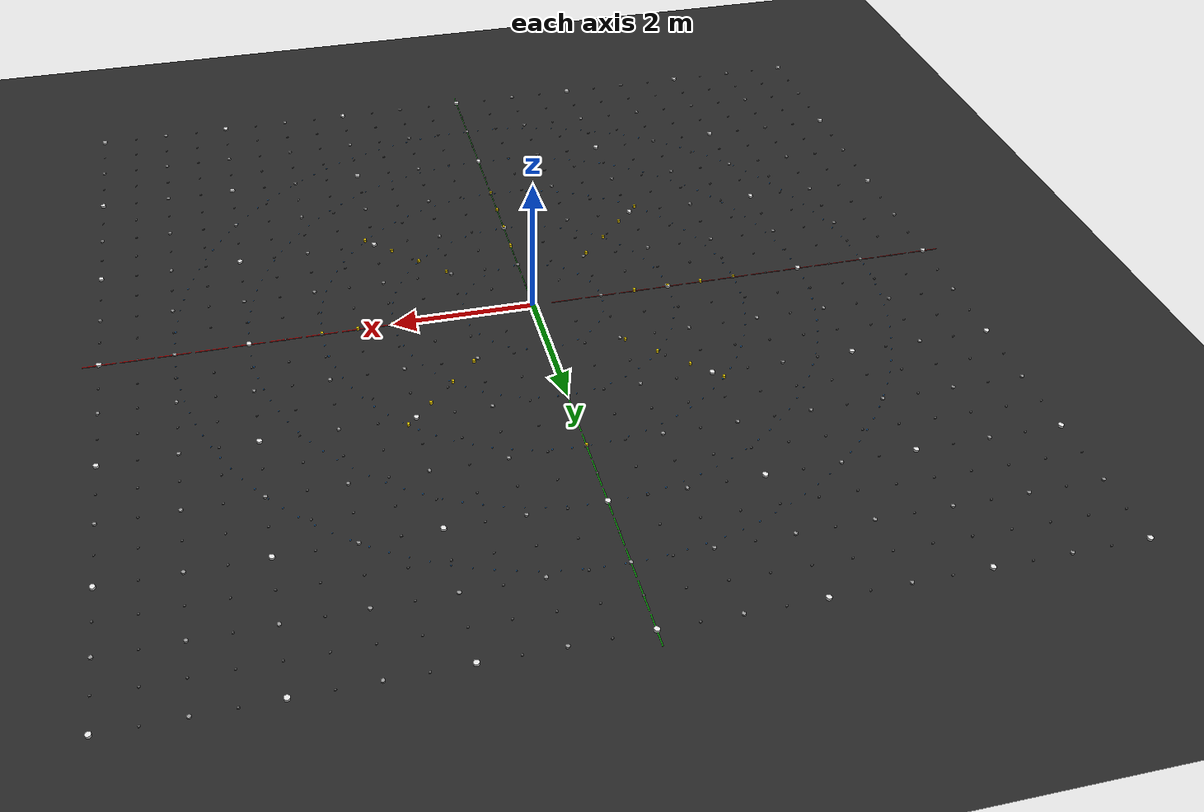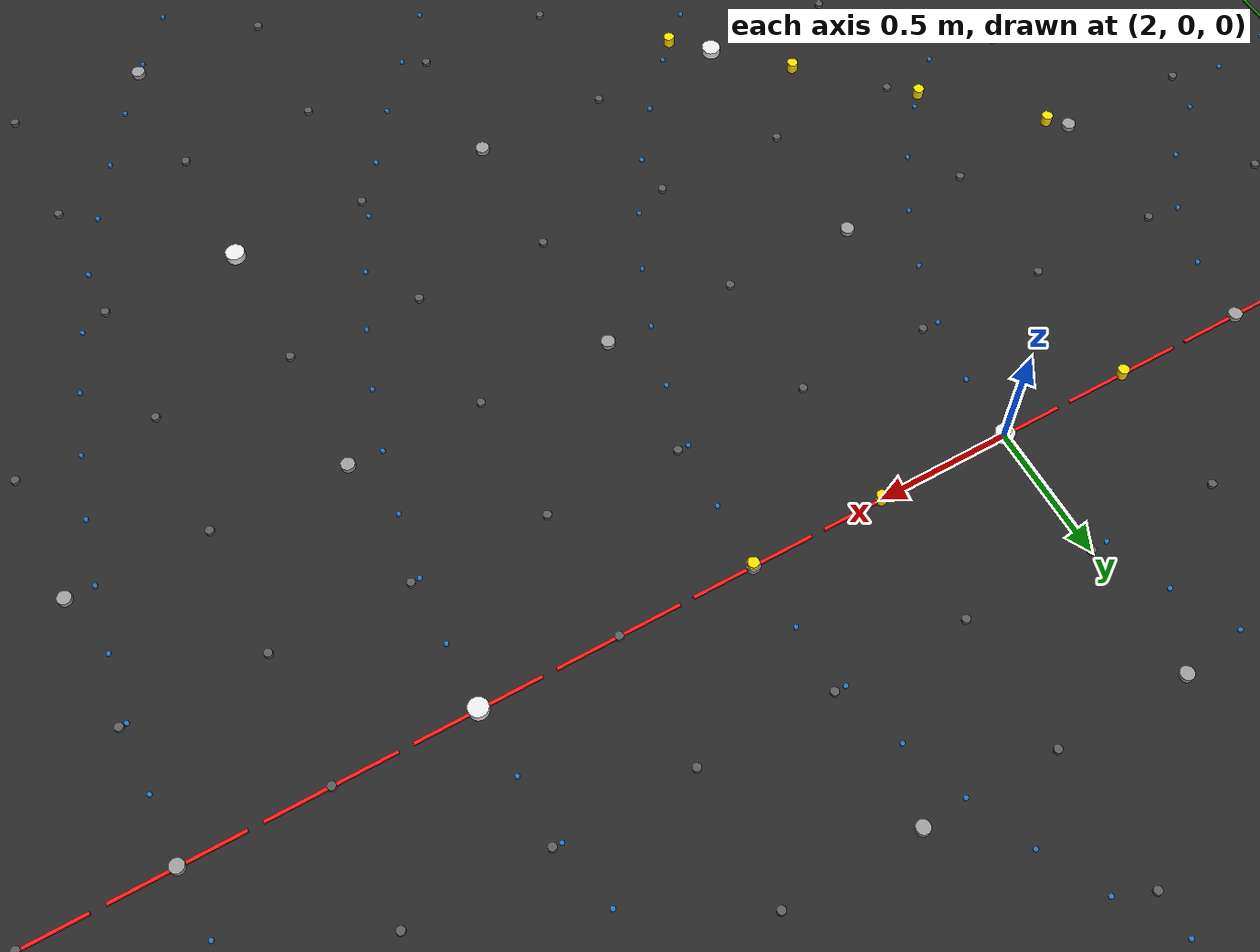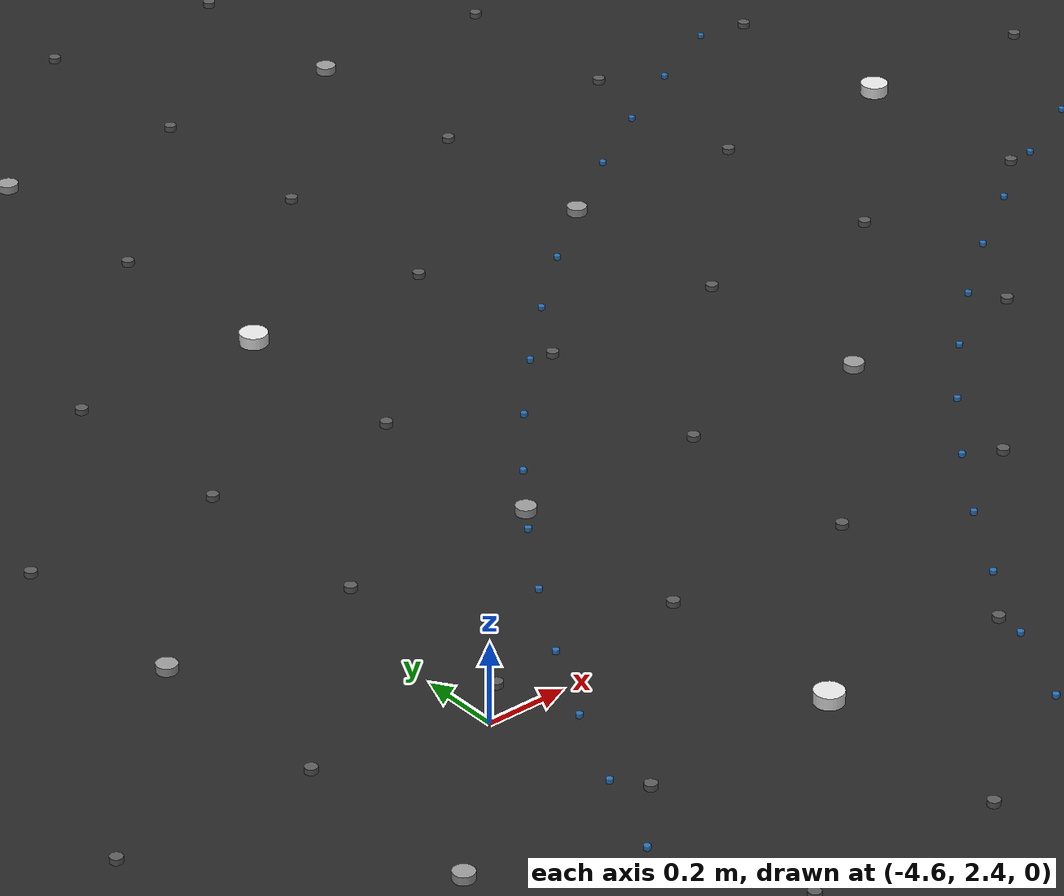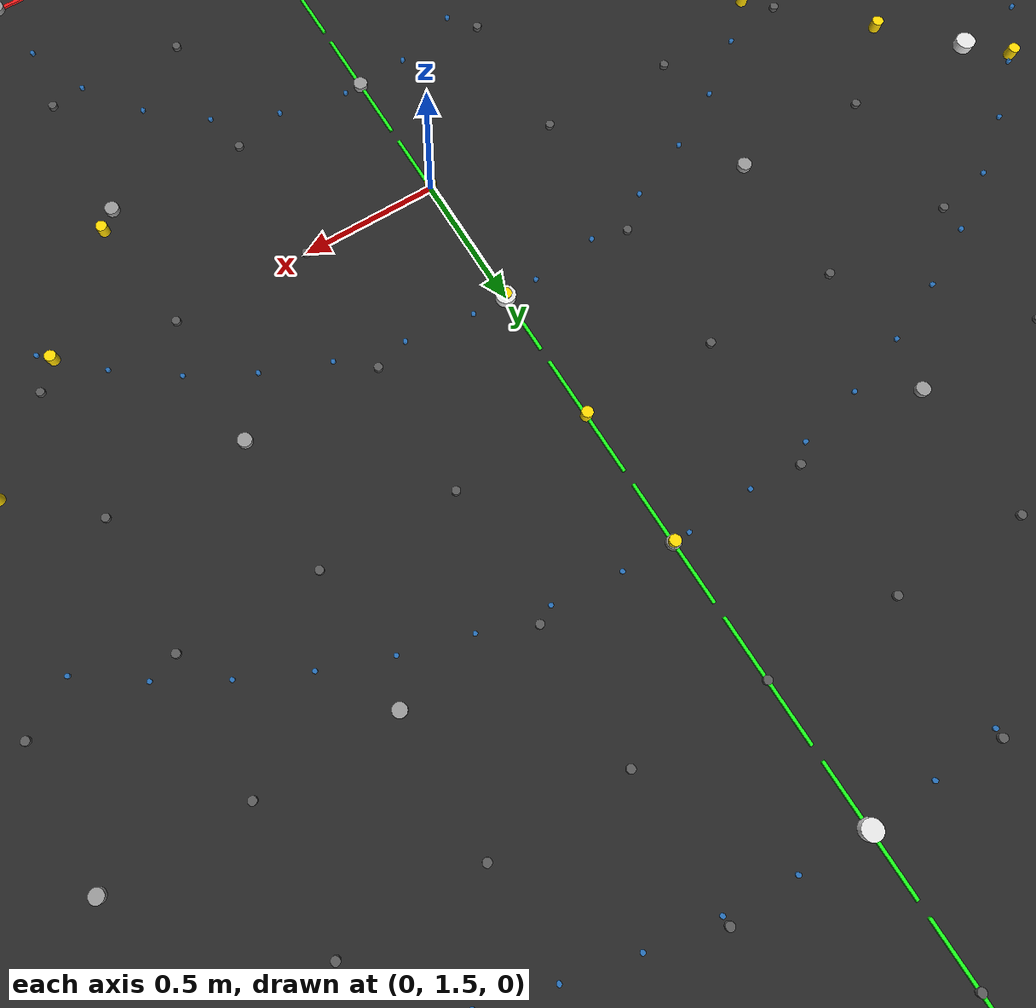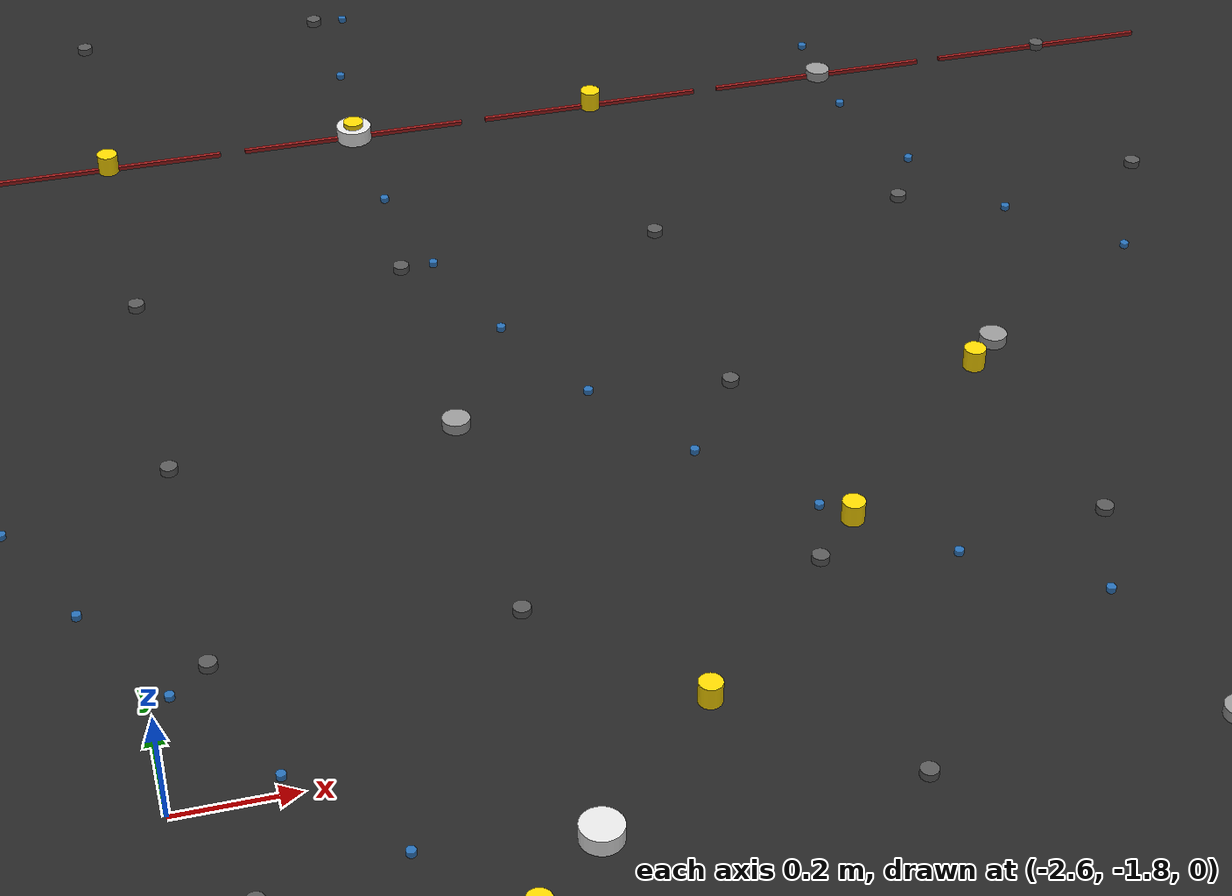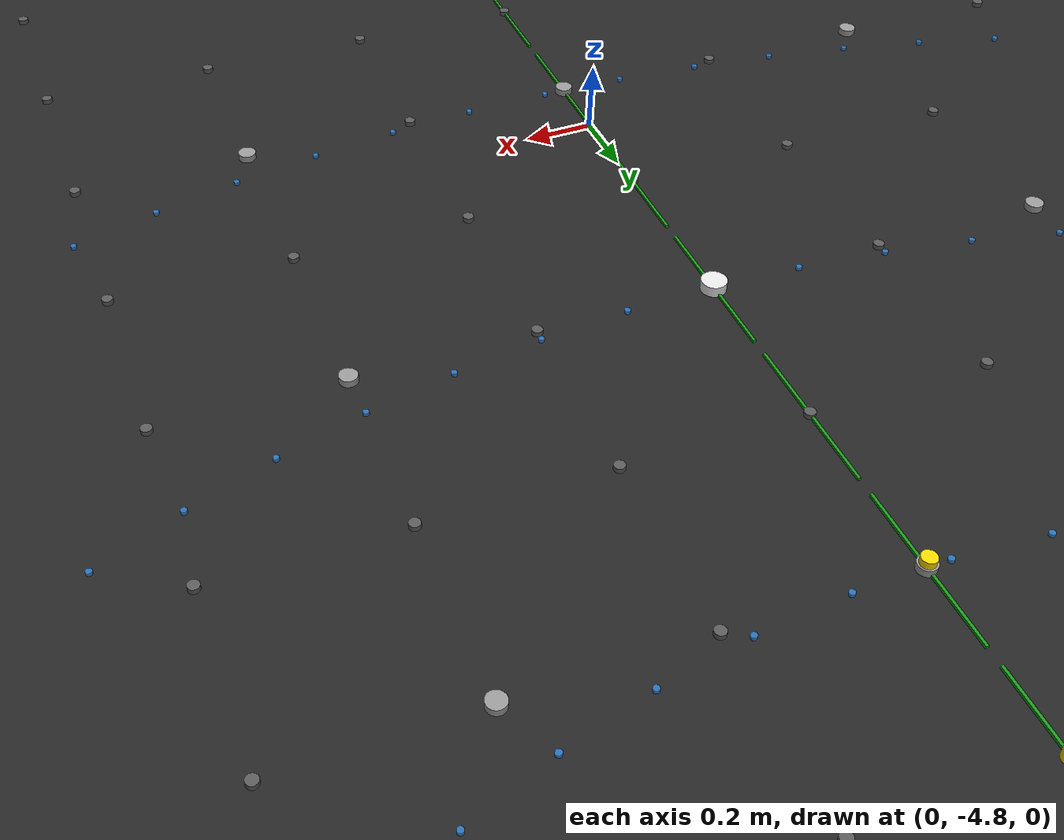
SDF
<?xml version="1.0" ?>
<sdf version="1.6">
  <world name="odom_validation_grid">

    <include>
      <uri>model://sun</uri>
    </include>

    <model name='ground_plane'>
      <static>true</static>
      <link name='link'>

        <collision name='collision'>
          <geometry>
            <plane>
              <normal>0 0 1</normal>
              <size>20 20</size>
            </plane>
          </geometry>
          <surface>
            <friction>
              <ode>
                <mu>1.0</mu>
                <mu2>1.0</mu2>
              </ode>
            </friction>
          </surface>
        </collision>

        <visual name='visual'>
          <geometry><plane><normal>0 0 1</normal><size>20 20</size></plane></geometry>
          <material>
            <ambient>0.12 0.12 0.12 1</ambient>
            <diffuse>0.15 0.15 0.15 1</diffuse>
          </material>
        </visual>
      </link>
    </model>

    <physics type='ode'>
      <real_time_update_rate>1000</real_time_update_rate>
      <max_step_size>0.001</max_step_size>
    </physics>

    <model name='dot_2m_0'>
      <static>true</static>
      <pose>-6.0 -6.0 0.015 0 0 0</pose>
      <link name='link'>
        <visual name='visual'>
          <geometry><cylinder><radius>0.035</radius><length>0.03</length></cylinder></geometry>
          <material><ambient>0.9 0.9 0.9 1.0</ambient><diffuse>0.9 0.9 0.9 1.0</diffuse></material>
        </visual>

      </link>
    </model>
    <model name='dot_05m_1'>
      <static>true</static>
      <pose>-6.0 -5.5 0.007 0 0 0</pose>
      <link name='link'>
        <visual name='visual'>
          <geometry><cylinder><radius>0.015</radius><length>0.014</length></cylinder></geometry>
          <material><ambient>0.35 0.35 0.35 1.0</ambient><diffuse>0.35 0.35 0.35 1.0</diffuse></material>
        </visual>

      </link>
    </model>
    <model name='dot_1m_2'>
      <static>true</static>
      <pose>-6.0 -5.0 0.01 0 0 0</pose>
      <link name='link'>
        <visual name='visual'>
          <geometry><cylinder><radius>0.025</radius><length>0.02</length></cylinder></geometry>
          <material><ambient>0.6 0.6 0.6 1.0</ambient><diffuse>0.6 0.6 0.6 1.0</diffuse></material>
        </visual>

      </link>
    </model>
    <model name='dot_05m_3'>
      <static>true</static>
      <pose>-6.0 -4.5 0.007 0 0 0</pose>
      <link name='link'>
        <visual name='visual'>
          <geometry><cylinder><radius>0.015</radius><length>0.014</length></cylinder></geometry>
          <material><ambient>0.35 0.35 0.35 1.0</ambient><diffuse>0.35 0.35 0.35 1.0</diffuse></material>
        </visual>

      </link>
    </model>
    <model name='dot_2m_4'>
      <static>true</static>
      <pose>-6.0 -4.0 0.015 0 0 0</pose>
      <link name='link'>
        <visual name='visual'>
          <geometry><cylinder><radius>0.035</radius><length>0.03</length></cylinder></geometry>
          <material><ambient>0.9 0.9 0.9 1.0</ambient><diffuse>0.9 0.9 0.9 1.0</diffuse></material>
        </visual>

      </link>
    </model>
    <model name='dot_05m_5'>
      <static>true</static>
      <pose>-6.0 -3.5 0.007 0 0 0</pose>
      <link name='link'>
        <visual name='visual'>
          <geometry><cylinder><radius>0.015</radius><length>0.014</length></cylinder></geometry>
          <material><ambient>0.35 0.35 0.35 1.0</ambient><diffuse>0.35 0.35 0.35 1.0</diffuse></material>
        </visual>

      </link>
    </model>
    <model name='dot_1m_6'>
      <static>true</static>
      <pose>-6.0 -3.0 0.01 0 0 0</pose>
      <link name='link'>
        <visual name='visual'>
          <geometry><cylinder><radius>0.025</radius><length>0.02</length></cylinder></geometry>
          <material><ambient>0.6 0.6 0.6 1.0</ambient><diffuse>0.6 0.6 0.6 1.0</diffuse></material>
        </visual>

      </link>
    </model>
    <model name='dot_05m_7'>
      <static>true</static>
      <pose>-6.0 -2.5 0.007 0 0 0</pose>
      <link name='link'>
        <visual name='visual'>
          <geometry><cylinder><radius>0.015</radius><length>0.014</length></cylinder></geometry>
          <material><ambient>0.35 0.35 0.35 1.0</ambient><diffuse>0.35 0.35 0.35 1.0</diffuse></material>
        </visual>

      </link>
    </model>
    <model name='dot_2m_8'>
      <static>true</static>
      <pose>-6.0 -2.0 0.015 0 0 0</pose>
      <link name='link'>
        <visual name='visual'>
          <geometry><cylinder><radius>0.035</radius><length>0.03</length></cylinder></geometry>
          <material><ambient>0.9 0.9 0.9 1.0</ambient><diffuse>0.9 0.9 0.9 1.0</diffuse></material>
        </visual>

      </link>
    </model>
    <model name='dot_05m_9'>
      <static>true</static>
      <pose>-6.0 -1.5 0.007 0 0 0</pose>
      <link name='link'>
        <visual name='visual'>
          <geometry><cylinder><radius>0.015</radius><length>0.014</length></cylinder></geometry>
          <material><ambient>0.35 0.35 0.35 1.0</ambient><diffuse>0.35 0.35 0.35 1.0</diffuse></material>
        </visual>

      </link>
    </model>
    <model name='dot_1m_10'>
      <static>true</static>
      <pose>-6.0 -1.0 0.01 0 0 0</pose>
      <link name='link'>
        <visual name='visual'>
          <geometry><cylinder><radius>0.025</radius><length>0.02</length></cylinder></geometry>
          <material><ambient>0.6 0.6 0.6 1.0</ambient><diffuse>0.6 0.6 0.6 1.0</diffuse></material>
        </visual>

      </link>
    </model>
    <model name='dot_05m_11'>
      <static>true</static>
      <pose>-6.0 -0.5 0.007 0 0 0</pose>
      <link name='link'>
        <visual name='visual'>
          <geometry><cylinder><radius>0.015</radius><length>0.014</length></cylinder></geometry>
          <material><ambient>0.35 0.35 0.35 1.0</ambient><diffuse>0.35 0.35 0.35 1.0</diffuse></material>
        </visual>

      </link>
    </model>
    <model name='dot_2m_12'>
      <static>true</static>
      <pose>-6.0 0.0 0.015 0 0 0</pose>
      <link name='link'>
        <visual name='visual'>
          <geometry><cylinder><radius>0.035</radius><length>0.03</length></cylinder></geometry>
          <material><ambient>0.9 0.9 0.9 1.0</ambient><diffuse>0.9 0.9 0.9 1.0</diffuse></material>
        </visual>

      </link>
    </model>
    <model name='dot_05m_13'>
      <static>true</static>
      <pose>-6.0 0.5 0.007 0 0 0</pose>
      <link name='link'>
        <visual name='visual'>
          <geometry><cylinder><radius>0.015</radius><length>0.014</length></cylinder></geometry>
          <material><ambient>0.35 0.35 0.35 1.0</ambient><diffuse>0.35 0.35 0.35 1.0</diffuse></material>
        </visual>

      </link>
    </model>
    <model name='dot_1m_14'>
      <static>true</static>
      <pose>-6.0 1.0 0.01 0 0 0</pose>
      <link name='link'>
        <visual name='visual'>
          <geometry><cylinder><radius>0.025</radius><length>0.02</length></cylinder></geometry>
          <material><ambient>0.6 0.6 0.6 1.0</ambient><diffuse>0.6 0.6 0.6 1.0</diffuse></material>
        </visual>

      </link>
    </model>
    <model name='dot_05m_15'>
      <static>true</static>
      <pose>-6.0 1.5 0.007 0 0 0</pose>
      <link name='link'>
        <visual name='visual'>
          <geometry><cylinder><radius>0.015</radius><length>0.014</length></cylinder></geometry>
          <material><ambient>0.35 0.35 0.35 1.0</ambient><diffuse>0.35 0.35 0.35 1.0</diffuse></material>
        </visual>

      </link>
    </model>
    <model name='dot_2m_16'>
      <static>true</static>
      <pose>-6.0 2.0 0.015 0 0 0</pose>
      <link name='link'>
        <visual name='visual'>
          <geometry><cylinder><radius>0.035</radius><length>0.03</length></cylinder></geometry>
          <material><ambient>0.9 0.9 0.9 1.0</ambient><diffuse>0.9 0.9 0.9 1.0</diffuse></material>
        </visual>

      </link>
    </model>
    <model name='dot_05m_17'>
      <static>true</static>
      <pose>-6.0 2.5 0.007 0 0 0</pose>
      <link name='link'>
        <visual name='visual'>
          <geometry><cylinder><radius>0.015</radius><length>0.014</length></cylinder></geometry>
          <material><ambient>0.35 0.35 0.35 1.0</ambient><diffuse>0.35 0.35 0.35 1.0</diffuse></material>
        </visual>

      </link>
    </model>
    <model name='dot_1m_18'>
      <static>true</static>
      <pose>-6.0 3.0 0.01 0 0 0</pose>
      <link name='link'>
        <visual name='visual'>
          <geometry><cylinder><radius>0.025</radius><length>0.02</length></cylinder></geometry>
          <material><ambient>0.6 0.6 0.6 1.0</ambient><diffuse>0.6 0.6 0.6 1.0</diffuse></material>
        </visual>

      </link>
    </model>
    <model name='dot_05m_19'>
      <static>true</static>
      <pose>-6.0 3.5 0.007 0 0 0</pose>
      <link name='link'>
        <visual name='visual'>
          <geometry><cylinder><radius>0.015</radius><length>0.014</length></cylinder></geometry>
          <material><ambient>0.35 0.35 0.35 1.0</ambient><diffuse>0.35 0.35 0.35 1.0</diffuse></material>
        </visual>

      </link>
    </model>
    <model name='dot_2m_20'>
      <static>true</static>
      <pose>-6.0 4.0 0.015 0 0 0</pose>
      <link name='link'>
        <visual name='visual'>
          <geometry><cylinder><radius>0.035</radius><length>0.03</length></cylinder></geometry>
          <material><ambient>0.9 0.9 0.9 1.0</ambient><diffuse>0.9 0.9 0.9 1.0</diffuse></material>
        </visual>

      </link>
    </model>
    <model name='dot_05m_21'>
      <static>true</static>
      <pose>-6.0 4.5 0.007 0 0 0</pose>
      <link name='link'>
        <visual name='visual'>
          <geometry><cylinder><radius>0.015</radius><length>0.014</length></cylinder></geometry>
          <material><ambient>0.35 0.35 0.35 1.0</ambient><diffuse>0.35 0.35 0.35 1.0</diffuse></material>
        </visual>

      </link>
    </model>
    <model name='dot_1m_22'>
      <static>true</static>
      <pose>-6.0 5.0 0.01 0 0 0</pose>
      <link name='link'>
        <visual name='visual'>
          <geometry><cylinder><radius>0.025</radius><length>0.02</length></cylinder></geometry>
          <material><ambient>0.6 0.6 0.6 1.0</ambient><diffuse>0.6 0.6 0.6 1.0</diffuse></material>
        </visual>

      </link>
    </model>
    <model name='dot_05m_23'>
      <static>true</static>
      <pose>-6.0 5.5 0.007 0 0 0</pose>
      <link name='link'>
        <visual name='visual'>
          <geometry><cylinder><radius>0.015</radius><length>0.014</length></cylinder></geometry>
          <material><ambient>0.35 0.35 0.35 1.0</ambient><diffuse>0.35 0.35 0.35 1.0</diffuse></material>
        </visual>

      </link>
    </model>
    <model name='dot_2m_24'>
      <static>true</static>
      <pose>-6.0 6.0 0.015 0 0 0</pose>
      <link name='link'>
        <visual name='visual'>
          <geometry><cylinder><radius>0.035</radius><length>0.03</length></cylinder></geometry>
          <material><ambient>0.9 0.9 0.9 1.0</ambient><diffuse>0.9 0.9 0.9 1.0</diffuse></material>
        </visual>

      </link>
    </model>
    <model name='dot_05m_25'>
      <static>true</static>
      <pose>-5.5 -6.0 0.007 0 0 0</pose>
      <link name='link'>
        <visual name='visual'>
          <geometry><cylinder><radius>0.015</radius><length>0.014</length></cylinder></geometry>
          <material><ambient>0.35 0.35 0.35 1.0</ambient><diffuse>0.35 0.35 0.35 1.0</diffuse></material>
        </visual>

      </link>
    </model>
    <model name='dot_05m_26'>
      <static>true</static>
      <pose>-5.5 -5.5 0.007 0 0 0</pose>
      <link name='link'>
        <visual name='visual'>
          <geometry><cylinder><radius>0.015</radius><length>0.014</length></cylinder></geometry>
          <material><ambient>0.35 0.35 0.35 1.0</ambient><diffuse>0.35 0.35 0.35 1.0</diffuse></material>
        </visual>

      </link>
    </model>
    <model name='dot_05m_27'>
      <static>true</static>
      <pose>-5.5 -5.0 0.007 0 0 0</pose>
      <link name='link'>
        <visual name='visual'>
          <geometry><cylinder><radius>0.015</radius><length>0.014</length></cylinder></geometry>
          <material><ambient>0.35 0.35 0.35 1.0</ambient><diffuse>0.35 0.35 0.35 1.0</diffuse></material>
        </visual>

      </link>
    </model>
    <model name='dot_05m_28'>
      <static>true</static>
      <pose>-5.5 -4.5 0.007 0 0 0</pose>
      <link name='link'>
        <visual name='visual'>
          <geometry><cylinder><radius>0.015</radius><length>0.014</length></cylinder></geometry>
          <material><ambient>0.35 0.35 0.35 1.0</ambient><diffuse>0.35 0.35 0.35 1.0</diffuse></material>
        </visual>

      </link>
    </model>
    <model name='dot_05m_29'>
      <static>true</static>
      <pose>-5.5 -4.0 0.007 0 0 0</pose>
      <link name='link'>
        <visual name='visual'>
          <geometry><cylinder><radius>0.015</radius><length>0.014</length></cylinder></geometry>
          <material><ambient>0.35 0.35 0.35 1.0</ambient><diffuse>0.35 0.35 0.35 1.0</diffuse></material>
        </visual>

      </link>
    </model>
    <model name='dot_05m_30'>
      <static>true</static>
      <pose>-5.5 -3.5 0.007 0 0 0</pose>
      <link name='link'>
        <visual name='visual'>
          <geometry><cylinder><radius>0.015</radius><length>0.014</length></cylinder></geometry>
          <material><ambient>0.35 0.35 0.35 1.0</ambient><diffuse>0.35 0.35 0.35 1.0</diffuse></material>
        </visual>

      </link>
    </model>
    <model name='dot_05m_31'>
      <static>true</static>
      <pose>-5.5 -3.0 0.007 0 0 0</pose>
      <link name='link'>
        <visual name='visual'>
          <geometry><cylinder><radius>0.015</radius><length>0.014</length></cylinder></geometry>
          <material><ambient>0.35 0.35 0.35 1.0</ambient><diffuse>0.35 0.35 0.35 1.0</diffuse></material>
        </visual>

      </link>
    </model>
    <model name='dot_05m_32'>
      <static>true</static>
      <pose>-5.5 -2.5 0.007 0 0 0</pose>
      <link name='link'>
        <visual name='visual'>
          <geometry><cylinder><radius>0.015</radius><length>0.014</length></cylinder></geometry>
          <material><ambient>0.35 0.35 0.35 1.0</ambient><diffuse>0.35 0.35 0.35 1.0</diffuse></material>
        </visual>

      </link>
    </model>
    <model name='dot_05m_33'>
      <static>true</static>
      <pose>-5.5 -2.0 0.007 0 0 0</pose>
      <link name='link'>
        <visual name='visual'>
          <geometry><cylinder><radius>0.015</radius><length>0.014</length></cylinder></geometry>
          <material><ambient>0.35 0.35 0.35 1.0</ambient><diffuse>0.35 0.35 0.35 1.0</diffuse></material>
        </visual>

      </link>
    </model>
    <model name='dot_05m_34'>
      <static>true</static>
      <pose>-5.5 -1.5 0.007 0 0 0</pose>
      <link name='link'>
        <visual name='visual'>
          <geometry><cylinder><radius>0.015</radius><length>0.014</length></cylinder></geometry>
          <material><ambient>0.35 0.35 0.35 1.0</ambient><diffuse>0.35 0.35 0.35 1.0</diffuse></material>
        </visual>

      </link>
    </model>
    <model name='dot_05m_35'>
      <static>true</static>
      <pose>-5.5 -1.0 0.007 0 0 0</pose>
      <link name='link'>
        <visual name='visual'>
          <geometry><cylinder><radius>0.015</radius><length>0.014</length></cylinder></geometry>
          <material><ambient>0.35 0.35 0.35 1.0</ambient><diffuse>0.35 0.35 0.35 1.0</diffuse></material>
        </visual>

      </link>
    </model>
    <model name='dot_05m_36'>
      <static>true</static>
      <pose>-5.5 -0.5 0.007 0 0 0</pose>
      <link name='link'>
        <visual name='visual'>
          <geometry><cylinder><radius>0.015</radius><length>0.014</length></cylinder></geometry>
          <material><ambient>0.35 0.35 0.35 1.0</ambient><diffuse>0.35 0.35 0.35 1.0</diffuse></material>
        </visual>

      </link>
    </model>
    <model name='dot_05m_37'>
      <static>true</static>
      <pose>-5.5 0.0 0.007 0 0 0</pose>
      <link name='link'>
        <visual name='visual'>
          <geometry><cylinder><radius>0.015</radius><length>0.014</length></cylinder></geometry>
          <material><ambient>0.35 0.35 0.35 1.0</ambient><diffuse>0.35 0.35 0.35 1.0</diffuse></material>
        </visual>

      </link>
    </model>
    <model name='dot_05m_38'>
      <static>true</static>
      <pose>-5.5 0.5 0.007 0 0 0</pose>
      <link name='link'>
        <visual name='visual'>
          <geometry><cylinder><radius>0.015</radius><length>0.014</length></cylinder></geometry>
          <material><ambient>0.35 0.35 0.35 1.0</ambient><diffuse>0.35 0.35 0.35 1.0</diffuse></material>
        </visual>

      </link>
    </model>
    <model name='dot_05m_39'>
      <static>true</static>
      <pose>-5.5 1.0 0.007 0 0 0</pose>
      <link name='link'>
        <visual name='visual'>
          <geometry><cylinder><radius>0.015</radius><length>0.014</length></cylinder></geometry>
          <material><ambient>0.35 0.35 0.35 1.0</ambient><diffuse>0.35 0.35 0.35 1.0</diffuse></material>
        </visual>

      </link>
    </model>
    <model name='dot_05m_40'>
      <static>true</static>
      <pose>-5.5 1.5 0.007 0 0 0</pose>
      <link name='link'>
        <visual name='visual'>
          <geometry><cylinder><radius>0.015</radius><length>0.014</length></cylinder></geometry>
          <material><ambient>0.35 0.35 0.35 1.0</ambient><diffuse>0.35 0.35 0.35 1.0</diffuse></material>
        </visual>

      </link>
    </model>
    <model name='dot_05m_41'>
      <static>true</static>
      <pose>-5.5 2.0 0.007 0 0 0</pose>
      <link name='link'>
        <visual name='visual'>
          <geometry><cylinder><radius>0.015</radius><length>0.014</length></cylinder></geometry>
          <material><ambient>0.35 0.35 0.35 1.0</ambient><diffuse>0.35 0.35 0.35 1.0</diffuse></material>
        </visual>

      </link>
    </model>
    <model name='dot_05m_42'>
      <static>true</static>
      <pose>-5.5 2.5 0.007 0 0 0</pose>
      <link name='link'>
        <visual name='visual'>
          <geometry><cylinder><radius>0.015</radius><length>0.014</length></cylinder></geometry>
          <material><ambient>0.35 0.35 0.35 1.0</ambient><diffuse>0.35 0.35 0.35 1.0</diffuse></material>
        </visual>

      </link>
    </model>
    <model name='dot_05m_43'>
      <static>true</static>
      <pose>-5.5 3.0 0.007 0 0 0</pose>
      <link name='link'>
        <visual name='visual'>
          <geometry><cylinder><radius>0.015</radius><length>0.014</length></cylinder></geometry>
          <material><ambient>0.35 0.35 0.35 1.0</ambient><diffuse>0.35 0.35 0.35 1.0</diffuse></material>
        </visual>

      </link>
    </model>
    <model name='dot_05m_44'>
      <static>true</static>
      <pose>-5.5 3.5 0.007 0 0 0</pose>
      <link name='link'>
        <visual name='visual'>
          <geometry><cylinder><radius>0.015</radius><length>0.014</length></cylinder></geometry>
          <material><ambient>0.35 0.35 0.35 1.0</ambient><diffuse>0.35 0.35 0.35 1.0</diffuse></material>
        </visual>

      </link>
    </model>
    <model name='dot_05m_45'>
      <static>true</static>
      <pose>-5.5 4.0 0.007 0 0 0</pose>
      <link name='link'>
        <visual name='visual'>
          <geometry><cylinder><radius>0.015</radius><length>0.014</length></cylinder></geometry>
          <material><ambient>0.35 0.35 0.35 1.0</ambient><diffuse>0.35 0.35 0.35 1.0</diffuse></material>
        </visual>

      </link>
    </model>
    <model name='dot_05m_46'>
      <static>true</static>
      <pose>-5.5 4.5 0.007 0 0 0</pose>
      <link name='link'>
        <visual name='visual'>
          <geometry><cylinder><radius>0.015</radius><length>0.014</length></cylinder></geometry>
          <material><ambient>0.35 0.35 0.35 1.0</ambient><diffuse>0.35 0.35 0.35 1.0</diffuse></material>
        </visual>

      </link>
    </model>
    <model name='dot_05m_47'>
      <static>true</static>
      <pose>-5.5 5.0 0.007 0 0 0</pose>
      <link name='link'>
        <visual name='visual'>
          <geometry><cylinder><radius>0.015</radius><length>0.014</length></cylinder></geometry>
          <material><ambient>0.35 0.35 0.35 1.0</ambient><diffuse>0.35 0.35 0.35 1.0</diffuse></material>
        </visual>

      </link>
    </model>
    <model name='dot_05m_48'>
      <static>true</static>
      <pose>-5.5 5.5 0.007 0 0 0</pose>
      <link name='link'>
        <visual name='visual'>
          <geometry><cylinder><radius>0.015</radius><length>0.014</length></cylinder></geometry>
          <material><ambient>0.35 0.35 0.35 1.0</ambient><diffuse>0.35 0.35 0.35 1.0</diffuse></material>
        </visual>

      </link>
    </model>
    <model name='dot_05m_49'>
      <static>true</static>
      <pose>-5.5 6.0 0.007 0 0 0</pose>
      <link name='link'>
        <visual name='visual'>
          <geometry><cylinder><radius>0.015</radius><length>0.014</length></cylinder></geometry>
          <material><ambient>0.35 0.35 0.35 1.0</ambient><diffuse>0.35 0.35 0.35 1.0</diffuse></material>
        </visual>

      </link>
    </model>
    <model name='dot_1m_50'>
      <static>true</static>
      <pose>-5.0 -6.0 0.01 0 0 0</pose>
      <link name='link'>
        <visual name='visual'>
          <geometry><cylinder><radius>0.025</radius><length>0.02</length></cylinder></geometry>
          <material><ambient>0.6 0.6 0.6 1.0</ambient><diffuse>0.6 0.6 0.6 1.0</diffuse></material>
        </visual>

      </link>
    </model>
    <model name='dot_05m_51'>
      <static>true</static>
      <pose>-5.0 -5.5 0.007 0 0 0</pose>
      <link name='link'>
        <visual name='visual'>
          <geometry><cylinder><radius>0.015</radius><length>0.014</length></cylinder></geometry>
          <material><ambient>0.35 0.35 0.35 1.0</ambient><diffuse>0.35 0.35 0.35 1.0</diffuse></material>
        </visual>

      </link>
    </model>
    <model name='dot_1m_52'>
      <static>true</static>
      <pose>-5.0 -5.0 0.01 0 0 0</pose>
      <link name='link'>
        <visual name='visual'>
          <geometry><cylinder><radius>0.025</radius><length>0.02</length></cylinder></geometry>
          <material><ambient>0.6 0.6 0.6 1.0</ambient><diffuse>0.6 0.6 0.6 1.0</diffuse></material>
        </visual>

      </link>
    </model>
    <model name='dot_05m_53'>
      <static>true</static>
      <pose>-5.0 -4.5 0.007 0 0 0</pose>
      <link name='link'>
        <visual name='visual'>
          <geometry><cylinder><radius>0.015</radius><length>0.014</length></cylinder></geometry>
          <material><ambient>0.35 0.35 0.35 1.0</ambient><diffuse>0.35 0.35 0.35 1.0</diffuse></material>
        </visual>

      </link>
    </model>
    <model name='dot_1m_54'>
      <static>true</static>
      <pose>-5.0 -4.0 0.01 0 0 0</pose>
      <link name='link'>
        <visual name='visual'>
          <geometry><cylinder><radius>0.025</radius><length>0.02</length></cylinder></geometry>
          <material><ambient>0.6 0.6 0.6 1.0</ambient><diffuse>0.6 0.6 0.6 1.0</diffuse></material>
        </visual>

      </link>
    </model>
    <model name='dot_05m_55'>
      <static>true</static>
      <pose>-5.0 -3.5 0.007 0 0 0</pose>
      <link name='link'>
        <visual name='visual'>
          <geometry><cylinder><radius>0.015</radius><length>0.014</length></cylinder></geometry>
          <material><ambient>0.35 0.35 0.35 1.0</ambient><diffuse>0.35 0.35 0.35 1.0</diffuse></material>
        </visual>

      </link>
    </model>
    <model name='dot_1m_56'>
      <static>true</static>
      <pose>-5.0 -3.0 0.01 0 0 0</pose>
      <link name='link'>
        <visual name='visual'>
          <geometry><cylinder><radius>0.025</radius><length>0.02</length></cylinder></geometry>
          <material><ambient>0.6 0.6 0.6 1.0</ambient><diffuse>0.6 0.6 0.6 1.0</diffuse></material>
        </visual>

      </link>
    </model>
    <model name='dot_05m_57'>
      <static>true</static>
      <pose>-5.0 -2.5 0.007 0 0 0</pose>
      <link name='link'>
        <visual name='visual'>
          <geometry><cylinder><radius>0.015</radius><length>0.014</length></cylinder></geometry>
          <material><ambient>0.35 0.35 0.35 1.0</ambient><diffuse>0.35 0.35 0.35 1.0</diffuse></material>
        </visual>

      </link>
    </model>
    <model name='dot_1m_58'>
      <static>true</static>
      <pose>-5.0 -2.0 0.01 0 0 0</pose>
      <link name='link'>
        <visual name='visual'>
          <geometry><cylinder><radius>0.025</radius><length>0.02</length></cylinder></geometry>
          <material><ambient>0.6 0.6 0.6 1.0</ambient><diffuse>0.6 0.6 0.6 1.0</diffuse></material>
        </visual>

      </link>
    </model>
    <model name='dot_05m_59'>
      <static>true</static>
      <pose>-5.0 -1.5 0.007 0 0 0</pose>
      <link name='link'>
        <visual name='visual'>
          <geometry><cylinder><radius>0.015</radius><length>0.014</length></cylinder></geometry>
          <material><ambient>0.35 0.35 0.35 1.0</ambient><diffuse>0.35 0.35 0.35 1.0</diffuse></material>
        </visual>

      </link>
    </model>
    <model name='dot_1m_60'>
      <static>true</static>
      <pose>-5.0 -1.0 0.01 0 0 0</pose>
      <link name='link'>
        <visual name='visual'>
          <geometry><cylinder><radius>0.025</radius><length>0.02</length></cylinder></geometry>
          <material><ambient>0.6 0.6 0.6 1.0</ambient><diffuse>0.6 0.6 0.6 1.0</diffuse></material>
        </visual>

      </link>
    </model>
    <model name='dot_05m_61'>
      <static>true</static>
      <pose>-5.0 -0.5 0.007 0 0 0</pose>
      <link name='link'>
        <visual name='visual'>
          <geometry><cylinder><radius>0.015</radius><length>0.014</length></cylinder></geometry>
          <material><ambient>0.35 0.35 0.35 1.0</ambient><diffuse>0.35 0.35 0.35 1.0</diffuse></material>
        </visual>

      </link>
    </model>
    <model name='dot_1m_62'>
      <static>true</static>
      <pose>-5.0 0.0 0.01 0 0 0</pose>
      <link name='link'>
        <visual name='visual'>
          <geometry><cylinder><radius>0.025</radius><length>0.02</length></cylinder></geometry>
          <material><ambient>0.6 0.6 0.6 1.0</ambient><diffuse>0.6 0.6 0.6 1.0</diffuse></material>
        </visual>

      </link>
    </model>
    <model name='dot_05m_63'>
      <static>true</static>
      <pose>-5.0 0.5 0.007 0 0 0</pose>
      <link name='link'>
        <visual name='visual'>
          <geometry><cylinder><radius>0.015</radius><length>0.014</length></cylinder></geometry>
          <material><ambient>0.35 0.35 0.35 1.0</ambient><diffuse>0.35 0.35 0.35 1.0</diffuse></material>
        </visual>

      </link>
    </model>
    <model name='dot_1m_64'>
      <static>true</static>
      <pose>-5.0 1.0 0.01 0 0 0</pose>
      <link name='link'>
        <visual name='visual'>
          <geometry><cylinder><radius>0.025</radius><length>0.02</length></cylinder></geometry>
          <material><ambient>0.6 0.6 0.6 1.0</ambient><diffuse>0.6 0.6 0.6 1.0</diffuse></material>
        </visual>

      </link>
    </model>
    <model name='dot_05m_65'>
      <static>true</static>
      <pose>-5.0 1.5 0.007 0 0 0</pose>
      <link name='link'>
        <visual name='visual'>
          <geometry><cylinder><radius>0.015</radius><length>0.014</length></cylinder></geometry>
          <material><ambient>0.35 0.35 0.35 1.0</ambient><diffuse>0.35 0.35 0.35 1.0</diffuse></material>
        </visual>

      </link>
    </model>
    <model name='dot_1m_66'>
      <static>true</static>
      <pose>-5.0 2.0 0.01 0 0 0</pose>
      <link name='link'>
        <visual name='visual'>
          <geometry><cylinder><radius>0.025</radius><length>0.02</length></cylinder></geometry>
          <material><ambient>0.6 0.6 0.6 1.0</ambient><diffuse>0.6 0.6 0.6 1.0</diffuse></material>
        </visual>

      </link>
    </model>
    <model name='dot_05m_67'>
      <static>true</static>
      <pose>-5.0 2.5 0.007 0 0 0</pose>
      <link name='link'>
        <visual name='visual'>
          <geometry><cylinder><radius>0.015</radius><length>0.014</length></cylinder></geometry>
          <material><ambient>0.35 0.35 0.35 1.0</ambient><diffuse>0.35 0.35 0.35 1.0</diffuse></material>
        </visual>

      </link>
    </model>
    <model name='dot_1m_68'>
      <static>true</static>
      <pose>-5.0 3.0 0.01 0 0 0</pose>
      <link name='link'>
        <visual name='visual'>
          <geometry><cylinder><radius>0.025</radius><length>0.02</length></cylinder></geometry>
          <material><ambient>0.6 0.6 0.6 1.0</ambient><diffuse>0.6 0.6 0.6 1.0</diffuse></material>
        </visual>

      </link>
    </model>
    <model name='dot_05m_69'>
      <static>true</static>
      <pose>-5.0 3.5 0.007 0 0 0</pose>
      <link name='link'>
        <visual name='visual'>
          <geometry><cylinder><radius>0.015</radius><length>0.014</length></cylinder></geometry>
          <material><ambient>0.35 0.35 0.35 1.0</ambient><diffuse>0.35 0.35 0.35 1.0</diffuse></material>
        </visual>

      </link>
    </model>
    <model name='dot_1m_70'>
      <static>true</static>
      <pose>-5.0 4.0 0.01 0 0 0</pose>
      <link name='link'>
        <visual name='visual'>
          <geometry><cylinder><radius>0.025</radius><length>0.02</length></cylinder></geometry>
          <material><ambient>0.6 0.6 0.6 1.0</ambient><diffuse>0.6 0.6 0.6 1.0</diffuse></material>
        </visual>

      </link>
    </model>
    <model name='dot_05m_71'>
      <static>true</static>
      <pose>-5.0 4.5 0.007 0 0 0</pose>
      <link name='link'>
        <visual name='visual'>
          <geometry><cylinder><radius>0.015</radius><length>0.014</length></cylinder></geometry>
          <material><ambient>0.35 0.35 0.35 1.0</ambient><diffuse>0.35 0.35 0.35 1.0</diffuse></material>
        </visual>

      </link>
    </model>
    <model name='dot_1m_72'>
      <static>true</static>
      <pose>-5.0 5.0 0.01 0 0 0</pose>
      <link name='link'>
        <visual name='visual'>
          <geometry><cylinder><radius>0.025</radius><length>0.02</length></cylinder></geometry>
          <material><ambient>0.6 0.6 0.6 1.0</ambient><diffuse>0.6 0.6 0.6 1.0</diffuse></material>
        </visual>

      </link>
    </model>
    <model name='dot_05m_73'>
      <static>true</static>
      <pose>-5.0 5.5 0.007 0 0 0</pose>
      <link name='link'>
        <visual name='visual'>
          <geometry><cylinder><radius>0.015</radius><length>0.014</length></cylinder></geometry>
          <material><ambient>0.35 0.35 0.35 1.0</ambient><diffuse>0.35 0.35 0.35 1.0</diffuse></material>
        </visual>

      </link>
    </model>
    <model name='dot_1m_74'>
      <static>true</static>
      <pose>-5.0 6.0 0.01 0 0 0</pose>
      <link name='link'>
        <visual name='visual'>
          <geometry><cylinder><radius>0.025</radius><length>0.02</length></cylinder></geometry>
          <material><ambient>0.6 0.6 0.6 1.0</ambient><diffuse>0.6 0.6 0.6 1.0</diffuse></material>
        </visual>

      </link>
    </model>
    <model name='dot_05m_75'>
      <static>true</static>
      <pose>-4.5 -6.0 0.007 0 0 0</pose>
      <link name='link'>
        <visual name='visual'>
          <geometry><cylinder><radius>0.015</radius><length>0.014</length></cylinder></geometry>
          <material><ambient>0.35 0.35 0.35 1.0</ambient><diffuse>0.35 0.35 0.35 1.0</diffuse></material>
        </visual>

      </link>
    </model>
    <model name='dot_05m_76'>
      <static>true</static>
      <pose>-4.5 -5.5 0.007 0 0 0</pose>
      <link name='link'>
        <visual name='visual'>
          <geometry><cylinder><radius>0.015</radius><length>0.014</length></cylinder></geometry>
          <material><ambient>0.35 0.35 0.35 1.0</ambient><diffuse>0.35 0.35 0.35 1.0</diffuse></material>
        </visual>

      </link>
    </model>
    <model name='dot_05m_77'>
      <static>true</static>
      <pose>-4.5 -5.0 0.007 0 0 0</pose>
      <link name='link'>
        <visual name='visual'>
          <geometry><cylinder><radius>0.015</radius><length>0.014</length></cylinder></geometry>
          <material><ambient>0.35 0.35 0.35 1.0</ambient><diffuse>0.35 0.35 0.35 1.0</diffuse></material>
        </visual>

      </link>
    </model>
    <model name='dot_05m_78'>
      <static>true</static>
      <pose>-4.5 -4.5 0.007 0 0 0</pose>
      <link name='link'>
        <visual name='visual'>
          <geometry><cylinder><radius>0.015</radius><length>0.014</length></cylinder></geometry>
          <material><ambient>0.35 0.35 0.35 1.0</ambient><diffuse>0.35 0.35 0.35 1.0</diffuse></material>
        </visual>

      </link>
    </model>
    <model name='dot_05m_79'>
      <static>true</static>
      <pose>-4.5 -4.0 0.007 0 0 0</pose>
      <link name='link'>
        <visual name='visual'>
          <geometry><cylinder><radius>0.015</radius><length>0.014</length></cylinder></geometry>
          <material><ambient>0.35 0.35 0.35 1.0</ambient><diffuse>0.35 0.35 0.35 1.0</diffuse></material>
        </visual>

      </link>
    </model>
    <model name='dot_05m_80'>
      <static>true</static>
      <pose>-4.5 -3.5 0.007 0 0 0</pose>
      <link name='link'>
        <visual name='visual'>
          <geometry><cylinder><radius>0.015</radius><length>0.014</length></cylinder></geometry>
          <material><ambient>0.35 0.35 0.35 1.0</ambient><diffuse>0.35 0.35 0.35 1.0</diffuse></material>
        </visual>

      </link>
    </model>
    <model name='dot_05m_81'>
      <static>true</static>
      <pose>-4.5 -3.0 0.007 0 0 0</pose>
      <link name='link'>
        <visual name='visual'>
          <geometry><cylinder><radius>0.015</radius><length>0.014</length></cylinder></geometry>
          <material><ambient>0.35 0.35 0.35 1.0</ambient><diffuse>0.35 0.35 0.35 1.0</diffuse></material>
        </visual>

      </link>
    </model>
    <model name='dot_05m_82'>
      <static>true</static>
      <pose>-4.5 -2.5 0.007 0 0 0</pose>
      <link name='link'>
        <visual name='visual'>
          <geometry><cylinder><radius>0.015</radius><length>0.014</length></cylinder></geometry>
          <material><ambient>0.35 0.35 0.35 1.0</ambient><diffuse>0.35 0.35 0.35 1.0</diffuse></material>
        </visual>

      </link>
    </model>
    <model name='dot_05m_83'>
      <static>true</static>
      <pose>-4.5 -2.0 0.007 0 0 0</pose>
      <link name='link'>
        <visual name='visual'>
          <geometry><cylinder><radius>0.015</radius><length>0.014</length></cylinder></geometry>
          <material><ambient>0.35 0.35 0.35 1.0</ambient><diffuse>0.35 0.35 0.35 1.0</diffuse></material>
        </visual>

      </link>
    </model>
    <model name='dot_05m_84'>
      <static>true</static>
      <pose>-4.5 -1.5 0.007 0 0 0</pose>
      <link name='link'>
        <visual name='visual'>
          <geometry><cylinder><radius>0.015</radius><length>0.014</length></cylinder></geometry>
          <material><ambient>0.35 0.35 0.35 1.0</ambient><diffuse>0.35 0.35 0.35 1.0</diffuse></material>
        </visual>

      </link>
    </model>
    <model name='dot_05m_85'>
      <static>true</static>
      <pose>-4.5 -1.0 0.007 0 0 0</pose>
      <link name='link'>
        <visual name='visual'>
          <geometry><cylinder><radius>0.015</radius><length>0.014</length></cylinder></geometry>
          <material><ambient>0.35 0.35 0.35 1.0</ambient><diffuse>0.35 0.35 0.35 1.0</diffuse></material>
        </visual>

      </link>
    </model>
    <model name='dot_05m_86'>
      <static>true</static>
      <pose>-4.5 -0.5 0.007 0 0 0</pose>
      <link name='link'>
        <visual name='visual'>
          <geometry><cylinder><radius>0.015</radius><length>0.014</length></cylinder></geometry>
          <material><ambient>0.35 0.35 0.35 1.0</ambient><diffuse>0.35 0.35 0.35 1.0</diffuse></material>
        </visual>

      </link>
    </model>
    <model name='dot_05m_87'>
      <static>true</static>
      <pose>-4.5 0.0 0.007 0 0 0</pose>
      <link name='link'>
        <visual name='visual'>
          <geometry><cylinder><radius>0.015</radius><length>0.014</length></cylinder></geometry>
          <material><ambient>0.35 0.35 0.35 1.0</ambient><diffuse>0.35 0.35 0.35 1.0</diffuse></material>
        </visual>

      </link>
    </model>
    <model name='dot_05m_88'>
      <static>true</static>
      <pose>-4.5 0.5 0.007 0 0 0</pose>
      <link name='link'>
        <visual name='visual'>
          <geometry><cylinder><radius>0.015</radius><length>0.014</length></cylinder></geometry>
          <material><ambient>0.35 0.35 0.35 1.0</ambient><diffuse>0.35 0.35 0.35 1.0</diffuse></material>
        </visual>

      </link>
    </model>
    <model name='dot_05m_89'>
      <static>true</static>
      <pose>-4.5 1.0 0.007 0 0 0</pose>
      <link name='link'>
        <visual name='visual'>
          <geometry><cylinder><radius>0.015</radius><length>0.014</length></cylinder></geometry>
          <material><ambient>0.35 0.35 0.35 1.0</ambient><diffuse>0.35 0.35 0.35 1.0</diffuse></material>
        </visual>

      </link>
    </model>
    <model name='dot_05m_90'>
      <static>true</static>
      <pose>-4.5 1.5 0.007 0 0 0</pose>
      <link name='link'>
        <visual name='visual'>
          <geometry><cylinder><radius>0.015</radius><length>0.014</length></cylinder></geometry>
          <material><ambient>0.35 0.35 0.35 1.0</ambient><diffuse>0.35 0.35 0.35 1.0</diffuse></material>
        </visual>

      </link>
    </model>
    <model name='dot_05m_91'>
      <static>true</static>
      <pose>-4.5 2.0 0.007 0 0 0</pose>
      <link name='link'>
        <visual name='visual'>
          <geometry><cylinder><radius>0.015</radius><length>0.014</length></cylinder></geometry>
          <material><ambient>0.35 0.35 0.35 1.0</ambient><diffuse>0.35 0.35 0.35 1.0</diffuse></material>
        </visual>

      </link>
    </model>
    <model name='dot_05m_92'>
      <static>true</static>
      <pose>-4.5 2.5 0.007 0 0 0</pose>
      <link name='link'>
        <visual name='visual'>
          <geometry><cylinder><radius>0.015</radius><length>0.014</length></cylinder></geometry>
          <material><ambient>0.35 0.35 0.35 1.0</ambient><diffuse>0.35 0.35 0.35 1.0</diffuse></material>
        </visual>

      </link>
    </model>
    <model name='dot_05m_93'>
      <static>true</static>
      <pose>-4.5 3.0 0.007 0 0 0</pose>
      <link name='link'>
        <visual name='visual'>
          <geometry><cylinder><radius>0.015</radius><length>0.014</length></cylinder></geometry>
          <material><ambient>0.35 0.35 0.35 1.0</ambient><diffuse>0.35 0.35 0.35 1.0</diffuse></material>
        </visual>

      </link>
    </model>
    <model name='dot_05m_94'>
      <static>true</static>
      <pose>-4.5 3.5 0.007 0 0 0</pose>
      <link name='link'>
        <visual name='visual'>
          <geometry><cylinder><radius>0.015</radius><length>0.014</length></cylinder></geometry>
          <material><ambient>0.35 0.35 0.35 1.0</ambient><diffuse>0.35 0.35 0.35 1.0</diffuse></material>
        </visual>

      </link>
    </model>
    <model name='dot_05m_95'>
      <static>true</static>
      <pose>-4.5 4.0 0.007 0 0 0</pose>
      <link name='link'>
        <visual name='visual'>
          <geometry><cylinder><radius>0.015</radius><length>0.014</length></cylinder></geometry>
          <material><ambient>0.35 0.35 0.35 1.0</ambient><diffuse>0.35 0.35 0.35 1.0</diffuse></material>
        </visual>

      </link>
    </model>
    <model name='dot_05m_96'>
      <static>true</static>
      <pose>-4.5 4.5 0.007 0 0 0</pose>
      <link name='link'>
        <visual name='visual'>
          <geometry><cylinder><radius>0.015</radius><length>0.014</length></cylinder></geometry>
          <material><ambient>0.35 0.35 0.35 1.0</ambient><diffuse>0.35 0.35 0.35 1.0</diffuse></material>
        </visual>

      </link>
    </model>
    <model name='dot_05m_97'>
      <static>true</static>
      <pose>-4.5 5.0 0.007 0 0 0</pose>
      <link name='link'>
        <visual name='visual'>
          <geometry><cylinder><radius>0.015</radius><length>0.014</length></cylinder></geometry>
          <material><ambient>0.35 0.35 0.35 1.0</ambient><diffuse>0.35 0.35 0.35 1.0</diffuse></material>
        </visual>

      </link>
    </model>
    <model name='dot_05m_98'>
      <static>true</static>
      <pose>-4.5 5.5 0.007 0 0 0</pose>
      <link name='link'>
        <visual name='visual'>
          <geometry><cylinder><radius>0.015</radius><length>0.014</length></cylinder></geometry>
          <material><ambient>0.35 0.35 0.35 1.0</ambient><diffuse>0.35 0.35 0.35 1.0</diffuse></material>
        </visual>

      </link>
    </model>
    <model name='dot_05m_99'>
      <static>true</static>
      <pose>-4.5 6.0 0.007 0 0 0</pose>
      <link name='link'>
        <visual name='visual'>
          <geometry><cylinder><radius>0.015</radius><length>0.014</length></cylinder></geometry>
          <material><ambient>0.35 0.35 0.35 1.0</ambient><diffuse>0.35 0.35 0.35 1.0</diffuse></material>
        </visual>

      </link>
    </model>
    <model name='dot_2m_100'>
      <static>true</static>
      <pose>-4.0 -6.0 0.015 0 0 0</pose>
      <link name='link'>
        <visual name='visual'>
          <geometry><cylinder><radius>0.035</radius><length>0.03</length></cylinder></geometry>
          <material><ambient>0.9 0.9 0.9 1.0</ambient><diffuse>0.9 0.9 0.9 1.0</diffuse></material>
        </visual>

      </link>
    </model>
    <model name='dot_05m_101'>
      <static>true</static>
      <pose>-4.0 -5.5 0.007 0 0 0</pose>
      <link name='link'>
        <visual name='visual'>
          <geometry><cylinder><radius>0.015</radius><length>0.014</length></cylinder></geometry>
          <material><ambient>0.35 0.35 0.35 1.0</ambient><diffuse>0.35 0.35 0.35 1.0</diffuse></material>
        </visual>

      </link>
    </model>
    <model name='dot_1m_102'>
      <static>true</static>
      <pose>-4.0 -5.0 0.01 0 0 0</pose>
      <link name='link'>
        <visual name='visual'>
          <geometry><cylinder><radius>0.025</radius><length>0.02</length></cylinder></geometry>
          <material><ambient>0.6 0.6 0.6 1.0</ambient><diffuse>0.6 0.6 0.6 1.0</diffuse></material>
        </visual>

      </link>
    </model>
    <model name='dot_05m_103'>
      <static>true</static>
      <pose>-4.0 -4.5 0.007 0 0 0</pose>
      <link name='link'>
        <visual name='visual'>
          <geometry><cylinder><radius>0.015</radius><length>0.014</length></cylinder></geometry>
          <material><ambient>0.35 0.35 0.35 1.0</ambient><diffuse>0.35 0.35 0.35 1.0</diffuse></material>
        </visual>

      </link>
    </model>
    <model name='dot_2m_104'>
      <static>true</static>
      <pose>-4.0 -4.0 0.015 0 0 0</pose>
      <link name='link'>
        <visual name='visual'>
          <geometry><cylinder><radius>0.035</radius><length>0.03</length></cylinder></geometry>
          <material><ambient>0.9 0.9 0.9 1.0</ambient><diffuse>0.9 0.9 0.9 1.0</diffuse></material>
        </visual>

      </link>
    </model>
    <model name='dot_05m_105'>
      <static>true</static>
      <pose>-4.0 -3.5 0.007 0 0 0</pose>
      <link name='link'>
        <visual name='visual'>
          <geometry><cylinder><radius>0.015</radius><length>0.014</length></cylinder></geometry>
          <material><ambient>0.35 0.35 0.35 1.0</ambient><diffuse>0.35 0.35 0.35 1.0</diffuse></material>
        </visual>

      </link>
    </model>
    <model name='dot_1m_106'>
      <static>true</static>
      <pose>-4.0 -3.0 0.01 0 0 0</pose>
      <link name='link'>
        <visual name='visual'>
          <geometry><cylinder><radius>0.025</radius><length>0.02</length></cylinder></geometry>
          <material><ambient>0.6 0.6 0.6 1.0</ambient><diffuse>0.6 0.6 0.6 1.0</diffuse></material>
        </visual>

      </link>
    </model>
    <model name='dot_05m_107'>
      <static>true</static>
      <pose>-4.0 -2.5 0.007 0 0 0</pose>
      <link name='link'>
        <visual name='visual'>
          <geometry><cylinder><radius>0.015</radius><length>0.014</length></cylinder></geometry>
          <material><ambient>0.35 0.35 0.35 1.0</ambient><diffuse>0.35 0.35 0.35 1.0</diffuse></material>
        </visual>

      </link>
    </model>
    <model name='dot_2m_108'>
      <static>true</static>
      <pose>-4.0 -2.0 0.015 0 0 0</pose>
      <link name='link'>
        <visual name='visual'>
          <geometry><cylinder><radius>0.035</radius><length>0.03</length></cylinder></geometry>
          <material><ambient>0.9 0.9 0.9 1.0</ambient><diffuse>0.9 0.9 0.9 1.0</diffuse></material>
        </visual>

      </link>
    </model>
    <model name='dot_05m_109'>
      <static>true</static>
      <pose>-4.0 -1.5 0.007 0 0 0</pose>
      <link name='link'>
        <visual name='visual'>
          <geometry><cylinder><radius>0.015</radius><length>0.014</length></cylinder></geometry>
          <material><ambient>0.35 0.35 0.35 1.0</ambient><diffuse>0.35 0.35 0.35 1.0</diffuse></material>
        </visual>

      </link>
    </model>
    <model name='dot_1m_110'>
      <static>true</static>
      <pose>-4.0 -1.0 0.01 0 0 0</pose>
      <link name='link'>
        <visual name='visual'>
          <geometry><cylinder><radius>0.025</radius><length>0.02</length></cylinder></geometry>
          <material><ambient>0.6 0.6 0.6 1.0</ambient><diffuse>0.6 0.6 0.6 1.0</diffuse></material>
        </visual>

      </link>
    </model>
    <model name='dot_05m_111'>
      <static>true</static>
      <pose>-4.0 -0.5 0.007 0 0 0</pose>
      <link name='link'>
        <visual name='visual'>
          <geometry><cylinder><radius>0.015</radius><length>0.014</length></cylinder></geometry>
          <material><ambient>0.35 0.35 0.35 1.0</ambient><diffuse>0.35 0.35 0.35 1.0</diffuse></material>
        </visual>

      </link>
    </model>
    <model name='dot_2m_112'>
      <static>true</static>
      <pose>-4.0 0.0 0.015 0 0 0</pose>
      <link name='link'>
        <visual name='visual'>
          <geometry><cylinder><radius>0.035</radius><length>0.03</length></cylinder></geometry>
          <material><ambient>0.9 0.9 0.9 1.0</ambient><diffuse>0.9 0.9 0.9 1.0</diffuse></material>
        </visual>

      </link>
    </model>
    <model name='dot_05m_113'>
      <static>true</static>
      <pose>-4.0 0.5 0.007 0 0 0</pose>
      <link name='link'>
        <visual name='visual'>
          <geometry><cylinder><radius>0.015</radius><length>0.014</length></cylinder></geometry>
          <material><ambient>0.35 0.35 0.35 1.0</ambient><diffuse>0.35 0.35 0.35 1.0</diffuse></material>
        </visual>

      </link>
    </model>
    <model name='dot_1m_114'>
      <static>true</static>
      <pose>-4.0 1.0 0.01 0 0 0</pose>
      <link name='link'>
        <visual name='visual'>
          <geometry><cylinder><radius>0.025</radius><length>0.02</length></cylinder></geometry>
          <material><ambient>0.6 0.6 0.6 1.0</ambient><diffuse>0.6 0.6 0.6 1.0</diffuse></material>
        </visual>

      </link>
    </model>
    <model name='dot_05m_115'>
      <static>true</static>
      <pose>-4.0 1.5 0.007 0 0 0</pose>
      <link name='link'>
        <visual name='visual'>
          <geometry><cylinder><radius>0.015</radius><length>0.014</length></cylinder></geometry>
          <material><ambient>0.35 0.35 0.35 1.0</ambient><diffuse>0.35 0.35 0.35 1.0</diffuse></material>
        </visual>

      </link>
    </model>
    <model name='dot_2m_116'>
      <static>true</static>
      <pose>-4.0 2.0 0.015 0 0 0</pose>
      <link name='link'>
        <visual name='visual'>
          <geometry><cylinder><radius>0.035</radius><length>0.03</length></cylinder></geometry>
          <material><ambient>0.9 0.9 0.9 1.0</ambient><diffuse>0.9 0.9 0.9 1.0</diffuse></material>
        </visual>

      </link>
    </model>
    <model name='dot_05m_117'>
      <static>true</static>
      <pose>-4.0 2.5 0.007 0 0 0</pose>
      <link name='link'>
        <visual name='visual'>
          <geometry><cylinder><radius>0.015</radius><length>0.014</length></cylinder></geometry>
          <material><ambient>0.35 0.35 0.35 1.0</ambient><diffuse>0.35 0.35 0.35 1.0</diffuse></material>
        </visual>

      </link>
    </model>
    <model name='dot_1m_118'>
      <static>true</static>
      <pose>-4.0 3.0 0.01 0 0 0</pose>
      <link name='link'>
        <visual name='visual'>
          <geometry><cylinder><radius>0.025</radius><length>0.02</length></cylinder></geometry>
          <material><ambient>0.6 0.6 0.6 1.0</ambient><diffuse>0.6 0.6 0.6 1.0</diffuse></material>
        </visual>

      </link>
    </model>
    <model name='dot_05m_119'>
      <static>true</static>
      <pose>-4.0 3.5 0.007 0 0 0</pose>
      <link name='link'>
        <visual name='visual'>
          <geometry><cylinder><radius>0.015</radius><length>0.014</length></cylinder></geometry>
          <material><ambient>0.35 0.35 0.35 1.0</ambient><diffuse>0.35 0.35 0.35 1.0</diffuse></material>
        </visual>

      </link>
    </model>
    <model name='dot_2m_120'>
      <static>true</static>
      <pose>-4.0 4.0 0.015 0 0 0</pose>
      <link name='link'>
        <visual name='visual'>
          <geometry><cylinder><radius>0.035</radius><length>0.03</length></cylinder></geometry>
          <material><ambient>0.9 0.9 0.9 1.0</ambient><diffuse>0.9 0.9 0.9 1.0</diffuse></material>
        </visual>

      </link>
    </model>
    <model name='dot_05m_121'>
      <static>true</static>
      <pose>-4.0 4.5 0.007 0 0 0</pose>
      <link name='link'>
        <visual name='visual'>
          <geometry><cylinder><radius>0.015</radius><length>0.014</length></cylinder></geometry>
          <material><ambient>0.35 0.35 0.35 1.0</ambient><diffuse>0.35 0.35 0.35 1.0</diffuse></material>
        </visual>

      </link>
    </model>
    <model name='dot_1m_122'>
      <static>true</static>
      <pose>-4.0 5.0 0.01 0 0 0</pose>
      <link name='link'>
        <visual name='visual'>
          <geometry><cylinder><radius>0.025</radius><length>0.02</length></cylinder></geometry>
          <material><ambient>0.6 0.6 0.6 1.0</ambient><diffuse>0.6 0.6 0.6 1.0</diffuse></material>
        </visual>

      </link>
    </model>
    <model name='dot_05m_123'>
      <static>true</static>
      <pose>-4.0 5.5 0.007 0 0 0</pose>
      <link name='link'>
        <visual name='visual'>
          <geometry><cylinder><radius>0.015</radius><length>0.014</length></cylinder></geometry>
          <material><ambient>0.35 0.35 0.35 1.0</ambient><diffuse>0.35 0.35 0.35 1.0</diffuse></material>
        </visual>

      </link>
    </model>
    <model name='dot_2m_124'>
      <static>true</static>
      <pose>-4.0 6.0 0.015 0 0 0</pose>
      <link name='link'>
        <visual name='visual'>
          <geometry><cylinder><radius>0.035</radius><length>0.03</length></cylinder></geometry>
          <material><ambient>0.9 0.9 0.9 1.0</ambient><diffuse>0.9 0.9 0.9 1.0</diffuse></material>
        </visual>

      </link>
    </model>
    <model name='dot_05m_125'>
      <static>true</static>
      <pose>-3.5 -6.0 0.007 0 0 0</pose>
      <link name='link'>
        <visual name='visual'>
          <geometry><cylinder><radius>0.015</radius><length>0.014</length></cylinder></geometry>
          <material><ambient>0.35 0.35 0.35 1.0</ambient><diffuse>0.35 0.35 0.35 1.0</diffuse></material>
        </visual>

      </link>
    </model>
    <model name='dot_05m_126'>
      <static>true</static>
      <pose>-3.5 -5.5 0.007 0 0 0</pose>
      <link name='link'>
        <visual name='visual'>
          <geometry><cylinder><radius>0.015</radius><length>0.014</length></cylinder></geometry>
          <material><ambient>0.35 0.35 0.35 1.0</ambient><diffuse>0.35 0.35 0.35 1.0</diffuse></material>
        </visual>

      </link>
    </model>
    <model name='dot_05m_127'>
      <static>true</static>
      <pose>-3.5 -5.0 0.007 0 0 0</pose>
      <link name='link'>
        <visual name='visual'>
          <geometry><cylinder><radius>0.015</radius><length>0.014</length></cylinder></geometry>
          <material><ambient>0.35 0.35 0.35 1.0</ambient><diffuse>0.35 0.35 0.35 1.0</diffuse></material>
        </visual>

      </link>
    </model>
    <model name='dot_05m_128'>
      <static>true</static>
      <pose>-3.5 -4.5 0.007 0 0 0</pose>
      <link name='link'>
        <visual name='visual'>
          <geometry><cylinder><radius>0.015</radius><length>0.014</length></cylinder></geometry>
          <material><ambient>0.35 0.35 0.35 1.0</ambient><diffuse>0.35 0.35 0.35 1.0</diffuse></material>
        </visual>

      </link>
    </model>
    <model name='dot_05m_129'>
      <static>true</static>
      <pose>-3.5 -4.0 0.007 0 0 0</pose>
      <link name='link'>
        <visual name='visual'>
          <geometry><cylinder><radius>0.015</radius><length>0.014</length></cylinder></geometry>
          <material><ambient>0.35 0.35 0.35 1.0</ambient><diffuse>0.35 0.35 0.35 1.0</diffuse></material>
        </visual>

      </link>
    </model>
    <model name='dot_05m_130'>
      <static>true</static>
      <pose>-3.5 -3.5 0.007 0 0 0</pose>
      <link name='link'>
        <visual name='visual'>
          <geometry><cylinder><radius>0.015</radius><length>0.014</length></cylinder></geometry>
          <material><ambient>0.35 0.35 0.35 1.0</ambient><diffuse>0.35 0.35 0.35 1.0</diffuse></material>
        </visual>

      </link>
    </model>
    <model name='dot_05m_131'>
      <static>true</static>
      <pose>-3.5 -3.0 0.007 0 0 0</pose>
      <link name='link'>
        <visual name='visual'>
          <geometry><cylinder><radius>0.015</radius><length>0.014</length></cylinder></geometry>
          <material><ambient>0.35 0.35 0.35 1.0</ambient><diffuse>0.35 0.35 0.35 1.0</diffuse></material>
        </visual>

      </link>
    </model>
    <model name='dot_05m_132'>
      <static>true</static>
      <pose>-3.5 -2.5 0.007 0 0 0</pose>
      <link name='link'>
        <visual name='visual'>
          <geometry><cylinder><radius>0.015</radius><length>0.014</length></cylinder></geometry>
          <material><ambient>0.35 0.35 0.35 1.0</ambient><diffuse>0.35 0.35 0.35 1.0</diffuse></material>
        </visual>

      </link>
    </model>
    <model name='dot_05m_133'>
      <static>true</static>
      <pose>-3.5 -2.0 0.007 0 0 0</pose>
      <link name='link'>
        <visual name='visual'>
          <geometry><cylinder><radius>0.015</radius><length>0.014</length></cylinder></geometry>
          <material><ambient>0.35 0.35 0.35 1.0</ambient><diffuse>0.35 0.35 0.35 1.0</diffuse></material>
        </visual>

      </link>
    </model>
    <model name='dot_05m_134'>
      <static>true</static>
      <pose>-3.5 -1.5 0.007 0 0 0</pose>
      <link name='link'>
        <visual name='visual'>
          <geometry><cylinder><radius>0.015</radius><length>0.014</length></cylinder></geometry>
          <material><ambient>0.35 0.35 0.35 1.0</ambient><diffuse>0.35 0.35 0.35 1.0</diffuse></material>
        </visual>

      </link>
    </model>
    <model name='dot_05m_135'>
      <static>true</static>
      <pose>-3.5 -1.0 0.007 0 0 0</pose>
      <link name='link'>
        <visual name='visual'>
          <geometry><cylinder><radius>0.015</radius><length>0.014</length></cylinder></geometry>
          <material><ambient>0.35 0.35 0.35 1.0</ambient><diffuse>0.35 0.35 0.35 1.0</diffuse></material>
        </visual>

      </link>
    </model>
    <model name='dot_05m_136'>
      <static>true</static>
      <pose>-3.5 -0.5 0.007 0 0 0</pose>
      <link name='link'>
        <visual name='visual'>
          <geometry><cylinder><radius>0.015</radius><length>0.014</length></cylinder></geometry>
          <material><ambient>0.35 0.35 0.35 1.0</ambient><diffuse>0.35 0.35 0.35 1.0</diffuse></material>
        </visual>

      </link>
    </model>
    <model name='dot_05m_137'>
      <static>true</static>
      <pose>-3.5 0.0 0.007 0 0 0</pose>
      <link name='link'>
        <visual name='visual'>
          <geometry><cylinder><radius>0.015</radius><length>0.014</length></cylinder></geometry>
          <material><ambient>0.35 0.35 0.35 1.0</ambient><diffuse>0.35 0.35 0.35 1.0</diffuse></material>
        </visual>

      </link>
    </model>
    <model name='dot_05m_138'>
      <static>true</static>
      <pose>-3.5 0.5 0.007 0 0 0</pose>
      <link name='link'>
        <visual name='visual'>
          <geometry><cylinder><radius>0.015</radius><length>0.014</length></cylinder></geometry>
          <material><ambient>0.35 0.35 0.35 1.0</ambient><diffuse>0.35 0.35 0.35 1.0</diffuse></material>
        </visual>

      </link>
    </model>
    <model name='dot_05m_139'>
      <static>true</static>
      <pose>-3.5 1.0 0.007 0 0 0</pose>
      <link name='link'>
        <visual name='visual'>
          <geometry><cylinder><radius>0.015</radius><length>0.014</length></cylinder></geometry>
          <material><ambient>0.35 0.35 0.35 1.0</ambient><diffuse>0.35 0.35 0.35 1.0</diffuse></material>
        </visual>

      </link>
    </model>
    <model name='dot_05m_140'>
      <static>true</static>
      <pose>-3.5 1.5 0.007 0 0 0</pose>
      <link name='link'>
        <visual name='visual'>
          <geometry><cylinder><radius>0.015</radius><length>0.014</length></cylinder></geometry>
          <material><ambient>0.35 0.35 0.35 1.0</ambient><diffuse>0.35 0.35 0.35 1.0</diffuse></material>
        </visual>

      </link>
    </model>
    <model name='dot_05m_141'>
      <static>true</static>
      <pose>-3.5 2.0 0.007 0 0 0</pose>
      <link name='link'>
        <visual name='visual'>
          <geometry><cylinder><radius>0.015</radius><length>0.014</length></cylinder></geometry>
          <material><ambient>0.35 0.35 0.35 1.0</ambient><diffuse>0.35 0.35 0.35 1.0</diffuse></material>
        </visual>

      </link>
    </model>
    <model name='dot_05m_142'>
      <static>true</static>
      <pose>-3.5 2.5 0.007 0 0 0</pose>
      <link name='link'>
        <visual name='visual'>
          <geometry><cylinder><radius>0.015</radius><length>0.014</length></cylinder></geometry>
          <material><ambient>0.35 0.35 0.35 1.0</ambient><diffuse>0.35 0.35 0.35 1.0</diffuse></material>
        </visual>

      </link>
    </model>
    <model name='dot_05m_143'>
      <static>true</static>
      <pose>-3.5 3.0 0.007 0 0 0</pose>
      <link name='link'>
        <visual name='visual'>
          <geometry><cylinder><radius>0.015</radius><length>0.014</length></cylinder></geometry>
          <material><ambient>0.35 0.35 0.35 1.0</ambient><diffuse>0.35 0.35 0.35 1.0</diffuse></material>
        </visual>

      </link>
    </model>
    <model name='dot_05m_144'>
      <static>true</static>
      <pose>-3.5 3.5 0.007 0 0 0</pose>
      <link name='link'>
        <visual name='visual'>
          <geometry><cylinder><radius>0.015</radius><length>0.014</length></cylinder></geometry>
          <material><ambient>0.35 0.35 0.35 1.0</ambient><diffuse>0.35 0.35 0.35 1.0</diffuse></material>
        </visual>

      </link>
    </model>
    <model name='dot_05m_145'>
      <static>true</static>
      <pose>-3.5 4.0 0.007 0 0 0</pose>
      <link name='link'>
        <visual name='visual'>
          <geometry><cylinder><radius>0.015</radius><length>0.014</length></cylinder></geometry>
          <material><ambient>0.35 0.35 0.35 1.0</ambient><diffuse>0.35 0.35 0.35 1.0</diffuse></material>
        </visual>

      </link>
    </model>
    <model name='dot_05m_146'>
      <static>true</static>
      <pose>-3.5 4.5 0.007 0 0 0</pose>
      <link name='link'>
        <visual name='visual'>
          <geometry><cylinder><radius>0.015</radius><length>0.014</length></cylinder></geometry>
          <material><ambient>0.35 0.35 0.35 1.0</ambient><diffuse>0.35 0.35 0.35 1.0</diffuse></material>
        </visual>

      </link>
    </model>
    <model name='dot_05m_147'>
      <static>true</static>
      <pose>-3.5 5.0 0.007 0 0 0</pose>
      <link name='link'>
        <visual name='visual'>
          <geometry><cylinder><radius>0.015</radius><length>0.014</length></cylinder></geometry>
          <material><ambient>0.35 0.35 0.35 1.0</ambient><diffuse>0.35 0.35 0.35 1.0</diffuse></material>
        </visual>

      </link>
    </model>
    <model name='dot_05m_148'>
      <static>true</static>
      <pose>-3.5 5.5 0.007 0 0 0</pose>
      <link name='link'>
        <visual name='visual'>
          <geometry><cylinder><radius>0.015</radius><length>0.014</length></cylinder></geometry>
          <material><ambient>0.35 0.35 0.35 1.0</ambient><diffuse>0.35 0.35 0.35 1.0</diffuse></material>
        </visual>

      </link>
    </model>
    <model name='dot_05m_149'>
      <static>true</static>
      <pose>-3.5 6.0 0.007 0 0 0</pose>
      <link name='link'>
        <visual name='visual'>
          <geometry><cylinder><radius>0.015</radius><length>0.014</length></cylinder></geometry>
          <material><ambient>0.35 0.35 0.35 1.0</ambient><diffuse>0.35 0.35 0.35 1.0</diffuse></material>
        </visual>

      </link>
    </model>
    <model name='dot_1m_150'>
      <static>true</static>
      <pose>-3.0 -6.0 0.01 0 0 0</pose>
      <link name='link'>
        <visual name='visual'>
          <geometry><cylinder><radius>0.025</radius><length>0.02</length></cylinder></geometry>
          <material><ambient>0.6 0.6 0.6 1.0</ambient><diffuse>0.6 0.6 0.6 1.0</diffuse></material>
        </visual>

      </link>
    </model>
    <model name='dot_05m_151'>
      <static>true</static>
      <pose>-3.0 -5.5 0.007 0 0 0</pose>
      <link name='link'>
        <visual name='visual'>
          <geometry><cylinder><radius>0.015</radius><length>0.014</length></cylinder></geometry>
          <material><ambient>0.35 0.35 0.35 1.0</ambient><diffuse>0.35 0.35 0.35 1.0</diffuse></material>
        </visual>

      </link>
    </model>
    <model name='dot_1m_152'>
      <static>true</static>
      <pose>-3.0 -5.0 0.01 0 0 0</pose>
      <link name='link'>
        <visual name='visual'>
          <geometry><cylinder><radius>0.025</radius><length>0.02</length></cylinder></geometry>
          <material><ambient>0.6 0.6 0.6 1.0</ambient><diffuse>0.6 0.6 0.6 1.0</diffuse></material>
        </visual>

      </link>
    </model>
    <model name='dot_05m_153'>
      <static>true</static>
      <pose>-3.0 -4.5 0.007 0 0 0</pose>
      <link name='link'>
        <visual name='visual'>
          <geometry><cylinder><radius>0.015</radius><length>0.014</length></cylinder></geometry>
          <material><ambient>0.35 0.35 0.35 1.0</ambient><diffuse>0.35 0.35 0.35 1.0</diffuse></material>
        </visual>

      </link>
    </model>
    <model name='dot_1m_154'>
      <static>true</static>
      <pose>-3.0 -4.0 0.01 0 0 0</pose>
      <link name='link'>
        <visual name='visual'>
          <geometry><cylinder><radius>0.025</radius><length>0.02</length></cylinder></geometry>
          <material><ambient>0.6 0.6 0.6 1.0</ambient><diffuse>0.6 0.6 0.6 1.0</diffuse></material>
        </visual>

      </link>
    </model>
    <model name='dot_05m_155'>
      <static>true</static>
      <pose>-3.0 -3.5 0.007 0 0 0</pose>
      <link name='link'>
        <visual name='visual'>
          <geometry><cylinder><radius>0.015</radius><length>0.014</length></cylinder></geometry>
          <material><ambient>0.35 0.35 0.35 1.0</ambient><diffuse>0.35 0.35 0.35 1.0</diffuse></material>
        </visual>

      </link>
    </model>
    <model name='dot_1m_156'>
      <static>true</static>
      <pose>-3.0 -3.0 0.01 0 0 0</pose>
      <link name='link'>
        <visual name='visual'>
          <geometry><cylinder><radius>0.025</radius><length>0.02</length></cylinder></geometry>
          <material><ambient>0.6 0.6 0.6 1.0</ambient><diffuse>0.6 0.6 0.6 1.0</diffuse></material>
        </visual>

      </link>
    </model>
    <model name='dot_05m_157'>
      <static>true</static>
      <pose>-3.0 -2.5 0.007 0 0 0</pose>
      <link name='link'>
        <visual name='visual'>
          <geometry><cylinder><radius>0.015</radius><length>0.014</length></cylinder></geometry>
          <material><ambient>0.35 0.35 0.35 1.0</ambient><diffuse>0.35 0.35 0.35 1.0</diffuse></material>
        </visual>

      </link>
    </model>
    <model name='dot_1m_158'>
      <static>true</static>
      <pose>-3.0 -2.0 0.01 0 0 0</pose>
      <link name='link'>
        <visual name='visual'>
          <geometry><cylinder><radius>0.025</radius><length>0.02</length></cylinder></geometry>
          <material><ambient>0.6 0.6 0.6 1.0</ambient><diffuse>0.6 0.6 0.6 1.0</diffuse></material>
        </visual>

      </link>
    </model>
    <model name='dot_05m_159'>
      <static>true</static>
      <pose>-3.0 -1.5 0.007 0 0 0</pose>
      <link name='link'>
        <visual name='visual'>
          <geometry><cylinder><radius>0.015</radius><length>0.014</length></cylinder></geometry>
          <material><ambient>0.35 0.35 0.35 1.0</ambient><diffuse>0.35 0.35 0.35 1.0</diffuse></material>
        </visual>

      </link>
    </model>
    <model name='dot_1m_160'>
      <static>true</static>
      <pose>-3.0 -1.0 0.01 0 0 0</pose>
      <link name='link'>
        <visual name='visual'>
          <geometry><cylinder><radius>0.025</radius><length>0.02</length></cylinder></geometry>
          <material><ambient>0.6 0.6 0.6 1.0</ambient><diffuse>0.6 0.6 0.6 1.0</diffuse></material>
        </visual>

      </link>
    </model>
    <model name='dot_05m_161'>
      <static>true</static>
      <pose>-3.0 -0.5 0.007 0 0 0</pose>
      <link name='link'>
        <visual name='visual'>
          <geometry><cylinder><radius>0.015</radius><length>0.014</length></cylinder></geometry>
          <material><ambient>0.35 0.35 0.35 1.0</ambient><diffuse>0.35 0.35 0.35 1.0</diffuse></material>
        </visual>

      </link>
    </model>
    <model name='dot_1m_162'>
      <static>true</static>
      <pose>-3.0 0.0 0.01 0 0 0</pose>
      <link name='link'>
        <visual name='visual'>
          <geometry><cylinder><radius>0.025</radius><length>0.02</length></cylinder></geometry>
          <material><ambient>0.6 0.6 0.6 1.0</ambient><diffuse>0.6 0.6 0.6 1.0</diffuse></material>
        </visual>

      </link>
    </model>
    <model name='dot_05m_163'>
      <static>true</static>
      <pose>-3.0 0.5 0.007 0 0 0</pose>
      <link name='link'>
        <visual name='visual'>
          <geometry><cylinder><radius>0.015</radius><length>0.014</length></cylinder></geometry>
          <material><ambient>0.35 0.35 0.35 1.0</ambient><diffuse>0.35 0.35 0.35 1.0</diffuse></material>
        </visual>

      </link>
    </model>
    <model name='dot_1m_164'>
      <static>true</static>
      <pose>-3.0 1.0 0.01 0 0 0</pose>
      <link name='link'>
        <visual name='visual'>
          <geometry><cylinder><radius>0.025</radius><length>0.02</length></cylinder></geometry>
          <material><ambient>0.6 0.6 0.6 1.0</ambient><diffuse>0.6 0.6 0.6 1.0</diffuse></material>
        </visual>

      </link>
    </model>
    <model name='dot_05m_165'>
      <static>true</static>
      <pose>-3.0 1.5 0.007 0 0 0</pose>
      <link name='link'>
        <visual name='visual'>
          <geometry><cylinder><radius>0.015</radius><length>0.014</length></cylinder></geometry>
          <material><ambient>0.35 0.35 0.35 1.0</ambient><diffuse>0.35 0.35 0.35 1.0</diffuse></material>
        </visual>

      </link>
    </model>
    <model name='dot_1m_166'>
      <static>true</static>
      <pose>-3.0 2.0 0.01 0 0 0</pose>
      <link name='link'>
        <visual name='visual'>
          <geometry><cylinder><radius>0.025</radius><length>0.02</length></cylinder></geometry>
          <material><ambient>0.6 0.6 0.6 1.0</ambient><diffuse>0.6 0.6 0.6 1.0</diffuse></material>
        </visual>

      </link>
    </model>
    <model name='dot_05m_167'>
      <static>true</static>
      <pose>-3.0 2.5 0.007 0 0 0</pose>
      <link name='link'>
        <visual name='visual'>
          <geometry><cylinder><radius>0.015</radius><length>0.014</length></cylinder></geometry>
          <material><ambient>0.35 0.35 0.35 1.0</ambient><diffuse>0.35 0.35 0.35 1.0</diffuse></material>
        </visual>

      </link>
    </model>
    <model name='dot_1m_168'>
      <static>true</static>
      <pose>-3.0 3.0 0.01 0 0 0</pose>
      <link name='link'>
        <visual name='visual'>
          <geometry><cylinder><radius>0.025</radius><length>0.02</length></cylinder></geometry>
          <material><ambient>0.6 0.6 0.6 1.0</ambient><diffuse>0.6 0.6 0.6 1.0</diffuse></material>
        </visual>

      </link>
    </model>
    <model name='dot_05m_169'>
      <static>true</static>
      <pose>-3.0 3.5 0.007 0 0 0</pose>
      <link name='link'>
        <visual name='visual'>
          <geometry><cylinder><radius>0.015</radius><length>0.014</length></cylinder></geometry>
          <material><ambient>0.35 0.35 0.35 1.0</ambient><diffuse>0.35 0.35 0.35 1.0</diffuse></material>
        </visual>

      </link>
    </model>
    <model name='dot_1m_170'>
      <static>true</static>
      <pose>-3.0 4.0 0.01 0 0 0</pose>
      <link name='link'>
        <visual name='visual'>
          <geometry><cylinder><radius>0.025</radius><length>0.02</length></cylinder></geometry>
          <material><ambient>0.6 0.6 0.6 1.0</ambient><diffuse>0.6 0.6 0.6 1.0</diffuse></material>
        </visual>

      </link>
    </model>
    <model name='dot_05m_171'>
      <static>true</static>
      <pose>-3.0 4.5 0.007 0 0 0</pose>
      <link name='link'>
        <visual name='visual'>
          <geometry><cylinder><radius>0.015</radius><length>0.014</length></cylinder></geometry>
          <material><ambient>0.35 0.35 0.35 1.0</ambient><diffuse>0.35 0.35 0.35 1.0</diffuse></material>
        </visual>

      </link>
    </model>
    <model name='dot_1m_172'>
      <static>true</static>
      <pose>-3.0 5.0 0.01 0 0 0</pose>
      <link name='link'>
        <visual name='visual'>
          <geometry><cylinder><radius>0.025</radius><length>0.02</length></cylinder></geometry>
          <material><ambient>0.6 0.6 0.6 1.0</ambient><diffuse>0.6 0.6 0.6 1.0</diffuse></material>
        </visual>

      </link>
    </model>
    <model name='dot_05m_173'>
      <static>true</static>
      <pose>-3.0 5.5 0.007 0 0 0</pose>
      <link name='link'>
        <visual name='visual'>
          <geometry><cylinder><radius>0.015</radius><length>0.014</length></cylinder></geometry>
          <material><ambient>0.35 0.35 0.35 1.0</ambient><diffuse>0.35 0.35 0.35 1.0</diffuse></material>
        </visual>

      </link>
    </model>
    <model name='dot_1m_174'>
      <static>true</static>
      <pose>-3.0 6.0 0.01 0 0 0</pose>
      <link name='link'>
        <visual name='visual'>
          <geometry><cylinder><radius>0.025</radius><length>0.02</length></cylinder></geometry>
          <material><ambient>0.6 0.6 0.6 1.0</ambient><diffuse>0.6 0.6 0.6 1.0</diffuse></material>
        </visual>

      </link>
    </model>
    <model name='dot_05m_175'>
      <static>true</static>
      <pose>-2.5 -6.0 0.007 0 0 0</pose>
      <link name='link'>
        <visual name='visual'>
          <geometry><cylinder><radius>0.015</radius><length>0.014</length></cylinder></geometry>
          <material><ambient>0.35 0.35 0.35 1.0</ambient><diffuse>0.35 0.35 0.35 1.0</diffuse></material>
        </visual>

      </link>
    </model>
    <model name='dot_05m_176'>
      <static>true</static>
      <pose>-2.5 -5.5 0.007 0 0 0</pose>
      <link name='link'>
        <visual name='visual'>
          <geometry><cylinder><radius>0.015</radius><length>0.014</length></cylinder></geometry>
          <material><ambient>0.35 0.35 0.35 1.0</ambient><diffuse>0.35 0.35 0.35 1.0</diffuse></material>
        </visual>

      </link>
    </model>
    <model name='dot_05m_177'>
      <static>true</static>
      <pose>-2.5 -5.0 0.007 0 0 0</pose>
      <link name='link'>
        <visual name='visual'>
          <geometry><cylinder><radius>0.015</radius><length>0.014</length></cylinder></geometry>
          <material><ambient>0.35 0.35 0.35 1.0</ambient><diffuse>0.35 0.35 0.35 1.0</diffuse></material>
        </visual>

      </link>
    </model>
    <model name='dot_05m_178'>
      <static>true</static>
      <pose>-2.5 -4.5 0.007 0 0 0</pose>
      <link name='link'>
        <visual name='visual'>
          <geometry><cylinder><radius>0.015</radius><length>0.014</length></cylinder></geometry>
          <material><ambient>0.35 0.35 0.35 1.0</ambient><diffuse>0.35 0.35 0.35 1.0</diffuse></material>
        </visual>

      </link>
    </model>
    <model name='dot_05m_179'>
      <static>true</static>
      <pose>-2.5 -4.0 0.007 0 0 0</pose>
      <link name='link'>
        <visual name='visual'>
          <geometry><cylinder><radius>0.015</radius><length>0.014</length></cylinder></geometry>
          <material><ambient>0.35 0.35 0.35 1.0</ambient><diffuse>0.35 0.35 0.35 1.0</diffuse></material>
        </visual>

      </link>
    </model>
    <model name='dot_05m_180'>
      <static>true</static>
      <pose>-2.5 -3.5 0.007 0 0 0</pose>
      <link name='link'>
        <visual name='visual'>
          <geometry><cylinder><radius>0.015</radius><length>0.014</length></cylinder></geometry>
          <material><ambient>0.35 0.35 0.35 1.0</ambient><diffuse>0.35 0.35 0.35 1.0</diffuse></material>
        </visual>

      </link>
    </model>
    <model name='dot_05m_181'>
      <static>true</static>
      <pose>-2.5 -3.0 0.007 0 0 0</pose>
      <link name='link'>
        <visual name='visual'>
          <geometry><cylinder><radius>0.015</radius><length>0.014</length></cylinder></geometry>
          <material><ambient>0.35 0.35 0.35 1.0</ambient><diffuse>0.35 0.35 0.35 1.0</diffuse></material>
        </visual>

      </link>
    </model>
    <model name='dot_05m_182'>
      <static>true</static>
      <pose>-2.5 -2.5 0.007 0 0 0</pose>
      <link name='link'>
        <visual name='visual'>
          <geometry><cylinder><radius>0.015</radius><length>0.014</length></cylinder></geometry>
          <material><ambient>0.35 0.35 0.35 1.0</ambient><diffuse>0.35 0.35 0.35 1.0</diffuse></material>
        </visual>

      </link>
    </model>
    <model name='dot_05m_183'>
      <static>true</static>
      <pose>-2.5 -2.0 0.007 0 0 0</pose>
      <link name='link'>
        <visual name='visual'>
          <geometry><cylinder><radius>0.015</radius><length>0.014</length></cylinder></geometry>
          <material><ambient>0.35 0.35 0.35 1.0</ambient><diffuse>0.35 0.35 0.35 1.0</diffuse></material>
        </visual>

      </link>
    </model>
    <model name='dot_05m_184'>
      <static>true</static>
      <pose>-2.5 -1.5 0.007 0 0 0</pose>
      <link name='link'>
        <visual name='visual'>
          <geometry><cylinder><radius>0.015</radius><length>0.014</length></cylinder></geometry>
          <material><ambient>0.35 0.35 0.35 1.0</ambient><diffuse>0.35 0.35 0.35 1.0</diffuse></material>
        </visual>

      </link>
    </model>
    <model name='dot_05m_185'>
      <static>true</static>
      <pose>-2.5 -1.0 0.007 0 0 0</pose>
      <link name='link'>
        <visual name='visual'>
          <geometry><cylinder><radius>0.015</radius><length>0.014</length></cylinder></geometry>
          <material><ambient>0.35 0.35 0.35 1.0</ambient><diffuse>0.35 0.35 0.35 1.0</diffuse></material>
        </visual>

      </link>
    </model>
    <model name='dot_05m_186'>
      <static>true</static>
      <pose>-2.5 -0.5 0.007 0 0 0</pose>
      <link name='link'>
        <visual name='visual'>
          <geometry><cylinder><radius>0.015</radius><length>0.014</length></cylinder></geometry>
          <material><ambient>0.35 0.35 0.35 1.0</ambient><diffuse>0.35 0.35 0.35 1.0</diffuse></material>
        </visual>

      </link>
    </model>
    <model name='dot_05m_187'>
      <static>true</static>
      <pose>-2.5 0.0 0.007 0 0 0</pose>
      <link name='link'>
        <visual name='visual'>
          <geometry><cylinder><radius>0.015</radius><length>0.014</length></cylinder></geometry>
          <material><ambient>0.35 0.35 0.35 1.0</ambient><diffuse>0.35 0.35 0.35 1.0</diffuse></material>
        </visual>

      </link>
    </model>
    <model name='dot_05m_188'>
      <static>true</static>
      <pose>-2.5 0.5 0.007 0 0 0</pose>
      <link name='link'>
        <visual name='visual'>
          <geometry><cylinder><radius>0.015</radius><length>0.014</length></cylinder></geometry>
          <material><ambient>0.35 0.35 0.35 1.0</ambient><diffuse>0.35 0.35 0.35 1.0</diffuse></material>
        </visual>

      </link>
    </model>
    <model name='dot_05m_189'>
      <static>true</static>
      <pose>-2.5 1.0 0.007 0 0 0</pose>
      <link name='link'>
        <visual name='visual'>
          <geometry><cylinder><radius>0.015</radius><length>0.014</length></cylinder></geometry>
          <material><ambient>0.35 0.35 0.35 1.0</ambient><diffuse>0.35 0.35 0.35 1.0</diffuse></material>
        </visual>

      </link>
    </model>
    <model name='dot_05m_190'>
      <static>true</static>
      <pose>-2.5 1.5 0.007 0 0 0</pose>
      <link name='link'>
        <visual name='visual'>
          <geometry><cylinder><radius>0.015</radius><length>0.014</length></cylinder></geometry>
          <material><ambient>0.35 0.35 0.35 1.0</ambient><diffuse>0.35 0.35 0.35 1.0</diffuse></material>
        </visual>

      </link>
    </model>
    <model name='dot_05m_191'>
      <static>true</static>
      <pose>-2.5 2.0 0.007 0 0 0</pose>
      <link name='link'>
        <visual name='visual'>
          <geometry><cylinder><radius>0.015</radius><length>0.014</length></cylinder></geometry>
          <material><ambient>0.35 0.35 0.35 1.0</ambient><diffuse>0.35 0.35 0.35 1.0</diffuse></material>
        </visual>

      </link>
    </model>
    <model name='dot_05m_192'>
      <static>true</static>
      <pose>-2.5 2.5 0.007 0 0 0</pose>
      <link name='link'>
        <visual name='visual'>
          <geometry><cylinder><radius>0.015</radius><length>0.014</length></cylinder></geometry>
          <material><ambient>0.35 0.35 0.35 1.0</ambient><diffuse>0.35 0.35 0.35 1.0</diffuse></material>
        </visual>

      </link>
    </model>
    <model name='dot_05m_193'>
      <static>true</static>
      <pose>-2.5 3.0 0.007 0 0 0</pose>
      <link name='link'>
        <visual name='visual'>
          <geometry><cylinder><radius>0.015</radius><length>0.014</length></cylinder></geometry>
          <material><ambient>0.35 0.35 0.35 1.0</ambient><diffuse>0.35 0.35 0.35 1.0</diffuse></material>
        </visual>

      </link>
    </model>
    <model name='dot_05m_194'>
      <static>true</static>
      <pose>-2.5 3.5 0.007 0 0 0</pose>
      <link name='link'>
        <visual name='visual'>
          <geometry><cylinder><radius>0.015</radius><length>0.014</length></cylinder></geometry>
          <material><ambient>0.35 0.35 0.35 1.0</ambient><diffuse>0.35 0.35 0.35 1.0</diffuse></material>
        </visual>

      </link>
    </model>
    <model name='dot_05m_195'>
      <static>true</static>
      <pose>-2.5 4.0 0.007 0 0 0</pose>
      <link name='link'>
        <visual name='visual'>
          <geometry><cylinder><radius>0.015</radius><length>0.014</length></cylinder></geometry>
          <material><ambient>0.35 0.35 0.35 1.0</ambient><diffuse>0.35 0.35 0.35 1.0</diffuse></material>
        </visual>

      </link>
    </model>
    <model name='dot_05m_196'>
      <static>true</static>
      <pose>-2.5 4.5 0.007 0 0 0</pose>
      <link name='link'>
        <visual name='visual'>
          <geometry><cylinder><radius>0.015</radius><length>0.014</length></cylinder></geometry>
          <material><ambient>0.35 0.35 0.35 1.0</ambient><diffuse>0.35 0.35 0.35 1.0</diffuse></material>
        </visual>

      </link>
    </model>
    <model name='dot_05m_197'>
      <static>true</static>
      <pose>-2.5 5.0 0.007 0 0 0</pose>
      <link name='link'>
        <visual name='visual'>
          <geometry><cylinder><radius>0.015</radius><length>0.014</length></cylinder></geometry>
          <material><ambient>0.35 0.35 0.35 1.0</ambient><diffuse>0.35 0.35 0.35 1.0</diffuse></material>
        </visual>

      </link>
    </model>
    <model name='dot_05m_198'>
      <static>true</static>
      <pose>-2.5 5.5 0.007 0 0 0</pose>
      <link name='link'>
        <visual name='visual'>
          <geometry><cylinder><radius>0.015</radius><length>0.014</length></cylinder></geometry>
          <material><ambient>0.35 0.35 0.35 1.0</ambient><diffuse>0.35 0.35 0.35 1.0</diffuse></material>
        </visual>

      </link>
    </model>
    <model name='dot_05m_199'>
      <static>true</static>
      <pose>-2.5 6.0 0.007 0 0 0</pose>
      <link name='link'>
        <visual name='visual'>
          <geometry><cylinder><radius>0.015</radius><length>0.014</length></cylinder></geometry>
          <material><ambient>0.35 0.35 0.35 1.0</ambient><diffuse>0.35 0.35 0.35 1.0</diffuse></material>
        </visual>

      </link>
    </model>
    <model name='dot_2m_200'>
      <static>true</static>
      <pose>-2.0 -6.0 0.015 0 0 0</pose>
      <link name='link'>
        <visual name='visual'>
          <geometry><cylinder><radius>0.035</radius><length>0.03</length></cylinder></geometry>
          <material><ambient>0.9 0.9 0.9 1.0</ambient><diffuse>0.9 0.9 0.9 1.0</diffuse></material>
        </visual>

      </link>
    </model>
    <model name='dot_05m_201'>
      <static>true</static>
      <pose>-2.0 -5.5 0.007 0 0 0</pose>
      <link name='link'>
        <visual name='visual'>
          <geometry><cylinder><radius>0.015</radius><length>0.014</length></cylinder></geometry>
          <material><ambient>0.35 0.35 0.35 1.0</ambient><diffuse>0.35 0.35 0.35 1.0</diffuse></material>
        </visual>

      </link>
    </model>
    <model name='dot_1m_202'>
      <static>true</static>
      <pose>-2.0 -5.0 0.01 0 0 0</pose>
      <link name='link'>
        <visual name='visual'>
          <geometry><cylinder><radius>0.025</radius><length>0.02</length></cylinder></geometry>
          <material><ambient>0.6 0.6 0.6 1.0</ambient><diffuse>0.6 0.6 0.6 1.0</diffuse></material>
        </visual>

      </link>
    </model>
    <model name='dot_05m_203'>
      <static>true</static>
      <pose>-2.0 -4.5 0.007 0 0 0</pose>
      <link name='link'>
        <visual name='visual'>
          <geometry><cylinder><radius>0.015</radius><length>0.014</length></cylinder></geometry>
          <material><ambient>0.35 0.35 0.35 1.0</ambient><diffuse>0.35 0.35 0.35 1.0</diffuse></material>
        </visual>

      </link>
    </model>
    <model name='dot_2m_204'>
      <static>true</static>
      <pose>-2.0 -4.0 0.015 0 0 0</pose>
      <link name='link'>
        <visual name='visual'>
          <geometry><cylinder><radius>0.035</radius><length>0.03</length></cylinder></geometry>
          <material><ambient>0.9 0.9 0.9 1.0</ambient><diffuse>0.9 0.9 0.9 1.0</diffuse></material>
        </visual>

      </link>
    </model>
    <model name='dot_05m_205'>
      <static>true</static>
      <pose>-2.0 -3.5 0.007 0 0 0</pose>
      <link name='link'>
        <visual name='visual'>
          <geometry><cylinder><radius>0.015</radius><length>0.014</length></cylinder></geometry>
          <material><ambient>0.35 0.35 0.35 1.0</ambient><diffuse>0.35 0.35 0.35 1.0</diffuse></material>
        </visual>

      </link>
    </model>
    <model name='dot_1m_206'>
      <static>true</static>
      <pose>-2.0 -3.0 0.01 0 0 0</pose>
      <link name='link'>
        <visual name='visual'>
          <geometry><cylinder><radius>0.025</radius><length>0.02</length></cylinder></geometry>
          <material><ambient>0.6 0.6 0.6 1.0</ambient><diffuse>0.6 0.6 0.6 1.0</diffuse></material>
        </visual>

      </link>
    </model>
    <model name='dot_05m_207'>
      <static>true</static>
      <pose>-2.0 -2.5 0.007 0 0 0</pose>
      <link name='link'>
        <visual name='visual'>
          <geometry><cylinder><radius>0.015</radius><length>0.014</length></cylinder></geometry>
          <material><ambient>0.35 0.35 0.35 1.0</ambient><diffuse>0.35 0.35 0.35 1.0</diffuse></material>
        </visual>

      </link>
    </model>
    <model name='dot_2m_208'>
      <static>true</static>
      <pose>-2.0 -2.0 0.015 0 0 0</pose>
      <link name='link'>
        <visual name='visual'>
          <geometry><cylinder><radius>0.035</radius><length>0.03</length></cylinder></geometry>
          <material><ambient>0.9 0.9 0.9 1.0</ambient><diffuse>0.9 0.9 0.9 1.0</diffuse></material>
        </visual>

      </link>
    </model>
    <model name='dot_05m_209'>
      <static>true</static>
      <pose>-2.0 -1.5 0.007 0 0 0</pose>
      <link name='link'>
        <visual name='visual'>
          <geometry><cylinder><radius>0.015</radius><length>0.014</length></cylinder></geometry>
          <material><ambient>0.35 0.35 0.35 1.0</ambient><diffuse>0.35 0.35 0.35 1.0</diffuse></material>
        </visual>

      </link>
    </model>
    <model name='dot_1m_210'>
      <static>true</static>
      <pose>-2.0 -1.0 0.01 0 0 0</pose>
      <link name='link'>
        <visual name='visual'>
          <geometry><cylinder><radius>0.025</radius><length>0.02</length></cylinder></geometry>
          <material><ambient>0.6 0.6 0.6 1.0</ambient><diffuse>0.6 0.6 0.6 1.0</diffuse></material>
        </visual>

      </link>
    </model>
    <model name='dot_05m_211'>
      <static>true</static>
      <pose>-2.0 -0.5 0.007 0 0 0</pose>
      <link name='link'>
        <visual name='visual'>
          <geometry><cylinder><radius>0.015</radius><length>0.014</length></cylinder></geometry>
          <material><ambient>0.35 0.35 0.35 1.0</ambient><diffuse>0.35 0.35 0.35 1.0</diffuse></material>
        </visual>

      </link>
    </model>
    <model name='dot_2m_212'>
      <static>true</static>
      <pose>-2.0 0.0 0.015 0 0 0</pose>
      <link name='link'>
        <visual name='visual'>
          <geometry><cylinder><radius>0.035</radius><length>0.03</length></cylinder></geometry>
          <material><ambient>0.9 0.9 0.9 1.0</ambient><diffuse>0.9 0.9 0.9 1.0</diffuse></material>
        </visual>

      </link>
    </model>
    <model name='dot_05m_213'>
      <static>true</static>
      <pose>-2.0 0.5 0.007 0 0 0</pose>
      <link name='link'>
        <visual name='visual'>
          <geometry><cylinder><radius>0.015</radius><length>0.014</length></cylinder></geometry>
          <material><ambient>0.35 0.35 0.35 1.0</ambient><diffuse>0.35 0.35 0.35 1.0</diffuse></material>
        </visual>

      </link>
    </model>
    <model name='dot_1m_214'>
      <static>true</static>
      <pose>-2.0 1.0 0.01 0 0 0</pose>
      <link name='link'>
        <visual name='visual'>
          <geometry><cylinder><radius>0.025</radius><length>0.02</length></cylinder></geometry>
          <material><ambient>0.6 0.6 0.6 1.0</ambient><diffuse>0.6 0.6 0.6 1.0</diffuse></material>
        </visual>

      </link>
    </model>
    <model name='dot_05m_215'>
      <static>true</static>
      <pose>-2.0 1.5 0.007 0 0 0</pose>
      <link name='link'>
        <visual name='visual'>
          <geometry><cylinder><radius>0.015</radius><length>0.014</length></cylinder></geometry>
          <material><ambient>0.35 0.35 0.35 1.0</ambient><diffuse>0.35 0.35 0.35 1.0</diffuse></material>
        </visual>

      </link>
    </model>
    <model name='dot_2m_216'>
      <static>true</static>
      <pose>-2.0 2.0 0.015 0 0 0</pose>
      <link name='link'>
        <visual name='visual'>
          <geometry><cylinder><radius>0.035</radius><length>0.03</length></cylinder></geometry>
          <material><ambient>0.9 0.9 0.9 1.0</ambient><diffuse>0.9 0.9 0.9 1.0</diffuse></material>
        </visual>

      </link>
    </model>
    <model name='dot_05m_217'>
      <static>true</static>
      <pose>-2.0 2.5 0.007 0 0 0</pose>
      <link name='link'>
        <visual name='visual'>
          <geometry><cylinder><radius>0.015</radius><length>0.014</length></cylinder></geometry>
          <material><ambient>0.35 0.35 0.35 1.0</ambient><diffuse>0.35 0.35 0.35 1.0</diffuse></material>
        </visual>

      </link>
    </model>
    <model name='dot_1m_218'>
      <static>true</static>
      <pose>-2.0 3.0 0.01 0 0 0</pose>
      <link name='link'>
        <visual name='visual'>
          <geometry><cylinder><radius>0.025</radius><length>0.02</length></cylinder></geometry>
          <material><ambient>0.6 0.6 0.6 1.0</ambient><diffuse>0.6 0.6 0.6 1.0</diffuse></material>
        </visual>

      </link>
    </model>
    <model name='dot_05m_219'>
      <static>true</static>
      <pose>-2.0 3.5 0.007 0 0 0</pose>
      <link name='link'>
        <visual name='visual'>
          <geometry><cylinder><radius>0.015</radius><length>0.014</length></cylinder></geometry>
          <material><ambient>0.35 0.35 0.35 1.0</ambient><diffuse>0.35 0.35 0.35 1.0</diffuse></material>
        </visual>

      </link>
    </model>
    <model name='dot_2m_220'>
      <static>true</static>
      <pose>-2.0 4.0 0.015 0 0 0</pose>
      <link name='link'>
        <visual name='visual'>
          <geometry><cylinder><radius>0.035</radius><length>0.03</length></cylinder></geometry>
          <material><ambient>0.9 0.9 0.9 1.0</ambient><diffuse>0.9 0.9 0.9 1.0</diffuse></material>
        </visual>

      </link>
    </model>
    <model name='dot_05m_221'>
      <static>true</static>
      <pose>-2.0 4.5 0.007 0 0 0</pose>
      <link name='link'>
        <visual name='visual'>
          <geometry><cylinder><radius>0.015</radius><length>0.014</length></cylinder></geometry>
          <material><ambient>0.35 0.35 0.35 1.0</ambient><diffuse>0.35 0.35 0.35 1.0</diffuse></material>
        </visual>

      </link>
    </model>
    <model name='dot_1m_222'>
      <static>true</static>
      <pose>-2.0 5.0 0.01 0 0 0</pose>
      <link name='link'>
        <visual name='visual'>
          <geometry><cylinder><radius>0.025</radius><length>0.02</length></cylinder></geometry>
          <material><ambient>0.6 0.6 0.6 1.0</ambient><diffuse>0.6 0.6 0.6 1.0</diffuse></material>
        </visual>

      </link>
    </model>
    <model name='dot_05m_223'>
      <static>true</static>
      <pose>-2.0 5.5 0.007 0 0 0</pose>
      <link name='link'>
        <visual name='visual'>
          <geometry><cylinder><radius>0.015</radius><length>0.014</length></cylinder></geometry>
          <material><ambient>0.35 0.35 0.35 1.0</ambient><diffuse>0.35 0.35 0.35 1.0</diffuse></material>
        </visual>

      </link>
    </model>
    <model name='dot_2m_224'>
      <static>true</static>
      <pose>-2.0 6.0 0.015 0 0 0</pose>
      <link name='link'>
        <visual name='visual'>
          <geometry><cylinder><radius>0.035</radius><length>0.03</length></cylinder></geometry>
          <material><ambient>0.9 0.9 0.9 1.0</ambient><diffuse>0.9 0.9 0.9 1.0</diffuse></material>
        </visual>

      </link>
    </model>
    <model name='dot_05m_225'>
      <static>true</static>
      <pose>-1.5 -6.0 0.007 0 0 0</pose>
      <link name='link'>
        <visual name='visual'>
          <geometry><cylinder><radius>0.015</radius><length>0.014</length></cylinder></geometry>
          <material><ambient>0.35 0.35 0.35 1.0</ambient><diffuse>0.35 0.35 0.35 1.0</diffuse></material>
        </visual>

      </link>
    </model>
    <model name='dot_05m_226'>
      <static>true</static>
      <pose>-1.5 -5.5 0.007 0 0 0</pose>
      <link name='link'>
        <visual name='visual'>
          <geometry><cylinder><radius>0.015</radius><length>0.014</length></cylinder></geometry>
          <material><ambient>0.35 0.35 0.35 1.0</ambient><diffuse>0.35 0.35 0.35 1.0</diffuse></material>
        </visual>

      </link>
    </model>
    <model name='dot_05m_227'>
      <static>true</static>
      <pose>-1.5 -5.0 0.007 0 0 0</pose>
      <link name='link'>
        <visual name='visual'>
          <geometry><cylinder><radius>0.015</radius><length>0.014</length></cylinder></geometry>
          <material><ambient>0.35 0.35 0.35 1.0</ambient><diffuse>0.35 0.35 0.35 1.0</diffuse></material>
        </visual>

      </link>
    </model>
    <model name='dot_05m_228'>
      <static>true</static>
      <pose>-1.5 -4.5 0.007 0 0 0</pose>
      <link name='link'>
        <visual name='visual'>
          <geometry><cylinder><radius>0.015</radius><length>0.014</length></cylinder></geometry>
          <material><ambient>0.35 0.35 0.35 1.0</ambient><diffuse>0.35 0.35 0.35 1.0</diffuse></material>
        </visual>

      </link>
    </model>
    <model name='dot_05m_229'>
      <static>true</static>
      <pose>-1.5 -4.0 0.007 0 0 0</pose>
      <link name='link'>
        <visual name='visual'>
          <geometry><cylinder><radius>0.015</radius><length>0.014</length></cylinder></geometry>
          <material><ambient>0.35 0.35 0.35 1.0</ambient><diffuse>0.35 0.35 0.35 1.0</diffuse></material>
        </visual>

      </link>
    </model>
    <model name='dot_05m_230'>
      <static>true</static>
      <pose>-1.5 -3.5 0.007 0 0 0</pose>
      <link name='link'>
        <visual name='visual'>
          <geometry><cylinder><radius>0.015</radius><length>0.014</length></cylinder></geometry>
          <material><ambient>0.35 0.35 0.35 1.0</ambient><diffuse>0.35 0.35 0.35 1.0</diffuse></material>
        </visual>

      </link>
    </model>
    <model name='dot_05m_231'>
      <static>true</static>
      <pose>-1.5 -3.0 0.007 0 0 0</pose>
      <link name='link'>
        <visual name='visual'>
          <geometry><cylinder><radius>0.015</radius><length>0.014</length></cylinder></geometry>
          <material><ambient>0.35 0.35 0.35 1.0</ambient><diffuse>0.35 0.35 0.35 1.0</diffuse></material>
        </visual>

      </link>
    </model>
    <model name='dot_05m_232'>
      <static>true</static>
      <pose>-1.5 -2.5 0.007 0 0 0</pose>
      <link name='link'>
        <visual name='visual'>
          <geometry><cylinder><radius>0.015</radius><length>0.014</length></cylinder></geometry>
          <material><ambient>0.35 0.35 0.35 1.0</ambient><diffuse>0.35 0.35 0.35 1.0</diffuse></material>
        </visual>

      </link>
    </model>
    <model name='dot_05m_233'>
      <static>true</static>
      <pose>-1.5 -2.0 0.007 0 0 0</pose>
      <link name='link'>
        <visual name='visual'>
          <geometry><cylinder><radius>0.015</radius><length>0.014</length></cylinder></geometry>
          <material><ambient>0.35 0.35 0.35 1.0</ambient><diffuse>0.35 0.35 0.35 1.0</diffuse></material>
        </visual>

      </link>
    </model>
    <model name='dot_05m_234'>
      <static>true</static>
      <pose>-1.5 -1.5 0.007 0 0 0</pose>
      <link name='link'>
        <visual name='visual'>
          <geometry><cylinder><radius>0.015</radius><length>0.014</length></cylinder></geometry>
          <material><ambient>0.35 0.35 0.35 1.0</ambient><diffuse>0.35 0.35 0.35 1.0</diffuse></material>
        </visual>

      </link>
    </model>
    <model name='dot_05m_235'>
      <static>true</static>
      <pose>-1.5 -1.0 0.007 0 0 0</pose>
      <link name='link'>
        <visual name='visual'>
          <geometry><cylinder><radius>0.015</radius><length>0.014</length></cylinder></geometry>
          <material><ambient>0.35 0.35 0.35 1.0</ambient><diffuse>0.35 0.35 0.35 1.0</diffuse></material>
        </visual>

      </link>
    </model>
    <model name='dot_05m_236'>
      <static>true</static>
      <pose>-1.5 -0.5 0.007 0 0 0</pose>
      <link name='link'>
        <visual name='visual'>
          <geometry><cylinder><radius>0.015</radius><length>0.014</length></cylinder></geometry>
          <material><ambient>0.35 0.35 0.35 1.0</ambient><diffuse>0.35 0.35 0.35 1.0</diffuse></material>
        </visual>

      </link>
    </model>
    <model name='dot_05m_237'>
      <static>true</static>
      <pose>-1.5 0.0 0.007 0 0 0</pose>
      <link name='link'>
        <visual name='visual'>
          <geometry><cylinder><radius>0.015</radius><length>0.014</length></cylinder></geometry>
          <material><ambient>0.35 0.35 0.35 1.0</ambient><diffuse>0.35 0.35 0.35 1.0</diffuse></material>
        </visual>

      </link>
    </model>
    <model name='dot_05m_238'>
      <static>true</static>
      <pose>-1.5 0.5 0.007 0 0 0</pose>
      <link name='link'>
        <visual name='visual'>
          <geometry><cylinder><radius>0.015</radius><length>0.014</length></cylinder></geometry>
          <material><ambient>0.35 0.35 0.35 1.0</ambient><diffuse>0.35 0.35 0.35 1.0</diffuse></material>
        </visual>

      </link>
    </model>
    <model name='dot_05m_239'>
      <static>true</static>
      <pose>-1.5 1.0 0.007 0 0 0</pose>
      <link name='link'>
        <visual name='visual'>
          <geometry><cylinder><radius>0.015</radius><length>0.014</length></cylinder></geometry>
          <material><ambient>0.35 0.35 0.35 1.0</ambient><diffuse>0.35 0.35 0.35 1.0</diffuse></material>
        </visual>

      </link>
    </model>
    <model name='dot_05m_240'>
      <static>true</static>
      <pose>-1.5 1.5 0.007 0 0 0</pose>
      <link name='link'>
        <visual name='visual'>
          <geometry><cylinder><radius>0.015</radius><length>0.014</length></cylinder></geometry>
          <material><ambient>0.35 0.35 0.35 1.0</ambient><diffuse>0.35 0.35 0.35 1.0</diffuse></material>
        </visual>

      </link>
    </model>
    <model name='dot_05m_241'>
      <static>true</static>
      <pose>-1.5 2.0 0.007 0 0 0</pose>
      <link name='link'>
        <visual name='visual'>
          <geometry><cylinder><radius>0.015</radius><length>0.014</length></cylinder></geometry>
          <material><ambient>0.35 0.35 0.35 1.0</ambient><diffuse>0.35 0.35 0.35 1.0</diffuse></material>
        </visual>

      </link>
    </model>
    <model name='dot_05m_242'>
      <static>true</static>
      <pose>-1.5 2.5 0.007 0 0 0</pose>
      <link name='link'>
        <visual name='visual'>
          <geometry><cylinder><radius>0.015</radius><length>0.014</length></cylinder></geometry>
          <material><ambient>0.35 0.35 0.35 1.0</ambient><diffuse>0.35 0.35 0.35 1.0</diffuse></material>
        </visual>

      </link>
    </model>
    <model name='dot_05m_243'>
      <static>true</static>
      <pose>-1.5 3.0 0.007 0 0 0</pose>
      <link name='link'>
        <visual name='visual'>
          <geometry><cylinder><radius>0.015</radius><length>0.014</length></cylinder></geometry>
          <material><ambient>0.35 0.35 0.35 1.0</ambient><diffuse>0.35 0.35 0.35 1.0</diffuse></material>
        </visual>

      </link>
    </model>
    <model name='dot_05m_244'>
      <static>true</static>
      <pose>-1.5 3.5 0.007 0 0 0</pose>
      <link name='link'>
        <visual name='visual'>
          <geometry><cylinder><radius>0.015</radius><length>0.014</length></cylinder></geometry>
          <material><ambient>0.35 0.35 0.35 1.0</ambient><diffuse>0.35 0.35 0.35 1.0</diffuse></material>
        </visual>

      </link>
    </model>
    <model name='dot_05m_245'>
      <static>true</static>
      <pose>-1.5 4.0 0.007 0 0 0</pose>
      <link name='link'>
        <visual name='visual'>
          <geometry><cylinder><radius>0.015</radius><length>0.014</length></cylinder></geometry>
          <material><ambient>0.35 0.35 0.35 1.0</ambient><diffuse>0.35 0.35 0.35 1.0</diffuse></material>
        </visual>

      </link>
    </model>
    <model name='dot_05m_246'>
      <static>true</static>
      <pose>-1.5 4.5 0.007 0 0 0</pose>
      <link name='link'>
        <visual name='visual'>
          <geometry><cylinder><radius>0.015</radius><length>0.014</length></cylinder></geometry>
          <material><ambient>0.35 0.35 0.35 1.0</ambient><diffuse>0.35 0.35 0.35 1.0</diffuse></material>
        </visual>

      </link>
    </model>
    <model name='dot_05m_247'>
      <static>true</static>
      <pose>-1.5 5.0 0.007 0 0 0</pose>
      <link name='link'>
        <visual name='visual'>
          <geometry><cylinder><radius>0.015</radius><length>0.014</length></cylinder></geometry>
          <material><ambient>0.35 0.35 0.35 1.0</ambient><diffuse>0.35 0.35 0.35 1.0</diffuse></material>
        </visual>

      </link>
    </model>
    <model name='dot_05m_248'>
      <static>true</static>
      <pose>-1.5 5.5 0.007 0 0 0</pose>
      <link name='link'>
        <visual name='visual'>
          <geometry><cylinder><radius>0.015</radius><length>0.014</length></cylinder></geometry>
          <material><ambient>0.35 0.35 0.35 1.0</ambient><diffuse>0.35 0.35 0.35 1.0</diffuse></material>
        </visual>

      </link>
    </model>
    <model name='dot_05m_249'>
      <static>true</static>
      <pose>-1.5 6.0 0.007 0 0 0</pose>
      <link name='link'>
        <visual name='visual'>
          <geometry><cylinder><radius>0.015</radius><length>0.014</length></cylinder></geometry>
          <material><ambient>0.35 0.35 0.35 1.0</ambient><diffuse>0.35 0.35 0.35 1.0</diffuse></material>
        </visual>

      </link>
    </model>
    <model name='dot_1m_250'>
      <static>true</static>
      <pose>-1.0 -6.0 0.01 0 0 0</pose>
      <link name='link'>
        <visual name='visual'>
          <geometry><cylinder><radius>0.025</radius><length>0.02</length></cylinder></geometry>
          <material><ambient>0.6 0.6 0.6 1.0</ambient><diffuse>0.6 0.6 0.6 1.0</diffuse></material>
        </visual>

      </link>
    </model>
    <model name='dot_05m_251'>
      <static>true</static>
      <pose>-1.0 -5.5 0.007 0 0 0</pose>
      <link name='link'>
        <visual name='visual'>
          <geometry><cylinder><radius>0.015</radius><length>0.014</length></cylinder></geometry>
          <material><ambient>0.35 0.35 0.35 1.0</ambient><diffuse>0.35 0.35 0.35 1.0</diffuse></material>
        </visual>

      </link>
    </model>
    <model name='dot_1m_252'>
      <static>true</static>
      <pose>-1.0 -5.0 0.01 0 0 0</pose>
      <link name='link'>
        <visual name='visual'>
          <geometry><cylinder><radius>0.025</radius><length>0.02</length></cylinder></geometry>
          <material><ambient>0.6 0.6 0.6 1.0</ambient><diffuse>0.6 0.6 0.6 1.0</diffuse></material>
        </visual>

      </link>
    </model>
    <model name='dot_05m_253'>
      <static>true</static>
      <pose>-1.0 -4.5 0.007 0 0 0</pose>
      <link name='link'>
        <visual name='visual'>
          <geometry><cylinder><radius>0.015</radius><length>0.014</length></cylinder></geometry>
          <material><ambient>0.35 0.35 0.35 1.0</ambient><diffuse>0.35 0.35 0.35 1.0</diffuse></material>
        </visual>

      </link>
    </model>
    <model name='dot_1m_254'>
      <static>true</static>
      <pose>-1.0 -4.0 0.01 0 0 0</pose>
      <link name='link'>
        <visual name='visual'>
          <geometry><cylinder><radius>0.025</radius><length>0.02</length></cylinder></geometry>
          <material><ambient>0.6 0.6 0.6 1.0</ambient><diffuse>0.6 0.6 0.6 1.0</diffuse></material>
        </visual>

      </link>
    </model>
    <model name='dot_05m_255'>
      <static>true</static>
      <pose>-1.0 -3.5 0.007 0 0 0</pose>
      <link name='link'>
        <visual name='visual'>
          <geometry><cylinder><radius>0.015</radius><length>0.014</length></cylinder></geometry>
          <material><ambient>0.35 0.35 0.35 1.0</ambient><diffuse>0.35 0.35 0.35 1.0</diffuse></material>
        </visual>

      </link>
    </model>
    <model name='dot_1m_256'>
      <static>true</static>
      <pose>-1.0 -3.0 0.01 0 0 0</pose>
      <link name='link'>
        <visual name='visual'>
          <geometry><cylinder><radius>0.025</radius><length>0.02</length></cylinder></geometry>
          <material><ambient>0.6 0.6 0.6 1.0</ambient><diffuse>0.6 0.6 0.6 1.0</diffuse></material>
        </visual>

      </link>
    </model>
    <model name='dot_05m_257'>
      <static>true</static>
      <pose>-1.0 -2.5 0.007 0 0 0</pose>
      <link name='link'>
        <visual name='visual'>
          <geometry><cylinder><radius>0.015</radius><length>0.014</length></cylinder></geometry>
          <material><ambient>0.35 0.35 0.35 1.0</ambient><diffuse>0.35 0.35 0.35 1.0</diffuse></material>
        </visual>

      </link>
    </model>
    <model name='dot_1m_258'>
      <static>true</static>
      <pose>-1.0 -2.0 0.01 0 0 0</pose>
      <link name='link'>
        <visual name='visual'>
          <geometry><cylinder><radius>0.025</radius><length>0.02</length></cylinder></geometry>
          <material><ambient>0.6 0.6 0.6 1.0</ambient><diffuse>0.6 0.6 0.6 1.0</diffuse></material>
        </visual>

      </link>
    </model>
    <model name='dot_05m_259'>
      <static>true</static>
      <pose>-1.0 -1.5 0.007 0 0 0</pose>
      <link name='link'>
        <visual name='visual'>
          <geometry><cylinder><radius>0.015</radius><length>0.014</length></cylinder></geometry>
          <material><ambient>0.35 0.35 0.35 1.0</ambient><diffuse>0.35 0.35 0.35 1.0</diffuse></material>
        </visual>

      </link>
    </model>
    <model name='dot_1m_260'>
      <static>true</static>
      <pose>-1.0 -1.0 0.01 0 0 0</pose>
      <link name='link'>
        <visual name='visual'>
          <geometry><cylinder><radius>0.025</radius><length>0.02</length></cylinder></geometry>
          <material><ambient>0.6 0.6 0.6 1.0</ambient><diffuse>0.6 0.6 0.6 1.0</diffuse></material>
        </visual>

      </link>
    </model>
    <model name='dot_05m_261'>
      <static>true</static>
      <pose>-1.0 -0.5 0.007 0 0 0</pose>
      <link name='link'>
        <visual name='visual'>
          <geometry><cylinder><radius>0.015</radius><length>0.014</length></cylinder></geometry>
          <material><ambient>0.35 0.35 0.35 1.0</ambient><diffuse>0.35 0.35 0.35 1.0</diffuse></material>
        </visual>

      </link>
    </model>
    <model name='dot_1m_262'>
      <static>true</static>
      <pose>-1.0 0.0 0.01 0 0 0</pose>
      <link name='link'>
        <visual name='visual'>
          <geometry><cylinder><radius>0.025</radius><length>0.02</length></cylinder></geometry>
          <material><ambient>0.6 0.6 0.6 1.0</ambient><diffuse>0.6 0.6 0.6 1.0</diffuse></material>
        </visual>

      </link>
    </model>
    <model name='dot_05m_263'>
      <static>true</static>
      <pose>-1.0 0.5 0.007 0 0 0</pose>
      <link name='link'>
        <visual name='visual'>
          <geometry><cylinder><radius>0.015</radius><length>0.014</length></cylinder></geometry>
          <material><ambient>0.35 0.35 0.35 1.0</ambient><diffuse>0.35 0.35 0.35 1.0</diffuse></material>
        </visual>

      </link>
    </model>
    <model name='dot_1m_264'>
      <static>true</static>
      <pose>-1.0 1.0 0.01 0 0 0</pose>
      <link name='link'>
        <visual name='visual'>
          <geometry><cylinder><radius>0.025</radius><length>0.02</length></cylinder></geometry>
          <material><ambient>0.6 0.6 0.6 1.0</ambient><diffuse>0.6 0.6 0.6 1.0</diffuse></material>
        </visual>

      </link>
    </model>
    <model name='dot_05m_265'>
      <static>true</static>
      <pose>-1.0 1.5 0.007 0 0 0</pose>
      <link name='link'>
        <visual name='visual'>
          <geometry><cylinder><radius>0.015</radius><length>0.014</length></cylinder></geometry>
          <material><ambient>0.35 0.35 0.35 1.0</ambient><diffuse>0.35 0.35 0.35 1.0</diffuse></material>
        </visual>

      </link>
    </model>
    <model name='dot_1m_266'>
      <static>true</static>
      <pose>-1.0 2.0 0.01 0 0 0</pose>
      <link name='link'>
        <visual name='visual'>
          <geometry><cylinder><radius>0.025</radius><length>0.02</length></cylinder></geometry>
          <material><ambient>0.6 0.6 0.6 1.0</ambient><diffuse>0.6 0.6 0.6 1.0</diffuse></material>
        </visual>

      </link>
    </model>
    <model name='dot_05m_267'>
      <static>true</static>
      <pose>-1.0 2.5 0.007 0 0 0</pose>
      <link name='link'>
        <visual name='visual'>
          <geometry><cylinder><radius>0.015</radius><length>0.014</length></cylinder></geometry>
          <material><ambient>0.35 0.35 0.35 1.0</ambient><diffuse>0.35 0.35 0.35 1.0</diffuse></material>
        </visual>

      </link>
    </model>
    <model name='dot_1m_268'>
      <static>true</static>
      <pose>-1.0 3.0 0.01 0 0 0</pose>
      <link name='link'>
        <visual name='visual'>
          <geometry><cylinder><radius>0.025</radius><length>0.02</length></cylinder></geometry>
          <material><ambient>0.6 0.6 0.6 1.0</ambient><diffuse>0.6 0.6 0.6 1.0</diffuse></material>
        </visual>

      </link>
    </model>
    <model name='dot_05m_269'>
      <static>true</static>
      <pose>-1.0 3.5 0.007 0 0 0</pose>
      <link name='link'>
        <visual name='visual'>
          <geometry><cylinder><radius>0.015</radius><length>0.014</length></cylinder></geometry>
          <material><ambient>0.35 0.35 0.35 1.0</ambient><diffuse>0.35 0.35 0.35 1.0</diffuse></material>
        </visual>

      </link>
    </model>
    <model name='dot_1m_270'>
      <static>true</static>
      <pose>-1.0 4.0 0.01 0 0 0</pose>
      <link name='link'>
        <visual name='visual'>
          <geometry><cylinder><radius>0.025</radius><length>0.02</length></cylinder></geometry>
          <material><ambient>0.6 0.6 0.6 1.0</ambient><diffuse>0.6 0.6 0.6 1.0</diffuse></material>
        </visual>

      </link>
    </model>
    <model name='dot_05m_271'>
      <static>true</static>
      <pose>-1.0 4.5 0.007 0 0 0</pose>
      <link name='link'>
        <visual name='visual'>
          <geometry><cylinder><radius>0.015</radius><length>0.014</length></cylinder></geometry>
          <material><ambient>0.35 0.35 0.35 1.0</ambient><diffuse>0.35 0.35 0.35 1.0</diffuse></material>
        </visual>

      </link>
    </model>
    <model name='dot_1m_272'>
      <static>true</static>
      <pose>-1.0 5.0 0.01 0 0 0</pose>
      <link name='link'>
        <visual name='visual'>
          <geometry><cylinder><radius>0.025</radius><length>0.02</length></cylinder></geometry>
          <material><ambient>0.6 0.6 0.6 1.0</ambient><diffuse>0.6 0.6 0.6 1.0</diffuse></material>
        </visual>

      </link>
    </model>
    <model name='dot_05m_273'>
      <static>true</static>
      <pose>-1.0 5.5 0.007 0 0 0</pose>
      <link name='link'>
        <visual name='visual'>
          <geometry><cylinder><radius>0.015</radius><length>0.014</length></cylinder></geometry>
          <material><ambient>0.35 0.35 0.35 1.0</ambient><diffuse>0.35 0.35 0.35 1.0</diffuse></material>
        </visual>

      </link>
    </model>
    <model name='dot_1m_274'>
      <static>true</static>
      <pose>-1.0 6.0 0.01 0 0 0</pose>
      <link name='link'>
        <visual name='visual'>
          <geometry><cylinder><radius>0.025</radius><length>0.02</length></cylinder></geometry>
          <material><ambient>0.6 0.6 0.6 1.0</ambient><diffuse>0.6 0.6 0.6 1.0</diffuse></material>
        </visual>

      </link>
    </model>
    <model name='dot_05m_275'>
      <static>true</static>
      <pose>-0.5 -6.0 0.007 0 0 0</pose>
      <link name='link'>
        <visual name='visual'>
          <geometry><cylinder><radius>0.015</radius><length>0.014</length></cylinder></geometry>
          <material><ambient>0.35 0.35 0.35 1.0</ambient><diffuse>0.35 0.35 0.35 1.0</diffuse></material>
        </visual>

      </link>
    </model>
    <model name='dot_05m_276'>
      <static>true</static>
      <pose>-0.5 -5.5 0.007 0 0 0</pose>
      <link name='link'>
        <visual name='visual'>
          <geometry><cylinder><radius>0.015</radius><length>0.014</length></cylinder></geometry>
          <material><ambient>0.35 0.35 0.35 1.0</ambient><diffuse>0.35 0.35 0.35 1.0</diffuse></material>
        </visual>

      </link>
    </model>
    <model name='dot_05m_277'>
      <static>true</static>
      <pose>-0.5 -5.0 0.007 0 0 0</pose>
      <link name='link'>
        <visual name='visual'>
          <geometry><cylinder><radius>0.015</radius><length>0.014</length></cylinder></geometry>
          <material><ambient>0.35 0.35 0.35 1.0</ambient><diffuse>0.35 0.35 0.35 1.0</diffuse></material>
        </visual>

      </link>
    </model>
    <model name='dot_05m_278'>
      <static>true</static>
      <pose>-0.5 -4.5 0.007 0 0 0</pose>
      <link name='link'>
        <visual name='visual'>
          <geometry><cylinder><radius>0.015</radius><length>0.014</length></cylinder></geometry>
          <material><ambient>0.35 0.35 0.35 1.0</ambient><diffuse>0.35 0.35 0.35 1.0</diffuse></material>
        </visual>

      </link>
    </model>
    <model name='dot_05m_279'>
      <static>true</static>
      <pose>-0.5 -4.0 0.007 0 0 0</pose>
      <link name='link'>
        <visual name='visual'>
          <geometry><cylinder><radius>0.015</radius><length>0.014</length></cylinder></geometry>
          <material><ambient>0.35 0.35 0.35 1.0</ambient><diffuse>0.35 0.35 0.35 1.0</diffuse></material>
        </visual>

      </link>
    </model>
    <model name='dot_05m_280'>
      <static>true</static>
      <pose>-0.5 -3.5 0.007 0 0 0</pose>
      <link name='link'>
        <visual name='visual'>
          <geometry><cylinder><radius>0.015</radius><length>0.014</length></cylinder></geometry>
          <material><ambient>0.35 0.35 0.35 1.0</ambient><diffuse>0.35 0.35 0.35 1.0</diffuse></material>
        </visual>

      </link>
    </model>
    <model name='dot_05m_281'>
      <static>true</static>
      <pose>-0.5 -3.0 0.007 0 0 0</pose>
      <link name='link'>
        <visual name='visual'>
          <geometry><cylinder><radius>0.015</radius><length>0.014</length></cylinder></geometry>
          <material><ambient>0.35 0.35 0.35 1.0</ambient><diffuse>0.35 0.35 0.35 1.0</diffuse></material>
        </visual>

      </link>
    </model>
    <model name='dot_05m_282'>
      <static>true</static>
      <pose>-0.5 -2.5 0.007 0 0 0</pose>
      <link name='link'>
        <visual name='visual'>
          <geometry><cylinder><radius>0.015</radius><length>0.014</length></cylinder></geometry>
          <material><ambient>0.35 0.35 0.35 1.0</ambient><diffuse>0.35 0.35 0.35 1.0</diffuse></material>
        </visual>

      </link>
    </model>
    <model name='dot_05m_283'>
      <static>true</static>
      <pose>-0.5 -2.0 0.007 0 0 0</pose>
      <link name='link'>
        <visual name='visual'>
          <geometry><cylinder><radius>0.015</radius><length>0.014</length></cylinder></geometry>
          <material><ambient>0.35 0.35 0.35 1.0</ambient><diffuse>0.35 0.35 0.35 1.0</diffuse></material>
        </visual>

      </link>
    </model>
    <model name='dot_05m_284'>
      <static>true</static>
      <pose>-0.5 -1.5 0.007 0 0 0</pose>
      <link name='link'>
        <visual name='visual'>
          <geometry><cylinder><radius>0.015</radius><length>0.014</length></cylinder></geometry>
          <material><ambient>0.35 0.35 0.35 1.0</ambient><diffuse>0.35 0.35 0.35 1.0</diffuse></material>
        </visual>

      </link>
    </model>
    <model name='dot_05m_285'>
      <static>true</static>
      <pose>-0.5 -1.0 0.007 0 0 0</pose>
      <link name='link'>
        <visual name='visual'>
          <geometry><cylinder><radius>0.015</radius><length>0.014</length></cylinder></geometry>
          <material><ambient>0.35 0.35 0.35 1.0</ambient><diffuse>0.35 0.35 0.35 1.0</diffuse></material>
        </visual>

      </link>
    </model>
    <model name='dot_05m_286'>
      <static>true</static>
      <pose>-0.5 -0.5 0.007 0 0 0</pose>
      <link name='link'>
        <visual name='visual'>
          <geometry><cylinder><radius>0.015</radius><length>0.014</length></cylinder></geometry>
          <material><ambient>0.35 0.35 0.35 1.0</ambient><diffuse>0.35 0.35 0.35 1.0</diffuse></material>
        </visual>

      </link>
    </model>
    <model name='dot_05m_287'>
      <static>true</static>
      <pose>-0.5 0.0 0.007 0 0 0</pose>
      <link name='link'>
        <visual name='visual'>
          <geometry><cylinder><radius>0.015</radius><length>0.014</length></cylinder></geometry>
          <material><ambient>0.35 0.35 0.35 1.0</ambient><diffuse>0.35 0.35 0.35 1.0</diffuse></material>
        </visual>

      </link>
    </model>
    <model name='dot_05m_288'>
      <static>true</static>
      <pose>-0.5 0.5 0.007 0 0 0</pose>
      <link name='link'>
        <visual name='visual'>
          <geometry><cylinder><radius>0.015</radius><length>0.014</length></cylinder></geometry>
          <material><ambient>0.35 0.35 0.35 1.0</ambient><diffuse>0.35 0.35 0.35 1.0</diffuse></material>
        </visual>

      </link>
    </model>
    <model name='dot_05m_289'>
      <static>true</static>
      <pose>-0.5 1.0 0.007 0 0 0</pose>
      <link name='link'>
        <visual name='visual'>
          <geometry><cylinder><radius>0.015</radius><length>0.014</length></cylinder></geometry>
          <material><ambient>0.35 0.35 0.35 1.0</ambient><diffuse>0.35 0.35 0.35 1.0</diffuse></material>
        </visual>

      </link>
    </model>
    <model name='dot_05m_290'>
      <static>true</static>
      <pose>-0.5 1.5 0.007 0 0 0</pose>
      <link name='link'>
        <visual name='visual'>
          <geometry><cylinder><radius>0.015</radius><length>0.014</length></cylinder></geometry>
          <material><ambient>0.35 0.35 0.35 1.0</ambient><diffuse>0.35 0.35 0.35 1.0</diffuse></material>
        </visual>

      </link>
    </model>
    <model name='dot_05m_291'>
      <static>true</static>
      <pose>-0.5 2.0 0.007 0 0 0</pose>
      <link name='link'>
        <visual name='visual'>
          <geometry><cylinder><radius>0.015</radius><length>0.014</length></cylinder></geometry>
          <material><ambient>0.35 0.35 0.35 1.0</ambient><diffuse>0.35 0.35 0.35 1.0</diffuse></material>
        </visual>

      </link>
    </model>
    <model name='dot_05m_292'>
      <static>true</static>
      <pose>-0.5 2.5 0.007 0 0 0</pose>
      <link name='link'>
        <visual name='visual'>
          <geometry><cylinder><radius>0.015</radius><length>0.014</length></cylinder></geometry>
          <material><ambient>0.35 0.35 0.35 1.0</ambient><diffuse>0.35 0.35 0.35 1.0</diffuse></material>
        </visual>

      </link>
    </model>
    <model name='dot_05m_293'>
      <static>true</static>
      <pose>-0.5 3.0 0.007 0 0 0</pose>
      <link name='link'>
        <visual name='visual'>
          <geometry><cylinder><radius>0.015</radius><length>0.014</length></cylinder></geometry>
          <material><ambient>0.35 0.35 0.35 1.0</ambient><diffuse>0.35 0.35 0.35 1.0</diffuse></material>
        </visual>

      </link>
    </model>
    <model name='dot_05m_294'>
      <static>true</static>
      <pose>-0.5 3.5 0.007 0 0 0</pose>
      <link name='link'>
        <visual name='visual'>
          <geometry><cylinder><radius>0.015</radius><length>0.014</length></cylinder></geometry>
          <material><ambient>0.35 0.35 0.35 1.0</ambient><diffuse>0.35 0.35 0.35 1.0</diffuse></material>
        </visual>

      </link>
    </model>
    <model name='dot_05m_295'>
      <static>true</static>
      <pose>-0.5 4.0 0.007 0 0 0</pose>
      <link name='link'>
        <visual name='visual'>
          <geometry><cylinder><radius>0.015</radius><length>0.014</length></cylinder></geometry>
          <material><ambient>0.35 0.35 0.35 1.0</ambient><diffuse>0.35 0.35 0.35 1.0</diffuse></material>
        </visual>

      </link>
    </model>
    <model name='dot_05m_296'>
      <static>true</static>
      <pose>-0.5 4.5 0.007 0 0 0</pose>
      <link name='link'>
        <visual name='visual'>
          <geometry><cylinder><radius>0.015</radius><length>0.014</length></cylinder></geometry>
          <material><ambient>0.35 0.35 0.35 1.0</ambient><diffuse>0.35 0.35 0.35 1.0</diffuse></material>
        </visual>

      </link>
    </model>
    <model name='dot_05m_297'>
      <static>true</static>
      <pose>-0.5 5.0 0.007 0 0 0</pose>
      <link name='link'>
        <visual name='visual'>
          <geometry><cylinder><radius>0.015</radius><length>0.014</length></cylinder></geometry>
          <material><ambient>0.35 0.35 0.35 1.0</ambient><diffuse>0.35 0.35 0.35 1.0</diffuse></material>
        </visual>

      </link>
    </model>
    <model name='dot_05m_298'>
      <static>true</static>
      <pose>-0.5 5.5 0.007 0 0 0</pose>
      <link name='link'>
        <visual name='visual'>
          <geometry><cylinder><radius>0.015</radius><length>0.014</length></cylinder></geometry>
          <material><ambient>0.35 0.35 0.35 1.0</ambient><diffuse>0.35 0.35 0.35 1.0</diffuse></material>
        </visual>

      </link>
    </model>
    <model name='dot_05m_299'>
      <static>true</static>
      <pose>-0.5 6.0 0.007 0 0 0</pose>
      <link name='link'>
        <visual name='visual'>
          <geometry><cylinder><radius>0.015</radius><length>0.014</length></cylinder></geometry>
          <material><ambient>0.35 0.35 0.35 1.0</ambient><diffuse>0.35 0.35 0.35 1.0</diffuse></material>
        </visual>

      </link>
    </model>
    <model name='dot_2m_300'>
      <static>true</static>
      <pose>0.0 -6.0 0.015 0 0 0</pose>
      <link name='link'>
        <visual name='visual'>
          <geometry><cylinder><radius>0.035</radius><length>0.03</length></cylinder></geometry>
          <material><ambient>0.9 0.9 0.9 1.0</ambient><diffuse>0.9 0.9 0.9 1.0</diffuse></material>
        </visual>

      </link>
    </model>
    <model name='dot_05m_301'>
      <static>true</static>
      <pose>0.0 -5.5 0.007 0 0 0</pose>
      <link name='link'>
        <visual name='visual'>
          <geometry><cylinder><radius>0.015</radius><length>0.014</length></cylinder></geometry>
          <material><ambient>0.35 0.35 0.35 1.0</ambient><diffuse>0.35 0.35 0.35 1.0</diffuse></material>
        </visual>

      </link>
    </model>
    <model name='dot_1m_302'>
      <static>true</static>
      <pose>0.0 -5.0 0.01 0 0 0</pose>
      <link name='link'>
        <visual name='visual'>
          <geometry><cylinder><radius>0.025</radius><length>0.02</length></cylinder></geometry>
          <material><ambient>0.6 0.6 0.6 1.0</ambient><diffuse>0.6 0.6 0.6 1.0</diffuse></material>
        </visual>

      </link>
    </model>
    <model name='dot_05m_303'>
      <static>true</static>
      <pose>0.0 -4.5 0.007 0 0 0</pose>
      <link name='link'>
        <visual name='visual'>
          <geometry><cylinder><radius>0.015</radius><length>0.014</length></cylinder></geometry>
          <material><ambient>0.35 0.35 0.35 1.0</ambient><diffuse>0.35 0.35 0.35 1.0</diffuse></material>
        </visual>

      </link>
    </model>
    <model name='dot_2m_304'>
      <static>true</static>
      <pose>0.0 -4.0 0.015 0 0 0</pose>
      <link name='link'>
        <visual name='visual'>
          <geometry><cylinder><radius>0.035</radius><length>0.03</length></cylinder></geometry>
          <material><ambient>0.9 0.9 0.9 1.0</ambient><diffuse>0.9 0.9 0.9 1.0</diffuse></material>
        </visual>

      </link>
    </model>
    <model name='dot_05m_305'>
      <static>true</static>
      <pose>0.0 -3.5 0.007 0 0 0</pose>
      <link name='link'>
        <visual name='visual'>
          <geometry><cylinder><radius>0.015</radius><length>0.014</length></cylinder></geometry>
          <material><ambient>0.35 0.35 0.35 1.0</ambient><diffuse>0.35 0.35 0.35 1.0</diffuse></material>
        </visual>

      </link>
    </model>
    <model name='dot_1m_306'>
      <static>true</static>
      <pose>0.0 -3.0 0.01 0 0 0</pose>
      <link name='link'>
        <visual name='visual'>
          <geometry><cylinder><radius>0.025</radius><length>0.02</length></cylinder></geometry>
          <material><ambient>0.6 0.6 0.6 1.0</ambient><diffuse>0.6 0.6 0.6 1.0</diffuse></material>
        </visual>

      </link>
    </model>
    <model name='dot_05m_307'>
      <static>true</static>
      <pose>0.0 -2.5 0.007 0 0 0</pose>
      <link name='link'>
        <visual name='visual'>
          <geometry><cylinder><radius>0.015</radius><length>0.014</length></cylinder></geometry>
          <material><ambient>0.35 0.35 0.35 1.0</ambient><diffuse>0.35 0.35 0.35 1.0</diffuse></material>
        </visual>

      </link>
    </model>
    <model name='dot_2m_308'>
      <static>true</static>
      <pose>0.0 -2.0 0.015 0 0 0</pose>
      <link name='link'>
        <visual name='visual'>
          <geometry><cylinder><radius>0.035</radius><length>0.03</length></cylinder></geometry>
          <material><ambient>0.9 0.9 0.9 1.0</ambient><diffuse>0.9 0.9 0.9 1.0</diffuse></material>
        </visual>

      </link>
    </model>
    <model name='dot_05m_309'>
      <static>true</static>
      <pose>0.0 -1.5 0.007 0 0 0</pose>
      <link name='link'>
        <visual name='visual'>
          <geometry><cylinder><radius>0.015</radius><length>0.014</length></cylinder></geometry>
          <material><ambient>0.35 0.35 0.35 1.0</ambient><diffuse>0.35 0.35 0.35 1.0</diffuse></material>
        </visual>

      </link>
    </model>
    <model name='dot_1m_310'>
      <static>true</static>
      <pose>0.0 -1.0 0.01 0 0 0</pose>
      <link name='link'>
        <visual name='visual'>
          <geometry><cylinder><radius>0.025</radius><length>0.02</length></cylinder></geometry>
          <material><ambient>0.6 0.6 0.6 1.0</ambient><diffuse>0.6 0.6 0.6 1.0</diffuse></material>
        </visual>

      </link>
    </model>
    <model name='dot_05m_311'>
      <static>true</static>
      <pose>0.0 -0.5 0.007 0 0 0</pose>
      <link name='link'>
        <visual name='visual'>
          <geometry><cylinder><radius>0.015</radius><length>0.014</length></cylinder></geometry>
          <material><ambient>0.35 0.35 0.35 1.0</ambient><diffuse>0.35 0.35 0.35 1.0</diffuse></material>
        </visual>

      </link>
    </model>
    <model name='dot_05m_313'>
      <static>true</static>
      <pose>0.0 0.5 0.007 0 0 0</pose>
      <link name='link'>
        <visual name='visual'>
          <geometry><cylinder><radius>0.015</radius><length>0.014</length></cylinder></geometry>
          <material><ambient>0.35 0.35 0.35 1.0</ambient><diffuse>0.35 0.35 0.35 1.0</diffuse></material>
        </visual>

      </link>
    </model>
    <model name='dot_1m_314'>
      <static>true</static>
      <pose>0.0 1.0 0.01 0 0 0</pose>
      <link name='link'>
        <visual name='visual'>
          <geometry><cylinder><radius>0.025</radius><length>0.02</length></cylinder></geometry>
          <material><ambient>0.6 0.6 0.6 1.0</ambient><diffuse>0.6 0.6 0.6 1.0</diffuse></material>
        </visual>

      </link>
    </model>
    <model name='dot_05m_315'>
      <static>true</static>
      <pose>0.0 1.5 0.007 0 0 0</pose>
      <link name='link'>
        <visual name='visual'>
          <geometry><cylinder><radius>0.015</radius><length>0.014</length></cylinder></geometry>
          <material><ambient>0.35 0.35 0.35 1.0</ambient><diffuse>0.35 0.35 0.35 1.0</diffuse></material>
        </visual>

      </link>
    </model>
    <model name='dot_2m_316'>
      <static>true</static>
      <pose>0.0 2.0 0.015 0 0 0</pose>
      <link name='link'>
        <visual name='visual'>
          <geometry><cylinder><radius>0.035</radius><length>0.03</length></cylinder></geometry>
          <material><ambient>0.9 0.9 0.9 1.0</ambient><diffuse>0.9 0.9 0.9 1.0</diffuse></material>
        </visual>

      </link>
    </model>
    <model name='dot_05m_317'>
      <static>true</static>
      <pose>0.0 2.5 0.007 0 0 0</pose>
      <link name='link'>
        <visual name='visual'>
          <geometry><cylinder><radius>0.015</radius><length>0.014</length></cylinder></geometry>
          <material><ambient>0.35 0.35 0.35 1.0</ambient><diffuse>0.35 0.35 0.35 1.0</diffuse></material>
        </visual>

      </link>
    </model>
    <model name='dot_1m_318'>
      <static>true</static>
      <pose>0.0 3.0 0.01 0 0 0</pose>
      <link name='link'>
        <visual name='visual'>
          <geometry><cylinder><radius>0.025</radius><length>0.02</length></cylinder></geometry>
          <material><ambient>0.6 0.6 0.6 1.0</ambient><diffuse>0.6 0.6 0.6 1.0</diffuse></material>
        </visual>

      </link>
    </model>
    <model name='dot_05m_319'>
      <static>true</static>
      <pose>0.0 3.5 0.007 0 0 0</pose>
      <link name='link'>
        <visual name='visual'>
          <geometry><cylinder><radius>0.015</radius><length>0.014</length></cylinder></geometry>
          <material><ambient>0.35 0.35 0.35 1.0</ambient><diffuse>0.35 0.35 0.35 1.0</diffuse></material>
        </visual>

      </link>
    </model>
    <model name='dot_2m_320'>
      <static>true</static>
      <pose>0.0 4.0 0.015 0 0 0</pose>
      <link name='link'>
        <visual name='visual'>
          <geometry><cylinder><radius>0.035</radius><length>0.03</length></cylinder></geometry>
          <material><ambient>0.9 0.9 0.9 1.0</ambient><diffuse>0.9 0.9 0.9 1.0</diffuse></material>
        </visual>

      </link>
    </model>
    <model name='dot_05m_321'>
      <static>true</static>
      <pose>0.0 4.5 0.007 0 0 0</pose>
      <link name='link'>
        <visual name='visual'>
          <geometry><cylinder><radius>0.015</radius><length>0.014</length></cylinder></geometry>
          <material><ambient>0.35 0.35 0.35 1.0</ambient><diffuse>0.35 0.35 0.35 1.0</diffuse></material>
        </visual>

      </link>
    </model>
    <model name='dot_1m_322'>
      <static>true</static>
      <pose>0.0 5.0 0.01 0 0 0</pose>
      <link name='link'>
        <visual name='visual'>
          <geometry><cylinder><radius>0.025</radius><length>0.02</length></cylinder></geometry>
          <material><ambient>0.6 0.6 0.6 1.0</ambient><diffuse>0.6 0.6 0.6 1.0</diffuse></material>
        </visual>

      </link>
    </model>
    <model name='dot_05m_323'>
      <static>true</static>
      <pose>0.0 5.5 0.007 0 0 0</pose>
      <link name='link'>
        <visual name='visual'>
          <geometry><cylinder><radius>0.015</radius><length>0.014</length></cylinder></geometry>
          <material><ambient>0.35 0.35 0.35 1.0</ambient><diffuse>0.35 0.35 0.35 1.0</diffuse></material>
        </visual>

      </link>
    </model>
    <model name='dot_2m_324'>
      <static>true</static>
      <pose>0.0 6.0 0.015 0 0 0</pose>
      <link name='link'>
        <visual name='visual'>
          <geometry><cylinder><radius>0.035</radius><length>0.03</length></cylinder></geometry>
          <material><ambient>0.9 0.9 0.9 1.0</ambient><diffuse>0.9 0.9 0.9 1.0</diffuse></material>
        </visual>

      </link>
    </model>
    <model name='dot_05m_325'>
      <static>true</static>
      <pose>0.5 -6.0 0.007 0 0 0</pose>
      <link name='link'>
        <visual name='visual'>
          <geometry><cylinder><radius>0.015</radius><length>0.014</length></cylinder></geometry>
          <material><ambient>0.35 0.35 0.35 1.0</ambient><diffuse>0.35 0.35 0.35 1.0</diffuse></material>
        </visual>

      </link>
    </model>
    <model name='dot_05m_326'>
      <static>true</static>
      <pose>0.5 -5.5 0.007 0 0 0</pose>
      <link name='link'>
        <visual name='visual'>
          <geometry><cylinder><radius>0.015</radius><length>0.014</length></cylinder></geometry>
          <material><ambient>0.35 0.35 0.35 1.0</ambient><diffuse>0.35 0.35 0.35 1.0</diffuse></material>
        </visual>

      </link>
    </model>
    <model name='dot_05m_327'>
      <static>true</static>
      <pose>0.5 -5.0 0.007 0 0 0</pose>
      <link name='link'>
        <visual name='visual'>
          <geometry><cylinder><radius>0.015</radius><length>0.014</length></cylinder></geometry>
          <material><ambient>0.35 0.35 0.35 1.0</ambient><diffuse>0.35 0.35 0.35 1.0</diffuse></material>
        </visual>

      </link>
    </model>
    <model name='dot_05m_328'>
      <static>true</static>
      <pose>0.5 -4.5 0.007 0 0 0</pose>
      <link name='link'>
        <visual name='visual'>
          <geometry><cylinder><radius>0.015</radius><length>0.014</length></cylinder></geometry>
          <material><ambient>0.35 0.35 0.35 1.0</ambient><diffuse>0.35 0.35 0.35 1.0</diffuse></material>
        </visual>

      </link>
    </model>
    <model name='dot_05m_329'>
      <static>true</static>
      <pose>0.5 -4.0 0.007 0 0 0</pose>
      <link name='link'>
        <visual name='visual'>
          <geometry><cylinder><radius>0.015</radius><length>0.014</length></cylinder></geometry>
          <material><ambient>0.35 0.35 0.35 1.0</ambient><diffuse>0.35 0.35 0.35 1.0</diffuse></material>
        </visual>

      </link>
    </model>
    <model name='dot_05m_330'>
      <static>true</static>
      <pose>0.5 -3.5 0.007 0 0 0</pose>
      <link name='link'>
        <visual name='visual'>
          <geometry><cylinder><radius>0.015</radius><length>0.014</length></cylinder></geometry>
          <material><ambient>0.35 0.35 0.35 1.0</ambient><diffuse>0.35 0.35 0.35 1.0</diffuse></material>
        </visual>

      </link>
    </model>
    <model name='dot_05m_331'>
      <static>true</static>
      <pose>0.5 -3.0 0.007 0 0 0</pose>
      <link name='link'>
        <visual name='visual'>
          <geometry><cylinder><radius>0.015</radius><length>0.014</length></cylinder></geometry>
          <material><ambient>0.35 0.35 0.35 1.0</ambient><diffuse>0.35 0.35 0.35 1.0</diffuse></material>
        </visual>

      </link>
    </model>
    <model name='dot_05m_332'>
      <static>true</static>
      <pose>0.5 -2.5 0.007 0 0 0</pose>
      <link name='link'>
        <visual name='visual'>
          <geometry><cylinder><radius>0.015</radius><length>0.014</length></cylinder></geometry>
          <material><ambient>0.35 0.35 0.35 1.0</ambient><diffuse>0.35 0.35 0.35 1.0</diffuse></material>
        </visual>

      </link>
    </model>
    <model name='dot_05m_333'>
      <static>true</static>
      <pose>0.5 -2.0 0.007 0 0 0</pose>
      <link name='link'>
        <visual name='visual'>
          <geometry><cylinder><radius>0.015</radius><length>0.014</length></cylinder></geometry>
          <material><ambient>0.35 0.35 0.35 1.0</ambient><diffuse>0.35 0.35 0.35 1.0</diffuse></material>
        </visual>

      </link>
    </model>
    <model name='dot_05m_334'>
      <static>true</static>
      <pose>0.5 -1.5 0.007 0 0 0</pose>
      <link name='link'>
        <visual name='visual'>
          <geometry><cylinder><radius>0.015</radius><length>0.014</length></cylinder></geometry>
          <material><ambient>0.35 0.35 0.35 1.0</ambient><diffuse>0.35 0.35 0.35 1.0</diffuse></material>
        </visual>

      </link>
    </model>
    <model name='dot_05m_335'>
      <static>true</static>
      <pose>0.5 -1.0 0.007 0 0 0</pose>
      <link name='link'>
        <visual name='visual'>
          <geometry><cylinder><radius>0.015</radius><length>0.014</length></cylinder></geometry>
          <material><ambient>0.35 0.35 0.35 1.0</ambient><diffuse>0.35 0.35 0.35 1.0</diffuse></material>
        </visual>

      </link>
    </model>
    <model name='dot_05m_336'>
      <static>true</static>
      <pose>0.5 -0.5 0.007 0 0 0</pose>
      <link name='link'>
        <visual name='visual'>
          <geometry><cylinder><radius>0.015</radius><length>0.014</length></cylinder></geometry>
          <material><ambient>0.35 0.35 0.35 1.0</ambient><diffuse>0.35 0.35 0.35 1.0</diffuse></material>
        </visual>

      </link>
    </model>
    <model name='dot_05m_337'>
      <static>true</static>
      <pose>0.5 0.0 0.007 0 0 0</pose>
      <link name='link'>
        <visual name='visual'>
          <geometry><cylinder><radius>0.015</radius><length>0.014</length></cylinder></geometry>
          <material><ambient>0.35 0.35 0.35 1.0</ambient><diffuse>0.35 0.35 0.35 1.0</diffuse></material>
        </visual>

      </link>
    </model>
    <model name='dot_05m_338'>
      <static>true</static>
      <pose>0.5 0.5 0.007 0 0 0</pose>
      <link name='link'>
        <visual name='visual'>
          <geometry><cylinder><radius>0.015</radius><length>0.014</length></cylinder></geometry>
          <material><ambient>0.35 0.35 0.35 1.0</ambient><diffuse>0.35 0.35 0.35 1.0</diffuse></material>
        </visual>

      </link>
    </model>
    <model name='dot_05m_339'>
      <static>true</static>
      <pose>0.5 1.0 0.007 0 0 0</pose>
      <link name='link'>
        <visual name='visual'>
          <geometry><cylinder><radius>0.015</radius><length>0.014</length></cylinder></geometry>
          <material><ambient>0.35 0.35 0.35 1.0</ambient><diffuse>0.35 0.35 0.35 1.0</diffuse></material>
        </visual>

      </link>
    </model>
    <model name='dot_05m_340'>
      <static>true</static>
      <pose>0.5 1.5 0.007 0 0 0</pose>
      <link name='link'>
        <visual name='visual'>
          <geometry><cylinder><radius>0.015</radius><length>0.014</length></cylinder></geometry>
          <material><ambient>0.35 0.35 0.35 1.0</ambient><diffuse>0.35 0.35 0.35 1.0</diffuse></material>
        </visual>

      </link>
    </model>
    <model name='dot_05m_341'>
      <static>true</static>
      <pose>0.5 2.0 0.007 0 0 0</pose>
      <link name='link'>
        <visual name='visual'>
          <geometry><cylinder><radius>0.015</radius><length>0.014</length></cylinder></geometry>
          <material><ambient>0.35 0.35 0.35 1.0</ambient><diffuse>0.35 0.35 0.35 1.0</diffuse></material>
        </visual>

      </link>
    </model>
    <model name='dot_05m_342'>
      <static>true</static>
      <pose>0.5 2.5 0.007 0 0 0</pose>
      <link name='link'>
        <visual name='visual'>
          <geometry><cylinder><radius>0.015</radius><length>0.014</length></cylinder></geometry>
          <material><ambient>0.35 0.35 0.35 1.0</ambient><diffuse>0.35 0.35 0.35 1.0</diffuse></material>
        </visual>

      </link>
    </model>
    <model name='dot_05m_343'>
      <static>true</static>
      <pose>0.5 3.0 0.007 0 0 0</pose>
      <link name='link'>
        <visual name='visual'>
          <geometry><cylinder><radius>0.015</radius><length>0.014</length></cylinder></geometry>
          <material><ambient>0.35 0.35 0.35 1.0</ambient><diffuse>0.35 0.35 0.35 1.0</diffuse></material>
        </visual>

      </link>
    </model>
    <model name='dot_05m_344'>
      <static>true</static>
      <pose>0.5 3.5 0.007 0 0 0</pose>
      <link name='link'>
        <visual name='visual'>
          <geometry><cylinder><radius>0.015</radius><length>0.014</length></cylinder></geometry>
          <material><ambient>0.35 0.35 0.35 1.0</ambient><diffuse>0.35 0.35 0.35 1.0</diffuse></material>
        </visual>

      </link>
    </model>
    <model name='dot_05m_345'>
      <static>true</static>
      <pose>0.5 4.0 0.007 0 0 0</pose>
      <link name='link'>
        <visual name='visual'>
          <geometry><cylinder><radius>0.015</radius><length>0.014</length></cylinder></geometry>
          <material><ambient>0.35 0.35 0.35 1.0</ambient><diffuse>0.35 0.35 0.35 1.0</diffuse></material>
        </visual>

      </link>
    </model>
    <model name='dot_05m_346'>
      <static>true</static>
      <pose>0.5 4.5 0.007 0 0 0</pose>
      <link name='link'>
        <visual name='visual'>
          <geometry><cylinder><radius>0.015</radius><length>0.014</length></cylinder></geometry>
          <material><ambient>0.35 0.35 0.35 1.0</ambient><diffuse>0.35 0.35 0.35 1.0</diffuse></material>
        </visual>

      </link>
    </model>
    <model name='dot_05m_347'>
      <static>true</static>
      <pose>0.5 5.0 0.007 0 0 0</pose>
      <link name='link'>
        <visual name='visual'>
          <geometry><cylinder><radius>0.015</radius><length>0.014</length></cylinder></geometry>
          <material><ambient>0.35 0.35 0.35 1.0</ambient><diffuse>0.35 0.35 0.35 1.0</diffuse></material>
        </visual>

      </link>
    </model>
    <model name='dot_05m_348'>
      <static>true</static>
      <pose>0.5 5.5 0.007 0 0 0</pose>
      <link name='link'>
        <visual name='visual'>
          <geometry><cylinder><radius>0.015</radius><length>0.014</length></cylinder></geometry>
          <material><ambient>0.35 0.35 0.35 1.0</ambient><diffuse>0.35 0.35 0.35 1.0</diffuse></material>
        </visual>

      </link>
    </model>
    <model name='dot_05m_349'>
      <static>true</static>
      <pose>0.5 6.0 0.007 0 0 0</pose>
      <link name='link'>
        <visual name='visual'>
          <geometry><cylinder><radius>0.015</radius><length>0.014</length></cylinder></geometry>
          <material><ambient>0.35 0.35 0.35 1.0</ambient><diffuse>0.35 0.35 0.35 1.0</diffuse></material>
        </visual>

      </link>
    </model>
    <model name='dot_1m_350'>
      <static>true</static>
      <pose>1.0 -6.0 0.01 0 0 0</pose>
      <link name='link'>
        <visual name='visual'>
          <geometry><cylinder><radius>0.025</radius><length>0.02</length></cylinder></geometry>
          <material><ambient>0.6 0.6 0.6 1.0</ambient><diffuse>0.6 0.6 0.6 1.0</diffuse></material>
        </visual>

      </link>
    </model>
    <model name='dot_05m_351'>
      <static>true</static>
      <pose>1.0 -5.5 0.007 0 0 0</pose>
      <link name='link'>
        <visual name='visual'>
          <geometry><cylinder><radius>0.015</radius><length>0.014</length></cylinder></geometry>
          <material><ambient>0.35 0.35 0.35 1.0</ambient><diffuse>0.35 0.35 0.35 1.0</diffuse></material>
        </visual>

      </link>
    </model>
    <model name='dot_1m_352'>
      <static>true</static>
      <pose>1.0 -5.0 0.01 0 0 0</pose>
      <link name='link'>
        <visual name='visual'>
          <geometry><cylinder><radius>0.025</radius><length>0.02</length></cylinder></geometry>
          <material><ambient>0.6 0.6 0.6 1.0</ambient><diffuse>0.6 0.6 0.6 1.0</diffuse></material>
        </visual>

      </link>
    </model>
    <model name='dot_05m_353'>
      <static>true</static>
      <pose>1.0 -4.5 0.007 0 0 0</pose>
      <link name='link'>
        <visual name='visual'>
          <geometry><cylinder><radius>0.015</radius><length>0.014</length></cylinder></geometry>
          <material><ambient>0.35 0.35 0.35 1.0</ambient><diffuse>0.35 0.35 0.35 1.0</diffuse></material>
        </visual>

      </link>
    </model>
    <model name='dot_1m_354'>
      <static>true</static>
      <pose>1.0 -4.0 0.01 0 0 0</pose>
      <link name='link'>
        <visual name='visual'>
          <geometry><cylinder><radius>0.025</radius><length>0.02</length></cylinder></geometry>
          <material><ambient>0.6 0.6 0.6 1.0</ambient><diffuse>0.6 0.6 0.6 1.0</diffuse></material>
        </visual>

      </link>
    </model>
    <model name='dot_05m_355'>
      <static>true</static>
      <pose>1.0 -3.5 0.007 0 0 0</pose>
      <link name='link'>
        <visual name='visual'>
          <geometry><cylinder><radius>0.015</radius><length>0.014</length></cylinder></geometry>
          <material><ambient>0.35 0.35 0.35 1.0</ambient><diffuse>0.35 0.35 0.35 1.0</diffuse></material>
        </visual>

      </link>
    </model>
    <model name='dot_1m_356'>
      <static>true</static>
      <pose>1.0 -3.0 0.01 0 0 0</pose>
      <link name='link'>
        <visual name='visual'>
          <geometry><cylinder><radius>0.025</radius><length>0.02</length></cylinder></geometry>
          <material><ambient>0.6 0.6 0.6 1.0</ambient><diffuse>0.6 0.6 0.6 1.0</diffuse></material>
        </visual>

      </link>
    </model>
    <model name='dot_05m_357'>
      <static>true</static>
      <pose>1.0 -2.5 0.007 0 0 0</pose>
      <link name='link'>
        <visual name='visual'>
          <geometry><cylinder><radius>0.015</radius><length>0.014</length></cylinder></geometry>
          <material><ambient>0.35 0.35 0.35 1.0</ambient><diffuse>0.35 0.35 0.35 1.0</diffuse></material>
        </visual>

      </link>
    </model>
    <model name='dot_1m_358'>
      <static>true</static>
      <pose>1.0 -2.0 0.01 0 0 0</pose>
      <link name='link'>
        <visual name='visual'>
          <geometry><cylinder><radius>0.025</radius><length>0.02</length></cylinder></geometry>
          <material><ambient>0.6 0.6 0.6 1.0</ambient><diffuse>0.6 0.6 0.6 1.0</diffuse></material>
        </visual>

      </link>
    </model>
    <model name='dot_05m_359'>
      <static>true</static>
      <pose>1.0 -1.5 0.007 0 0 0</pose>
      <link name='link'>
        <visual name='visual'>
          <geometry><cylinder><radius>0.015</radius><length>0.014</length></cylinder></geometry>
          <material><ambient>0.35 0.35 0.35 1.0</ambient><diffuse>0.35 0.35 0.35 1.0</diffuse></material>
        </visual>

      </link>
    </model>
    <model name='dot_1m_360'>
      <static>true</static>
      <pose>1.0 -1.0 0.01 0 0 0</pose>
      <link name='link'>
        <visual name='visual'>
          <geometry><cylinder><radius>0.025</radius><length>0.02</length></cylinder></geometry>
          <material><ambient>0.6 0.6 0.6 1.0</ambient><diffuse>0.6 0.6 0.6 1.0</diffuse></material>
        </visual>

      </link>
    </model>
    <model name='dot_05m_361'>
      <static>true</static>
      <pose>1.0 -0.5 0.007 0 0 0</pose>
      <link name='link'>
        <visual name='visual'>
          <geometry><cylinder><radius>0.015</radius><length>0.014</length></cylinder></geometry>
          <material><ambient>0.35 0.35 0.35 1.0</ambient><diffuse>0.35 0.35 0.35 1.0</diffuse></material>
        </visual>

      </link>
    </model>
    <model name='dot_1m_362'>
      <static>true</static>
      <pose>1.0 0.0 0.01 0 0 0</pose>
      <link name='link'>
        <visual name='visual'>
          <geometry><cylinder><radius>0.025</radius><length>0.02</length></cylinder></geometry>
          <material><ambient>0.6 0.6 0.6 1.0</ambient><diffuse>0.6 0.6 0.6 1.0</diffuse></material>
        </visual>

      </link>
    </model>
    <model name='dot_05m_363'>
      <static>true</static>
      <pose>1.0 0.5 0.007 0 0 0</pose>
      <link name='link'>
        <visual name='visual'>
          <geometry><cylinder><radius>0.015</radius><length>0.014</length></cylinder></geometry>
          <material><ambient>0.35 0.35 0.35 1.0</ambient><diffuse>0.35 0.35 0.35 1.0</diffuse></material>
        </visual>

      </link>
    </model>
    <model name='dot_1m_364'>
      <static>true</static>
      <pose>1.0 1.0 0.01 0 0 0</pose>
      <link name='link'>
        <visual name='visual'>
          <geometry><cylinder><radius>0.025</radius><length>0.02</length></cylinder></geometry>
          <material><ambient>0.6 0.6 0.6 1.0</ambient><diffuse>0.6 0.6 0.6 1.0</diffuse></material>
        </visual>

      </link>
    </model>
    <model name='dot_05m_365'>
      <static>true</static>
      <pose>1.0 1.5 0.007 0 0 0</pose>
      <link name='link'>
        <visual name='visual'>
          <geometry><cylinder><radius>0.015</radius><length>0.014</length></cylinder></geometry>
          <material><ambient>0.35 0.35 0.35 1.0</ambient><diffuse>0.35 0.35 0.35 1.0</diffuse></material>
        </visual>

      </link>
    </model>
    <model name='dot_1m_366'>
      <static>true</static>
      <pose>1.0 2.0 0.01 0 0 0</pose>
      <link name='link'>
        <visual name='visual'>
          <geometry><cylinder><radius>0.025</radius><length>0.02</length></cylinder></geometry>
          <material><ambient>0.6 0.6 0.6 1.0</ambient><diffuse>0.6 0.6 0.6 1.0</diffuse></material>
        </visual>

      </link>
    </model>
    <model name='dot_05m_367'>
      <static>true</static>
      <pose>1.0 2.5 0.007 0 0 0</pose>
      <link name='link'>
        <visual name='visual'>
          <geometry><cylinder><radius>0.015</radius><length>0.014</length></cylinder></geometry>
          <material><ambient>0.35 0.35 0.35 1.0</ambient><diffuse>0.35 0.35 0.35 1.0</diffuse></material>
        </visual>

      </link>
    </model>
    <model name='dot_1m_368'>
      <static>true</static>
      <pose>1.0 3.0 0.01 0 0 0</pose>
      <link name='link'>
        <visual name='visual'>
          <geometry><cylinder><radius>0.025</radius><length>0.02</length></cylinder></geometry>
          <material><ambient>0.6 0.6 0.6 1.0</ambient><diffuse>0.6 0.6 0.6 1.0</diffuse></material>
        </visual>

      </link>
    </model>
    <model name='dot_05m_369'>
      <static>true</static>
      <pose>1.0 3.5 0.007 0 0 0</pose>
      <link name='link'>
        <visual name='visual'>
          <geometry><cylinder><radius>0.015</radius><length>0.014</length></cylinder></geometry>
          <material><ambient>0.35 0.35 0.35 1.0</ambient><diffuse>0.35 0.35 0.35 1.0</diffuse></material>
        </visual>

      </link>
    </model>
    <model name='dot_1m_370'>
      <static>true</static>
      <pose>1.0 4.0 0.01 0 0 0</pose>
      <link name='link'>
        <visual name='visual'>
          <geometry><cylinder><radius>0.025</radius><length>0.02</length></cylinder></geometry>
          <material><ambient>0.6 0.6 0.6 1.0</ambient><diffuse>0.6 0.6 0.6 1.0</diffuse></material>
        </visual>

      </link>
    </model>
    <model name='dot_05m_371'>
      <static>true</static>
      <pose>1.0 4.5 0.007 0 0 0</pose>
      <link name='link'>
        <visual name='visual'>
          <geometry><cylinder><radius>0.015</radius><length>0.014</length></cylinder></geometry>
          <material><ambient>0.35 0.35 0.35 1.0</ambient><diffuse>0.35 0.35 0.35 1.0</diffuse></material>
        </visual>

      </link>
    </model>
    <model name='dot_1m_372'>
      <static>true</static>
      <pose>1.0 5.0 0.01 0 0 0</pose>
      <link name='link'>
        <visual name='visual'>
          <geometry><cylinder><radius>0.025</radius><length>0.02</length></cylinder></geometry>
          <material><ambient>0.6 0.6 0.6 1.0</ambient><diffuse>0.6 0.6 0.6 1.0</diffuse></material>
        </visual>

      </link>
    </model>
    <model name='dot_05m_373'>
      <static>true</static>
      <pose>1.0 5.5 0.007 0 0 0</pose>
      <link name='link'>
        <visual name='visual'>
          <geometry><cylinder><radius>0.015</radius><length>0.014</length></cylinder></geometry>
          <material><ambient>0.35 0.35 0.35 1.0</ambient><diffuse>0.35 0.35 0.35 1.0</diffuse></material>
        </visual>

      </link>
    </model>
    <model name='dot_1m_374'>
      <static>true</static>
      <pose>1.0 6.0 0.01 0 0 0</pose>
      <link name='link'>
        <visual name='visual'>
          <geometry><cylinder><radius>0.025</radius><length>0.02</length></cylinder></geometry>
          <material><ambient>0.6 0.6 0.6 1.0</ambient><diffuse>0.6 0.6 0.6 1.0</diffuse></material>
        </visual>

      </link>
    </model>
    <model name='dot_05m_375'>
      <static>true</static>
      <pose>1.5 -6.0 0.007 0 0 0</pose>
      <link name='link'>
        <visual name='visual'>
          <geometry><cylinder><radius>0.015</radius><length>0.014</length></cylinder></geometry>
          <material><ambient>0.35 0.35 0.35 1.0</ambient><diffuse>0.35 0.35 0.35 1.0</diffuse></material>
        </visual>

      </link>
    </model>
    <model name='dot_05m_376'>
      <static>true</static>
      <pose>1.5 -5.5 0.007 0 0 0</pose>
      <link name='link'>
        <visual name='visual'>
          <geometry><cylinder><radius>0.015</radius><length>0.014</length></cylinder></geometry>
          <material><ambient>0.35 0.35 0.35 1.0</ambient><diffuse>0.35 0.35 0.35 1.0</diffuse></material>
        </visual>

      </link>
    </model>
    <model name='dot_05m_377'>
      <static>true</static>
      <pose>1.5 -5.0 0.007 0 0 0</pose>
      <link name='link'>
        <visual name='visual'>
          <geometry><cylinder><radius>0.015</radius><length>0.014</length></cylinder></geometry>
          <material><ambient>0.35 0.35 0.35 1.0</ambient><diffuse>0.35 0.35 0.35 1.0</diffuse></material>
        </visual>

      </link>
    </model>
    <model name='dot_05m_378'>
      <static>true</static>
      <pose>1.5 -4.5 0.007 0 0 0</pose>
      <link name='link'>
        <visual name='visual'>
          <geometry><cylinder><radius>0.015</radius><length>0.014</length></cylinder></geometry>
          <material><ambient>0.35 0.35 0.35 1.0</ambient><diffuse>0.35 0.35 0.35 1.0</diffuse></material>
        </visual>

      </link>
    </model>
    <model name='dot_05m_379'>
      <static>true</static>
      <pose>1.5 -4.0 0.007 0 0 0</pose>
      <link name='link'>
        <visual name='visual'>
          <geometry><cylinder><radius>0.015</radius><length>0.014</length></cylinder></geometry>
          <material><ambient>0.35 0.35 0.35 1.0</ambient><diffuse>0.35 0.35 0.35 1.0</diffuse></material>
        </visual>

      </link>
    </model>
    <model name='dot_05m_380'>
      <static>true</static>
      <pose>1.5 -3.5 0.007 0 0 0</pose>
      <link name='link'>
        <visual name='visual'>
          <geometry><cylinder><radius>0.015</radius><length>0.014</length></cylinder></geometry>
          <material><ambient>0.35 0.35 0.35 1.0</ambient><diffuse>0.35 0.35 0.35 1.0</diffuse></material>
        </visual>

      </link>
    </model>
    <model name='dot_05m_381'>
      <static>true</static>
      <pose>1.5 -3.0 0.007 0 0 0</pose>
      <link name='link'>
        <visual name='visual'>
          <geometry><cylinder><radius>0.015</radius><length>0.014</length></cylinder></geometry>
          <material><ambient>0.35 0.35 0.35 1.0</ambient><diffuse>0.35 0.35 0.35 1.0</diffuse></material>
        </visual>

      </link>
    </model>
    <model name='dot_05m_382'>
      <static>true</static>
      <pose>1.5 -2.5 0.007 0 0 0</pose>
      <link name='link'>
        <visual name='visual'>
          <geometry><cylinder><radius>0.015</radius><length>0.014</length></cylinder></geometry>
          <material><ambient>0.35 0.35 0.35 1.0</ambient><diffuse>0.35 0.35 0.35 1.0</diffuse></material>
        </visual>

      </link>
    </model>
    <model name='dot_05m_383'>
      <static>true</static>
      <pose>1.5 -2.0 0.007 0 0 0</pose>
      <link name='link'>
        <visual name='visual'>
          <geometry><cylinder><radius>0.015</radius><length>0.014</length></cylinder></geometry>
          <material><ambient>0.35 0.35 0.35 1.0</ambient><diffuse>0.35 0.35 0.35 1.0</diffuse></material>
        </visual>

      </link>
    </model>
    <model name='dot_05m_384'>
      <static>true</static>
      <pose>1.5 -1.5 0.007 0 0 0</pose>
      <link name='link'>
        <visual name='visual'>
          <geometry><cylinder><radius>0.015</radius><length>0.014</length></cylinder></geometry>
          <material><ambient>0.35 0.35 0.35 1.0</ambient><diffuse>0.35 0.35 0.35 1.0</diffuse></material>
        </visual>

      </link>
    </model>
    <model name='dot_05m_385'>
      <static>true</static>
      <pose>1.5 -1.0 0.007 0 0 0</pose>
      <link name='link'>
        <visual name='visual'>
          <geometry><cylinder><radius>0.015</radius><length>0.014</length></cylinder></geometry>
          <material><ambient>0.35 0.35 0.35 1.0</ambient><diffuse>0.35 0.35 0.35 1.0</diffuse></material>
        </visual>

      </link>
    </model>
    <model name='dot_05m_386'>
      <static>true</static>
      <pose>1.5 -0.5 0.007 0 0 0</pose>
      <link name='link'>
        <visual name='visual'>
          <geometry><cylinder><radius>0.015</radius><length>0.014</length></cylinder></geometry>
          <material><ambient>0.35 0.35 0.35 1.0</ambient><diffuse>0.35 0.35 0.35 1.0</diffuse></material>
        </visual>

      </link>
    </model>
    <model name='dot_05m_387'>
      <static>true</static>
      <pose>1.5 0.0 0.007 0 0 0</pose>
      <link name='link'>
        <visual name='visual'>
          <geometry><cylinder><radius>0.015</radius><length>0.014</length></cylinder></geometry>
          <material><ambient>0.35 0.35 0.35 1.0</ambient><diffuse>0.35 0.35 0.35 1.0</diffuse></material>
        </visual>

      </link>
    </model>
    <model name='dot_05m_388'>
      <static>true</static>
      <pose>1.5 0.5 0.007 0 0 0</pose>
      <link name='link'>
        <visual name='visual'>
          <geometry><cylinder><radius>0.015</radius><length>0.014</length></cylinder></geometry>
          <material><ambient>0.35 0.35 0.35 1.0</ambient><diffuse>0.35 0.35 0.35 1.0</diffuse></material>
        </visual>

      </link>
    </model>
    <model name='dot_05m_389'>
      <static>true</static>
      <pose>1.5 1.0 0.007 0 0 0</pose>
      <link name='link'>
        <visual name='visual'>
          <geometry><cylinder><radius>0.015</radius><length>0.014</length></cylinder></geometry>
          <material><ambient>0.35 0.35 0.35 1.0</ambient><diffuse>0.35 0.35 0.35 1.0</diffuse></material>
        </visual>

      </link>
    </model>
    <model name='dot_05m_390'>
      <static>true</static>
      <pose>1.5 1.5 0.007 0 0 0</pose>
      <link name='link'>
        <visual name='visual'>
          <geometry><cylinder><radius>0.015</radius><length>0.014</length></cylinder></geometry>
          <material><ambient>0.35 0.35 0.35 1.0</ambient><diffuse>0.35 0.35 0.35 1.0</diffuse></material>
        </visual>

      </link>
    </model>
    <model name='dot_05m_391'>
      <static>true</static>
      <pose>1.5 2.0 0.007 0 0 0</pose>
      <link name='link'>
        <visual name='visual'>
          <geometry><cylinder><radius>0.015</radius><length>0.014</length></cylinder></geometry>
          <material><ambient>0.35 0.35 0.35 1.0</ambient><diffuse>0.35 0.35 0.35 1.0</diffuse></material>
        </visual>

      </link>
    </model>
    <model name='dot_05m_392'>
      <static>true</static>
      <pose>1.5 2.5 0.007 0 0 0</pose>
      <link name='link'>
        <visual name='visual'>
          <geometry><cylinder><radius>0.015</radius><length>0.014</length></cylinder></geometry>
          <material><ambient>0.35 0.35 0.35 1.0</ambient><diffuse>0.35 0.35 0.35 1.0</diffuse></material>
        </visual>

      </link>
    </model>
    <model name='dot_05m_393'>
      <static>true</static>
      <pose>1.5 3.0 0.007 0 0 0</pose>
      <link name='link'>
        <visual name='visual'>
          <geometry><cylinder><radius>0.015</radius><length>0.014</length></cylinder></geometry>
          <material><ambient>0.35 0.35 0.35 1.0</ambient><diffuse>0.35 0.35 0.35 1.0</diffuse></material>
        </visual>

      </link>
    </model>
    <model name='dot_05m_394'>
      <static>true</static>
      <pose>1.5 3.5 0.007 0 0 0</pose>
      <link name='link'>
        <visual name='visual'>
          <geometry><cylinder><radius>0.015</radius><length>0.014</length></cylinder></geometry>
          <material><ambient>0.35 0.35 0.35 1.0</ambient><diffuse>0.35 0.35 0.35 1.0</diffuse></material>
        </visual>

      </link>
    </model>
    <model name='dot_05m_395'>
      <static>true</static>
      <pose>1.5 4.0 0.007 0 0 0</pose>
      <link name='link'>
        <visual name='visual'>
          <geometry><cylinder><radius>0.015</radius><length>0.014</length></cylinder></geometry>
          <material><ambient>0.35 0.35 0.35 1.0</ambient><diffuse>0.35 0.35 0.35 1.0</diffuse></material>
        </visual>

      </link>
    </model>
    <model name='dot_05m_396'>
      <static>true</static>
      <pose>1.5 4.5 0.007 0 0 0</pose>
      <link name='link'>
        <visual name='visual'>
          <geometry><cylinder><radius>0.015</radius><length>0.014</length></cylinder></geometry>
          <material><ambient>0.35 0.35 0.35 1.0</ambient><diffuse>0.35 0.35 0.35 1.0</diffuse></material>
        </visual>

      </link>
    </model>
    <model name='dot_05m_397'>
      <static>true</static>
      <pose>1.5 5.0 0.007 0 0 0</pose>
      <link name='link'>
        <visual name='visual'>
          <geometry><cylinder><radius>0.015</radius><length>0.014</length></cylinder></geometry>
          <material><ambient>0.35 0.35 0.35 1.0</ambient><diffuse>0.35 0.35 0.35 1.0</diffuse></material>
        </visual>

      </link>
    </model>
    <model name='dot_05m_398'>
      <static>true</static>
      <pose>1.5 5.5 0.007 0 0 0</pose>
      <link name='link'>
        <visual name='visual'>
          <geometry><cylinder><radius>0.015</radius><length>0.014</length></cylinder></geometry>
          <material><ambient>0.35 0.35 0.35 1.0</ambient><diffuse>0.35 0.35 0.35 1.0</diffuse></material>
        </visual>

      </link>
    </model>
    <model name='dot_05m_399'>
      <static>true</static>
      <pose>1.5 6.0 0.007 0 0 0</pose>
      <link name='link'>
        <visual name='visual'>
          <geometry><cylinder><radius>0.015</radius><length>0.014</length></cylinder></geometry>
          <material><ambient>0.35 0.35 0.35 1.0</ambient><diffuse>0.35 0.35 0.35 1.0</diffuse></material>
        </visual>

      </link>
    </model>
    <model name='dot_2m_400'>
      <static>true</static>
      <pose>2.0 -6.0 0.015 0 0 0</pose>
      <link name='link'>
        <visual name='visual'>
          <geometry><cylinder><radius>0.035</radius><length>0.03</length></cylinder></geometry>
          <material><ambient>0.9 0.9 0.9 1.0</ambient><diffuse>0.9 0.9 0.9 1.0</diffuse></material>
        </visual>

      </link>
    </model>
    <model name='dot_05m_401'>
      <static>true</static>
      <pose>2.0 -5.5 0.007 0 0 0</pose>
      <link name='link'>
        <visual name='visual'>
          <geometry><cylinder><radius>0.015</radius><length>0.014</length></cylinder></geometry>
          <material><ambient>0.35 0.35 0.35 1.0</ambient><diffuse>0.35 0.35 0.35 1.0</diffuse></material>
        </visual>

      </link>
    </model>
    <model name='dot_1m_402'>
      <static>true</static>
      <pose>2.0 -5.0 0.01 0 0 0</pose>
      <link name='link'>
        <visual name='visual'>
          <geometry><cylinder><radius>0.025</radius><length>0.02</length></cylinder></geometry>
          <material><ambient>0.6 0.6 0.6 1.0</ambient><diffuse>0.6 0.6 0.6 1.0</diffuse></material>
        </visual>

      </link>
    </model>
    <model name='dot_05m_403'>
      <static>true</static>
      <pose>2.0 -4.5 0.007 0 0 0</pose>
      <link name='link'>
        <visual name='visual'>
          <geometry><cylinder><radius>0.015</radius><length>0.014</length></cylinder></geometry>
          <material><ambient>0.35 0.35 0.35 1.0</ambient><diffuse>0.35 0.35 0.35 1.0</diffuse></material>
        </visual>

      </link>
    </model>
    <model name='dot_2m_404'>
      <static>true</static>
      <pose>2.0 -4.0 0.015 0 0 0</pose>
      <link name='link'>
        <visual name='visual'>
          <geometry><cylinder><radius>0.035</radius><length>0.03</length></cylinder></geometry>
          <material><ambient>0.9 0.9 0.9 1.0</ambient><diffuse>0.9 0.9 0.9 1.0</diffuse></material>
        </visual>

      </link>
    </model>
    <model name='dot_05m_405'>
      <static>true</static>
      <pose>2.0 -3.5 0.007 0 0 0</pose>
      <link name='link'>
        <visual name='visual'>
          <geometry><cylinder><radius>0.015</radius><length>0.014</length></cylinder></geometry>
          <material><ambient>0.35 0.35 0.35 1.0</ambient><diffuse>0.35 0.35 0.35 1.0</diffuse></material>
        </visual>

      </link>
    </model>
    <model name='dot_1m_406'>
      <static>true</static>
      <pose>2.0 -3.0 0.01 0 0 0</pose>
      <link name='link'>
        <visual name='visual'>
          <geometry><cylinder><radius>0.025</radius><length>0.02</length></cylinder></geometry>
          <material><ambient>0.6 0.6 0.6 1.0</ambient><diffuse>0.6 0.6 0.6 1.0</diffuse></material>
        </visual>

      </link>
    </model>
    <model name='dot_05m_407'>
      <static>true</static>
      <pose>2.0 -2.5 0.007 0 0 0</pose>
      <link name='link'>
        <visual name='visual'>
          <geometry><cylinder><radius>0.015</radius><length>0.014</length></cylinder></geometry>
          <material><ambient>0.35 0.35 0.35 1.0</ambient><diffuse>0.35 0.35 0.35 1.0</diffuse></material>
        </visual>

      </link>
    </model>
    <model name='dot_2m_408'>
      <static>true</static>
      <pose>2.0 -2.0 0.015 0 0 0</pose>
      <link name='link'>
        <visual name='visual'>
          <geometry><cylinder><radius>0.035</radius><length>0.03</length></cylinder></geometry>
          <material><ambient>0.9 0.9 0.9 1.0</ambient><diffuse>0.9 0.9 0.9 1.0</diffuse></material>
        </visual>

      </link>
    </model>
    <model name='dot_05m_409'>
      <static>true</static>
      <pose>2.0 -1.5 0.007 0 0 0</pose>
      <link name='link'>
        <visual name='visual'>
          <geometry><cylinder><radius>0.015</radius><length>0.014</length></cylinder></geometry>
          <material><ambient>0.35 0.35 0.35 1.0</ambient><diffuse>0.35 0.35 0.35 1.0</diffuse></material>
        </visual>

      </link>
    </model>
    <model name='dot_1m_410'>
      <static>true</static>
      <pose>2.0 -1.0 0.01 0 0 0</pose>
      <link name='link'>
        <visual name='visual'>
          <geometry><cylinder><radius>0.025</radius><length>0.02</length></cylinder></geometry>
          <material><ambient>0.6 0.6 0.6 1.0</ambient><diffuse>0.6 0.6 0.6 1.0</diffuse></material>
        </visual>

      </link>
    </model>
    <model name='dot_05m_411'>
      <static>true</static>
      <pose>2.0 -0.5 0.007 0 0 0</pose>
      <link name='link'>
        <visual name='visual'>
          <geometry><cylinder><radius>0.015</radius><length>0.014</length></cylinder></geometry>
          <material><ambient>0.35 0.35 0.35 1.0</ambient><diffuse>0.35 0.35 0.35 1.0</diffuse></material>
        </visual>

      </link>
    </model>
    <model name='dot_2m_412'>
      <static>true</static>
      <pose>2.0 0.0 0.015 0 0 0</pose>
      <link name='link'>
        <visual name='visual'>
          <geometry><cylinder><radius>0.035</radius><length>0.03</length></cylinder></geometry>
          <material><ambient>0.9 0.9 0.9 1.0</ambient><diffuse>0.9 0.9 0.9 1.0</diffuse></material>
        </visual>

      </link>
    </model>
    <model name='dot_05m_413'>
      <static>true</static>
      <pose>2.0 0.5 0.007 0 0 0</pose>
      <link name='link'>
        <visual name='visual'>
          <geometry><cylinder><radius>0.015</radius><length>0.014</length></cylinder></geometry>
          <material><ambient>0.35 0.35 0.35 1.0</ambient><diffuse>0.35 0.35 0.35 1.0</diffuse></material>
        </visual>

      </link>
    </model>
    <model name='dot_1m_414'>
      <static>true</static>
      <pose>2.0 1.0 0.01 0 0 0</pose>
      <link name='link'>
        <visual name='visual'>
          <geometry><cylinder><radius>0.025</radius><length>0.02</length></cylinder></geometry>
          <material><ambient>0.6 0.6 0.6 1.0</ambient><diffuse>0.6 0.6 0.6 1.0</diffuse></material>
        </visual>

      </link>
    </model>
    <model name='dot_05m_415'>
      <static>true</static>
      <pose>2.0 1.5 0.007 0 0 0</pose>
      <link name='link'>
        <visual name='visual'>
          <geometry><cylinder><radius>0.015</radius><length>0.014</length></cylinder></geometry>
          <material><ambient>0.35 0.35 0.35 1.0</ambient><diffuse>0.35 0.35 0.35 1.0</diffuse></material>
        </visual>

      </link>
    </model>
    <model name='dot_2m_416'>
      <static>true</static>
      <pose>2.0 2.0 0.015 0 0 0</pose>
      <link name='link'>
        <visual name='visual'>
          <geometry><cylinder><radius>0.035</radius><length>0.03</length></cylinder></geometry>
          <material><ambient>0.9 0.9 0.9 1.0</ambient><diffuse>0.9 0.9 0.9 1.0</diffuse></material>
        </visual>

      </link>
    </model>
    <model name='dot_05m_417'>
      <static>true</static>
      <pose>2.0 2.5 0.007 0 0 0</pose>
      <link name='link'>
        <visual name='visual'>
          <geometry><cylinder><radius>0.015</radius><length>0.014</length></cylinder></geometry>
          <material><ambient>0.35 0.35 0.35 1.0</ambient><diffuse>0.35 0.35 0.35 1.0</diffuse></material>
        </visual>

      </link>
    </model>
    <model name='dot_1m_418'>
      <static>true</static>
      <pose>2.0 3.0 0.01 0 0 0</pose>
      <link name='link'>
        <visual name='visual'>
          <geometry><cylinder><radius>0.025</radius><length>0.02</length></cylinder></geometry>
          <material><ambient>0.6 0.6 0.6 1.0</ambient><diffuse>0.6 0.6 0.6 1.0</diffuse></material>
        </visual>

      </link>
    </model>
    <model name='dot_05m_419'>
      <static>true</static>
      <pose>2.0 3.5 0.007 0 0 0</pose>
      <link name='link'>
        <visual name='visual'>
          <geometry><cylinder><radius>0.015</radius><length>0.014</length></cylinder></geometry>
          <material><ambient>0.35 0.35 0.35 1.0</ambient><diffuse>0.35 0.35 0.35 1.0</diffuse></material>
        </visual>

      </link>
    </model>
    <model name='dot_2m_420'>
      <static>true</static>
      <pose>2.0 4.0 0.015 0 0 0</pose>
      <link name='link'>
        <visual name='visual'>
          <geometry><cylinder><radius>0.035</radius><length>0.03</length></cylinder></geometry>
          <material><ambient>0.9 0.9 0.9 1.0</ambient><diffuse>0.9 0.9 0.9 1.0</diffuse></material>
        </visual>

      </link>
    </model>
    <model name='dot_05m_421'>
      <static>true</static>
      <pose>2.0 4.5 0.007 0 0 0</pose>
      <link name='link'>
        <visual name='visual'>
          <geometry><cylinder><radius>0.015</radius><length>0.014</length></cylinder></geometry>
          <material><ambient>0.35 0.35 0.35 1.0</ambient><diffuse>0.35 0.35 0.35 1.0</diffuse></material>
        </visual>

      </link>
    </model>
    <model name='dot_1m_422'>
      <static>true</static>
      <pose>2.0 5.0 0.01 0 0 0</pose>
      <link name='link'>
        <visual name='visual'>
          <geometry><cylinder><radius>0.025</radius><length>0.02</length></cylinder></geometry>
          <material><ambient>0.6 0.6 0.6 1.0</ambient><diffuse>0.6 0.6 0.6 1.0</diffuse></material>
        </visual>

      </link>
    </model>
    <model name='dot_05m_423'>
      <static>true</static>
      <pose>2.0 5.5 0.007 0 0 0</pose>
      <link name='link'>
        <visual name='visual'>
          <geometry><cylinder><radius>0.015</radius><length>0.014</length></cylinder></geometry>
          <material><ambient>0.35 0.35 0.35 1.0</ambient><diffuse>0.35 0.35 0.35 1.0</diffuse></material>
        </visual>

      </link>
    </model>
    <model name='dot_2m_424'>
      <static>true</static>
      <pose>2.0 6.0 0.015 0 0 0</pose>
      <link name='link'>
        <visual name='visual'>
          <geometry><cylinder><radius>0.035</radius><length>0.03</length></cylinder></geometry>
          <material><ambient>0.9 0.9 0.9 1.0</ambient><diffuse>0.9 0.9 0.9 1.0</diffuse></material>
        </visual>

      </link>
    </model>
    <model name='dot_05m_425'>
      <static>true</static>
      <pose>2.5 -6.0 0.007 0 0 0</pose>
      <link name='link'>
        <visual name='visual'>
          <geometry><cylinder><radius>0.015</radius><length>0.014</length></cylinder></geometry>
          <material><ambient>0.35 0.35 0.35 1.0</ambient><diffuse>0.35 0.35 0.35 1.0</diffuse></material>
        </visual>

      </link>
    </model>
    <model name='dot_05m_426'>
      <static>true</static>
      <pose>2.5 -5.5 0.007 0 0 0</pose>
      <link name='link'>
        <visual name='visual'>
          <geometry><cylinder><radius>0.015</radius><length>0.014</length></cylinder></geometry>
          <material><ambient>0.35 0.35 0.35 1.0</ambient><diffuse>0.35 0.35 0.35 1.0</diffuse></material>
        </visual>

      </link>
    </model>
    <model name='dot_05m_427'>
      <static>true</static>
      <pose>2.5 -5.0 0.007 0 0 0</pose>
      <link name='link'>
        <visual name='visual'>
          <geometry><cylinder><radius>0.015</radius><length>0.014</length></cylinder></geometry>
          <material><ambient>0.35 0.35 0.35 1.0</ambient><diffuse>0.35 0.35 0.35 1.0</diffuse></material>
        </visual>

      </link>
    </model>
    <model name='dot_05m_428'>
      <static>true</static>
      <pose>2.5 -4.5 0.007 0 0 0</pose>
      <link name='link'>
        <visual name='visual'>
          <geometry><cylinder><radius>0.015</radius><length>0.014</length></cylinder></geometry>
          <material><ambient>0.35 0.35 0.35 1.0</ambient><diffuse>0.35 0.35 0.35 1.0</diffuse></material>
        </visual>

      </link>
    </model>
    <model name='dot_05m_429'>
      <static>true</static>
      <pose>2.5 -4.0 0.007 0 0 0</pose>
      <link name='link'>
        <visual name='visual'>
          <geometry><cylinder><radius>0.015</radius><length>0.014</length></cylinder></geometry>
          <material><ambient>0.35 0.35 0.35 1.0</ambient><diffuse>0.35 0.35 0.35 1.0</diffuse></material>
        </visual>

      </link>
    </model>
    <model name='dot_05m_430'>
      <static>true</static>
      <pose>2.5 -3.5 0.007 0 0 0</pose>
      <link name='link'>
        <visual name='visual'>
          <geometry><cylinder><radius>0.015</radius><length>0.014</length></cylinder></geometry>
          <material><ambient>0.35 0.35 0.35 1.0</ambient><diffuse>0.35 0.35 0.35 1.0</diffuse></material>
        </visual>

      </link>
    </model>
    <model name='dot_05m_431'>
      <static>true</static>
      <pose>2.5 -3.0 0.007 0 0 0</pose>
      <link name='link'>
        <visual name='visual'>
          <geometry><cylinder><radius>0.015</radius><length>0.014</length></cylinder></geometry>
          <material><ambient>0.35 0.35 0.35 1.0</ambient><diffuse>0.35 0.35 0.35 1.0</diffuse></material>
        </visual>

      </link>
    </model>
    <model name='dot_05m_432'>
      <static>true</static>
      <pose>2.5 -2.5 0.007 0 0 0</pose>
      <link name='link'>
        <visual name='visual'>
          <geometry><cylinder><radius>0.015</radius><length>0.014</length></cylinder></geometry>
          <material><ambient>0.35 0.35 0.35 1.0</ambient><diffuse>0.35 0.35 0.35 1.0</diffuse></material>
        </visual>

      </link>
    </model>
    <model name='dot_05m_433'>
      <static>true</static>
      <pose>2.5 -2.0 0.007 0 0 0</pose>
      <link name='link'>
        <visual name='visual'>
          <geometry><cylinder><radius>0.015</radius><length>0.014</length></cylinder></geometry>
          <material><ambient>0.35 0.35 0.35 1.0</ambient><diffuse>0.35 0.35 0.35 1.0</diffuse></material>
        </visual>

      </link>
    </model>
    <model name='dot_05m_434'>
      <static>true</static>
      <pose>2.5 -1.5 0.007 0 0 0</pose>
      <link name='link'>
        <visual name='visual'>
          <geometry><cylinder><radius>0.015</radius><length>0.014</length></cylinder></geometry>
          <material><ambient>0.35 0.35 0.35 1.0</ambient><diffuse>0.35 0.35 0.35 1.0</diffuse></material>
        </visual>

      </link>
    </model>
    <model name='dot_05m_435'>
      <static>true</static>
      <pose>2.5 -1.0 0.007 0 0 0</pose>
      <link name='link'>
        <visual name='visual'>
          <geometry><cylinder><radius>0.015</radius><length>0.014</length></cylinder></geometry>
          <material><ambient>0.35 0.35 0.35 1.0</ambient><diffuse>0.35 0.35 0.35 1.0</diffuse></material>
        </visual>

      </link>
    </model>
    <model name='dot_05m_436'>
      <static>true</static>
      <pose>2.5 -0.5 0.007 0 0 0</pose>
      <link name='link'>
        <visual name='visual'>
          <geometry><cylinder><radius>0.015</radius><length>0.014</length></cylinder></geometry>
          <material><ambient>0.35 0.35 0.35 1.0</ambient><diffuse>0.35 0.35 0.35 1.0</diffuse></material>
        </visual>

      </link>
    </model>
    <model name='dot_05m_437'>
      <static>true</static>
      <pose>2.5 0.0 0.007 0 0 0</pose>
      <link name='link'>
        <visual name='visual'>
          <geometry><cylinder><radius>0.015</radius><length>0.014</length></cylinder></geometry>
          <material><ambient>0.35 0.35 0.35 1.0</ambient><diffuse>0.35 0.35 0.35 1.0</diffuse></material>
        </visual>

      </link>
    </model>
    <model name='dot_05m_438'>
      <static>true</static>
      <pose>2.5 0.5 0.007 0 0 0</pose>
      <link name='link'>
        <visual name='visual'>
          <geometry><cylinder><radius>0.015</radius><length>0.014</length></cylinder></geometry>
          <material><ambient>0.35 0.35 0.35 1.0</ambient><diffuse>0.35 0.35 0.35 1.0</diffuse></material>
        </visual>

      </link>
    </model>
    <model name='dot_05m_439'>
      <static>true</static>
      <pose>2.5 1.0 0.007 0 0 0</pose>
      <link name='link'>
        <visual name='visual'>
          <geometry><cylinder><radius>0.015</radius><length>0.014</length></cylinder></geometry>
          <material><ambient>0.35 0.35 0.35 1.0</ambient><diffuse>0.35 0.35 0.35 1.0</diffuse></material>
        </visual>

      </link>
    </model>
    <model name='dot_05m_440'>
      <static>true</static>
      <pose>2.5 1.5 0.007 0 0 0</pose>
      <link name='link'>
        <visual name='visual'>
          <geometry><cylinder><radius>0.015</radius><length>0.014</length></cylinder></geometry>
          <material><ambient>0.35 0.35 0.35 1.0</ambient><diffuse>0.35 0.35 0.35 1.0</diffuse></material>
        </visual>

      </link>
    </model>
    <model name='dot_05m_441'>
      <static>true</static>
      <pose>2.5 2.0 0.007 0 0 0</pose>
      <link name='link'>
        <visual name='visual'>
          <geometry><cylinder><radius>0.015</radius><length>0.014</length></cylinder></geometry>
          <material><ambient>0.35 0.35 0.35 1.0</ambient><diffuse>0.35 0.35 0.35 1.0</diffuse></material>
        </visual>

      </link>
    </model>
    <model name='dot_05m_442'>
      <static>true</static>
      <pose>2.5 2.5 0.007 0 0 0</pose>
      <link name='link'>
        <visual name='visual'>
          <geometry><cylinder><radius>0.015</radius><length>0.014</length></cylinder></geometry>
          <material><ambient>0.35 0.35 0.35 1.0</ambient><diffuse>0.35 0.35 0.35 1.0</diffuse></material>
        </visual>

      </link>
    </model>
    <model name='dot_05m_443'>
      <static>true</static>
      <pose>2.5 3.0 0.007 0 0 0</pose>
      <link name='link'>
        <visual name='visual'>
          <geometry><cylinder><radius>0.015</radius><length>0.014</length></cylinder></geometry>
          <material><ambient>0.35 0.35 0.35 1.0</ambient><diffuse>0.35 0.35 0.35 1.0</diffuse></material>
        </visual>

      </link>
    </model>
    <model name='dot_05m_444'>
      <static>true</static>
      <pose>2.5 3.5 0.007 0 0 0</pose>
      <link name='link'>
        <visual name='visual'>
          <geometry><cylinder><radius>0.015</radius><length>0.014</length></cylinder></geometry>
          <material><ambient>0.35 0.35 0.35 1.0</ambient><diffuse>0.35 0.35 0.35 1.0</diffuse></material>
        </visual>

      </link>
    </model>
    <model name='dot_05m_445'>
      <static>true</static>
      <pose>2.5 4.0 0.007 0 0 0</pose>
      <link name='link'>
        <visual name='visual'>
          <geometry><cylinder><radius>0.015</radius><length>0.014</length></cylinder></geometry>
          <material><ambient>0.35 0.35 0.35 1.0</ambient><diffuse>0.35 0.35 0.35 1.0</diffuse></material>
        </visual>

      </link>
    </model>
    <model name='dot_05m_446'>
      <static>true</static>
      <pose>2.5 4.5 0.007 0 0 0</pose>
      <link name='link'>
        <visual name='visual'>
          <geometry><cylinder><radius>0.015</radius><length>0.014</length></cylinder></geometry>
          <material><ambient>0.35 0.35 0.35 1.0</ambient><diffuse>0.35 0.35 0.35 1.0</diffuse></material>
        </visual>

      </link>
    </model>
    <model name='dot_05m_447'>
      <static>true</static>
      <pose>2.5 5.0 0.007 0 0 0</pose>
      <link name='link'>
        <visual name='visual'>
          <geometry><cylinder><radius>0.015</radius><length>0.014</length></cylinder></geometry>
          <material><ambient>0.35 0.35 0.35 1.0</ambient><diffuse>0.35 0.35 0.35 1.0</diffuse></material>
        </visual>

      </link>
    </model>
    <model name='dot_05m_448'>
      <static>true</static>
      <pose>2.5 5.5 0.007 0 0 0</pose>
      <link name='link'>
        <visual name='visual'>
          <geometry><cylinder><radius>0.015</radius><length>0.014</length></cylinder></geometry>
          <material><ambient>0.35 0.35 0.35 1.0</ambient><diffuse>0.35 0.35 0.35 1.0</diffuse></material>
        </visual>

      </link>
    </model>
    <model name='dot_05m_449'>
      <static>true</static>
      <pose>2.5 6.0 0.007 0 0 0</pose>
      <link name='link'>
        <visual name='visual'>
          <geometry><cylinder><radius>0.015</radius><length>0.014</length></cylinder></geometry>
          <material><ambient>0.35 0.35 0.35 1.0</ambient><diffuse>0.35 0.35 0.35 1.0</diffuse></material>
        </visual>

      </link>
    </model>
    <model name='dot_1m_450'>
      <static>true</static>
      <pose>3.0 -6.0 0.01 0 0 0</pose>
      <link name='link'>
        <visual name='visual'>
          <geometry><cylinder><radius>0.025</radius><length>0.02</length></cylinder></geometry>
          <material><ambient>0.6 0.6 0.6 1.0</ambient><diffuse>0.6 0.6 0.6 1.0</diffuse></material>
        </visual>

      </link>
    </model>
    <model name='dot_05m_451'>
      <static>true</static>
      <pose>3.0 -5.5 0.007 0 0 0</pose>
      <link name='link'>
        <visual name='visual'>
          <geometry><cylinder><radius>0.015</radius><length>0.014</length></cylinder></geometry>
          <material><ambient>0.35 0.35 0.35 1.0</ambient><diffuse>0.35 0.35 0.35 1.0</diffuse></material>
        </visual>

      </link>
    </model>
    <model name='dot_1m_452'>
      <static>true</static>
      <pose>3.0 -5.0 0.01 0 0 0</pose>
      <link name='link'>
        <visual name='visual'>
          <geometry><cylinder><radius>0.025</radius><length>0.02</length></cylinder></geometry>
          <material><ambient>0.6 0.6 0.6 1.0</ambient><diffuse>0.6 0.6 0.6 1.0</diffuse></material>
        </visual>

      </link>
    </model>
    <model name='dot_05m_453'>
      <static>true</static>
      <pose>3.0 -4.5 0.007 0 0 0</pose>
      <link name='link'>
        <visual name='visual'>
          <geometry><cylinder><radius>0.015</radius><length>0.014</length></cylinder></geometry>
          <material><ambient>0.35 0.35 0.35 1.0</ambient><diffuse>0.35 0.35 0.35 1.0</diffuse></material>
        </visual>

      </link>
    </model>
    <model name='dot_1m_454'>
      <static>true</static>
      <pose>3.0 -4.0 0.01 0 0 0</pose>
      <link name='link'>
        <visual name='visual'>
          <geometry><cylinder><radius>0.025</radius><length>0.02</length></cylinder></geometry>
          <material><ambient>0.6 0.6 0.6 1.0</ambient><diffuse>0.6 0.6 0.6 1.0</diffuse></material>
        </visual>

      </link>
    </model>
    <model name='dot_05m_455'>
      <static>true</static>
      <pose>3.0 -3.5 0.007 0 0 0</pose>
      <link name='link'>
        <visual name='visual'>
          <geometry><cylinder><radius>0.015</radius><length>0.014</length></cylinder></geometry>
          <material><ambient>0.35 0.35 0.35 1.0</ambient><diffuse>0.35 0.35 0.35 1.0</diffuse></material>
        </visual>

      </link>
    </model>
    <model name='dot_1m_456'>
      <static>true</static>
      <pose>3.0 -3.0 0.01 0 0 0</pose>
      <link name='link'>
        <visual name='visual'>
          <geometry><cylinder><radius>0.025</radius><length>0.02</length></cylinder></geometry>
          <material><ambient>0.6 0.6 0.6 1.0</ambient><diffuse>0.6 0.6 0.6 1.0</diffuse></material>
        </visual>

      </link>
    </model>
    <model name='dot_05m_457'>
      <static>true</static>
      <pose>3.0 -2.5 0.007 0 0 0</pose>
      <link name='link'>
        <visual name='visual'>
          <geometry><cylinder><radius>0.015</radius><length>0.014</length></cylinder></geometry>
          <material><ambient>0.35 0.35 0.35 1.0</ambient><diffuse>0.35 0.35 0.35 1.0</diffuse></material>
        </visual>

      </link>
    </model>
    <model name='dot_1m_458'>
      <static>true</static>
      <pose>3.0 -2.0 0.01 0 0 0</pose>
      <link name='link'>
        <visual name='visual'>
          <geometry><cylinder><radius>0.025</radius><length>0.02</length></cylinder></geometry>
          <material><ambient>0.6 0.6 0.6 1.0</ambient><diffuse>0.6 0.6 0.6 1.0</diffuse></material>
        </visual>

      </link>
    </model>
    <model name='dot_05m_459'>
      <static>true</static>
      <pose>3.0 -1.5 0.007 0 0 0</pose>
      <link name='link'>
        <visual name='visual'>
          <geometry><cylinder><radius>0.015</radius><length>0.014</length></cylinder></geometry>
          <material><ambient>0.35 0.35 0.35 1.0</ambient><diffuse>0.35 0.35 0.35 1.0</diffuse></material>
        </visual>

      </link>
    </model>
    <model name='dot_1m_460'>
      <static>true</static>
      <pose>3.0 -1.0 0.01 0 0 0</pose>
      <link name='link'>
        <visual name='visual'>
          <geometry><cylinder><radius>0.025</radius><length>0.02</length></cylinder></geometry>
          <material><ambient>0.6 0.6 0.6 1.0</ambient><diffuse>0.6 0.6 0.6 1.0</diffuse></material>
        </visual>

      </link>
    </model>
    <model name='dot_05m_461'>
      <static>true</static>
      <pose>3.0 -0.5 0.007 0 0 0</pose>
      <link name='link'>
        <visual name='visual'>
          <geometry><cylinder><radius>0.015</radius><length>0.014</length></cylinder></geometry>
          <material><ambient>0.35 0.35 0.35 1.0</ambient><diffuse>0.35 0.35 0.35 1.0</diffuse></material>
        </visual>

      </link>
    </model>
    <model name='dot_1m_462'>
      <static>true</static>
      <pose>3.0 0.0 0.01 0 0 0</pose>
      <link name='link'>
        <visual name='visual'>
          <geometry><cylinder><radius>0.025</radius><length>0.02</length></cylinder></geometry>
          <material><ambient>0.6 0.6 0.6 1.0</ambient><diffuse>0.6 0.6 0.6 1.0</diffuse></material>
        </visual>

      </link>
    </model>
    <model name='dot_05m_463'>
      <static>true</static>
      <pose>3.0 0.5 0.007 0 0 0</pose>
      <link name='link'>
        <visual name='visual'>
          <geometry><cylinder><radius>0.015</radius><length>0.014</length></cylinder></geometry>
          <material><ambient>0.35 0.35 0.35 1.0</ambient><diffuse>0.35 0.35 0.35 1.0</diffuse></material>
        </visual>

      </link>
    </model>
    <model name='dot_1m_464'>
      <static>true</static>
      <pose>3.0 1.0 0.01 0 0 0</pose>
      <link name='link'>
        <visual name='visual'>
          <geometry><cylinder><radius>0.025</radius><length>0.02</length></cylinder></geometry>
          <material><ambient>0.6 0.6 0.6 1.0</ambient><diffuse>0.6 0.6 0.6 1.0</diffuse></material>
        </visual>

      </link>
    </model>
    <model name='dot_05m_465'>
      <static>true</static>
      <pose>3.0 1.5 0.007 0 0 0</pose>
      <link name='link'>
        <visual name='visual'>
          <geometry><cylinder><radius>0.015</radius><length>0.014</length></cylinder></geometry>
          <material><ambient>0.35 0.35 0.35 1.0</ambient><diffuse>0.35 0.35 0.35 1.0</diffuse></material>
        </visual>

      </link>
    </model>
    <model name='dot_1m_466'>
      <static>true</static>
      <pose>3.0 2.0 0.01 0 0 0</pose>
      <link name='link'>
        <visual name='visual'>
          <geometry><cylinder><radius>0.025</radius><length>0.02</length></cylinder></geometry>
          <material><ambient>0.6 0.6 0.6 1.0</ambient><diffuse>0.6 0.6 0.6 1.0</diffuse></material>
        </visual>

      </link>
    </model>
    <model name='dot_05m_467'>
      <static>true</static>
      <pose>3.0 2.5 0.007 0 0 0</pose>
      <link name='link'>
        <visual name='visual'>
          <geometry><cylinder><radius>0.015</radius><length>0.014</length></cylinder></geometry>
          <material><ambient>0.35 0.35 0.35 1.0</ambient><diffuse>0.35 0.35 0.35 1.0</diffuse></material>
        </visual>

      </link>
    </model>
    <model name='dot_1m_468'>
      <static>true</static>
      <pose>3.0 3.0 0.01 0 0 0</pose>
      <link name='link'>
        <visual name='visual'>
          <geometry><cylinder><radius>0.025</radius><length>0.02</length></cylinder></geometry>
          <material><ambient>0.6 0.6 0.6 1.0</ambient><diffuse>0.6 0.6 0.6 1.0</diffuse></material>
        </visual>

      </link>
    </model>
    <model name='dot_05m_469'>
      <static>true</static>
      <pose>3.0 3.5 0.007 0 0 0</pose>
      <link name='link'>
        <visual name='visual'>
          <geometry><cylinder><radius>0.015</radius><length>0.014</length></cylinder></geometry>
          <material><ambient>0.35 0.35 0.35 1.0</ambient><diffuse>0.35 0.35 0.35 1.0</diffuse></material>
        </visual>

      </link>
    </model>
    <model name='dot_1m_470'>
      <static>true</static>
      <pose>3.0 4.0 0.01 0 0 0</pose>
      <link name='link'>
        <visual name='visual'>
          <geometry><cylinder><radius>0.025</radius><length>0.02</length></cylinder></geometry>
          <material><ambient>0.6 0.6 0.6 1.0</ambient><diffuse>0.6 0.6 0.6 1.0</diffuse></material>
        </visual>

      </link>
    </model>
    <model name='dot_05m_471'>
      <static>true</static>
      <pose>3.0 4.5 0.007 0 0 0</pose>
      <link name='link'>
        <visual name='visual'>
          <geometry><cylinder><radius>0.015</radius><length>0.014</length></cylinder></geometry>
          <material><ambient>0.35 0.35 0.35 1.0</ambient><diffuse>0.35 0.35 0.35 1.0</diffuse></material>
        </visual>

      </link>
    </model>
    <model name='dot_1m_472'>
      <static>true</static>
      <pose>3.0 5.0 0.01 0 0 0</pose>
      <link name='link'>
        <visual name='visual'>
          <geometry><cylinder><radius>0.025</radius><length>0.02</length></cylinder></geometry>
          <material><ambient>0.6 0.6 0.6 1.0</ambient><diffuse>0.6 0.6 0.6 1.0</diffuse></material>
        </visual>

      </link>
    </model>
    <model name='dot_05m_473'>
      <static>true</static>
      <pose>3.0 5.5 0.007 0 0 0</pose>
      <link name='link'>
        <visual name='visual'>
          <geometry><cylinder><radius>0.015</radius><length>0.014</length></cylinder></geometry>
          <material><ambient>0.35 0.35 0.35 1.0</ambient><diffuse>0.35 0.35 0.35 1.0</diffuse></material>
        </visual>

      </link>
    </model>
    <model name='dot_1m_474'>
      <static>true</static>
      <pose>3.0 6.0 0.01 0 0 0</pose>
      <link name='link'>
        <visual name='visual'>
          <geometry><cylinder><radius>0.025</radius><length>0.02</length></cylinder></geometry>
          <material><ambient>0.6 0.6 0.6 1.0</ambient><diffuse>0.6 0.6 0.6 1.0</diffuse></material>
        </visual>

      </link>
    </model>
    <model name='dot_05m_475'>
      <static>true</static>
      <pose>3.5 -6.0 0.007 0 0 0</pose>
      <link name='link'>
        <visual name='visual'>
          <geometry><cylinder><radius>0.015</radius><length>0.014</length></cylinder></geometry>
          <material><ambient>0.35 0.35 0.35 1.0</ambient><diffuse>0.35 0.35 0.35 1.0</diffuse></material>
        </visual>

      </link>
    </model>
    <model name='dot_05m_476'>
      <static>true</static>
      <pose>3.5 -5.5 0.007 0 0 0</pose>
      <link name='link'>
        <visual name='visual'>
          <geometry><cylinder><radius>0.015</radius><length>0.014</length></cylinder></geometry>
          <material><ambient>0.35 0.35 0.35 1.0</ambient><diffuse>0.35 0.35 0.35 1.0</diffuse></material>
        </visual>

      </link>
    </model>
    <model name='dot_05m_477'>
      <static>true</static>
      <pose>3.5 -5.0 0.007 0 0 0</pose>
      <link name='link'>
        <visual name='visual'>
          <geometry><cylinder><radius>0.015</radius><length>0.014</length></cylinder></geometry>
          <material><ambient>0.35 0.35 0.35 1.0</ambient><diffuse>0.35 0.35 0.35 1.0</diffuse></material>
        </visual>

      </link>
    </model>
    <model name='dot_05m_478'>
      <static>true</static>
      <pose>3.5 -4.5 0.007 0 0 0</pose>
      <link name='link'>
        <visual name='visual'>
          <geometry><cylinder><radius>0.015</radius><length>0.014</length></cylinder></geometry>
          <material><ambient>0.35 0.35 0.35 1.0</ambient><diffuse>0.35 0.35 0.35 1.0</diffuse></material>
        </visual>

      </link>
    </model>
    <model name='dot_05m_479'>
      <static>true</static>
      <pose>3.5 -4.0 0.007 0 0 0</pose>
      <link name='link'>
        <visual name='visual'>
          <geometry><cylinder><radius>0.015</radius><length>0.014</length></cylinder></geometry>
          <material><ambient>0.35 0.35 0.35 1.0</ambient><diffuse>0.35 0.35 0.35 1.0</diffuse></material>
        </visual>

      </link>
    </model>
    <model name='dot_05m_480'>
      <static>true</static>
      <pose>3.5 -3.5 0.007 0 0 0</pose>
      <link name='link'>
        <visual name='visual'>
          <geometry><cylinder><radius>0.015</radius><length>0.014</length></cylinder></geometry>
          <material><ambient>0.35 0.35 0.35 1.0</ambient><diffuse>0.35 0.35 0.35 1.0</diffuse></material>
        </visual>

      </link>
    </model>
    <model name='dot_05m_481'>
      <static>true</static>
      <pose>3.5 -3.0 0.007 0 0 0</pose>
      <link name='link'>
        <visual name='visual'>
          <geometry><cylinder><radius>0.015</radius><length>0.014</length></cylinder></geometry>
          <material><ambient>0.35 0.35 0.35 1.0</ambient><diffuse>0.35 0.35 0.35 1.0</diffuse></material>
        </visual>

      </link>
    </model>
    <model name='dot_05m_482'>
      <static>true</static>
      <pose>3.5 -2.5 0.007 0 0 0</pose>
      <link name='link'>
        <visual name='visual'>
          <geometry><cylinder><radius>0.015</radius><length>0.014</length></cylinder></geometry>
          <material><ambient>0.35 0.35 0.35 1.0</ambient><diffuse>0.35 0.35 0.35 1.0</diffuse></material>
        </visual>

      </link>
    </model>
    <model name='dot_05m_483'>
      <static>true</static>
      <pose>3.5 -2.0 0.007 0 0 0</pose>
      <link name='link'>
        <visual name='visual'>
          <geometry><cylinder><radius>0.015</radius><length>0.014</length></cylinder></geometry>
          <material><ambient>0.35 0.35 0.35 1.0</ambient><diffuse>0.35 0.35 0.35 1.0</diffuse></material>
        </visual>

      </link>
    </model>
    <model name='dot_05m_484'>
      <static>true</static>
      <pose>3.5 -1.5 0.007 0 0 0</pose>
      <link name='link'>
        <visual name='visual'>
          <geometry><cylinder><radius>0.015</radius><length>0.014</length></cylinder></geometry>
          <material><ambient>0.35 0.35 0.35 1.0</ambient><diffuse>0.35 0.35 0.35 1.0</diffuse></material>
        </visual>

      </link>
    </model>
    <model name='dot_05m_485'>
      <static>true</static>
      <pose>3.5 -1.0 0.007 0 0 0</pose>
      <link name='link'>
        <visual name='visual'>
          <geometry><cylinder><radius>0.015</radius><length>0.014</length></cylinder></geometry>
          <material><ambient>0.35 0.35 0.35 1.0</ambient><diffuse>0.35 0.35 0.35 1.0</diffuse></material>
        </visual>

      </link>
    </model>
    <model name='dot_05m_486'>
      <static>true</static>
      <pose>3.5 -0.5 0.007 0 0 0</pose>
      <link name='link'>
        <visual name='visual'>
          <geometry><cylinder><radius>0.015</radius><length>0.014</length></cylinder></geometry>
          <material><ambient>0.35 0.35 0.35 1.0</ambient><diffuse>0.35 0.35 0.35 1.0</diffuse></material>
        </visual>

      </link>
    </model>
    <model name='dot_05m_487'>
      <static>true</static>
      <pose>3.5 0.0 0.007 0 0 0</pose>
      <link name='link'>
        <visual name='visual'>
          <geometry><cylinder><radius>0.015</radius><length>0.014</length></cylinder></geometry>
          <material><ambient>0.35 0.35 0.35 1.0</ambient><diffuse>0.35 0.35 0.35 1.0</diffuse></material>
        </visual>

      </link>
    </model>
    <model name='dot_05m_488'>
      <static>true</static>
      <pose>3.5 0.5 0.007 0 0 0</pose>
      <link name='link'>
        <visual name='visual'>
          <geometry><cylinder><radius>0.015</radius><length>0.014</length></cylinder></geometry>
          <material><ambient>0.35 0.35 0.35 1.0</ambient><diffuse>0.35 0.35 0.35 1.0</diffuse></material>
        </visual>

      </link>
    </model>
    <model name='dot_05m_489'>
      <static>true</static>
      <pose>3.5 1.0 0.007 0 0 0</pose>
      <link name='link'>
        <visual name='visual'>
          <geometry><cylinder><radius>0.015</radius><length>0.014</length></cylinder></geometry>
          <material><ambient>0.35 0.35 0.35 1.0</ambient><diffuse>0.35 0.35 0.35 1.0</diffuse></material>
        </visual>

      </link>
    </model>
    <model name='dot_05m_490'>
      <static>true</static>
      <pose>3.5 1.5 0.007 0 0 0</pose>
      <link name='link'>
        <visual name='visual'>
          <geometry><cylinder><radius>0.015</radius><length>0.014</length></cylinder></geometry>
          <material><ambient>0.35 0.35 0.35 1.0</ambient><diffuse>0.35 0.35 0.35 1.0</diffuse></material>
        </visual>

      </link>
    </model>
    <model name='dot_05m_491'>
      <static>true</static>
      <pose>3.5 2.0 0.007 0 0 0</pose>
      <link name='link'>
        <visual name='visual'>
          <geometry><cylinder><radius>0.015</radius><length>0.014</length></cylinder></geometry>
          <material><ambient>0.35 0.35 0.35 1.0</ambient><diffuse>0.35 0.35 0.35 1.0</diffuse></material>
        </visual>

      </link>
    </model>
    <model name='dot_05m_492'>
      <static>true</static>
      <pose>3.5 2.5 0.007 0 0 0</pose>
      <link name='link'>
        <visual name='visual'>
          <geometry><cylinder><radius>0.015</radius><length>0.014</length></cylinder></geometry>
          <material><ambient>0.35 0.35 0.35 1.0</ambient><diffuse>0.35 0.35 0.35 1.0</diffuse></material>
        </visual>

      </link>
    </model>
    <model name='dot_05m_493'>
      <static>true</static>
      <pose>3.5 3.0 0.007 0 0 0</pose>
      <link name='link'>
        <visual name='visual'>
          <geometry><cylinder><radius>0.015</radius><length>0.014</length></cylinder></geometry>
          <material><ambient>0.35 0.35 0.35 1.0</ambient><diffuse>0.35 0.35 0.35 1.0</diffuse></material>
        </visual>

      </link>
    </model>
    <model name='dot_05m_494'>
      <static>true</static>
      <pose>3.5 3.5 0.007 0 0 0</pose>
      <link name='link'>
        <visual name='visual'>
          <geometry><cylinder><radius>0.015</radius><length>0.014</length></cylinder></geometry>
          <material><ambient>0.35 0.35 0.35 1.0</ambient><diffuse>0.35 0.35 0.35 1.0</diffuse></material>
        </visual>

      </link>
    </model>
    <model name='dot_05m_495'>
      <static>true</static>
      <pose>3.5 4.0 0.007 0 0 0</pose>
      <link name='link'>
        <visual name='visual'>
          <geometry><cylinder><radius>0.015</radius><length>0.014</length></cylinder></geometry>
          <material><ambient>0.35 0.35 0.35 1.0</ambient><diffuse>0.35 0.35 0.35 1.0</diffuse></material>
        </visual>

      </link>
    </model>
    <model name='dot_05m_496'>
      <static>true</static>
      <pose>3.5 4.5 0.007 0 0 0</pose>
      <link name='link'>
        <visual name='visual'>
          <geometry><cylinder><radius>0.015</radius><length>0.014</length></cylinder></geometry>
          <material><ambient>0.35 0.35 0.35 1.0</ambient><diffuse>0.35 0.35 0.35 1.0</diffuse></material>
        </visual>

      </link>
    </model>
    <model name='dot_05m_497'>
      <static>true</static>
      <pose>3.5 5.0 0.007 0 0 0</pose>
      <link name='link'>
        <visual name='visual'>
          <geometry><cylinder><radius>0.015</radius><length>0.014</length></cylinder></geometry>
          <material><ambient>0.35 0.35 0.35 1.0</ambient><diffuse>0.35 0.35 0.35 1.0</diffuse></material>
        </visual>

      </link>
    </model>
    <model name='dot_05m_498'>
      <static>true</static>
      <pose>3.5 5.5 0.007 0 0 0</pose>
      <link name='link'>
        <visual name='visual'>
          <geometry><cylinder><radius>0.015</radius><length>0.014</length></cylinder></geometry>
          <material><ambient>0.35 0.35 0.35 1.0</ambient><diffuse>0.35 0.35 0.35 1.0</diffuse></material>
        </visual>

      </link>
    </model>
    <model name='dot_05m_499'>
      <static>true</static>
      <pose>3.5 6.0 0.007 0 0 0</pose>
      <link name='link'>
        <visual name='visual'>
          <geometry><cylinder><radius>0.015</radius><length>0.014</length></cylinder></geometry>
          <material><ambient>0.35 0.35 0.35 1.0</ambient><diffuse>0.35 0.35 0.35 1.0</diffuse></material>
        </visual>

      </link>
    </model>
    <model name='dot_2m_500'>
      <static>true</static>
      <pose>4.0 -6.0 0.015 0 0 0</pose>
      <link name='link'>
        <visual name='visual'>
          <geometry><cylinder><radius>0.035</radius><length>0.03</length></cylinder></geometry>
          <material><ambient>0.9 0.9 0.9 1.0</ambient><diffuse>0.9 0.9 0.9 1.0</diffuse></material>
        </visual>

      </link>
    </model>
    <model name='dot_05m_501'>
      <static>true</static>
      <pose>4.0 -5.5 0.007 0 0 0</pose>
      <link name='link'>
        <visual name='visual'>
          <geometry><cylinder><radius>0.015</radius><length>0.014</length></cylinder></geometry>
          <material><ambient>0.35 0.35 0.35 1.0</ambient><diffuse>0.35 0.35 0.35 1.0</diffuse></material>
        </visual>

      </link>
    </model>
    <model name='dot_1m_502'>
      <static>true</static>
      <pose>4.0 -5.0 0.01 0 0 0</pose>
      <link name='link'>
        <visual name='visual'>
          <geometry><cylinder><radius>0.025</radius><length>0.02</length></cylinder></geometry>
          <material><ambient>0.6 0.6 0.6 1.0</ambient><diffuse>0.6 0.6 0.6 1.0</diffuse></material>
        </visual>

      </link>
    </model>
    <model name='dot_05m_503'>
      <static>true</static>
      <pose>4.0 -4.5 0.007 0 0 0</pose>
      <link name='link'>
        <visual name='visual'>
          <geometry><cylinder><radius>0.015</radius><length>0.014</length></cylinder></geometry>
          <material><ambient>0.35 0.35 0.35 1.0</ambient><diffuse>0.35 0.35 0.35 1.0</diffuse></material>
        </visual>

      </link>
    </model>
    <model name='dot_2m_504'>
      <static>true</static>
      <pose>4.0 -4.0 0.015 0 0 0</pose>
      <link name='link'>
        <visual name='visual'>
          <geometry><cylinder><radius>0.035</radius><length>0.03</length></cylinder></geometry>
          <material><ambient>0.9 0.9 0.9 1.0</ambient><diffuse>0.9 0.9 0.9 1.0</diffuse></material>
        </visual>

      </link>
    </model>
    <model name='dot_05m_505'>
      <static>true</static>
      <pose>4.0 -3.5 0.007 0 0 0</pose>
      <link name='link'>
        <visual name='visual'>
          <geometry><cylinder><radius>0.015</radius><length>0.014</length></cylinder></geometry>
          <material><ambient>0.35 0.35 0.35 1.0</ambient><diffuse>0.35 0.35 0.35 1.0</diffuse></material>
        </visual>

      </link>
    </model>
    <model name='dot_1m_506'>
      <static>true</static>
      <pose>4.0 -3.0 0.01 0 0 0</pose>
      <link name='link'>
        <visual name='visual'>
          <geometry><cylinder><radius>0.025</radius><length>0.02</length></cylinder></geometry>
          <material><ambient>0.6 0.6 0.6 1.0</ambient><diffuse>0.6 0.6 0.6 1.0</diffuse></material>
        </visual>

      </link>
    </model>
    <model name='dot_05m_507'>
      <static>true</static>
      <pose>4.0 -2.5 0.007 0 0 0</pose>
      <link name='link'>
        <visual name='visual'>
          <geometry><cylinder><radius>0.015</radius><length>0.014</length></cylinder></geometry>
          <material><ambient>0.35 0.35 0.35 1.0</ambient><diffuse>0.35 0.35 0.35 1.0</diffuse></material>
        </visual>

      </link>
    </model>
    <model name='dot_2m_508'>
      <static>true</static>
      <pose>4.0 -2.0 0.015 0 0 0</pose>
      <link name='link'>
        <visual name='visual'>
          <geometry><cylinder><radius>0.035</radius><length>0.03</length></cylinder></geometry>
          <material><ambient>0.9 0.9 0.9 1.0</ambient><diffuse>0.9 0.9 0.9 1.0</diffuse></material>
        </visual>

      </link>
    </model>
    <model name='dot_05m_509'>
      <static>true</static>
      <pose>4.0 -1.5 0.007 0 0 0</pose>
      <link name='link'>
        <visual name='visual'>
          <geometry><cylinder><radius>0.015</radius><length>0.014</length></cylinder></geometry>
          <material><ambient>0.35 0.35 0.35 1.0</ambient><diffuse>0.35 0.35 0.35 1.0</diffuse></material>
        </visual>

      </link>
    </model>
    <model name='dot_1m_510'>
      <static>true</static>
      <pose>4.0 -1.0 0.01 0 0 0</pose>
      <link name='link'>
        <visual name='visual'>
          <geometry><cylinder><radius>0.025</radius><length>0.02</length></cylinder></geometry>
          <material><ambient>0.6 0.6 0.6 1.0</ambient><diffuse>0.6 0.6 0.6 1.0</diffuse></material>
        </visual>

      </link>
    </model>
    <model name='dot_05m_511'>
      <static>true</static>
      <pose>4.0 -0.5 0.007 0 0 0</pose>
      <link name='link'>
        <visual name='visual'>
          <geometry><cylinder><radius>0.015</radius><length>0.014</length></cylinder></geometry>
          <material><ambient>0.35 0.35 0.35 1.0</ambient><diffuse>0.35 0.35 0.35 1.0</diffuse></material>
        </visual>

      </link>
    </model>
    <model name='dot_2m_512'>
      <static>true</static>
      <pose>4.0 0.0 0.015 0 0 0</pose>
      <link name='link'>
        <visual name='visual'>
          <geometry><cylinder><radius>0.035</radius><length>0.03</length></cylinder></geometry>
          <material><ambient>0.9 0.9 0.9 1.0</ambient><diffuse>0.9 0.9 0.9 1.0</diffuse></material>
        </visual>

      </link>
    </model>
    <model name='dot_05m_513'>
      <static>true</static>
      <pose>4.0 0.5 0.007 0 0 0</pose>
      <link name='link'>
        <visual name='visual'>
          <geometry><cylinder><radius>0.015</radius><length>0.014</length></cylinder></geometry>
          <material><ambient>0.35 0.35 0.35 1.0</ambient><diffuse>0.35 0.35 0.35 1.0</diffuse></material>
        </visual>

      </link>
    </model>
    <model name='dot_1m_514'>
      <static>true</static>
      <pose>4.0 1.0 0.01 0 0 0</pose>
      <link name='link'>
        <visual name='visual'>
          <geometry><cylinder><radius>0.025</radius><length>0.02</length></cylinder></geometry>
          <material><ambient>0.6 0.6 0.6 1.0</ambient><diffuse>0.6 0.6 0.6 1.0</diffuse></material>
        </visual>

      </link>
    </model>
    <model name='dot_05m_515'>
      <static>true</static>
      <pose>4.0 1.5 0.007 0 0 0</pose>
      <link name='link'>
        <visual name='visual'>
          <geometry><cylinder><radius>0.015</radius><length>0.014</length></cylinder></geometry>
          <material><ambient>0.35 0.35 0.35 1.0</ambient><diffuse>0.35 0.35 0.35 1.0</diffuse></material>
        </visual>

      </link>
    </model>
    <model name='dot_2m_516'>
      <static>true</static>
      <pose>4.0 2.0 0.015 0 0 0</pose>
      <link name='link'>
        <visual name='visual'>
          <geometry><cylinder><radius>0.035</radius><length>0.03</length></cylinder></geometry>
          <material><ambient>0.9 0.9 0.9 1.0</ambient><diffuse>0.9 0.9 0.9 1.0</diffuse></material>
        </visual>

      </link>
    </model>
    <model name='dot_05m_517'>
      <static>true</static>
      <pose>4.0 2.5 0.007 0 0 0</pose>
      <link name='link'>
        <visual name='visual'>
          <geometry><cylinder><radius>0.015</radius><length>0.014</length></cylinder></geometry>
          <material><ambient>0.35 0.35 0.35 1.0</ambient><diffuse>0.35 0.35 0.35 1.0</diffuse></material>
        </visual>

      </link>
    </model>
    <model name='dot_1m_518'>
      <static>true</static>
      <pose>4.0 3.0 0.01 0 0 0</pose>
      <link name='link'>
        <visual name='visual'>
          <geometry><cylinder><radius>0.025</radius><length>0.02</length></cylinder></geometry>
          <material><ambient>0.6 0.6 0.6 1.0</ambient><diffuse>0.6 0.6 0.6 1.0</diffuse></material>
        </visual>

      </link>
    </model>
    <model name='dot_05m_519'>
      <static>true</static>
      <pose>4.0 3.5 0.007 0 0 0</pose>
      <link name='link'>
        <visual name='visual'>
          <geometry><cylinder><radius>0.015</radius><length>0.014</length></cylinder></geometry>
          <material><ambient>0.35 0.35 0.35 1.0</ambient><diffuse>0.35 0.35 0.35 1.0</diffuse></material>
        </visual>

      </link>
    </model>
    <model name='dot_2m_520'>
      <static>true</static>
      <pose>4.0 4.0 0.015 0 0 0</pose>
      <link name='link'>
        <visual name='visual'>
          <geometry><cylinder><radius>0.035</radius><length>0.03</length></cylinder></geometry>
          <material><ambient>0.9 0.9 0.9 1.0</ambient><diffuse>0.9 0.9 0.9 1.0</diffuse></material>
        </visual>

      </link>
    </model>
    <model name='dot_05m_521'>
      <static>true</static>
      <pose>4.0 4.5 0.007 0 0 0</pose>
      <link name='link'>
        <visual name='visual'>
          <geometry><cylinder><radius>0.015</radius><length>0.014</length></cylinder></geometry>
          <material><ambient>0.35 0.35 0.35 1.0</ambient><diffuse>0.35 0.35 0.35 1.0</diffuse></material>
        </visual>

      </link>
    </model>
    <model name='dot_1m_522'>
      <static>true</static>
      <pose>4.0 5.0 0.01 0 0 0</pose>
      <link name='link'>
        <visual name='visual'>
          <geometry><cylinder><radius>0.025</radius><length>0.02</length></cylinder></geometry>
          <material><ambient>0.6 0.6 0.6 1.0</ambient><diffuse>0.6 0.6 0.6 1.0</diffuse></material>
        </visual>

      </link>
    </model>
    <model name='dot_05m_523'>
      <static>true</static>
      <pose>4.0 5.5 0.007 0 0 0</pose>
      <link name='link'>
        <visual name='visual'>
          <geometry><cylinder><radius>0.015</radius><length>0.014</length></cylinder></geometry>
          <material><ambient>0.35 0.35 0.35 1.0</ambient><diffuse>0.35 0.35 0.35 1.0</diffuse></material>
        </visual>

      </link>
    </model>
    <model name='dot_2m_524'>
      <static>true</static>
      <pose>4.0 6.0 0.015 0 0 0</pose>
      <link name='link'>
        <visual name='visual'>
          <geometry><cylinder><radius>0.035</radius><length>0.03</length></cylinder></geometry>
          <material><ambient>0.9 0.9 0.9 1.0</ambient><diffuse>0.9 0.9 0.9 1.0</diffuse></material>
        </visual>

      </link>
    </model>
    <model name='dot_05m_525'>
      <static>true</static>
      <pose>4.5 -6.0 0.007 0 0 0</pose>
      <link name='link'>
        <visual name='visual'>
          <geometry><cylinder><radius>0.015</radius><length>0.014</length></cylinder></geometry>
          <material><ambient>0.35 0.35 0.35 1.0</ambient><diffuse>0.35 0.35 0.35 1.0</diffuse></material>
        </visual>

      </link>
    </model>
    <model name='dot_05m_526'>
      <static>true</static>
      <pose>4.5 -5.5 0.007 0 0 0</pose>
      <link name='link'>
        <visual name='visual'>
          <geometry><cylinder><radius>0.015</radius><length>0.014</length></cylinder></geometry>
          <material><ambient>0.35 0.35 0.35 1.0</ambient><diffuse>0.35 0.35 0.35 1.0</diffuse></material>
        </visual>

      </link>
    </model>
    <model name='dot_05m_527'>
      <static>true</static>
      <pose>4.5 -5.0 0.007 0 0 0</pose>
      <link name='link'>
        <visual name='visual'>
          <geometry><cylinder><radius>0.015</radius><length>0.014</length></cylinder></geometry>
          <material><ambient>0.35 0.35 0.35 1.0</ambient><diffuse>0.35 0.35 0.35 1.0</diffuse></material>
        </visual>

      </link>
    </model>
    <model name='dot_05m_528'>
      <static>true</static>
      <pose>4.5 -4.5 0.007 0 0 0</pose>
      <link name='link'>
        <visual name='visual'>
          <geometry><cylinder><radius>0.015</radius><length>0.014</length></cylinder></geometry>
          <material><ambient>0.35 0.35 0.35 1.0</ambient><diffuse>0.35 0.35 0.35 1.0</diffuse></material>
        </visual>

      </link>
    </model>
    <model name='dot_05m_529'>
      <static>true</static>
      <pose>4.5 -4.0 0.007 0 0 0</pose>
      <link name='link'>
        <visual name='visual'>
          <geometry><cylinder><radius>0.015</radius><length>0.014</length></cylinder></geometry>
          <material><ambient>0.35 0.35 0.35 1.0</ambient><diffuse>0.35 0.35 0.35 1.0</diffuse></material>
        </visual>

      </link>
    </model>
    <model name='dot_05m_530'>
      <static>true</static>
      <pose>4.5 -3.5 0.007 0 0 0</pose>
      <link name='link'>
        <visual name='visual'>
          <geometry><cylinder><radius>0.015</radius><length>0.014</length></cylinder></geometry>
          <material><ambient>0.35 0.35 0.35 1.0</ambient><diffuse>0.35 0.35 0.35 1.0</diffuse></material>
        </visual>

      </link>
    </model>
    <model name='dot_05m_531'>
      <static>true</static>
      <pose>4.5 -3.0 0.007 0 0 0</pose>
      <link name='link'>
        <visual name='visual'>
          <geometry><cylinder><radius>0.015</radius><length>0.014</length></cylinder></geometry>
          <material><ambient>0.35 0.35 0.35 1.0</ambient><diffuse>0.35 0.35 0.35 1.0</diffuse></material>
        </visual>

      </link>
    </model>
    <model name='dot_05m_532'>
      <static>true</static>
      <pose>4.5 -2.5 0.007 0 0 0</pose>
      <link name='link'>
        <visual name='visual'>
          <geometry><cylinder><radius>0.015</radius><length>0.014</length></cylinder></geometry>
          <material><ambient>0.35 0.35 0.35 1.0</ambient><diffuse>0.35 0.35 0.35 1.0</diffuse></material>
        </visual>

      </link>
    </model>
    <model name='dot_05m_533'>
      <static>true</static>
      <pose>4.5 -2.0 0.007 0 0 0</pose>
      <link name='link'>
        <visual name='visual'>
          <geometry><cylinder><radius>0.015</radius><length>0.014</length></cylinder></geometry>
          <material><ambient>0.35 0.35 0.35 1.0</ambient><diffuse>0.35 0.35 0.35 1.0</diffuse></material>
        </visual>

      </link>
    </model>
    <model name='dot_05m_534'>
      <static>true</static>
      <pose>4.5 -1.5 0.007 0 0 0</pose>
      <link name='link'>
        <visual name='visual'>
          <geometry><cylinder><radius>0.015</radius><length>0.014</length></cylinder></geometry>
          <material><ambient>0.35 0.35 0.35 1.0</ambient><diffuse>0.35 0.35 0.35 1.0</diffuse></material>
        </visual>

      </link>
    </model>
    <model name='dot_05m_535'>
      <static>true</static>
      <pose>4.5 -1.0 0.007 0 0 0</pose>
      <link name='link'>
        <visual name='visual'>
          <geometry><cylinder><radius>0.015</radius><length>0.014</length></cylinder></geometry>
          <material><ambient>0.35 0.35 0.35 1.0</ambient><diffuse>0.35 0.35 0.35 1.0</diffuse></material>
        </visual>

      </link>
    </model>
    <model name='dot_05m_536'>
      <static>true</static>
      <pose>4.5 -0.5 0.007 0 0 0</pose>
      <link name='link'>
        <visual name='visual'>
          <geometry><cylinder><radius>0.015</radius><length>0.014</length></cylinder></geometry>
          <material><ambient>0.35 0.35 0.35 1.0</ambient><diffuse>0.35 0.35 0.35 1.0</diffuse></material>
        </visual>

      </link>
    </model>
    <model name='dot_05m_537'>
      <static>true</static>
      <pose>4.5 0.0 0.007 0 0 0</pose>
      <link name='link'>
        <visual name='visual'>
          <geometry><cylinder><radius>0.015</radius><length>0.014</length></cylinder></geometry>
          <material><ambient>0.35 0.35 0.35 1.0</ambient><diffuse>0.35 0.35 0.35 1.0</diffuse></material>
        </visual>

      </link>
    </model>
    <model name='dot_05m_538'>
      <static>true</static>
      <pose>4.5 0.5 0.007 0 0 0</pose>
      <link name='link'>
        <visual name='visual'>
          <geometry><cylinder><radius>0.015</radius><length>0.014</length></cylinder></geometry>
          <material><ambient>0.35 0.35 0.35 1.0</ambient><diffuse>0.35 0.35 0.35 1.0</diffuse></material>
        </visual>

      </link>
    </model>
    <model name='dot_05m_539'>
      <static>true</static>
      <pose>4.5 1.0 0.007 0 0 0</pose>
      <link name='link'>
        <visual name='visual'>
          <geometry><cylinder><radius>0.015</radius><length>0.014</length></cylinder></geometry>
          <material><ambient>0.35 0.35 0.35 1.0</ambient><diffuse>0.35 0.35 0.35 1.0</diffuse></material>
        </visual>

      </link>
    </model>
    <model name='dot_05m_540'>
      <static>true</static>
      <pose>4.5 1.5 0.007 0 0 0</pose>
      <link name='link'>
        <visual name='visual'>
          <geometry><cylinder><radius>0.015</radius><length>0.014</length></cylinder></geometry>
          <material><ambient>0.35 0.35 0.35 1.0</ambient><diffuse>0.35 0.35 0.35 1.0</diffuse></material>
        </visual>

      </link>
    </model>
    <model name='dot_05m_541'>
      <static>true</static>
      <pose>4.5 2.0 0.007 0 0 0</pose>
      <link name='link'>
        <visual name='visual'>
          <geometry><cylinder><radius>0.015</radius><length>0.014</length></cylinder></geometry>
          <material><ambient>0.35 0.35 0.35 1.0</ambient><diffuse>0.35 0.35 0.35 1.0</diffuse></material>
        </visual>

      </link>
    </model>
    <model name='dot_05m_542'>
      <static>true</static>
      <pose>4.5 2.5 0.007 0 0 0</pose>
      <link name='link'>
        <visual name='visual'>
          <geometry><cylinder><radius>0.015</radius><length>0.014</length></cylinder></geometry>
          <material><ambient>0.35 0.35 0.35 1.0</ambient><diffuse>0.35 0.35 0.35 1.0</diffuse></material>
        </visual>

      </link>
    </model>
    <model name='dot_05m_543'>
      <static>true</static>
      <pose>4.5 3.0 0.007 0 0 0</pose>
      <link name='link'>
        <visual name='visual'>
          <geometry><cylinder><radius>0.015</radius><length>0.014</length></cylinder></geometry>
          <material><ambient>0.35 0.35 0.35 1.0</ambient><diffuse>0.35 0.35 0.35 1.0</diffuse></material>
        </visual>

      </link>
    </model>
    <model name='dot_05m_544'>
      <static>true</static>
      <pose>4.5 3.5 0.007 0 0 0</pose>
      <link name='link'>
        <visual name='visual'>
          <geometry><cylinder><radius>0.015</radius><length>0.014</length></cylinder></geometry>
          <material><ambient>0.35 0.35 0.35 1.0</ambient><diffuse>0.35 0.35 0.35 1.0</diffuse></material>
        </visual>

      </link>
    </model>
    <model name='dot_05m_545'>
      <static>true</static>
      <pose>4.5 4.0 0.007 0 0 0</pose>
      <link name='link'>
        <visual name='visual'>
          <geometry><cylinder><radius>0.015</radius><length>0.014</length></cylinder></geometry>
          <material><ambient>0.35 0.35 0.35 1.0</ambient><diffuse>0.35 0.35 0.35 1.0</diffuse></material>
        </visual>

      </link>
    </model>
    <model name='dot_05m_546'>
      <static>true</static>
      <pose>4.5 4.5 0.007 0 0 0</pose>
      <link name='link'>
        <visual name='visual'>
          <geometry><cylinder><radius>0.015</radius><length>0.014</length></cylinder></geometry>
          <material><ambient>0.35 0.35 0.35 1.0</ambient><diffuse>0.35 0.35 0.35 1.0</diffuse></material>
        </visual>

      </link>
    </model>
    <model name='dot_05m_547'>
      <static>true</static>
      <pose>4.5 5.0 0.007 0 0 0</pose>
      <link name='link'>
        <visual name='visual'>
          <geometry><cylinder><radius>0.015</radius><length>0.014</length></cylinder></geometry>
          <material><ambient>0.35 0.35 0.35 1.0</ambient><diffuse>0.35 0.35 0.35 1.0</diffuse></material>
        </visual>

      </link>
    </model>
    <model name='dot_05m_548'>
      <static>true</static>
      <pose>4.5 5.5 0.007 0 0 0</pose>
      <link name='link'>
        <visual name='visual'>
          <geometry><cylinder><radius>0.015</radius><length>0.014</length></cylinder></geometry>
          <material><ambient>0.35 0.35 0.35 1.0</ambient><diffuse>0.35 0.35 0.35 1.0</diffuse></material>
        </visual>

      </link>
    </model>
    <model name='dot_05m_549'>
      <static>true</static>
      <pose>4.5 6.0 0.007 0 0 0</pose>
      <link name='link'>
        <visual name='visual'>
          <geometry><cylinder><radius>0.015</radius><length>0.014</length></cylinder></geometry>
          <material><ambient>0.35 0.35 0.35 1.0</ambient><diffuse>0.35 0.35 0.35 1.0</diffuse></material>
        </visual>

      </link>
    </model>
    <model name='dot_1m_550'>
      <static>true</static>
      <pose>5.0 -6.0 0.01 0 0 0</pose>
      <link name='link'>
        <visual name='visual'>
          <geometry><cylinder><radius>0.025</radius><length>0.02</length></cylinder></geometry>
          <material><ambient>0.6 0.6 0.6 1.0</ambient><diffuse>0.6 0.6 0.6 1.0</diffuse></material>
        </visual>

      </link>
    </model>
    <model name='dot_05m_551'>
      <static>true</static>
      <pose>5.0 -5.5 0.007 0 0 0</pose>
      <link name='link'>
        <visual name='visual'>
          <geometry><cylinder><radius>0.015</radius><length>0.014</length></cylinder></geometry>
          <material><ambient>0.35 0.35 0.35 1.0</ambient><diffuse>0.35 0.35 0.35 1.0</diffuse></material>
        </visual>

      </link>
    </model>
    <model name='dot_1m_552'>
      <static>true</static>
      <pose>5.0 -5.0 0.01 0 0 0</pose>
      <link name='link'>
        <visual name='visual'>
          <geometry><cylinder><radius>0.025</radius><length>0.02</length></cylinder></geometry>
          <material><ambient>0.6 0.6 0.6 1.0</ambient><diffuse>0.6 0.6 0.6 1.0</diffuse></material>
        </visual>

      </link>
    </model>
    <model name='dot_05m_553'>
      <static>true</static>
      <pose>5.0 -4.5 0.007 0 0 0</pose>
      <link name='link'>
        <visual name='visual'>
          <geometry><cylinder><radius>0.015</radius><length>0.014</length></cylinder></geometry>
          <material><ambient>0.35 0.35 0.35 1.0</ambient><diffuse>0.35 0.35 0.35 1.0</diffuse></material>
        </visual>

      </link>
    </model>
    <model name='dot_1m_554'>
      <static>true</static>
      <pose>5.0 -4.0 0.01 0 0 0</pose>
      <link name='link'>
        <visual name='visual'>
          <geometry><cylinder><radius>0.025</radius><length>0.02</length></cylinder></geometry>
          <material><ambient>0.6 0.6 0.6 1.0</ambient><diffuse>0.6 0.6 0.6 1.0</diffuse></material>
        </visual>

      </link>
    </model>
    <model name='dot_05m_555'>
      <static>true</static>
      <pose>5.0 -3.5 0.007 0 0 0</pose>
      <link name='link'>
        <visual name='visual'>
          <geometry><cylinder><radius>0.015</radius><length>0.014</length></cylinder></geometry>
          <material><ambient>0.35 0.35 0.35 1.0</ambient><diffuse>0.35 0.35 0.35 1.0</diffuse></material>
        </visual>

      </link>
    </model>
    <model name='dot_1m_556'>
      <static>true</static>
      <pose>5.0 -3.0 0.01 0 0 0</pose>
      <link name='link'>
        <visual name='visual'>
          <geometry><cylinder><radius>0.025</radius><length>0.02</length></cylinder></geometry>
          <material><ambient>0.6 0.6 0.6 1.0</ambient><diffuse>0.6 0.6 0.6 1.0</diffuse></material>
        </visual>

      </link>
    </model>
    <model name='dot_05m_557'>
      <static>true</static>
      <pose>5.0 -2.5 0.007 0 0 0</pose>
      <link name='link'>
        <visual name='visual'>
          <geometry><cylinder><radius>0.015</radius><length>0.014</length></cylinder></geometry>
          <material><ambient>0.35 0.35 0.35 1.0</ambient><diffuse>0.35 0.35 0.35 1.0</diffuse></material>
        </visual>

      </link>
    </model>
    <model name='dot_1m_558'>
      <static>true</static>
      <pose>5.0 -2.0 0.01 0 0 0</pose>
      <link name='link'>
        <visual name='visual'>
          <geometry><cylinder><radius>0.025</radius><length>0.02</length></cylinder></geometry>
          <material><ambient>0.6 0.6 0.6 1.0</ambient><diffuse>0.6 0.6 0.6 1.0</diffuse></material>
        </visual>

      </link>
    </model>
    <model name='dot_05m_559'>
      <static>true</static>
      <pose>5.0 -1.5 0.007 0 0 0</pose>
      <link name='link'>
        <visual name='visual'>
          <geometry><cylinder><radius>0.015</radius><length>0.014</length></cylinder></geometry>
          <material><ambient>0.35 0.35 0.35 1.0</ambient><diffuse>0.35 0.35 0.35 1.0</diffuse></material>
        </visual>

      </link>
    </model>
    <model name='dot_1m_560'>
      <static>true</static>
      <pose>5.0 -1.0 0.01 0 0 0</pose>
      <link name='link'>
        <visual name='visual'>
          <geometry><cylinder><radius>0.025</radius><length>0.02</length></cylinder></geometry>
          <material><ambient>0.6 0.6 0.6 1.0</ambient><diffuse>0.6 0.6 0.6 1.0</diffuse></material>
        </visual>

      </link>
    </model>
    <model name='dot_05m_561'>
      <static>true</static>
      <pose>5.0 -0.5 0.007 0 0 0</pose>
      <link name='link'>
        <visual name='visual'>
          <geometry><cylinder><radius>0.015</radius><length>0.014</length></cylinder></geometry>
          <material><ambient>0.35 0.35 0.35 1.0</ambient><diffuse>0.35 0.35 0.35 1.0</diffuse></material>
        </visual>

      </link>
    </model>
    <model name='dot_1m_562'>
      <static>true</static>
      <pose>5.0 0.0 0.01 0 0 0</pose>
      <link name='link'>
        <visual name='visual'>
          <geometry><cylinder><radius>0.025</radius><length>0.02</length></cylinder></geometry>
          <material><ambient>0.6 0.6 0.6 1.0</ambient><diffuse>0.6 0.6 0.6 1.0</diffuse></material>
        </visual>

      </link>
    </model>
    <model name='dot_05m_563'>
      <static>true</static>
      <pose>5.0 0.5 0.007 0 0 0</pose>
      <link name='link'>
        <visual name='visual'>
          <geometry><cylinder><radius>0.015</radius><length>0.014</length></cylinder></geometry>
          <material><ambient>0.35 0.35 0.35 1.0</ambient><diffuse>0.35 0.35 0.35 1.0</diffuse></material>
        </visual>

      </link>
    </model>
    <model name='dot_1m_564'>
      <static>true</static>
      <pose>5.0 1.0 0.01 0 0 0</pose>
      <link name='link'>
        <visual name='visual'>
          <geometry><cylinder><radius>0.025</radius><length>0.02</length></cylinder></geometry>
          <material><ambient>0.6 0.6 0.6 1.0</ambient><diffuse>0.6 0.6 0.6 1.0</diffuse></material>
        </visual>

      </link>
    </model>
    <model name='dot_05m_565'>
      <static>true</static>
      <pose>5.0 1.5 0.007 0 0 0</pose>
      <link name='link'>
        <visual name='visual'>
          <geometry><cylinder><radius>0.015</radius><length>0.014</length></cylinder></geometry>
          <material><ambient>0.35 0.35 0.35 1.0</ambient><diffuse>0.35 0.35 0.35 1.0</diffuse></material>
        </visual>

      </link>
    </model>
    <model name='dot_1m_566'>
      <static>true</static>
      <pose>5.0 2.0 0.01 0 0 0</pose>
      <link name='link'>
        <visual name='visual'>
          <geometry><cylinder><radius>0.025</radius><length>0.02</length></cylinder></geometry>
          <material><ambient>0.6 0.6 0.6 1.0</ambient><diffuse>0.6 0.6 0.6 1.0</diffuse></material>
        </visual>

      </link>
    </model>
    <model name='dot_05m_567'>
      <static>true</static>
      <pose>5.0 2.5 0.007 0 0 0</pose>
      <link name='link'>
        <visual name='visual'>
          <geometry><cylinder><radius>0.015</radius><length>0.014</length></cylinder></geometry>
          <material><ambient>0.35 0.35 0.35 1.0</ambient><diffuse>0.35 0.35 0.35 1.0</diffuse></material>
        </visual>

      </link>
    </model>
    <model name='dot_1m_568'>
      <static>true</static>
      <pose>5.0 3.0 0.01 0 0 0</pose>
      <link name='link'>
        <visual name='visual'>
          <geometry><cylinder><radius>0.025</radius><length>0.02</length></cylinder></geometry>
          <material><ambient>0.6 0.6 0.6 1.0</ambient><diffuse>0.6 0.6 0.6 1.0</diffuse></material>
        </visual>

      </link>
    </model>
    <model name='dot_05m_569'>
      <static>true</static>
      <pose>5.0 3.5 0.007 0 0 0</pose>
      <link name='link'>
        <visual name='visual'>
          <geometry><cylinder><radius>0.015</radius><length>0.014</length></cylinder></geometry>
          <material><ambient>0.35 0.35 0.35 1.0</ambient><diffuse>0.35 0.35 0.35 1.0</diffuse></material>
        </visual>

      </link>
    </model>
    <model name='dot_1m_570'>
      <static>true</static>
      <pose>5.0 4.0 0.01 0 0 0</pose>
      <link name='link'>
        <visual name='visual'>
          <geometry><cylinder><radius>0.025</radius><length>0.02</length></cylinder></geometry>
          <material><ambient>0.6 0.6 0.6 1.0</ambient><diffuse>0.6 0.6 0.6 1.0</diffuse></material>
        </visual>

      </link>
    </model>
    <model name='dot_05m_571'>
      <static>true</static>
      <pose>5.0 4.5 0.007 0 0 0</pose>
      <link name='link'>
        <visual name='visual'>
          <geometry><cylinder><radius>0.015</radius><length>0.014</length></cylinder></geometry>
          <material><ambient>0.35 0.35 0.35 1.0</ambient><diffuse>0.35 0.35 0.35 1.0</diffuse></material>
        </visual>

      </link>
    </model>
    <model name='dot_1m_572'>
      <static>true</static>
      <pose>5.0 5.0 0.01 0 0 0</pose>
      <link name='link'>
        <visual name='visual'>
          <geometry><cylinder><radius>0.025</radius><length>0.02</length></cylinder></geometry>
          <material><ambient>0.6 0.6 0.6 1.0</ambient><diffuse>0.6 0.6 0.6 1.0</diffuse></material>
        </visual>

      </link>
    </model>
    <model name='dot_05m_573'>
      <static>true</static>
      <pose>5.0 5.5 0.007 0 0 0</pose>
      <link name='link'>
        <visual name='visual'>
          <geometry><cylinder><radius>0.015</radius><length>0.014</length></cylinder></geometry>
          <material><ambient>0.35 0.35 0.35 1.0</ambient><diffuse>0.35 0.35 0.35 1.0</diffuse></material>
        </visual>

      </link>
    </model>
    <model name='dot_1m_574'>
      <static>true</static>
      <pose>5.0 6.0 0.01 0 0 0</pose>
      <link name='link'>
        <visual name='visual'>
          <geometry><cylinder><radius>0.025</radius><length>0.02</length></cylinder></geometry>
          <material><ambient>0.6 0.6 0.6 1.0</ambient><diffuse>0.6 0.6 0.6 1.0</diffuse></material>
        </visual>

      </link>
    </model>
    <model name='dot_05m_575'>
      <static>true</static>
      <pose>5.5 -6.0 0.007 0 0 0</pose>
      <link name='link'>
        <visual name='visual'>
          <geometry><cylinder><radius>0.015</radius><length>0.014</length></cylinder></geometry>
          <material><ambient>0.35 0.35 0.35 1.0</ambient><diffuse>0.35 0.35 0.35 1.0</diffuse></material>
        </visual>

      </link>
    </model>
    <model name='dot_05m_576'>
      <static>true</static>
      <pose>5.5 -5.5 0.007 0 0 0</pose>
      <link name='link'>
        <visual name='visual'>
          <geometry><cylinder><radius>0.015</radius><length>0.014</length></cylinder></geometry>
          <material><ambient>0.35 0.35 0.35 1.0</ambient><diffuse>0.35 0.35 0.35 1.0</diffuse></material>
        </visual>

      </link>
    </model>
    <model name='dot_05m_577'>
      <static>true</static>
      <pose>5.5 -5.0 0.007 0 0 0</pose>
      <link name='link'>
        <visual name='visual'>
          <geometry><cylinder><radius>0.015</radius><length>0.014</length></cylinder></geometry>
          <material><ambient>0.35 0.35 0.35 1.0</ambient><diffuse>0.35 0.35 0.35 1.0</diffuse></material>
        </visual>

      </link>
    </model>
    <model name='dot_05m_578'>
      <static>true</static>
      <pose>5.5 -4.5 0.007 0 0 0</pose>
      <link name='link'>
        <visual name='visual'>
          <geometry><cylinder><radius>0.015</radius><length>0.014</length></cylinder></geometry>
          <material><ambient>0.35 0.35 0.35 1.0</ambient><diffuse>0.35 0.35 0.35 1.0</diffuse></material>
        </visual>

      </link>
    </model>
    <model name='dot_05m_579'>
      <static>true</static>
      <pose>5.5 -4.0 0.007 0 0 0</pose>
      <link name='link'>
        <visual name='visual'>
          <geometry><cylinder><radius>0.015</radius><length>0.014</length></cylinder></geometry>
          <material><ambient>0.35 0.35 0.35 1.0</ambient><diffuse>0.35 0.35 0.35 1.0</diffuse></material>
        </visual>

      </link>
    </model>
    <model name='dot_05m_580'>
      <static>true</static>
      <pose>5.5 -3.5 0.007 0 0 0</pose>
      <link name='link'>
        <visual name='visual'>
          <geometry><cylinder><radius>0.015</radius><length>0.014</length></cylinder></geometry>
          <material><ambient>0.35 0.35 0.35 1.0</ambient><diffuse>0.35 0.35 0.35 1.0</diffuse></material>
        </visual>

      </link>
    </model>
    <model name='dot_05m_581'>
      <static>true</static>
      <pose>5.5 -3.0 0.007 0 0 0</pose>
      <link name='link'>
        <visual name='visual'>
          <geometry><cylinder><radius>0.015</radius><length>0.014</length></cylinder></geometry>
          <material><ambient>0.35 0.35 0.35 1.0</ambient><diffuse>0.35 0.35 0.35 1.0</diffuse></material>
        </visual>

      </link>
    </model>
    <model name='dot_05m_582'>
      <static>true</static>
      <pose>5.5 -2.5 0.007 0 0 0</pose>
      <link name='link'>
        <visual name='visual'>
          <geometry><cylinder><radius>0.015</radius><length>0.014</length></cylinder></geometry>
          <material><ambient>0.35 0.35 0.35 1.0</ambient><diffuse>0.35 0.35 0.35 1.0</diffuse></material>
        </visual>

      </link>
    </model>
    <model name='dot_05m_583'>
      <static>true</static>
      <pose>5.5 -2.0 0.007 0 0 0</pose>
      <link name='link'>
        <visual name='visual'>
          <geometry><cylinder><radius>0.015</radius><length>0.014</length></cylinder></geometry>
          <material><ambient>0.35 0.35 0.35 1.0</ambient><diffuse>0.35 0.35 0.35 1.0</diffuse></material>
        </visual>

      </link>
    </model>
    <model name='dot_05m_584'>
      <static>true</static>
      <pose>5.5 -1.5 0.007 0 0 0</pose>
      <link name='link'>
        <visual name='visual'>
          <geometry><cylinder><radius>0.015</radius><length>0.014</length></cylinder></geometry>
          <material><ambient>0.35 0.35 0.35 1.0</ambient><diffuse>0.35 0.35 0.35 1.0</diffuse></material>
        </visual>

      </link>
    </model>
    <model name='dot_05m_585'>
      <static>true</static>
      <pose>5.5 -1.0 0.007 0 0 0</pose>
      <link name='link'>
        <visual name='visual'>
          <geometry><cylinder><radius>0.015</radius><length>0.014</length></cylinder></geometry>
          <material><ambient>0.35 0.35 0.35 1.0</ambient><diffuse>0.35 0.35 0.35 1.0</diffuse></material>
        </visual>

      </link>
    </model>
    <model name='dot_05m_586'>
      <static>true</static>
      <pose>5.5 -0.5 0.007 0 0 0</pose>
      <link name='link'>
        <visual name='visual'>
          <geometry><cylinder><radius>0.015</radius><length>0.014</length></cylinder></geometry>
          <material><ambient>0.35 0.35 0.35 1.0</ambient><diffuse>0.35 0.35 0.35 1.0</diffuse></material>
        </visual>

      </link>
    </model>
    <model name='dot_05m_587'>
      <static>true</static>
      <pose>5.5 0.0 0.007 0 0 0</pose>
      <link name='link'>
        <visual name='visual'>
          <geometry><cylinder><radius>0.015</radius><length>0.014</length></cylinder></geometry>
          <material><ambient>0.35 0.35 0.35 1.0</ambient><diffuse>0.35 0.35 0.35 1.0</diffuse></material>
        </visual>

      </link>
    </model>
    <model name='dot_05m_588'>
      <static>true</static>
      <pose>5.5 0.5 0.007 0 0 0</pose>
      <link name='link'>
        <visual name='visual'>
          <geometry><cylinder><radius>0.015</radius><length>0.014</length></cylinder></geometry>
          <material><ambient>0.35 0.35 0.35 1.0</ambient><diffuse>0.35 0.35 0.35 1.0</diffuse></material>
        </visual>

      </link>
    </model>
    <model name='dot_05m_589'>
      <static>true</static>
      <pose>5.5 1.0 0.007 0 0 0</pose>
      <link name='link'>
        <visual name='visual'>
          <geometry><cylinder><radius>0.015</radius><length>0.014</length></cylinder></geometry>
          <material><ambient>0.35 0.35 0.35 1.0</ambient><diffuse>0.35 0.35 0.35 1.0</diffuse></material>
        </visual>

      </link>
    </model>
    <model name='dot_05m_590'>
      <static>true</static>
      <pose>5.5 1.5 0.007 0 0 0</pose>
      <link name='link'>
        <visual name='visual'>
          <geometry><cylinder><radius>0.015</radius><length>0.014</length></cylinder></geometry>
          <material><ambient>0.35 0.35 0.35 1.0</ambient><diffuse>0.35 0.35 0.35 1.0</diffuse></material>
        </visual>

      </link>
    </model>
    <model name='dot_05m_591'>
      <static>true</static>
      <pose>5.5 2.0 0.007 0 0 0</pose>
      <link name='link'>
        <visual name='visual'>
          <geometry><cylinder><radius>0.015</radius><length>0.014</length></cylinder></geometry>
          <material><ambient>0.35 0.35 0.35 1.0</ambient><diffuse>0.35 0.35 0.35 1.0</diffuse></material>
        </visual>

      </link>
    </model>
    <model name='dot_05m_592'>
      <static>true</static>
      <pose>5.5 2.5 0.007 0 0 0</pose>
      <link name='link'>
        <visual name='visual'>
          <geometry><cylinder><radius>0.015</radius><length>0.014</length></cylinder></geometry>
          <material><ambient>0.35 0.35 0.35 1.0</ambient><diffuse>0.35 0.35 0.35 1.0</diffuse></material>
        </visual>

      </link>
    </model>
    <model name='dot_05m_593'>
      <static>true</static>
      <pose>5.5 3.0 0.007 0 0 0</pose>
      <link name='link'>
        <visual name='visual'>
          <geometry><cylinder><radius>0.015</radius><length>0.014</length></cylinder></geometry>
          <material><ambient>0.35 0.35 0.35 1.0</ambient><diffuse>0.35 0.35 0.35 1.0</diffuse></material>
        </visual>

      </link>
    </model>
    <model name='dot_05m_594'>
      <static>true</static>
      <pose>5.5 3.5 0.007 0 0 0</pose>
      <link name='link'>
        <visual name='visual'>
          <geometry><cylinder><radius>0.015</radius><length>0.014</length></cylinder></geometry>
          <material><ambient>0.35 0.35 0.35 1.0</ambient><diffuse>0.35 0.35 0.35 1.0</diffuse></material>
        </visual>

      </link>
    </model>
    <model name='dot_05m_595'>
      <static>true</static>
      <pose>5.5 4.0 0.007 0 0 0</pose>
      <link name='link'>
        <visual name='visual'>
          <geometry><cylinder><radius>0.015</radius><length>0.014</length></cylinder></geometry>
          <material><ambient>0.35 0.35 0.35 1.0</ambient><diffuse>0.35 0.35 0.35 1.0</diffuse></material>
        </visual>

      </link>
    </model>
    <model name='dot_05m_596'>
      <static>true</static>
      <pose>5.5 4.5 0.007 0 0 0</pose>
      <link name='link'>
        <visual name='visual'>
          <geometry><cylinder><radius>0.015</radius><length>0.014</length></cylinder></geometry>
          <material><ambient>0.35 0.35 0.35 1.0</ambient><diffuse>0.35 0.35 0.35 1.0</diffuse></material>
        </visual>

      </link>
    </model>
    <model name='dot_05m_597'>
      <static>true</static>
      <pose>5.5 5.0 0.007 0 0 0</pose>
      <link name='link'>
        <visual name='visual'>
          <geometry><cylinder><radius>0.015</radius><length>0.014</length></cylinder></geometry>
          <material><ambient>0.35 0.35 0.35 1.0</ambient><diffuse>0.35 0.35 0.35 1.0</diffuse></material>
        </visual>

      </link>
    </model>
    <model name='dot_05m_598'>
      <static>true</static>
      <pose>5.5 5.5 0.007 0 0 0</pose>
      <link name='link'>
        <visual name='visual'>
          <geometry><cylinder><radius>0.015</radius><length>0.014</length></cylinder></geometry>
          <material><ambient>0.35 0.35 0.35 1.0</ambient><diffuse>0.35 0.35 0.35 1.0</diffuse></material>
        </visual>

      </link>
    </model>
    <model name='dot_05m_599'>
      <static>true</static>
      <pose>5.5 6.0 0.007 0 0 0</pose>
      <link name='link'>
        <visual name='visual'>
          <geometry><cylinder><radius>0.015</radius><length>0.014</length></cylinder></geometry>
          <material><ambient>0.35 0.35 0.35 1.0</ambient><diffuse>0.35 0.35 0.35 1.0</diffuse></material>
        </visual>

      </link>
    </model>
    <model name='dot_2m_600'>
      <static>true</static>
      <pose>6.0 -6.0 0.015 0 0 0</pose>
      <link name='link'>
        <visual name='visual'>
          <geometry><cylinder><radius>0.035</radius><length>0.03</length></cylinder></geometry>
          <material><ambient>0.9 0.9 0.9 1.0</ambient><diffuse>0.9 0.9 0.9 1.0</diffuse></material>
        </visual>

      </link>
    </model>
    <model name='dot_05m_601'>
      <static>true</static>
      <pose>6.0 -5.5 0.007 0 0 0</pose>
      <link name='link'>
        <visual name='visual'>
          <geometry><cylinder><radius>0.015</radius><length>0.014</length></cylinder></geometry>
          <material><ambient>0.35 0.35 0.35 1.0</ambient><diffuse>0.35 0.35 0.35 1.0</diffuse></material>
        </visual>

      </link>
    </model>
    <model name='dot_1m_602'>
      <static>true</static>
      <pose>6.0 -5.0 0.01 0 0 0</pose>
      <link name='link'>
        <visual name='visual'>
          <geometry><cylinder><radius>0.025</radius><length>0.02</length></cylinder></geometry>
          <material><ambient>0.6 0.6 0.6 1.0</ambient><diffuse>0.6 0.6 0.6 1.0</diffuse></material>
        </visual>

      </link>
    </model>
    <model name='dot_05m_603'>
      <static>true</static>
      <pose>6.0 -4.5 0.007 0 0 0</pose>
      <link name='link'>
        <visual name='visual'>
          <geometry><cylinder><radius>0.015</radius><length>0.014</length></cylinder></geometry>
          <material><ambient>0.35 0.35 0.35 1.0</ambient><diffuse>0.35 0.35 0.35 1.0</diffuse></material>
        </visual>

      </link>
    </model>
    <model name='dot_2m_604'>
      <static>true</static>
      <pose>6.0 -4.0 0.015 0 0 0</pose>
      <link name='link'>
        <visual name='visual'>
          <geometry><cylinder><radius>0.035</radius><length>0.03</length></cylinder></geometry>
          <material><ambient>0.9 0.9 0.9 1.0</ambient><diffuse>0.9 0.9 0.9 1.0</diffuse></material>
        </visual>

      </link>
    </model>
    <model name='dot_05m_605'>
      <static>true</static>
      <pose>6.0 -3.5 0.007 0 0 0</pose>
      <link name='link'>
        <visual name='visual'>
          <geometry><cylinder><radius>0.015</radius><length>0.014</length></cylinder></geometry>
          <material><ambient>0.35 0.35 0.35 1.0</ambient><diffuse>0.35 0.35 0.35 1.0</diffuse></material>
        </visual>

      </link>
    </model>
    <model name='dot_1m_606'>
      <static>true</static>
      <pose>6.0 -3.0 0.01 0 0 0</pose>
      <link name='link'>
        <visual name='visual'>
          <geometry><cylinder><radius>0.025</radius><length>0.02</length></cylinder></geometry>
          <material><ambient>0.6 0.6 0.6 1.0</ambient><diffuse>0.6 0.6 0.6 1.0</diffuse></material>
        </visual>

      </link>
    </model>
    <model name='dot_05m_607'>
      <static>true</static>
      <pose>6.0 -2.5 0.007 0 0 0</pose>
      <link name='link'>
        <visual name='visual'>
          <geometry><cylinder><radius>0.015</radius><length>0.014</length></cylinder></geometry>
          <material><ambient>0.35 0.35 0.35 1.0</ambient><diffuse>0.35 0.35 0.35 1.0</diffuse></material>
        </visual>

      </link>
    </model>
    <model name='dot_2m_608'>
      <static>true</static>
      <pose>6.0 -2.0 0.015 0 0 0</pose>
      <link name='link'>
        <visual name='visual'>
          <geometry><cylinder><radius>0.035</radius><length>0.03</length></cylinder></geometry>
          <material><ambient>0.9 0.9 0.9 1.0</ambient><diffuse>0.9 0.9 0.9 1.0</diffuse></material>
        </visual>

      </link>
    </model>
    <model name='dot_05m_609'>
      <static>true</static>
      <pose>6.0 -1.5 0.007 0 0 0</pose>
      <link name='link'>
        <visual name='visual'>
          <geometry><cylinder><radius>0.015</radius><length>0.014</length></cylinder></geometry>
          <material><ambient>0.35 0.35 0.35 1.0</ambient><diffuse>0.35 0.35 0.35 1.0</diffuse></material>
        </visual>

      </link>
    </model>
    <model name='dot_1m_610'>
      <static>true</static>
      <pose>6.0 -1.0 0.01 0 0 0</pose>
      <link name='link'>
        <visual name='visual'>
          <geometry><cylinder><radius>0.025</radius><length>0.02</length></cylinder></geometry>
          <material><ambient>0.6 0.6 0.6 1.0</ambient><diffuse>0.6 0.6 0.6 1.0</diffuse></material>
        </visual>

      </link>
    </model>
    <model name='dot_05m_611'>
      <static>true</static>
      <pose>6.0 -0.5 0.007 0 0 0</pose>
      <link name='link'>
        <visual name='visual'>
          <geometry><cylinder><radius>0.015</radius><length>0.014</length></cylinder></geometry>
          <material><ambient>0.35 0.35 0.35 1.0</ambient><diffuse>0.35 0.35 0.35 1.0</diffuse></material>
        </visual>

      </link>
    </model>
    <model name='dot_2m_612'>
      <static>true</static>
      <pose>6.0 0.0 0.015 0 0 0</pose>
      <link name='link'>
        <visual name='visual'>
          <geometry><cylinder><radius>0.035</radius><length>0.03</length></cylinder></geometry>
          <material><ambient>0.9 0.9 0.9 1.0</ambient><diffuse>0.9 0.9 0.9 1.0</diffuse></material>
        </visual>

      </link>
    </model>
    <model name='dot_05m_613'>
      <static>true</static>
      <pose>6.0 0.5 0.007 0 0 0</pose>
      <link name='link'>
        <visual name='visual'>
          <geometry><cylinder><radius>0.015</radius><length>0.014</length></cylinder></geometry>
          <material><ambient>0.35 0.35 0.35 1.0</ambient><diffuse>0.35 0.35 0.35 1.0</diffuse></material>
        </visual>

      </link>
    </model>
    <model name='dot_1m_614'>
      <static>true</static>
      <pose>6.0 1.0 0.01 0 0 0</pose>
      <link name='link'>
        <visual name='visual'>
          <geometry><cylinder><radius>0.025</radius><length>0.02</length></cylinder></geometry>
          <material><ambient>0.6 0.6 0.6 1.0</ambient><diffuse>0.6 0.6 0.6 1.0</diffuse></material>
        </visual>

      </link>
    </model>
    <model name='dot_05m_615'>
      <static>true</static>
      <pose>6.0 1.5 0.007 0 0 0</pose>
      <link name='link'>
        <visual name='visual'>
          <geometry><cylinder><radius>0.015</radius><length>0.014</length></cylinder></geometry>
          <material><ambient>0.35 0.35 0.35 1.0</ambient><diffuse>0.35 0.35 0.35 1.0</diffuse></material>
        </visual>

      </link>
    </model>
    <model name='dot_2m_616'>
      <static>true</static>
      <pose>6.0 2.0 0.015 0 0 0</pose>
      <link name='link'>
        <visual name='visual'>
          <geometry><cylinder><radius>0.035</radius><length>0.03</length></cylinder></geometry>
          <material><ambient>0.9 0.9 0.9 1.0</ambient><diffuse>0.9 0.9 0.9 1.0</diffuse></material>
        </visual>

      </link>
    </model>
    <model name='dot_05m_617'>
      <static>true</static>
      <pose>6.0 2.5 0.007 0 0 0</pose>
      <link name='link'>
        <visual name='visual'>
          <geometry><cylinder><radius>0.015</radius><length>0.014</length></cylinder></geometry>
          <material><ambient>0.35 0.35 0.35 1.0</ambient><diffuse>0.35 0.35 0.35 1.0</diffuse></material>
        </visual>

      </link>
    </model>
    <model name='dot_1m_618'>
      <static>true</static>
      <pose>6.0 3.0 0.01 0 0 0</pose>
      <link name='link'>
        <visual name='visual'>
          <geometry><cylinder><radius>0.025</radius><length>0.02</length></cylinder></geometry>
          <material><ambient>0.6 0.6 0.6 1.0</ambient><diffuse>0.6 0.6 0.6 1.0</diffuse></material>
        </visual>

      </link>
    </model>
    <model name='dot_05m_619'>
      <static>true</static>
      <pose>6.0 3.5 0.007 0 0 0</pose>
      <link name='link'>
        <visual name='visual'>
          <geometry><cylinder><radius>0.015</radius><length>0.014</length></cylinder></geometry>
          <material><ambient>0.35 0.35 0.35 1.0</ambient><diffuse>0.35 0.35 0.35 1.0</diffuse></material>
        </visual>

      </link>
    </model>
    <model name='dot_2m_620'>
      <static>true</static>
      <pose>6.0 4.0 0.015 0 0 0</pose>
      <link name='link'>
        <visual name='visual'>
          <geometry><cylinder><radius>0.035</radius><length>0.03</length></cylinder></geometry>
          <material><ambient>0.9 0.9 0.9 1.0</ambient><diffuse>0.9 0.9 0.9 1.0</diffuse></material>
        </visual>

      </link>
    </model>
    <model name='dot_05m_621'>
      <static>true</static>
      <pose>6.0 4.5 0.007 0 0 0</pose>
      <link name='link'>
        <visual name='visual'>
          <geometry><cylinder><radius>0.015</radius><length>0.014</length></cylinder></geometry>
          <material><ambient>0.35 0.35 0.35 1.0</ambient><diffuse>0.35 0.35 0.35 1.0</diffuse></material>
        </visual>

      </link>
    </model>
    <model name='dot_1m_622'>
      <static>true</static>
      <pose>6.0 5.0 0.01 0 0 0</pose>
      <link name='link'>
        <visual name='visual'>
          <geometry><cylinder><radius>0.025</radius><length>0.02</length></cylinder></geometry>
          <material><ambient>0.6 0.6 0.6 1.0</ambient><diffuse>0.6 0.6 0.6 1.0</diffuse></material>
        </visual>

      </link>
    </model>
    <model name='dot_05m_623'>
      <static>true</static>
      <pose>6.0 5.5 0.007 0 0 0</pose>
      <link name='link'>
        <visual name='visual'>
          <geometry><cylinder><radius>0.015</radius><length>0.014</length></cylinder></geometry>
          <material><ambient>0.35 0.35 0.35 1.0</ambient><diffuse>0.35 0.35 0.35 1.0</diffuse></material>
        </visual>

      </link>
    </model>
    <model name='dot_2m_624'>
      <static>true</static>
      <pose>6.0 6.0 0.015 0 0 0</pose>
      <link name='link'>
        <visual name='visual'>
          <geometry><cylinder><radius>0.035</radius><length>0.03</length></cylinder></geometry>
          <material><ambient>0.9 0.9 0.9 1.0</ambient><diffuse>0.9 0.9 0.9 1.0</diffuse></material>
        </visual>

      </link>
    </model>
    <model name='xaxis_1'>
      <static>true</static>
      <pose>0.5 0 0.004 0 0 0</pose>
      <link name='link'>
        <visual name='visual'>
          <geometry><box><size>0.45 0.012 0.008</size></box></geometry>
          <material><ambient>1 0.1 0.1 1.0</ambient><diffuse>1 0.1 0.1 1.0</diffuse></material>
        </visual>
      </link>
    </model>
    <model name='xaxis_2'>
      <static>true</static>
      <pose>1.0 0 0.004 0 0 0</pose>
      <link name='link'>
        <visual name='visual'>
          <geometry><box><size>0.45 0.012 0.008</size></box></geometry>
          <material><ambient>1 0.1 0.1 1.0</ambient><diffuse>1 0.1 0.1 1.0</diffuse></material>
        </visual>
      </link>
    </model>
    <model name='xaxis_3'>
      <static>true</static>
      <pose>1.5 0 0.004 0 0 0</pose>
      <link name='link'>
        <visual name='visual'>
          <geometry><box><size>0.45 0.012 0.008</size></box></geometry>
          <material><ambient>1 0.1 0.1 1.0</ambient><diffuse>1 0.1 0.1 1.0</diffuse></material>
        </visual>
      </link>
    </model>
    <model name='xaxis_4'>
      <static>true</static>
      <pose>2.0 0 0.004 0 0 0</pose>
      <link name='link'>
        <visual name='visual'>
          <geometry><box><size>0.45 0.012 0.008</size></box></geometry>
          <material><ambient>1 0.1 0.1 1.0</ambient><diffuse>1 0.1 0.1 1.0</diffuse></material>
        </visual>
      </link>
    </model>
    <model name='xaxis_5'>
      <static>true</static>
      <pose>2.5 0 0.004 0 0 0</pose>
      <link name='link'>
        <visual name='visual'>
          <geometry><box><size>0.45 0.012 0.008</size></box></geometry>
          <material><ambient>1 0.1 0.1 1.0</ambient><diffuse>1 0.1 0.1 1.0</diffuse></material>
        </visual>
      </link>
    </model>
    <model name='xaxis_6'>
      <static>true</static>
      <pose>3.0 0 0.004 0 0 0</pose>
      <link name='link'>
        <visual name='visual'>
          <geometry><box><size>0.45 0.012 0.008</size></box></geometry>
          <material><ambient>1 0.1 0.1 1.0</ambient><diffuse>1 0.1 0.1 1.0</diffuse></material>
        </visual>
      </link>
    </model>
    <model name='xaxis_7'>
      <static>true</static>
      <pose>3.5 0 0.004 0 0 0</pose>
      <link name='link'>
        <visual name='visual'>
          <geometry><box><size>0.45 0.012 0.008</size></box></geometry>
          <material><ambient>1 0.1 0.1 1.0</ambient><diffuse>1 0.1 0.1 1.0</diffuse></material>
        </visual>
      </link>
    </model>
    <model name='xaxis_8'>
      <static>true</static>
      <pose>4.0 0 0.004 0 0 0</pose>
      <link name='link'>
        <visual name='visual'>
          <geometry><box><size>0.45 0.012 0.008</size></box></geometry>
          <material><ambient>1 0.1 0.1 1.0</ambient><diffuse>1 0.1 0.1 1.0</diffuse></material>
        </visual>
      </link>
    </model>
    <model name='xaxis_9'>
      <static>true</static>
      <pose>4.5 0 0.004 0 0 0</pose>
      <link name='link'>
        <visual name='visual'>
          <geometry><box><size>0.45 0.012 0.008</size></box></geometry>
          <material><ambient>1 0.1 0.1 1.0</ambient><diffuse>1 0.1 0.1 1.0</diffuse></material>
        </visual>
      </link>
    </model>
    <model name='xaxis_10'>
      <static>true</static>
      <pose>5.0 0 0.004 0 0 0</pose>
      <link name='link'>
        <visual name='visual'>
          <geometry><box><size>0.45 0.012 0.008</size></box></geometry>
          <material><ambient>1 0.1 0.1 1.0</ambient><diffuse>1 0.1 0.1 1.0</diffuse></material>
        </visual>
      </link>
    </model>
    <model name='xaxis_11'>
      <static>true</static>
      <pose>5.5 0 0.004 0 0 0</pose>
      <link name='link'>
        <visual name='visual'>
          <geometry><box><size>0.45 0.012 0.008</size></box></geometry>
          <material><ambient>1 0.1 0.1 1.0</ambient><diffuse>1 0.1 0.1 1.0</diffuse></material>
        </visual>
      </link>
    </model>
    <model name='xaxis_12'>
      <static>true</static>
      <pose>6.0 0 0.004 0 0 0</pose>
      <link name='link'>
        <visual name='visual'>
          <geometry><box><size>0.45 0.012 0.008</size></box></geometry>
          <material><ambient>1 0.1 0.1 1.0</ambient><diffuse>1 0.1 0.1 1.0</diffuse></material>
        </visual>
      </link>
    </model>
    <model name='yaxis_1'>
      <static>true</static>
      <pose>0 0.5 0.004 0 0 0</pose>
      <link name='link'>
        <visual name='visual'>
          <geometry><box><size>0.012 0.45 0.008</size></box></geometry>
          <material><ambient>0.1 1 0.1 1.0</ambient><diffuse>0.1 1 0.1 1.0</diffuse></material>
        </visual>
      </link>
    </model>
    <model name='yaxis_2'>
      <static>true</static>
      <pose>0 1.0 0.004 0 0 0</pose>
      <link name='link'>
        <visual name='visual'>
          <geometry><box><size>0.012 0.45 0.008</size></box></geometry>
          <material><ambient>0.1 1 0.1 1.0</ambient><diffuse>0.1 1 0.1 1.0</diffuse></material>
        </visual>
      </link>
    </model>
    <model name='yaxis_3'>
      <static>true</static>
      <pose>0 1.5 0.004 0 0 0</pose>
      <link name='link'>
        <visual name='visual'>
          <geometry><box><size>0.012 0.45 0.008</size></box></geometry>
          <material><ambient>0.1 1 0.1 1.0</ambient><diffuse>0.1 1 0.1 1.0</diffuse></material>
        </visual>
      </link>
    </model>
    <model name='yaxis_4'>
      <static>true</static>
      <pose>0 2.0 0.004 0 0 0</pose>
      <link name='link'>
        <visual name='visual'>
          <geometry><box><size>0.012 0.45 0.008</size></box></geometry>
          <material><ambient>0.1 1 0.1 1.0</ambient><diffuse>0.1 1 0.1 1.0</diffuse></material>
        </visual>
      </link>
    </model>
    <model name='yaxis_5'>
      <static>true</static>
      <pose>0 2.5 0.004 0 0 0</pose>
      <link name='link'>
        <visual name='visual'>
          <geometry><box><size>0.012 0.45 0.008</size></box></geometry>
          <material><ambient>0.1 1 0.1 1.0</ambient><diffuse>0.1 1 0.1 1.0</diffuse></material>
        </visual>
      </link>
    </model>
    <model name='yaxis_6'>
      <static>true</static>
      <pose>0 3.0 0.004 0 0 0</pose>
      <link name='link'>
        <visual name='visual'>
          <geometry><box><size>0.012 0.45 0.008</size></box></geometry>
          <material><ambient>0.1 1 0.1 1.0</ambient><diffuse>0.1 1 0.1 1.0</diffuse></material>
        </visual>
      </link>
    </model>
    <model name='yaxis_7'>
      <static>true</static>
      <pose>0 3.5 0.004 0 0 0</pose>
      <link name='link'>
        <visual name='visual'>
          <geometry><box><size>0.012 0.45 0.008</size></box></geometry>
          <material><ambient>0.1 1 0.1 1.0</ambient><diffuse>0.1 1 0.1 1.0</diffuse></material>
        </visual>
      </link>
    </model>
    <model name='yaxis_8'>
      <static>true</static>
      <pose>0 4.0 0.004 0 0 0</pose>
      <link name='link'>
        <visual name='visual'>
          <geometry><box><size>0.012 0.45 0.008</size></box></geometry>
          <material><ambient>0.1 1 0.1 1.0</ambient><diffuse>0.1 1 0.1 1.0</diffuse></material>
        </visual>
      </link>
    </model>
    <model name='yaxis_9'>
      <static>true</static>
      <pose>0 4.5 0.004 0 0 0</pose>
      <link name='link'>
        <visual name='visual'>
          <geometry><box><size>0.012 0.45 0.008</size></box></geometry>
          <material><ambient>0.1 1 0.1 1.0</ambient><diffuse>0.1 1 0.1 1.0</diffuse></material>
        </visual>
      </link>
    </model>
    <model name='yaxis_10'>
      <static>true</static>
      <pose>0 5.0 0.004 0 0 0</pose>
      <link name='link'>
        <visual name='visual'>
          <geometry><box><size>0.012 0.45 0.008</size></box></geometry>
          <material><ambient>0.1 1 0.1 1.0</ambient><diffuse>0.1 1 0.1 1.0</diffuse></material>
        </visual>
      </link>
    </model>
    <model name='yaxis_11'>
      <static>true</static>
      <pose>0 5.5 0.004 0 0 0</pose>
      <link name='link'>
        <visual name='visual'>
          <geometry><box><size>0.012 0.45 0.008</size></box></geometry>
          <material><ambient>0.1 1 0.1 1.0</ambient><diffuse>0.1 1 0.1 1.0</diffuse></material>
        </visual>
      </link>
    </model>
    <model name='yaxis_12'>
      <static>true</static>
      <pose>0 6.0 0.004 0 0 0</pose>
      <link name='link'>
        <visual name='visual'>
          <geometry><box><size>0.012 0.45 0.008</size></box></geometry>
          <material><ambient>0.1 1 0.1 1.0</ambient><diffuse>0.1 1 0.1 1.0</diffuse></material>
        </visual>
      </link>
    </model>
    <model name='xaxis_neg_1'>
      <static>true</static>
      <pose>-0.5 0 0.004 0 0 0</pose>
      <link name='link'>
        <visual name='visual'>
          <geometry><box><size>0.45 0.008 0.008</size></box></geometry>
          <material><ambient>0.6 0.1 0.1 1.0</ambient><diffuse>0.6 0.1 0.1 1.0</diffuse></material>
        </visual>
      </link>
    </model>
    <model name='xaxis_neg_2'>
      <static>true</static>
      <pose>-1.0 0 0.004 0 0 0</pose>
      <link name='link'>
        <visual name='visual'>
          <geometry><box><size>0.45 0.008 0.008</size></box></geometry>
          <material><ambient>0.6 0.1 0.1 1.0</ambient><diffuse>0.6 0.1 0.1 1.0</diffuse></material>
        </visual>
      </link>
    </model>
    <model name='xaxis_neg_3'>
      <static>true</static>
      <pose>-1.5 0 0.004 0 0 0</pose>
      <link name='link'>
        <visual name='visual'>
          <geometry><box><size>0.45 0.008 0.008</size></box></geometry>
          <material><ambient>0.6 0.1 0.1 1.0</ambient><diffuse>0.6 0.1 0.1 1.0</diffuse></material>
        </visual>
      </link>
    </model>
    <model name='xaxis_neg_4'>
      <static>true</static>
      <pose>-2.0 0 0.004 0 0 0</pose>
      <link name='link'>
        <visual name='visual'>
          <geometry><box><size>0.45 0.008 0.008</size></box></geometry>
          <material><ambient>0.6 0.1 0.1 1.0</ambient><diffuse>0.6 0.1 0.1 1.0</diffuse></material>
        </visual>
      </link>
    </model>
    <model name='xaxis_neg_5'>
      <static>true</static>
      <pose>-2.5 0 0.004 0 0 0</pose>
      <link name='link'>
        <visual name='visual'>
          <geometry><box><size>0.45 0.008 0.008</size></box></geometry>
          <material><ambient>0.6 0.1 0.1 1.0</ambient><diffuse>0.6 0.1 0.1 1.0</diffuse></material>
        </visual>
      </link>
    </model>
    <model name='xaxis_neg_6'>
      <static>true</static>
      <pose>-3.0 0 0.004 0 0 0</pose>
      <link name='link'>
        <visual name='visual'>
          <geometry><box><size>0.45 0.008 0.008</size></box></geometry>
          <material><ambient>0.6 0.1 0.1 1.0</ambient><diffuse>0.6 0.1 0.1 1.0</diffuse></material>
        </visual>
      </link>
    </model>
    <model name='xaxis_neg_7'>
      <static>true</static>
      <pose>-3.5 0 0.004 0 0 0</pose>
      <link name='link'>
        <visual name='visual'>
          <geometry><box><size>0.45 0.008 0.008</size></box></geometry>
          <material><ambient>0.6 0.1 0.1 1.0</ambient><diffuse>0.6 0.1 0.1 1.0</diffuse></material>
        </visual>
      </link>
    </model>
    <model name='xaxis_neg_8'>
      <static>true</static>
      <pose>-4.0 0 0.004 0 0 0</pose>
      <link name='link'>
        <visual name='visual'>
          <geometry><box><size>0.45 0.008 0.008</size></box></geometry>
          <material><ambient>0.6 0.1 0.1 1.0</ambient><diffuse>0.6 0.1 0.1 1.0</diffuse></material>
        </visual>
      </link>
    </model>
    <model name='xaxis_neg_9'>
      <static>true</static>
      <pose>-4.5 0 0.004 0 0 0</pose>
      <link name='link'>
        <visual name='visual'>
          <geometry><box><size>0.45 0.008 0.008</size></box></geometry>
          <material><ambient>0.6 0.1 0.1 1.0</ambient><diffuse>0.6 0.1 0.1 1.0</diffuse></material>
        </visual>
      </link>
    </model>
    <model name='xaxis_neg_10'>
      <static>true</static>
      <pose>-5.0 0 0.004 0 0 0</pose>
      <link name='link'>
        <visual name='visual'>
          <geometry><box><size>0.45 0.008 0.008</size></box></geometry>
          <material><ambient>0.6 0.1 0.1 1.0</ambient><diffuse>0.6 0.1 0.1 1.0</diffuse></material>
        </visual>
      </link>
    </model>
    <model name='xaxis_neg_11'>
      <static>true</static>
      <pose>-5.5 0 0.004 0 0 0</pose>
      <link name='link'>
        <visual name='visual'>
          <geometry><box><size>0.45 0.008 0.008</size></box></geometry>
          <material><ambient>0.6 0.1 0.1 1.0</ambient><diffuse>0.6 0.1 0.1 1.0</diffuse></material>
        </visual>
      </link>
    </model>
    <model name='xaxis_neg_12'>
      <static>true</static>
      <pose>-6.0 0 0.004 0 0 0</pose>
      <link name='link'>
        <visual name='visual'>
          <geometry><box><size>0.45 0.008 0.008</size></box></geometry>
          <material><ambient>0.6 0.1 0.1 1.0</ambient><diffuse>0.6 0.1 0.1 1.0</diffuse></material>
        </visual>
      </link>
    </model>
    <model name='yaxis_neg_1'>
      <static>true</static>
      <pose>0 -0.5 0.004 0 0 0</pose>
      <link name='link'>
        <visual name='visual'>
          <geometry><box><size>0.008 0.45 0.008</size></box></geometry>
          <material><ambient>0.1 0.6 0.1 1.0</ambient><diffuse>0.1 0.6 0.1 1.0</diffuse></material>
        </visual>
      </link>
    </model>
    <model name='yaxis_neg_2'>
      <static>true</static>
      <pose>0 -1.0 0.004 0 0 0</pose>
      <link name='link'>
        <visual name='visual'>
          <geometry><box><size>0.008 0.45 0.008</size></box></geometry>
          <material><ambient>0.1 0.6 0.1 1.0</ambient><diffuse>0.1 0.6 0.1 1.0</diffuse></material>
        </visual>
      </link>
    </model>
    <model name='yaxis_neg_3'>
      <static>true</static>
      <pose>0 -1.5 0.004 0 0 0</pose>
      <link name='link'>
        <visual name='visual'>
          <geometry><box><size>0.008 0.45 0.008</size></box></geometry>
          <material><ambient>0.1 0.6 0.1 1.0</ambient><diffuse>0.1 0.6 0.1 1.0</diffuse></material>
        </visual>
      </link>
    </model>
    <model name='yaxis_neg_4'>
      <static>true</static>
      <pose>0 -2.0 0.004 0 0 0</pose>
      <link name='link'>
        <visual name='visual'>
          <geometry><box><size>0.008 0.45 0.008</size></box></geometry>
          <material><ambient>0.1 0.6 0.1 1.0</ambient><diffuse>0.1 0.6 0.1 1.0</diffuse></material>
        </visual>
      </link>
    </model>
    <model name='yaxis_neg_5'>
      <static>true</static>
      <pose>0 -2.5 0.004 0 0 0</pose>
      <link name='link'>
        <visual name='visual'>
          <geometry><box><size>0.008 0.45 0.008</size></box></geometry>
          <material><ambient>0.1 0.6 0.1 1.0</ambient><diffuse>0.1 0.6 0.1 1.0</diffuse></material>
        </visual>
      </link>
    </model>
    <model name='yaxis_neg_6'>
      <static>true</static>
      <pose>0 -3.0 0.004 0 0 0</pose>
      <link name='link'>
        <visual name='visual'>
          <geometry><box><size>0.008 0.45 0.008</size></box></geometry>
          <material><ambient>0.1 0.6 0.1 1.0</ambient><diffuse>0.1 0.6 0.1 1.0</diffuse></material>
        </visual>
      </link>
    </model>
    <model name='yaxis_neg_7'>
      <static>true</static>
      <pose>0 -3.5 0.004 0 0 0</pose>
      <link name='link'>
        <visual name='visual'>
          <geometry><box><size>0.008 0.45 0.008</size></box></geometry>
          <material><ambient>0.1 0.6 0.1 1.0</ambient><diffuse>0.1 0.6 0.1 1.0</diffuse></material>
        </visual>
      </link>
    </model>
    <model name='yaxis_neg_8'>
      <static>true</static>
      <pose>0 -4.0 0.004 0 0 0</pose>
      <link name='link'>
        <visual name='visual'>
          <geometry><box><size>0.008 0.45 0.008</size></box></geometry>
          <material><ambient>0.1 0.6 0.1 1.0</ambient><diffuse>0.1 0.6 0.1 1.0</diffuse></material>
        </visual>
      </link>
    </model>
    <model name='yaxis_neg_9'>
      <static>true</static>
      <pose>0 -4.5 0.004 0 0 0</pose>
      <link name='link'>
        <visual name='visual'>
          <geometry><box><size>0.008 0.45 0.008</size></box></geometry>
          <material><ambient>0.1 0.6 0.1 1.0</ambient><diffuse>0.1 0.6 0.1 1.0</diffuse></material>
        </visual>
      </link>
    </model>
    <model name='yaxis_neg_10'>
      <static>true</static>
      <pose>0 -5.0 0.004 0 0 0</pose>
      <link name='link'>
        <visual name='visual'>
          <geometry><box><size>0.008 0.45 0.008</size></box></geometry>
          <material><ambient>0.1 0.6 0.1 1.0</ambient><diffuse>0.1 0.6 0.1 1.0</diffuse></material>
        </visual>
      </link>
    </model>
    <model name='yaxis_neg_11'>
      <static>true</static>
      <pose>0 -5.5 0.004 0 0 0</pose>
      <link name='link'>
        <visual name='visual'>
          <geometry><box><size>0.008 0.45 0.008</size></box></geometry>
          <material><ambient>0.1 0.6 0.1 1.0</ambient><diffuse>0.1 0.6 0.1 1.0</diffuse></material>
        </visual>
      </link>
    </model>
    <model name='yaxis_neg_12'>
      <static>true</static>
      <pose>0 -6.0 0.004 0 0 0</pose>
      <link name='link'>
        <visual name='visual'>
          <geometry><box><size>0.008 0.45 0.008</size></box></geometry>
          <material><ambient>0.1 0.6 0.1 1.0</ambient><diffuse>0.1 0.6 0.1 1.0</diffuse></material>
        </visual>
      </link>
    </model>
    <model name='spoke_0_15'>
      <static>true</static>
      <pose>1.5 0.0 0.02 0 0 0</pose>
      <link name='link'>
        <visual name='visual'>
          <geometry><cylinder><radius>0.02</radius><length>0.04</length></cylinder></geometry>
          <material><ambient>1 0.85 0.0 1.0</ambient><diffuse>1 0.85 0.0 1.0</diffuse></material>
        </visual>

      </link>
    </model>
    <model name='spoke_0_20'>
      <static>true</static>
      <pose>2.0 0.0 0.02 0 0 0</pose>
      <link name='link'>
        <visual name='visual'>
          <geometry><cylinder><radius>0.02</radius><length>0.04</length></cylinder></geometry>
          <material><ambient>1 0.85 0.0 1.0</ambient><diffuse>1 0.85 0.0 1.0</diffuse></material>
        </visual>

      </link>
    </model>
    <model name='spoke_0_25'>
      <static>true</static>
      <pose>2.5 0.0 0.02 0 0 0</pose>
      <link name='link'>
        <visual name='visual'>
          <geometry><cylinder><radius>0.02</radius><length>0.04</length></cylinder></geometry>
          <material><ambient>1 0.85 0.0 1.0</ambient><diffuse>1 0.85 0.0 1.0</diffuse></material>
        </visual>

      </link>
    </model>
    <model name='spoke_0_30'>
      <static>true</static>
      <pose>3.0 0.0 0.02 0 0 0</pose>
      <link name='link'>
        <visual name='visual'>
          <geometry><cylinder><radius>0.02</radius><length>0.04</length></cylinder></geometry>
          <material><ambient>1 0.85 0.0 1.0</ambient><diffuse>1 0.85 0.0 1.0</diffuse></material>
        </visual>

      </link>
    </model>
    <model name='spoke_45_15'>
      <static>true</static>
      <pose>1.0606601717798214 1.0606601717798212 0.02 0 0 0</pose>
      <link name='link'>
        <visual name='visual'>
          <geometry><cylinder><radius>0.02</radius><length>0.04</length></cylinder></geometry>
          <material><ambient>1 0.85 0.0 1.0</ambient><diffuse>1 0.85 0.0 1.0</diffuse></material>
        </visual>

      </link>
    </model>
    <model name='spoke_45_20'>
      <static>true</static>
      <pose>1.4142135623730951 1.414213562373095 0.02 0 0 0</pose>
      <link name='link'>
        <visual name='visual'>
          <geometry><cylinder><radius>0.02</radius><length>0.04</length></cylinder></geometry>
          <material><ambient>1 0.85 0.0 1.0</ambient><diffuse>1 0.85 0.0 1.0</diffuse></material>
        </visual>

      </link>
    </model>
    <model name='spoke_45_25'>
      <static>true</static>
      <pose>1.7677669529663689 1.7677669529663687 0.02 0 0 0</pose>
      <link name='link'>
        <visual name='visual'>
          <geometry><cylinder><radius>0.02</radius><length>0.04</length></cylinder></geometry>
          <material><ambient>1 0.85 0.0 1.0</ambient><diffuse>1 0.85 0.0 1.0</diffuse></material>
        </visual>

      </link>
    </model>
    <model name='spoke_45_30'>
      <static>true</static>
      <pose>2.121320343559643 2.1213203435596424 0.02 0 0 0</pose>
      <link name='link'>
        <visual name='visual'>
          <geometry><cylinder><radius>0.02</radius><length>0.04</length></cylinder></geometry>
          <material><ambient>1 0.85 0.0 1.0</ambient><diffuse>1 0.85 0.0 1.0</diffuse></material>
        </visual>

      </link>
    </model>
    <model name='spoke_90_15'>
      <static>true</static>
      <pose>9.184850993605148e-17 1.5 0.02 0 0 0</pose>
      <link name='link'>
        <visual name='visual'>
          <geometry><cylinder><radius>0.02</radius><length>0.04</length></cylinder></geometry>
          <material><ambient>1 0.85 0.0 1.0</ambient><diffuse>1 0.85 0.0 1.0</diffuse></material>
        </visual>

      </link>
    </model>
    <model name='spoke_90_20'>
      <static>true</static>
      <pose>1.2246467991473532e-16 2.0 0.02 0 0 0</pose>
      <link name='link'>
        <visual name='visual'>
          <geometry><cylinder><radius>0.02</radius><length>0.04</length></cylinder></geometry>
          <material><ambient>1 0.85 0.0 1.0</ambient><diffuse>1 0.85 0.0 1.0</diffuse></material>
        </visual>

      </link>
    </model>
    <model name='spoke_90_25'>
      <static>true</static>
      <pose>1.5308084989341916e-16 2.5 0.02 0 0 0</pose>
      <link name='link'>
        <visual name='visual'>
          <geometry><cylinder><radius>0.02</radius><length>0.04</length></cylinder></geometry>
          <material><ambient>1 0.85 0.0 1.0</ambient><diffuse>1 0.85 0.0 1.0</diffuse></material>
        </visual>

      </link>
    </model>
    <model name='spoke_90_30'>
      <static>true</static>
      <pose>1.8369701987210297e-16 3.0 0.02 0 0 0</pose>
      <link name='link'>
        <visual name='visual'>
          <geometry><cylinder><radius>0.02</radius><length>0.04</length></cylinder></geometry>
          <material><ambient>1 0.85 0.0 1.0</ambient><diffuse>1 0.85 0.0 1.0</diffuse></material>
        </visual>

      </link>
    </model>
    <model name='spoke_135_15'>
      <static>true</static>
      <pose>-1.0606601717798212 1.0606601717798214 0.02 0 0 0</pose>
      <link name='link'>
        <visual name='visual'>
          <geometry><cylinder><radius>0.02</radius><length>0.04</length></cylinder></geometry>
          <material><ambient>1 0.85 0.0 1.0</ambient><diffuse>1 0.85 0.0 1.0</diffuse></material>
        </visual>

      </link>
    </model>
    <model name='spoke_135_20'>
      <static>true</static>
      <pose>-1.414213562373095 1.4142135623730951 0.02 0 0 0</pose>
      <link name='link'>
        <visual name='visual'>
          <geometry><cylinder><radius>0.02</radius><length>0.04</length></cylinder></geometry>
          <material><ambient>1 0.85 0.0 1.0</ambient><diffuse>1 0.85 0.0 1.0</diffuse></material>
        </visual>

      </link>
    </model>
    <model name='spoke_135_25'>
      <static>true</static>
      <pose>-1.7677669529663687 1.7677669529663689 0.02 0 0 0</pose>
      <link name='link'>
        <visual name='visual'>
          <geometry><cylinder><radius>0.02</radius><length>0.04</length></cylinder></geometry>
          <material><ambient>1 0.85 0.0 1.0</ambient><diffuse>1 0.85 0.0 1.0</diffuse></material>
        </visual>

      </link>
    </model>
    <model name='spoke_135_30'>
      <static>true</static>
      <pose>-2.1213203435596424 2.121320343559643 0.02 0 0 0</pose>
      <link name='link'>
        <visual name='visual'>
          <geometry><cylinder><radius>0.02</radius><length>0.04</length></cylinder></geometry>
          <material><ambient>1 0.85 0.0 1.0</ambient><diffuse>1 0.85 0.0 1.0</diffuse></material>
        </visual>

      </link>
    </model>
    <model name='spoke_180_15'>
      <static>true</static>
      <pose>-1.5 1.8369701987210297e-16 0.02 0 0 0</pose>
      <link name='link'>
        <visual name='visual'>
          <geometry><cylinder><radius>0.02</radius><length>0.04</length></cylinder></geometry>
          <material><ambient>1 0.85 0.0 1.0</ambient><diffuse>1 0.85 0.0 1.0</diffuse></material>
        </visual>

      </link>
    </model>
    <model name='spoke_180_20'>
      <static>true</static>
      <pose>-2.0 2.4492935982947064e-16 0.02 0 0 0</pose>
      <link name='link'>
        <visual name='visual'>
          <geometry><cylinder><radius>0.02</radius><length>0.04</length></cylinder></geometry>
          <material><ambient>1 0.85 0.0 1.0</ambient><diffuse>1 0.85 0.0 1.0</diffuse></material>
        </visual>

      </link>
    </model>
    <model name='spoke_180_25'>
      <static>true</static>
      <pose>-2.5 3.061616997868383e-16 0.02 0 0 0</pose>
      <link name='link'>
        <visual name='visual'>
          <geometry><cylinder><radius>0.02</radius><length>0.04</length></cylinder></geometry>
          <material><ambient>1 0.85 0.0 1.0</ambient><diffuse>1 0.85 0.0 1.0</diffuse></material>
        </visual>

      </link>
    </model>
    <model name='spoke_180_30'>
      <static>true</static>
      <pose>-3.0 3.6739403974420594e-16 0.02 0 0 0</pose>
      <link name='link'>
        <visual name='visual'>
          <geometry><cylinder><radius>0.02</radius><length>0.04</length></cylinder></geometry>
          <material><ambient>1 0.85 0.0 1.0</ambient><diffuse>1 0.85 0.0 1.0</diffuse></material>
        </visual>

      </link>
    </model>
    <model name='spoke_225_15'>
      <static>true</static>
      <pose>-1.0606601717798214 -1.0606601717798212 0.02 0 0 0</pose>
      <link name='link'>
        <visual name='visual'>
          <geometry><cylinder><radius>0.02</radius><length>0.04</length></cylinder></geometry>
          <material><ambient>1 0.85 0.0 1.0</ambient><diffuse>1 0.85 0.0 1.0</diffuse></material>
        </visual>

      </link>
    </model>
    <model name='spoke_225_20'>
      <static>true</static>
      <pose>-1.4142135623730954 -1.414213562373095 0.02 0 0 0</pose>
      <link name='link'>
        <visual name='visual'>
          <geometry><cylinder><radius>0.02</radius><length>0.04</length></cylinder></geometry>
          <material><ambient>1 0.85 0.0 1.0</ambient><diffuse>1 0.85 0.0 1.0</diffuse></material>
        </visual>

      </link>
    </model>
    <model name='spoke_225_25'>
      <static>true</static>
      <pose>-1.7677669529663693 -1.7677669529663687 0.02 0 0 0</pose>
      <link name='link'>
        <visual name='visual'>
          <geometry><cylinder><radius>0.02</radius><length>0.04</length></cylinder></geometry>
          <material><ambient>1 0.85 0.0 1.0</ambient><diffuse>1 0.85 0.0 1.0</diffuse></material>
        </visual>

      </link>
    </model>
    <model name='spoke_225_30'>
      <static>true</static>
      <pose>-2.121320343559643 -2.1213203435596424 0.02 0 0 0</pose>
      <link name='link'>
        <visual name='visual'>
          <geometry><cylinder><radius>0.02</radius><length>0.04</length></cylinder></geometry>
          <material><ambient>1 0.85 0.0 1.0</ambient><diffuse>1 0.85 0.0 1.0</diffuse></material>
        </visual>

      </link>
    </model>
    <model name='spoke_270_15'>
      <static>true</static>
      <pose>-2.755455298081545e-16 -1.5 0.02 0 0 0</pose>
      <link name='link'>
        <visual name='visual'>
          <geometry><cylinder><radius>0.02</radius><length>0.04</length></cylinder></geometry>
          <material><ambient>1 0.85 0.0 1.0</ambient><diffuse>1 0.85 0.0 1.0</diffuse></material>
        </visual>

      </link>
    </model>
    <model name='spoke_270_20'>
      <static>true</static>
      <pose>-3.6739403974420594e-16 -2.0 0.02 0 0 0</pose>
      <link name='link'>
        <visual name='visual'>
          <geometry><cylinder><radius>0.02</radius><length>0.04</length></cylinder></geometry>
          <material><ambient>1 0.85 0.0 1.0</ambient><diffuse>1 0.85 0.0 1.0</diffuse></material>
        </visual>

      </link>
    </model>
    <model name='spoke_270_25'>
      <static>true</static>
      <pose>-4.592425496802574e-16 -2.5 0.02 0 0 0</pose>
      <link name='link'>
        <visual name='visual'>
          <geometry><cylinder><radius>0.02</radius><length>0.04</length></cylinder></geometry>
          <material><ambient>1 0.85 0.0 1.0</ambient><diffuse>1 0.85 0.0 1.0</diffuse></material>
        </visual>

      </link>
    </model>
    <model name='spoke_270_30'>
      <static>true</static>
      <pose>-5.51091059616309e-16 -3.0 0.02 0 0 0</pose>
      <link name='link'>
        <visual name='visual'>
          <geometry><cylinder><radius>0.02</radius><length>0.04</length></cylinder></geometry>
          <material><ambient>1 0.85 0.0 1.0</ambient><diffuse>1 0.85 0.0 1.0</diffuse></material>
        </visual>

      </link>
    </model>
    <model name='spoke_315_15'>
      <static>true</static>
      <pose>1.060660171779821 -1.0606601717798214 0.02 0 0 0</pose>
      <link name='link'>
        <visual name='visual'>
          <geometry><cylinder><radius>0.02</radius><length>0.04</length></cylinder></geometry>
          <material><ambient>1 0.85 0.0 1.0</ambient><diffuse>1 0.85 0.0 1.0</diffuse></material>
        </visual>

      </link>
    </model>
    <model name='spoke_315_20'>
      <static>true</static>
      <pose>1.4142135623730947 -1.4142135623730954 0.02 0 0 0</pose>
      <link name='link'>
        <visual name='visual'>
          <geometry><cylinder><radius>0.02</radius><length>0.04</length></cylinder></geometry>
          <material><ambient>1 0.85 0.0 1.0</ambient><diffuse>1 0.85 0.0 1.0</diffuse></material>
        </visual>

      </link>
    </model>
    <model name='spoke_315_25'>
      <static>true</static>
      <pose>1.7677669529663684 -1.7677669529663693 0.02 0 0 0</pose>
      <link name='link'>
        <visual name='visual'>
          <geometry><cylinder><radius>0.02</radius><length>0.04</length></cylinder></geometry>
          <material><ambient>1 0.85 0.0 1.0</ambient><diffuse>1 0.85 0.0 1.0</diffuse></material>
        </visual>

      </link>
    </model>
    <model name='spoke_315_30'>
      <static>true</static>
      <pose>2.121320343559642 -2.121320343559643 0.02 0 0 0</pose>
      <link name='link'>
        <visual name='visual'>
          <geometry><cylinder><radius>0.02</radius><length>0.04</length></cylinder></geometry>
          <material><ambient>1 0.85 0.0 1.0</ambient><diffuse>1 0.85 0.0 1.0</diffuse></material>
        </visual>

      </link>
    </model>
    <model name='ring_10_0'>
      <static>true</static>
      <pose>1.0 0.0 0.005 0 0 0</pose>
      <link name='link'>
        <visual name='visual'>
          <geometry><cylinder><radius>0.008</radius><length>0.01</length></cylinder></geometry>
          <material><ambient>0.2 0.6 1.0 0.7</ambient><diffuse>0.2 0.6 1.0 0.7</diffuse></material>
        </visual>

      </link>
    </model>
    <model name='ring_10_1'>
      <static>true</static>
      <pose>0.9685831611286311 0.2486898871648548 0.005 0 0 0</pose>
      <link name='link'>
        <visual name='visual'>
          <geometry><cylinder><radius>0.008</radius><length>0.01</length></cylinder></geometry>
          <material><ambient>0.2 0.6 1.0 0.7</ambient><diffuse>0.2 0.6 1.0 0.7</diffuse></material>
        </visual>

      </link>
    </model>
    <model name='ring_10_2'>
      <static>true</static>
      <pose>0.8763066800438636 0.4817536741017153 0.005 0 0 0</pose>
      <link name='link'>
        <visual name='visual'>
          <geometry><cylinder><radius>0.008</radius><length>0.01</length></cylinder></geometry>
          <material><ambient>0.2 0.6 1.0 0.7</ambient><diffuse>0.2 0.6 1.0 0.7</diffuse></material>
        </visual>

      </link>
    </model>
    <model name='ring_10_3'>
      <static>true</static>
      <pose>0.7289686274214116 0.6845471059286886 0.005 0 0 0</pose>
      <link name='link'>
        <visual name='visual'>
          <geometry><cylinder><radius>0.008</radius><length>0.01</length></cylinder></geometry>
          <material><ambient>0.2 0.6 1.0 0.7</ambient><diffuse>0.2 0.6 1.0 0.7</diffuse></material>
        </visual>

      </link>
    </model>
    <model name='ring_10_4'>
      <static>true</static>
      <pose>0.5358267949789965 0.8443279255020151 0.005 0 0 0</pose>
      <link name='link'>
        <visual name='visual'>
          <geometry><cylinder><radius>0.008</radius><length>0.01</length></cylinder></geometry>
          <material><ambient>0.2 0.6 1.0 0.7</ambient><diffuse>0.2 0.6 1.0 0.7</diffuse></material>
        </visual>

      </link>
    </model>
    <model name='ring_10_5'>
      <static>true</static>
      <pose>0.30901699437494745 0.9510565162951535 0.005 0 0 0</pose>
      <link name='link'>
        <visual name='visual'>
          <geometry><cylinder><radius>0.008</radius><length>0.01</length></cylinder></geometry>
          <material><ambient>0.2 0.6 1.0 0.7</ambient><diffuse>0.2 0.6 1.0 0.7</diffuse></material>
        </visual>

      </link>
    </model>
    <model name='ring_10_6'>
      <static>true</static>
      <pose>0.06279051952931353 0.9980267284282716 0.005 0 0 0</pose>
      <link name='link'>
        <visual name='visual'>
          <geometry><cylinder><radius>0.008</radius><length>0.01</length></cylinder></geometry>
          <material><ambient>0.2 0.6 1.0 0.7</ambient><diffuse>0.2 0.6 1.0 0.7</diffuse></material>
        </visual>

      </link>
    </model>
    <model name='ring_10_7'>
      <static>true</static>
      <pose>-0.1873813145857246 0.9822872507286887 0.005 0 0 0</pose>
      <link name='link'>
        <visual name='visual'>
          <geometry><cylinder><radius>0.008</radius><length>0.01</length></cylinder></geometry>
          <material><ambient>0.2 0.6 1.0 0.7</ambient><diffuse>0.2 0.6 1.0 0.7</diffuse></material>
        </visual>

      </link>
    </model>
    <model name='ring_10_8'>
      <static>true</static>
      <pose>-0.4257792915650727 0.9048270524660195 0.005 0 0 0</pose>
      <link name='link'>
        <visual name='visual'>
          <geometry><cylinder><radius>0.008</radius><length>0.01</length></cylinder></geometry>
          <material><ambient>0.2 0.6 1.0 0.7</ambient><diffuse>0.2 0.6 1.0 0.7</diffuse></material>
        </visual>

      </link>
    </model>
    <model name='ring_10_9'>
      <static>true</static>
      <pose>-0.6374239897486897 0.7705132427757893 0.005 0 0 0</pose>
      <link name='link'>
        <visual name='visual'>
          <geometry><cylinder><radius>0.008</radius><length>0.01</length></cylinder></geometry>
          <material><ambient>0.2 0.6 1.0 0.7</ambient><diffuse>0.2 0.6 1.0 0.7</diffuse></material>
        </visual>

      </link>
    </model>
    <model name='ring_10_10'>
      <static>true</static>
      <pose>-0.8090169943749473 0.5877852522924732 0.005 0 0 0</pose>
      <link name='link'>
        <visual name='visual'>
          <geometry><cylinder><radius>0.008</radius><length>0.01</length></cylinder></geometry>
          <material><ambient>0.2 0.6 1.0 0.7</ambient><diffuse>0.2 0.6 1.0 0.7</diffuse></material>
        </visual>

      </link>
    </model>
    <model name='ring_10_11'>
      <static>true</static>
      <pose>-0.9297764858882513 0.36812455268467814 0.005 0 0 0</pose>
      <link name='link'>
        <visual name='visual'>
          <geometry><cylinder><radius>0.008</radius><length>0.01</length></cylinder></geometry>
          <material><ambient>0.2 0.6 1.0 0.7</ambient><diffuse>0.2 0.6 1.0 0.7</diffuse></material>
        </visual>

      </link>
    </model>
    <model name='ring_10_12'>
      <static>true</static>
      <pose>-0.9921147013144778 0.12533323356430454 0.005 0 0 0</pose>
      <link name='link'>
        <visual name='visual'>
          <geometry><cylinder><radius>0.008</radius><length>0.01</length></cylinder></geometry>
          <material><ambient>0.2 0.6 1.0 0.7</ambient><diffuse>0.2 0.6 1.0 0.7</diffuse></material>
        </visual>

      </link>
    </model>
    <model name='ring_10_13'>
      <static>true</static>
      <pose>-0.9921147013144779 -0.12533323356430429 0.005 0 0 0</pose>
      <link name='link'>
        <visual name='visual'>
          <geometry><cylinder><radius>0.008</radius><length>0.01</length></cylinder></geometry>
          <material><ambient>0.2 0.6 1.0 0.7</ambient><diffuse>0.2 0.6 1.0 0.7</diffuse></material>
        </visual>

      </link>
    </model>
    <model name='ring_10_14'>
      <static>true</static>
      <pose>-0.9297764858882515 -0.3681245526846779 0.005 0 0 0</pose>
      <link name='link'>
        <visual name='visual'>
          <geometry><cylinder><radius>0.008</radius><length>0.01</length></cylinder></geometry>
          <material><ambient>0.2 0.6 1.0 0.7</ambient><diffuse>0.2 0.6 1.0 0.7</diffuse></material>
        </visual>

      </link>
    </model>
    <model name='ring_10_15'>
      <static>true</static>
      <pose>-0.8090169943749478 -0.5877852522924727 0.005 0 0 0</pose>
      <link name='link'>
        <visual name='visual'>
          <geometry><cylinder><radius>0.008</radius><length>0.01</length></cylinder></geometry>
          <material><ambient>0.2 0.6 1.0 0.7</ambient><diffuse>0.2 0.6 1.0 0.7</diffuse></material>
        </visual>

      </link>
    </model>
    <model name='ring_10_16'>
      <static>true</static>
      <pose>-0.6374239897486895 -0.7705132427757894 0.005 0 0 0</pose>
      <link name='link'>
        <visual name='visual'>
          <geometry><cylinder><radius>0.008</radius><length>0.01</length></cylinder></geometry>
          <material><ambient>0.2 0.6 1.0 0.7</ambient><diffuse>0.2 0.6 1.0 0.7</diffuse></material>
        </visual>

      </link>
    </model>
    <model name='ring_10_17'>
      <static>true</static>
      <pose>-0.42577929156507216 -0.9048270524660198 0.005 0 0 0</pose>
      <link name='link'>
        <visual name='visual'>
          <geometry><cylinder><radius>0.008</radius><length>0.01</length></cylinder></geometry>
          <material><ambient>0.2 0.6 1.0 0.7</ambient><diffuse>0.2 0.6 1.0 0.7</diffuse></material>
        </visual>

      </link>
    </model>
    <model name='ring_10_18'>
      <static>true</static>
      <pose>-0.18738131458572463 -0.9822872507286887 0.005 0 0 0</pose>
      <link name='link'>
        <visual name='visual'>
          <geometry><cylinder><radius>0.008</radius><length>0.01</length></cylinder></geometry>
          <material><ambient>0.2 0.6 1.0 0.7</ambient><diffuse>0.2 0.6 1.0 0.7</diffuse></material>
        </visual>

      </link>
    </model>
    <model name='ring_10_19'>
      <static>true</static>
      <pose>0.06279051952931283 -0.9980267284282716 0.005 0 0 0</pose>
      <link name='link'>
        <visual name='visual'>
          <geometry><cylinder><radius>0.008</radius><length>0.01</length></cylinder></geometry>
          <material><ambient>0.2 0.6 1.0 0.7</ambient><diffuse>0.2 0.6 1.0 0.7</diffuse></material>
        </visual>

      </link>
    </model>
    <model name='ring_10_20'>
      <static>true</static>
      <pose>0.30901699437494723 -0.9510565162951536 0.005 0 0 0</pose>
      <link name='link'>
        <visual name='visual'>
          <geometry><cylinder><radius>0.008</radius><length>0.01</length></cylinder></geometry>
          <material><ambient>0.2 0.6 1.0 0.7</ambient><diffuse>0.2 0.6 1.0 0.7</diffuse></material>
        </visual>

      </link>
    </model>
    <model name='ring_10_21'>
      <static>true</static>
      <pose>0.5358267949789968 -0.844327925502015 0.005 0 0 0</pose>
      <link name='link'>
        <visual name='visual'>
          <geometry><cylinder><radius>0.008</radius><length>0.01</length></cylinder></geometry>
          <material><ambient>0.2 0.6 1.0 0.7</ambient><diffuse>0.2 0.6 1.0 0.7</diffuse></material>
        </visual>

      </link>
    </model>
    <model name='ring_10_22'>
      <static>true</static>
      <pose>0.7289686274214112 -0.684547105928689 0.005 0 0 0</pose>
      <link name='link'>
        <visual name='visual'>
          <geometry><cylinder><radius>0.008</radius><length>0.01</length></cylinder></geometry>
          <material><ambient>0.2 0.6 1.0 0.7</ambient><diffuse>0.2 0.6 1.0 0.7</diffuse></material>
        </visual>

      </link>
    </model>
    <model name='ring_10_23'>
      <static>true</static>
      <pose>0.8763066800438631 -0.4817536741017161 0.005 0 0 0</pose>
      <link name='link'>
        <visual name='visual'>
          <geometry><cylinder><radius>0.008</radius><length>0.01</length></cylinder></geometry>
          <material><ambient>0.2 0.6 1.0 0.7</ambient><diffuse>0.2 0.6 1.0 0.7</diffuse></material>
        </visual>

      </link>
    </model>
    <model name='ring_10_24'>
      <static>true</static>
      <pose>0.968583161128631 -0.24868988716485535 0.005 0 0 0</pose>
      <link name='link'>
        <visual name='visual'>
          <geometry><cylinder><radius>0.008</radius><length>0.01</length></cylinder></geometry>
          <material><ambient>0.2 0.6 1.0 0.7</ambient><diffuse>0.2 0.6 1.0 0.7</diffuse></material>
        </visual>

      </link>
    </model>
    <model name='ring_20_0'>
      <static>true</static>
      <pose>2.0 0.0 0.005 0 0 0</pose>
      <link name='link'>
        <visual name='visual'>
          <geometry><cylinder><radius>0.008</radius><length>0.01</length></cylinder></geometry>
          <material><ambient>0.2 0.6 1.0 0.7</ambient><diffuse>0.2 0.6 1.0 0.7</diffuse></material>
        </visual>

      </link>
    </model>
    <model name='ring_20_1'>
      <static>true</static>
      <pose>1.9842294026289558 0.2506664671286085 0.005 0 0 0</pose>
      <link name='link'>
        <visual name='visual'>
          <geometry><cylinder><radius>0.008</radius><length>0.01</length></cylinder></geometry>
          <material><ambient>0.2 0.6 1.0 0.7</ambient><diffuse>0.2 0.6 1.0 0.7</diffuse></material>
        </visual>

      </link>
    </model>
    <model name='ring_20_2'>
      <static>true</static>
      <pose>1.9371663222572622 0.4973797743297096 0.005 0 0 0</pose>
      <link name='link'>
        <visual name='visual'>
          <geometry><cylinder><radius>0.008</radius><length>0.01</length></cylinder></geometry>
          <material><ambient>0.2 0.6 1.0 0.7</ambient><diffuse>0.2 0.6 1.0 0.7</diffuse></material>
        </visual>

      </link>
    </model>
    <model name='ring_20_3'>
      <static>true</static>
      <pose>1.859552971776503 0.7362491053693558 0.005 0 0 0</pose>
      <link name='link'>
        <visual name='visual'>
          <geometry><cylinder><radius>0.008</radius><length>0.01</length></cylinder></geometry>
          <material><ambient>0.2 0.6 1.0 0.7</ambient><diffuse>0.2 0.6 1.0 0.7</diffuse></material>
        </visual>

      </link>
    </model>
    <model name='ring_20_4'>
      <static>true</static>
      <pose>1.7526133600877272 0.9635073482034306 0.005 0 0 0</pose>
      <link name='link'>
        <visual name='visual'>
          <geometry><cylinder><radius>0.008</radius><length>0.01</length></cylinder></geometry>
          <material><ambient>0.2 0.6 1.0 0.7</ambient><diffuse>0.2 0.6 1.0 0.7</diffuse></material>
        </visual>

      </link>
    </model>
    <model name='ring_20_5'>
      <static>true</static>
      <pose>1.618033988749895 1.1755705045849463 0.005 0 0 0</pose>
      <link name='link'>
        <visual name='visual'>
          <geometry><cylinder><radius>0.008</radius><length>0.01</length></cylinder></geometry>
          <material><ambient>0.2 0.6 1.0 0.7</ambient><diffuse>0.2 0.6 1.0 0.7</diffuse></material>
        </visual>

      </link>
    </model>
    <model name='ring_20_6'>
      <static>true</static>
      <pose>1.457937254842823 1.3690942118573772 0.005 0 0 0</pose>
      <link name='link'>
        <visual name='visual'>
          <geometry><cylinder><radius>0.008</radius><length>0.01</length></cylinder></geometry>
          <material><ambient>0.2 0.6 1.0 0.7</ambient><diffuse>0.2 0.6 1.0 0.7</diffuse></material>
        </visual>

      </link>
    </model>
    <model name='ring_20_7'>
      <static>true</static>
      <pose>1.2748479794973795 1.5410264855515785 0.005 0 0 0</pose>
      <link name='link'>
        <visual name='visual'>
          <geometry><cylinder><radius>0.008</radius><length>0.01</length></cylinder></geometry>
          <material><ambient>0.2 0.6 1.0 0.7</ambient><diffuse>0.2 0.6 1.0 0.7</diffuse></material>
        </visual>

      </link>
    </model>
    <model name='ring_20_8'>
      <static>true</static>
      <pose>1.071653589957993 1.6886558510040302 0.005 0 0 0</pose>
      <link name='link'>
        <visual name='visual'>
          <geometry><cylinder><radius>0.008</radius><length>0.01</length></cylinder></geometry>
          <material><ambient>0.2 0.6 1.0 0.7</ambient><diffuse>0.2 0.6 1.0 0.7</diffuse></material>
        </visual>

      </link>
    </model>
    <model name='ring_20_9'>
      <static>true</static>
      <pose>0.8515585831301453 1.8096541049320392 0.005 0 0 0</pose>
      <link name='link'>
        <visual name='visual'>
          <geometry><cylinder><radius>0.008</radius><length>0.01</length></cylinder></geometry>
          <material><ambient>0.2 0.6 1.0 0.7</ambient><diffuse>0.2 0.6 1.0 0.7</diffuse></material>
        </visual>

      </link>
    </model>
    <model name='ring_20_10'>
      <static>true</static>
      <pose>0.6180339887498949 1.902113032590307 0.005 0 0 0</pose>
      <link name='link'>
        <visual name='visual'>
          <geometry><cylinder><radius>0.008</radius><length>0.01</length></cylinder></geometry>
          <material><ambient>0.2 0.6 1.0 0.7</ambient><diffuse>0.2 0.6 1.0 0.7</diffuse></material>
        </visual>

      </link>
    </model>
    <model name='ring_20_11'>
      <static>true</static>
      <pose>0.3747626291714495 1.9645745014573772 0.005 0 0 0</pose>
      <link name='link'>
        <visual name='visual'>
          <geometry><cylinder><radius>0.008</radius><length>0.01</length></cylinder></geometry>
          <material><ambient>0.2 0.6 1.0 0.7</ambient><diffuse>0.2 0.6 1.0 0.7</diffuse></material>
        </visual>

      </link>
    </model>
    <model name='ring_20_12'>
      <static>true</static>
      <pose>0.12558103905862705 1.9960534568565431 0.005 0 0 0</pose>
      <link name='link'>
        <visual name='visual'>
          <geometry><cylinder><radius>0.008</radius><length>0.01</length></cylinder></geometry>
          <material><ambient>0.2 0.6 1.0 0.7</ambient><diffuse>0.2 0.6 1.0 0.7</diffuse></material>
        </visual>

      </link>
    </model>
    <model name='ring_20_13'>
      <static>true</static>
      <pose>-0.1255810390586268 1.9960534568565431 0.005 0 0 0</pose>
      <link name='link'>
        <visual name='visual'>
          <geometry><cylinder><radius>0.008</radius><length>0.01</length></cylinder></geometry>
          <material><ambient>0.2 0.6 1.0 0.7</ambient><diffuse>0.2 0.6 1.0 0.7</diffuse></material>
        </visual>

      </link>
    </model>
    <model name='ring_20_14'>
      <static>true</static>
      <pose>-0.3747626291714492 1.9645745014573774 0.005 0 0 0</pose>
      <link name='link'>
        <visual name='visual'>
          <geometry><cylinder><radius>0.008</radius><length>0.01</length></cylinder></geometry>
          <material><ambient>0.2 0.6 1.0 0.7</ambient><diffuse>0.2 0.6 1.0 0.7</diffuse></material>
        </visual>

      </link>
    </model>
    <model name='ring_20_15'>
      <static>true</static>
      <pose>-0.6180339887498942 1.9021130325903073 0.005 0 0 0</pose>
      <link name='link'>
        <visual name='visual'>
          <geometry><cylinder><radius>0.008</radius><length>0.01</length></cylinder></geometry>
          <material><ambient>0.2 0.6 1.0 0.7</ambient><diffuse>0.2 0.6 1.0 0.7</diffuse></material>
        </visual>

      </link>
    </model>
    <model name='ring_20_16'>
      <static>true</static>
      <pose>-0.8515585831301454 1.809654104932039 0.005 0 0 0</pose>
      <link name='link'>
        <visual name='visual'>
          <geometry><cylinder><radius>0.008</radius><length>0.01</length></cylinder></geometry>
          <material><ambient>0.2 0.6 1.0 0.7</ambient><diffuse>0.2 0.6 1.0 0.7</diffuse></material>
        </visual>

      </link>
    </model>
    <model name='ring_20_17'>
      <static>true</static>
      <pose>-1.0716535899579938 1.68865585100403 0.005 0 0 0</pose>
      <link name='link'>
        <visual name='visual'>
          <geometry><cylinder><radius>0.008</radius><length>0.01</length></cylinder></geometry>
          <material><ambient>0.2 0.6 1.0 0.7</ambient><diffuse>0.2 0.6 1.0 0.7</diffuse></material>
        </visual>

      </link>
    </model>
    <model name='ring_20_18'>
      <static>true</static>
      <pose>-1.2748479794973795 1.5410264855515785 0.005 0 0 0</pose>
      <link name='link'>
        <visual name='visual'>
          <geometry><cylinder><radius>0.008</radius><length>0.01</length></cylinder></geometry>
          <material><ambient>0.2 0.6 1.0 0.7</ambient><diffuse>0.2 0.6 1.0 0.7</diffuse></material>
        </visual>

      </link>
    </model>
    <model name='ring_20_19'>
      <static>true</static>
      <pose>-1.4579372548428227 1.3690942118573777 0.005 0 0 0</pose>
      <link name='link'>
        <visual name='visual'>
          <geometry><cylinder><radius>0.008</radius><length>0.01</length></cylinder></geometry>
          <material><ambient>0.2 0.6 1.0 0.7</ambient><diffuse>0.2 0.6 1.0 0.7</diffuse></material>
        </visual>

      </link>
    </model>
    <model name='ring_20_20'>
      <static>true</static>
      <pose>-1.6180339887498947 1.1755705045849465 0.005 0 0 0</pose>
      <link name='link'>
        <visual name='visual'>
          <geometry><cylinder><radius>0.008</radius><length>0.01</length></cylinder></geometry>
          <material><ambient>0.2 0.6 1.0 0.7</ambient><diffuse>0.2 0.6 1.0 0.7</diffuse></material>
        </visual>

      </link>
    </model>
    <model name='ring_20_21'>
      <static>true</static>
      <pose>-1.7526133600877272 0.9635073482034304 0.005 0 0 0</pose>
      <link name='link'>
        <visual name='visual'>
          <geometry><cylinder><radius>0.008</radius><length>0.01</length></cylinder></geometry>
          <material><ambient>0.2 0.6 1.0 0.7</ambient><diffuse>0.2 0.6 1.0 0.7</diffuse></material>
        </visual>

      </link>
    </model>
    <model name='ring_20_22'>
      <static>true</static>
      <pose>-1.8595529717765027 0.7362491053693563 0.005 0 0 0</pose>
      <link name='link'>
        <visual name='visual'>
          <geometry><cylinder><radius>0.008</radius><length>0.01</length></cylinder></geometry>
          <material><ambient>0.2 0.6 1.0 0.7</ambient><diffuse>0.2 0.6 1.0 0.7</diffuse></material>
        </visual>

      </link>
    </model>
    <model name='ring_20_23'>
      <static>true</static>
      <pose>-1.937166322257262 0.4973797743297105 0.005 0 0 0</pose>
      <link name='link'>
        <visual name='visual'>
          <geometry><cylinder><radius>0.008</radius><length>0.01</length></cylinder></geometry>
          <material><ambient>0.2 0.6 1.0 0.7</ambient><diffuse>0.2 0.6 1.0 0.7</diffuse></material>
        </visual>

      </link>
    </model>
    <model name='ring_20_24'>
      <static>true</static>
      <pose>-1.9842294026289555 0.25066646712860907 0.005 0 0 0</pose>
      <link name='link'>
        <visual name='visual'>
          <geometry><cylinder><radius>0.008</radius><length>0.01</length></cylinder></geometry>
          <material><ambient>0.2 0.6 1.0 0.7</ambient><diffuse>0.2 0.6 1.0 0.7</diffuse></material>
        </visual>

      </link>
    </model>
    <model name='ring_20_25'>
      <static>true</static>
      <pose>-2.0 2.4492935982947064e-16 0.005 0 0 0</pose>
      <link name='link'>
        <visual name='visual'>
          <geometry><cylinder><radius>0.008</radius><length>0.01</length></cylinder></geometry>
          <material><ambient>0.2 0.6 1.0 0.7</ambient><diffuse>0.2 0.6 1.0 0.7</diffuse></material>
        </visual>

      </link>
    </model>
    <model name='ring_20_26'>
      <static>true</static>
      <pose>-1.9842294026289558 -0.25066646712860857 0.005 0 0 0</pose>
      <link name='link'>
        <visual name='visual'>
          <geometry><cylinder><radius>0.008</radius><length>0.01</length></cylinder></geometry>
          <material><ambient>0.2 0.6 1.0 0.7</ambient><diffuse>0.2 0.6 1.0 0.7</diffuse></material>
        </visual>

      </link>
    </model>
    <model name='ring_20_27'>
      <static>true</static>
      <pose>-1.9371663222572624 -0.49737977432970915 0.005 0 0 0</pose>
      <link name='link'>
        <visual name='visual'>
          <geometry><cylinder><radius>0.008</radius><length>0.01</length></cylinder></geometry>
          <material><ambient>0.2 0.6 1.0 0.7</ambient><diffuse>0.2 0.6 1.0 0.7</diffuse></material>
        </visual>

      </link>
    </model>
    <model name='ring_20_28'>
      <static>true</static>
      <pose>-1.859552971776503 -0.7362491053693558 0.005 0 0 0</pose>
      <link name='link'>
        <visual name='visual'>
          <geometry><cylinder><radius>0.008</radius><length>0.01</length></cylinder></geometry>
          <material><ambient>0.2 0.6 1.0 0.7</ambient><diffuse>0.2 0.6 1.0 0.7</diffuse></material>
        </visual>

      </link>
    </model>
    <model name='ring_20_29'>
      <static>true</static>
      <pose>-1.752613360087727 -0.9635073482034308 0.005 0 0 0</pose>
      <link name='link'>
        <visual name='visual'>
          <geometry><cylinder><radius>0.008</radius><length>0.01</length></cylinder></geometry>
          <material><ambient>0.2 0.6 1.0 0.7</ambient><diffuse>0.2 0.6 1.0 0.7</diffuse></material>
        </visual>

      </link>
    </model>
    <model name='ring_20_30'>
      <static>true</static>
      <pose>-1.6180339887498956 -1.1755705045849454 0.005 0 0 0</pose>
      <link name='link'>
        <visual name='visual'>
          <geometry><cylinder><radius>0.008</radius><length>0.01</length></cylinder></geometry>
          <material><ambient>0.2 0.6 1.0 0.7</ambient><diffuse>0.2 0.6 1.0 0.7</diffuse></material>
        </visual>

      </link>
    </model>
    <model name='ring_20_31'>
      <static>true</static>
      <pose>-1.4579372548428235 -1.3690942118573768 0.005 0 0 0</pose>
      <link name='link'>
        <visual name='visual'>
          <geometry><cylinder><radius>0.008</radius><length>0.01</length></cylinder></geometry>
          <material><ambient>0.2 0.6 1.0 0.7</ambient><diffuse>0.2 0.6 1.0 0.7</diffuse></material>
        </visual>

      </link>
    </model>
    <model name='ring_20_32'>
      <static>true</static>
      <pose>-1.274847979497379 -1.5410264855515787 0.005 0 0 0</pose>
      <link name='link'>
        <visual name='visual'>
          <geometry><cylinder><radius>0.008</radius><length>0.01</length></cylinder></geometry>
          <material><ambient>0.2 0.6 1.0 0.7</ambient><diffuse>0.2 0.6 1.0 0.7</diffuse></material>
        </visual>

      </link>
    </model>
    <model name='ring_20_33'>
      <static>true</static>
      <pose>-1.0716535899579926 -1.6886558510040306 0.005 0 0 0</pose>
      <link name='link'>
        <visual name='visual'>
          <geometry><cylinder><radius>0.008</radius><length>0.01</length></cylinder></geometry>
          <material><ambient>0.2 0.6 1.0 0.7</ambient><diffuse>0.2 0.6 1.0 0.7</diffuse></material>
        </visual>

      </link>
    </model>
    <model name='ring_20_34'>
      <static>true</static>
      <pose>-0.8515585831301443 -1.8096541049320396 0.005 0 0 0</pose>
      <link name='link'>
        <visual name='visual'>
          <geometry><cylinder><radius>0.008</radius><length>0.01</length></cylinder></geometry>
          <material><ambient>0.2 0.6 1.0 0.7</ambient><diffuse>0.2 0.6 1.0 0.7</diffuse></material>
        </visual>

      </link>
    </model>
    <model name='ring_20_35'>
      <static>true</static>
      <pose>-0.6180339887498951 -1.902113032590307 0.005 0 0 0</pose>
      <link name='link'>
        <visual name='visual'>
          <geometry><cylinder><radius>0.008</radius><length>0.01</length></cylinder></geometry>
          <material><ambient>0.2 0.6 1.0 0.7</ambient><diffuse>0.2 0.6 1.0 0.7</diffuse></material>
        </visual>

      </link>
    </model>
    <model name='ring_20_36'>
      <static>true</static>
      <pose>-0.37476262917144926 -1.9645745014573774 0.005 0 0 0</pose>
      <link name='link'>
        <visual name='visual'>
          <geometry><cylinder><radius>0.008</radius><length>0.01</length></cylinder></geometry>
          <material><ambient>0.2 0.6 1.0 0.7</ambient><diffuse>0.2 0.6 1.0 0.7</diffuse></material>
        </visual>

      </link>
    </model>
    <model name='ring_20_37'>
      <static>true</static>
      <pose>-0.12558103905862641 -1.9960534568565431 0.005 0 0 0</pose>
      <link name='link'>
        <visual name='visual'>
          <geometry><cylinder><radius>0.008</radius><length>0.01</length></cylinder></geometry>
          <material><ambient>0.2 0.6 1.0 0.7</ambient><diffuse>0.2 0.6 1.0 0.7</diffuse></material>
        </visual>

      </link>
    </model>
    <model name='ring_20_38'>
      <static>true</static>
      <pose>0.12558103905862567 -1.9960534568565431 0.005 0 0 0</pose>
      <link name='link'>
        <visual name='visual'>
          <geometry><cylinder><radius>0.008</radius><length>0.01</length></cylinder></geometry>
          <material><ambient>0.2 0.6 1.0 0.7</ambient><diffuse>0.2 0.6 1.0 0.7</diffuse></material>
        </visual>

      </link>
    </model>
    <model name='ring_20_39'>
      <static>true</static>
      <pose>0.37476262917144854 -1.9645745014573774 0.005 0 0 0</pose>
      <link name='link'>
        <visual name='visual'>
          <geometry><cylinder><radius>0.008</radius><length>0.01</length></cylinder></geometry>
          <material><ambient>0.2 0.6 1.0 0.7</ambient><diffuse>0.2 0.6 1.0 0.7</diffuse></material>
        </visual>

      </link>
    </model>
    <model name='ring_20_40'>
      <static>true</static>
      <pose>0.6180339887498945 -1.9021130325903073 0.005 0 0 0</pose>
      <link name='link'>
        <visual name='visual'>
          <geometry><cylinder><radius>0.008</radius><length>0.01</length></cylinder></geometry>
          <material><ambient>0.2 0.6 1.0 0.7</ambient><diffuse>0.2 0.6 1.0 0.7</diffuse></material>
        </visual>

      </link>
    </model>
    <model name='ring_20_41'>
      <static>true</static>
      <pose>0.8515585831301437 -1.8096541049320398 0.005 0 0 0</pose>
      <link name='link'>
        <visual name='visual'>
          <geometry><cylinder><radius>0.008</radius><length>0.01</length></cylinder></geometry>
          <material><ambient>0.2 0.6 1.0 0.7</ambient><diffuse>0.2 0.6 1.0 0.7</diffuse></material>
        </visual>

      </link>
    </model>
    <model name='ring_20_42'>
      <static>true</static>
      <pose>1.0716535899579935 -1.68865585100403 0.005 0 0 0</pose>
      <link name='link'>
        <visual name='visual'>
          <geometry><cylinder><radius>0.008</radius><length>0.01</length></cylinder></geometry>
          <material><ambient>0.2 0.6 1.0 0.7</ambient><diffuse>0.2 0.6 1.0 0.7</diffuse></material>
        </visual>

      </link>
    </model>
    <model name='ring_20_43'>
      <static>true</static>
      <pose>1.2748479794973786 -1.5410264855515792 0.005 0 0 0</pose>
      <link name='link'>
        <visual name='visual'>
          <geometry><cylinder><radius>0.008</radius><length>0.01</length></cylinder></geometry>
          <material><ambient>0.2 0.6 1.0 0.7</ambient><diffuse>0.2 0.6 1.0 0.7</diffuse></material>
        </visual>

      </link>
    </model>
    <model name='ring_20_44'>
      <static>true</static>
      <pose>1.4579372548428224 -1.369094211857378 0.005 0 0 0</pose>
      <link name='link'>
        <visual name='visual'>
          <geometry><cylinder><radius>0.008</radius><length>0.01</length></cylinder></geometry>
          <material><ambient>0.2 0.6 1.0 0.7</ambient><diffuse>0.2 0.6 1.0 0.7</diffuse></material>
        </visual>

      </link>
    </model>
    <model name='ring_20_45'>
      <static>true</static>
      <pose>1.6180339887498947 -1.1755705045849467 0.005 0 0 0</pose>
      <link name='link'>
        <visual name='visual'>
          <geometry><cylinder><radius>0.008</radius><length>0.01</length></cylinder></geometry>
          <material><ambient>0.2 0.6 1.0 0.7</ambient><diffuse>0.2 0.6 1.0 0.7</diffuse></material>
        </visual>

      </link>
    </model>
    <model name='ring_20_46'>
      <static>true</static>
      <pose>1.7526133600877263 -0.9635073482034322 0.005 0 0 0</pose>
      <link name='link'>
        <visual name='visual'>
          <geometry><cylinder><radius>0.008</radius><length>0.01</length></cylinder></geometry>
          <material><ambient>0.2 0.6 1.0 0.7</ambient><diffuse>0.2 0.6 1.0 0.7</diffuse></material>
        </visual>

      </link>
    </model>
    <model name='ring_20_47'>
      <static>true</static>
      <pose>1.859552971776503 -0.7362491053693557 0.005 0 0 0</pose>
      <link name='link'>
        <visual name='visual'>
          <geometry><cylinder><radius>0.008</radius><length>0.01</length></cylinder></geometry>
          <material><ambient>0.2 0.6 1.0 0.7</ambient><diffuse>0.2 0.6 1.0 0.7</diffuse></material>
        </visual>

      </link>
    </model>
    <model name='ring_20_48'>
      <static>true</static>
      <pose>1.937166322257262 -0.4973797743297107 0.005 0 0 0</pose>
      <link name='link'>
        <visual name='visual'>
          <geometry><cylinder><radius>0.008</radius><length>0.01</length></cylinder></geometry>
          <material><ambient>0.2 0.6 1.0 0.7</ambient><diffuse>0.2 0.6 1.0 0.7</diffuse></material>
        </visual>

      </link>
    </model>
    <model name='ring_20_49'>
      <static>true</static>
      <pose>1.9842294026289555 -0.2506664671286093 0.005 0 0 0</pose>
      <link name='link'>
        <visual name='visual'>
          <geometry><cylinder><radius>0.008</radius><length>0.01</length></cylinder></geometry>
          <material><ambient>0.2 0.6 1.0 0.7</ambient><diffuse>0.2 0.6 1.0 0.7</diffuse></material>
        </visual>

      </link>
    </model>
    <model name='ring_30_0'>
      <static>true</static>
      <pose>3.0 0.0 0.005 0 0 0</pose>
      <link name='link'>
        <visual name='visual'>
          <geometry><cylinder><radius>0.008</radius><length>0.01</length></cylinder></geometry>
          <material><ambient>0.2 0.6 1.0 0.7</ambient><diffuse>0.2 0.6 1.0 0.7</diffuse></material>
        </visual>

      </link>
    </model>
    <model name='ring_30_1'>
      <static>true</static>
      <pose>2.989478577748513 0.25103352999694645 0.005 0 0 0</pose>
      <link name='link'>
        <visual name='visual'>
          <geometry><cylinder><radius>0.008</radius><length>0.01</length></cylinder></geometry>
          <material><ambient>0.2 0.6 1.0 0.7</ambient><diffuse>0.2 0.6 1.0 0.7</diffuse></material>
        </visual>

      </link>
    </model>
    <model name='ring_30_2'>
      <static>true</static>
      <pose>2.957988111211515 0.5003062401483067 0.005 0 0 0</pose>
      <link name='link'>
        <visual name='visual'>
          <geometry><cylinder><radius>0.008</radius><length>0.01</length></cylinder></geometry>
          <material><ambient>0.2 0.6 1.0 0.7</ambient><diffuse>0.2 0.6 1.0 0.7</diffuse></material>
        </visual>

      </link>
    </model>
    <model name='ring_30_3'>
      <static>true</static>
      <pose>2.9057494833858932 0.7460696614945643 0.005 0 0 0</pose>
      <link name='link'>
        <visual name='visual'>
          <geometry><cylinder><radius>0.008</radius><length>0.01</length></cylinder></geometry>
          <material><ambient>0.2 0.6 1.0 0.7</ambient><diffuse>0.2 0.6 1.0 0.7</diffuse></material>
        </visual>

      </link>
    </model>
    <model name='ring_30_4'>
      <static>true</static>
      <pose>2.833129110712443 0.9865999402157497 0.005 0 0 0</pose>
      <link name='link'>
        <visual name='visual'>
          <geometry><cylinder><radius>0.008</radius><length>0.01</length></cylinder></geometry>
          <material><ambient>0.2 0.6 1.0 0.7</ambient><diffuse>0.2 0.6 1.0 0.7</diffuse></material>
        </visual>

      </link>
    </model>
    <model name='ring_30_5'>
      <static>true</static>
      <pose>2.7406363729278027 1.2202099292274005 0.005 0 0 0</pose>
      <link name='link'>
        <visual name='visual'>
          <geometry><cylinder><radius>0.008</radius><length>0.01</length></cylinder></geometry>
          <material><ambient>0.2 0.6 1.0 0.7</ambient><diffuse>0.2 0.6 1.0 0.7</diffuse></material>
        </visual>

      </link>
    </model>
    <model name='ring_30_6'>
      <static>true</static>
      <pose>2.628920040131591 1.445261022305146 0.005 0 0 0</pose>
      <link name='link'>
        <visual name='visual'>
          <geometry><cylinder><radius>0.008</radius><length>0.01</length></cylinder></geometry>
          <material><ambient>0.2 0.6 1.0 0.7</ambient><diffuse>0.2 0.6 1.0 0.7</diffuse></material>
        </visual>

      </link>
    </model>
    <model name='ring_30_7'>
      <static>true</static>
      <pose>2.498763722130298 1.6601746477300323 0.005 0 0 0</pose>
      <link name='link'>
        <visual name='visual'>
          <geometry><cylinder><radius>0.008</radius><length>0.01</length></cylinder></geometry>
          <material><ambient>0.2 0.6 1.0 0.7</ambient><diffuse>0.2 0.6 1.0 0.7</diffuse></material>
        </visual>

      </link>
    </model>
    <model name='ring_30_8'>
      <static>true</static>
      <pose>2.3510803719775195 1.863443340834931 0.005 0 0 0</pose>
      <link name='link'>
        <visual name='visual'>
          <geometry><cylinder><radius>0.008</radius><length>0.01</length></cylinder></geometry>
          <material><ambient>0.2 0.6 1.0 0.7</ambient><diffuse>0.2 0.6 1.0 0.7</diffuse></material>
        </visual>

      </link>
    </model>
    <model name='ring_30_9'>
      <static>true</static>
      <pose>2.1869058822642344 2.0536413177860657 0.005 0 0 0</pose>
      <link name='link'>
        <visual name='visual'>
          <geometry><cylinder><radius>0.008</radius><length>0.01</length></cylinder></geometry>
          <material><ambient>0.2 0.6 1.0 0.7</ambient><diffuse>0.2 0.6 1.0 0.7</diffuse></material>
        </visual>

      </link>
    </model>
    <model name='ring_30_10'>
      <static>true</static>
      <pose>2.0073918190765747 2.2294344764321825 0.005 0 0 0</pose>
      <link name='link'>
        <visual name='visual'>
          <geometry><cylinder><radius>0.008</radius><length>0.01</length></cylinder></geometry>
          <material><ambient>0.2 0.6 1.0 0.7</ambient><diffuse>0.2 0.6 1.0 0.7</diffuse></material>
        </visual>

      </link>
    </model>
    <model name='ring_30_11'>
      <static>true</static>
      <pose>1.8137973445871252 2.3895897540725883 0.005 0 0 0</pose>
      <link name='link'>
        <visual name='visual'>
          <geometry><cylinder><radius>0.008</radius><length>0.01</length></cylinder></geometry>
          <material><ambient>0.2 0.6 1.0 0.7</ambient><diffuse>0.2 0.6 1.0 0.7</diffuse></material>
        </visual>

      </link>
    </model>
    <model name='ring_30_12'>
      <static>true</static>
      <pose>1.6074803849369896 2.532983776506045 0.005 0 0 0</pose>
      <link name='link'>
        <visual name='visual'>
          <geometry><cylinder><radius>0.008</radius><length>0.01</length></cylinder></geometry>
          <material><ambient>0.2 0.6 1.0 0.7</ambient><diffuse>0.2 0.6 1.0 0.7</diffuse></material>
        </visual>

      </link>
    </model>
    <model name='ring_30_13'>
      <static>true</static>
      <pose>1.3898881053595853 2.6586107376936443 0.005 0 0 0</pose>
      <link name='link'>
        <visual name='visual'>
          <geometry><cylinder><radius>0.008</radius><length>0.01</length></cylinder></geometry>
          <material><ambient>0.2 0.6 1.0 0.7</ambient><diffuse>0.2 0.6 1.0 0.7</diffuse></material>
        </visual>

      </link>
    </model>
    <model name='ring_30_14'>
      <static>true</static>
      <pose>1.1625467593563088 2.7655894547655016 0.005 0 0 0</pose>
      <link name='link'>
        <visual name='visual'>
          <geometry><cylinder><radius>0.008</radius><length>0.01</length></cylinder></geometry>
          <material><ambient>0.2 0.6 1.0 0.7</ambient><diffuse>0.2 0.6 1.0 0.7</diffuse></material>
        </visual>

      </link>
    </model>
    <model name='ring_30_15'>
      <static>true</static>
      <pose>0.9270509831248424 2.8531695488854605 0.005 0 0 0</pose>
      <link name='link'>
        <visual name='visual'>
          <geometry><cylinder><radius>0.008</radius><length>0.01</length></cylinder></geometry>
          <material><ambient>0.2 0.6 1.0 0.7</ambient><diffuse>0.2 0.6 1.0 0.7</diffuse></material>
        </visual>

      </link>
    </model>
    <model name='ring_30_16'>
      <static>true</static>
      <pose>0.6850526103319676 2.9207367086194806 0.005 0 0 0</pose>
      <link name='link'>
        <visual name='visual'>
          <geometry><cylinder><radius>0.008</radius><length>0.01</length></cylinder></geometry>
          <material><ambient>0.2 0.6 1.0 0.7</ambient><diffuse>0.2 0.6 1.0 0.7</diffuse></material>
        </visual>

      </link>
    </model>
    <model name='ring_30_17'>
      <static>true</static>
      <pose>0.438249085687235 2.967816998888965 0.005 0 0 0</pose>
      <link name='link'>
        <visual name='visual'>
          <geometry><cylinder><radius>0.008</radius><length>0.01</length></cylinder></geometry>
          <material><ambient>0.2 0.6 1.0 0.7</ambient><diffuse>0.2 0.6 1.0 0.7</diffuse></material>
        </visual>

      </link>
    </model>
    <model name='ring_30_18'>
      <static>true</static>
      <pose>0.18837155858794058 2.9940801852848145 0.005 0 0 0</pose>
      <link name='link'>
        <visual name='visual'>
          <geometry><cylinder><radius>0.008</radius><length>0.01</length></cylinder></geometry>
          <material><ambient>0.2 0.6 1.0 0.7</ambient><diffuse>0.2 0.6 1.0 0.7</diffuse></material>
        </visual>

      </link>
    </model>
    <model name='ring_30_19'>
      <static>true</static>
      <pose>-0.0628272596500701 2.9993420504245365 0.005 0 0 0</pose>
      <link name='link'>
        <visual name='visual'>
          <geometry><cylinder><radius>0.008</radius><length>0.01</length></cylinder></geometry>
          <material><ambient>0.2 0.6 1.0 0.7</ambient><diffuse>0.2 0.6 1.0 0.7</diffuse></material>
        </visual>

      </link>
    </model>
    <model name='ring_30_20'>
      <static>true</static>
      <pose>-0.31358538980296 2.98356568610482 0.005 0 0 0</pose>
      <link name='link'>
        <visual name='visual'>
          <geometry><cylinder><radius>0.008</radius><length>0.01</length></cylinder></geometry>
          <material><ambient>0.2 0.6 1.0 0.7</ambient><diffuse>0.2 0.6 1.0 0.7</diffuse></material>
        </visual>

      </link>
    </model>
    <model name='ring_30_21'>
      <static>true</static>
      <pose>-0.5621439437571738 2.946861752186066 0.005 0 0 0</pose>
      <link name='link'>
        <visual name='visual'>
          <geometry><cylinder><radius>0.008</radius><length>0.01</length></cylinder></geometry>
          <material><ambient>0.2 0.6 1.0 0.7</ambient><diffuse>0.2 0.6 1.0 0.7</diffuse></material>
        </visual>

      </link>
    </model>
    <model name='ring_30_22'>
      <static>true</static>
      <pose>-0.806759461845796 2.8894877003929746 0.005 0 0 0</pose>
      <link name='link'>
        <visual name='visual'>
          <geometry><cylinder><radius>0.008</radius><length>0.01</length></cylinder></geometry>
          <material><ambient>0.2 0.6 1.0 0.7</ambient><diffuse>0.2 0.6 1.0 0.7</diffuse></material>
        </visual>

      </link>
    </model>
    <model name='ring_30_23'>
      <static>true</static>
      <pose>-1.045716141965445 2.8118459684756747 0.005 0 0 0</pose>
      <link name='link'>
        <visual name='visual'>
          <geometry><cylinder><radius>0.008</radius><length>0.01</length></cylinder></geometry>
          <material><ambient>0.2 0.6 1.0 0.7</ambient><diffuse>0.2 0.6 1.0 0.7</diffuse></material>
        </visual>

      </link>
    </model>
    <model name='ring_30_24'>
      <static>true</static>
      <pose>-1.2773378746952182 2.7144811573980583 0.005 0 0 0</pose>
      <link name='link'>
        <visual name='visual'>
          <geometry><cylinder><radius>0.008</radius><length>0.01</length></cylinder></geometry>
          <material><ambient>0.2 0.6 1.0 0.7</ambient><diffuse>0.2 0.6 1.0 0.7</diffuse></material>
        </visual>

      </link>
    </model>
    <model name='ring_30_25'>
      <static>true</static>
      <pose>-1.5000000000000007 2.5980762113533156 0.005 0 0 0</pose>
      <link name='link'>
        <visual name='visual'>
          <geometry><cylinder><radius>0.008</radius><length>0.01</length></cylinder></geometry>
          <material><ambient>0.2 0.6 1.0 0.7</ambient><diffuse>0.2 0.6 1.0 0.7</diffuse></material>
        </visual>

      </link>
    </model>
    <model name='ring_30_26'>
      <static>true</static>
      <pose>-1.712140703053295 2.4634476274011123 0.005 0 0 0</pose>
      <link name='link'>
        <visual name='visual'>
          <geometry><cylinder><radius>0.008</radius><length>0.01</length></cylinder></geometry>
          <material><ambient>0.2 0.6 1.0 0.7</ambient><diffuse>0.2 0.6 1.0 0.7</diffuse></material>
        </visual>

      </link>
    </model>
    <model name='ring_30_27'>
      <static>true</static>
      <pose>-1.9122719692460692 2.311539728327368 0.005 0 0 0</pose>
      <link name='link'>
        <visual name='visual'>
          <geometry><cylinder><radius>0.008</radius><length>0.01</length></cylinder></geometry>
          <material><ambient>0.2 0.6 1.0 0.7</ambient><diffuse>0.2 0.6 1.0 0.7</diffuse></material>
        </visual>

      </link>
    </model>
    <model name='ring_30_28'>
      <static>true</static>
      <pose>-2.0989900215400965 2.14341803889841 0.005 0 0 0</pose>
      <link name='link'>
        <visual name='visual'>
          <geometry><cylinder><radius>0.008</radius><length>0.01</length></cylinder></geometry>
          <material><ambient>0.2 0.6 1.0 0.7</ambient><diffuse>0.2 0.6 1.0 0.7</diffuse></material>
        </visual>

      </link>
    </model>
    <model name='ring_30_29'>
      <static>true</static>
      <pose>-2.2709851669552688 1.9602618119703168 0.005 0 0 0</pose>
      <link name='link'>
        <visual name='visual'>
          <geometry><cylinder><radius>0.008</radius><length>0.01</length></cylinder></geometry>
          <material><ambient>0.2 0.6 1.0 0.7</ambient><diffuse>0.2 0.6 1.0 0.7</diffuse></material>
        </visual>

      </link>
    </model>
    <model name='ring_30_30'>
      <static>true</static>
      <pose>-2.427050983124842 1.7633557568774196 0.005 0 0 0</pose>
      <link name='link'>
        <visual name='visual'>
          <geometry><cylinder><radius>0.008</radius><length>0.01</length></cylinder></geometry>
          <material><ambient>0.2 0.6 1.0 0.7</ambient><diffuse>0.2 0.6 1.0 0.7</diffuse></material>
        </visual>

      </link>
    </model>
    <model name='ring_30_31'>
      <static>true</static>
      <pose>-2.5660927804815197 1.5540810281193904 0.005 0 0 0</pose>
      <link name='link'>
        <visual name='visual'>
          <geometry><cylinder><radius>0.008</radius><length>0.01</length></cylinder></geometry>
          <material><ambient>0.2 0.6 1.0 0.7</ambient><diffuse>0.2 0.6 1.0 0.7</diffuse></material>
        </visual>

      </link>
    </model>
    <model name='ring_30_32'>
      <static>true</static>
      <pose>-2.687135280718238 1.3339055375547835 0.005 0 0 0</pose>
      <link name='link'>
        <visual name='visual'>
          <geometry><cylinder><radius>0.008</radius><length>0.01</length></cylinder></geometry>
          <material><ambient>0.2 0.6 1.0 0.7</ambient><diffuse>0.2 0.6 1.0 0.7</diffuse></material>
        </visual>

      </link>
    </model>
    <model name='ring_30_33'>
      <static>true</static>
      <pose>-2.789329457664754 1.1043736580540344 0.005 0 0 0</pose>
      <link name='link'>
        <visual name='visual'>
          <geometry><cylinder><radius>0.008</radius><length>0.01</length></cylinder></geometry>
          <material><ambient>0.2 0.6 1.0 0.7</ambient><diffuse>0.2 0.6 1.0 0.7</diffuse></material>
        </visual>

      </link>
    </model>
    <model name='ring_30_34'>
      <static>true</static>
      <pose>-2.871958492596202 0.867095390833415 0.005 0 0 0</pose>
      <link name='link'>
        <visual name='visual'>
          <geometry><cylinder><radius>0.008</radius><length>0.01</length></cylinder></geometry>
          <material><ambient>0.2 0.6 1.0 0.7</ambient><diffuse>0.2 0.6 1.0 0.7</diffuse></material>
        </visual>

      </link>
    </model>
    <model name='ring_30_35'>
      <static>true</static>
      <pose>-2.9344428022014166 0.6237350724532792 0.005 0 0 0</pose>
      <link name='link'>
        <visual name='visual'>
          <geometry><cylinder><radius>0.008</radius><length>0.01</length></cylinder></geometry>
          <material><ambient>0.2 0.6 1.0 0.7</ambient><diffuse>0.2 0.6 1.0 0.7</diffuse></material>
        </visual>

      </link>
    </model>
    <model name='ring_30_36'>
      <static>true</static>
      <pose>-2.9763441039434335 0.3759997006929136 0.005 0 0 0</pose>
      <link name='link'>
        <visual name='visual'>
          <geometry><cylinder><radius>0.008</radius><length>0.01</length></cylinder></geometry>
          <material><ambient>0.2 0.6 1.0 0.7</ambient><diffuse>0.2 0.6 1.0 0.7</diffuse></material>
        </visual>

      </link>
    </model>
    <model name='ring_30_37'>
      <static>true</static>
      <pose>-2.997368490296575 0.12562696118759942 0.005 0 0 0</pose>
      <link name='link'>
        <visual name='visual'>
          <geometry><cylinder><radius>0.008</radius><length>0.01</length></cylinder></geometry>
          <material><ambient>0.2 0.6 1.0 0.7</ambient><diffuse>0.2 0.6 1.0 0.7</diffuse></material>
        </visual>

      </link>
    </model>
    <model name='ring_30_38'>
      <static>true</static>
      <pose>-2.997368490296575 -0.12562696118759736 0.005 0 0 0</pose>
      <link name='link'>
        <visual name='visual'>
          <geometry><cylinder><radius>0.008</radius><length>0.01</length></cylinder></geometry>
          <material><ambient>0.2 0.6 1.0 0.7</ambient><diffuse>0.2 0.6 1.0 0.7</diffuse></material>
        </visual>

      </link>
    </model>
    <model name='ring_30_39'>
      <static>true</static>
      <pose>-2.9763441039434335 -0.37599970069291155 0.005 0 0 0</pose>
      <link name='link'>
        <visual name='visual'>
          <geometry><cylinder><radius>0.008</radius><length>0.01</length></cylinder></geometry>
          <material><ambient>0.2 0.6 1.0 0.7</ambient><diffuse>0.2 0.6 1.0 0.7</diffuse></material>
        </visual>

      </link>
    </model>
    <model name='ring_30_40'>
      <static>true</static>
      <pose>-2.934442802201417 -0.6237350724532772 0.005 0 0 0</pose>
      <link name='link'>
        <visual name='visual'>
          <geometry><cylinder><radius>0.008</radius><length>0.01</length></cylinder></geometry>
          <material><ambient>0.2 0.6 1.0 0.7</ambient><diffuse>0.2 0.6 1.0 0.7</diffuse></material>
        </visual>

      </link>
    </model>
    <model name='ring_30_41'>
      <static>true</static>
      <pose>-2.8719584925962023 -0.867095390833413 0.005 0 0 0</pose>
      <link name='link'>
        <visual name='visual'>
          <geometry><cylinder><radius>0.008</radius><length>0.01</length></cylinder></geometry>
          <material><ambient>0.2 0.6 1.0 0.7</ambient><diffuse>0.2 0.6 1.0 0.7</diffuse></material>
        </visual>

      </link>
    </model>
    <model name='ring_30_42'>
      <static>true</static>
      <pose>-2.7893294576647545 -1.1043736580540338 0.005 0 0 0</pose>
      <link name='link'>
        <visual name='visual'>
          <geometry><cylinder><radius>0.008</radius><length>0.01</length></cylinder></geometry>
          <material><ambient>0.2 0.6 1.0 0.7</ambient><diffuse>0.2 0.6 1.0 0.7</diffuse></material>
        </visual>

      </link>
    </model>
    <model name='ring_30_43'>
      <static>true</static>
      <pose>-2.687135280718239 -1.3339055375547813 0.005 0 0 0</pose>
      <link name='link'>
        <visual name='visual'>
          <geometry><cylinder><radius>0.008</radius><length>0.01</length></cylinder></geometry>
          <material><ambient>0.2 0.6 1.0 0.7</ambient><diffuse>0.2 0.6 1.0 0.7</diffuse></material>
        </visual>

      </link>
    </model>
    <model name='ring_30_44'>
      <static>true</static>
      <pose>-2.566092780481521 -1.5540810281193889 0.005 0 0 0</pose>
      <link name='link'>
        <visual name='visual'>
          <geometry><cylinder><radius>0.008</radius><length>0.01</length></cylinder></geometry>
          <material><ambient>0.2 0.6 1.0 0.7</ambient><diffuse>0.2 0.6 1.0 0.7</diffuse></material>
        </visual>

      </link>
    </model>
    <model name='ring_30_45'>
      <static>true</static>
      <pose>-2.427050983124843 -1.7633557568774192 0.005 0 0 0</pose>
      <link name='link'>
        <visual name='visual'>
          <geometry><cylinder><radius>0.008</radius><length>0.01</length></cylinder></geometry>
          <material><ambient>0.2 0.6 1.0 0.7</ambient><diffuse>0.2 0.6 1.0 0.7</diffuse></material>
        </visual>

      </link>
    </model>
    <model name='ring_30_46'>
      <static>true</static>
      <pose>-2.27098516695527 -1.960261811970315 0.005 0 0 0</pose>
      <link name='link'>
        <visual name='visual'>
          <geometry><cylinder><radius>0.008</radius><length>0.01</length></cylinder></geometry>
          <material><ambient>0.2 0.6 1.0 0.7</ambient><diffuse>0.2 0.6 1.0 0.7</diffuse></material>
        </visual>

      </link>
    </model>
    <model name='ring_30_47'>
      <static>true</static>
      <pose>-2.098990021540096 -2.1434180388984103 0.005 0 0 0</pose>
      <link name='link'>
        <visual name='visual'>
          <geometry><cylinder><radius>0.008</radius><length>0.01</length></cylinder></geometry>
          <material><ambient>0.2 0.6 1.0 0.7</ambient><diffuse>0.2 0.6 1.0 0.7</diffuse></material>
        </visual>

      </link>
    </model>
    <model name='ring_30_48'>
      <static>true</static>
      <pose>-1.9122719692460686 -2.311539728327368 0.005 0 0 0</pose>
      <link name='link'>
        <visual name='visual'>
          <geometry><cylinder><radius>0.008</radius><length>0.01</length></cylinder></geometry>
          <material><ambient>0.2 0.6 1.0 0.7</ambient><diffuse>0.2 0.6 1.0 0.7</diffuse></material>
        </visual>

      </link>
    </model>
    <model name='ring_30_49'>
      <static>true</static>
      <pose>-1.7121407030532965 -2.463447627401111 0.005 0 0 0</pose>
      <link name='link'>
        <visual name='visual'>
          <geometry><cylinder><radius>0.008</radius><length>0.01</length></cylinder></geometry>
          <material><ambient>0.2 0.6 1.0 0.7</ambient><diffuse>0.2 0.6 1.0 0.7</diffuse></material>
        </visual>

      </link>
    </model>
    <model name='ring_30_50'>
      <static>true</static>
      <pose>-1.499999999999999 -2.5980762113533165 0.005 0 0 0</pose>
      <link name='link'>
        <visual name='visual'>
          <geometry><cylinder><radius>0.008</radius><length>0.01</length></cylinder></geometry>
          <material><ambient>0.2 0.6 1.0 0.7</ambient><diffuse>0.2 0.6 1.0 0.7</diffuse></material>
        </visual>

      </link>
    </model>
    <model name='ring_30_51'>
      <static>true</static>
      <pose>-1.2773378746952189 -2.7144811573980583 0.005 0 0 0</pose>
      <link name='link'>
        <visual name='visual'>
          <geometry><cylinder><radius>0.008</radius><length>0.01</length></cylinder></geometry>
          <material><ambient>0.2 0.6 1.0 0.7</ambient><diffuse>0.2 0.6 1.0 0.7</diffuse></material>
        </visual>

      </link>
    </model>
    <model name='ring_30_52'>
      <static>true</static>
      <pose>-1.0457161419654464 -2.8118459684756743 0.005 0 0 0</pose>
      <link name='link'>
        <visual name='visual'>
          <geometry><cylinder><radius>0.008</radius><length>0.01</length></cylinder></geometry>
          <material><ambient>0.2 0.6 1.0 0.7</ambient><diffuse>0.2 0.6 1.0 0.7</diffuse></material>
        </visual>

      </link>
    </model>
    <model name='ring_30_53'>
      <static>true</static>
      <pose>-0.8067594618457974 -2.889487700392974 0.005 0 0 0</pose>
      <link name='link'>
        <visual name='visual'>
          <geometry><cylinder><radius>0.008</radius><length>0.01</length></cylinder></geometry>
          <material><ambient>0.2 0.6 1.0 0.7</ambient><diffuse>0.2 0.6 1.0 0.7</diffuse></material>
        </visual>

      </link>
    </model>
    <model name='ring_30_54'>
      <static>true</static>
      <pose>-0.5621439437571739 -2.946861752186066 0.005 0 0 0</pose>
      <link name='link'>
        <visual name='visual'>
          <geometry><cylinder><radius>0.008</radius><length>0.01</length></cylinder></geometry>
          <material><ambient>0.2 0.6 1.0 0.7</ambient><diffuse>0.2 0.6 1.0 0.7</diffuse></material>
        </visual>

      </link>
    </model>
    <model name='ring_30_55'>
      <static>true</static>
      <pose>-0.3135853898029601 -2.98356568610482 0.005 0 0 0</pose>
      <link name='link'>
        <visual name='visual'>
          <geometry><cylinder><radius>0.008</radius><length>0.01</length></cylinder></geometry>
          <material><ambient>0.2 0.6 1.0 0.7</ambient><diffuse>0.2 0.6 1.0 0.7</diffuse></material>
        </visual>

      </link>
    </model>
    <model name='ring_30_56'>
      <static>true</static>
      <pose>-0.06282725965007019 -2.9993420504245365 0.005 0 0 0</pose>
      <link name='link'>
        <visual name='visual'>
          <geometry><cylinder><radius>0.008</radius><length>0.01</length></cylinder></geometry>
          <material><ambient>0.2 0.6 1.0 0.7</ambient><diffuse>0.2 0.6 1.0 0.7</diffuse></material>
        </visual>

      </link>
    </model>
    <model name='ring_30_57'>
      <static>true</static>
      <pose>0.1883715585879385 -2.9940801852848145 0.005 0 0 0</pose>
      <link name='link'>
        <visual name='visual'>
          <geometry><cylinder><radius>0.008</radius><length>0.01</length></cylinder></geometry>
          <material><ambient>0.2 0.6 1.0 0.7</ambient><diffuse>0.2 0.6 1.0 0.7</diffuse></material>
        </visual>

      </link>
    </model>
    <model name='ring_30_58'>
      <static>true</static>
      <pose>0.43824908568723364 -2.967816998888965 0.005 0 0 0</pose>
      <link name='link'>
        <visual name='visual'>
          <geometry><cylinder><radius>0.008</radius><length>0.01</length></cylinder></geometry>
          <material><ambient>0.2 0.6 1.0 0.7</ambient><diffuse>0.2 0.6 1.0 0.7</diffuse></material>
        </visual>

      </link>
    </model>
    <model name='ring_30_59'>
      <static>true</static>
      <pose>0.6850526103319663 -2.920736708619481 0.005 0 0 0</pose>
      <link name='link'>
        <visual name='visual'>
          <geometry><cylinder><radius>0.008</radius><length>0.01</length></cylinder></geometry>
          <material><ambient>0.2 0.6 1.0 0.7</ambient><diffuse>0.2 0.6 1.0 0.7</diffuse></material>
        </visual>

      </link>
    </model>
    <model name='ring_30_60'>
      <static>true</static>
      <pose>0.9270509831248417 -2.853169548885461 0.005 0 0 0</pose>
      <link name='link'>
        <visual name='visual'>
          <geometry><cylinder><radius>0.008</radius><length>0.01</length></cylinder></geometry>
          <material><ambient>0.2 0.6 1.0 0.7</ambient><diffuse>0.2 0.6 1.0 0.7</diffuse></material>
        </visual>

      </link>
    </model>
    <model name='ring_30_61'>
      <static>true</static>
      <pose>1.1625467593563086 -2.7655894547655016 0.005 0 0 0</pose>
      <link name='link'>
        <visual name='visual'>
          <geometry><cylinder><radius>0.008</radius><length>0.01</length></cylinder></geometry>
          <material><ambient>0.2 0.6 1.0 0.7</ambient><diffuse>0.2 0.6 1.0 0.7</diffuse></material>
        </visual>

      </link>
    </model>
    <model name='ring_30_62'>
      <static>true</static>
      <pose>1.3898881053595853 -2.6586107376936443 0.005 0 0 0</pose>
      <link name='link'>
        <visual name='visual'>
          <geometry><cylinder><radius>0.008</radius><length>0.01</length></cylinder></geometry>
          <material><ambient>0.2 0.6 1.0 0.7</ambient><diffuse>0.2 0.6 1.0 0.7</diffuse></material>
        </visual>

      </link>
    </model>
    <model name='ring_30_63'>
      <static>true</static>
      <pose>1.6074803849369903 -2.532983776506045 0.005 0 0 0</pose>
      <link name='link'>
        <visual name='visual'>
          <geometry><cylinder><radius>0.008</radius><length>0.01</length></cylinder></geometry>
          <material><ambient>0.2 0.6 1.0 0.7</ambient><diffuse>0.2 0.6 1.0 0.7</diffuse></material>
        </visual>

      </link>
    </model>
    <model name='ring_30_64'>
      <static>true</static>
      <pose>1.8137973445871232 -2.38958975407259 0.005 0 0 0</pose>
      <link name='link'>
        <visual name='visual'>
          <geometry><cylinder><radius>0.008</radius><length>0.01</length></cylinder></geometry>
          <material><ambient>0.2 0.6 1.0 0.7</ambient><diffuse>0.2 0.6 1.0 0.7</diffuse></material>
        </visual>

      </link>
    </model>
    <model name='ring_30_65'>
      <static>true</static>
      <pose>2.0073918190765734 -2.229434476432184 0.005 0 0 0</pose>
      <link name='link'>
        <visual name='visual'>
          <geometry><cylinder><radius>0.008</radius><length>0.01</length></cylinder></geometry>
          <material><ambient>0.2 0.6 1.0 0.7</ambient><diffuse>0.2 0.6 1.0 0.7</diffuse></material>
        </visual>

      </link>
    </model>
    <model name='ring_30_66'>
      <static>true</static>
      <pose>2.1869058822642335 -2.0536413177860666 0.005 0 0 0</pose>
      <link name='link'>
        <visual name='visual'>
          <geometry><cylinder><radius>0.008</radius><length>0.01</length></cylinder></geometry>
          <material><ambient>0.2 0.6 1.0 0.7</ambient><diffuse>0.2 0.6 1.0 0.7</diffuse></material>
        </visual>

      </link>
    </model>
    <model name='ring_30_67'>
      <static>true</static>
      <pose>2.3510803719775186 -1.863443340834932 0.005 0 0 0</pose>
      <link name='link'>
        <visual name='visual'>
          <geometry><cylinder><radius>0.008</radius><length>0.01</length></cylinder></geometry>
          <material><ambient>0.2 0.6 1.0 0.7</ambient><diffuse>0.2 0.6 1.0 0.7</diffuse></material>
        </visual>

      </link>
    </model>
    <model name='ring_30_68'>
      <static>true</static>
      <pose>2.498763722130298 -1.6601746477300328 0.005 0 0 0</pose>
      <link name='link'>
        <visual name='visual'>
          <geometry><cylinder><radius>0.008</radius><length>0.01</length></cylinder></geometry>
          <material><ambient>0.2 0.6 1.0 0.7</ambient><diffuse>0.2 0.6 1.0 0.7</diffuse></material>
        </visual>

      </link>
    </model>
    <model name='ring_30_69'>
      <static>true</static>
      <pose>2.628920040131591 -1.445261022305146 0.005 0 0 0</pose>
      <link name='link'>
        <visual name='visual'>
          <geometry><cylinder><radius>0.008</radius><length>0.01</length></cylinder></geometry>
          <material><ambient>0.2 0.6 1.0 0.7</ambient><diffuse>0.2 0.6 1.0 0.7</diffuse></material>
        </visual>

      </link>
    </model>
    <model name='ring_30_70'>
      <static>true</static>
      <pose>2.740636372927802 -1.2202099292274027 0.005 0 0 0</pose>
      <link name='link'>
        <visual name='visual'>
          <geometry><cylinder><radius>0.008</radius><length>0.01</length></cylinder></geometry>
          <material><ambient>0.2 0.6 1.0 0.7</ambient><diffuse>0.2 0.6 1.0 0.7</diffuse></material>
        </visual>

      </link>
    </model>
    <model name='ring_30_71'>
      <static>true</static>
      <pose>2.833129110712443 -0.9865999402157493 0.005 0 0 0</pose>
      <link name='link'>
        <visual name='visual'>
          <geometry><cylinder><radius>0.008</radius><length>0.01</length></cylinder></geometry>
          <material><ambient>0.2 0.6 1.0 0.7</ambient><diffuse>0.2 0.6 1.0 0.7</diffuse></material>
        </visual>

      </link>
    </model>
    <model name='ring_30_72'>
      <static>true</static>
      <pose>2.905749483385893 -0.7460696614945661 0.005 0 0 0</pose>
      <link name='link'>
        <visual name='visual'>
          <geometry><cylinder><radius>0.008</radius><length>0.01</length></cylinder></geometry>
          <material><ambient>0.2 0.6 1.0 0.7</ambient><diffuse>0.2 0.6 1.0 0.7</diffuse></material>
        </visual>

      </link>
    </model>
    <model name='ring_30_73'>
      <static>true</static>
      <pose>2.9579881112115145 -0.5003062401483082 0.005 0 0 0</pose>
      <link name='link'>
        <visual name='visual'>
          <geometry><cylinder><radius>0.008</radius><length>0.01</length></cylinder></geometry>
          <material><ambient>0.2 0.6 1.0 0.7</ambient><diffuse>0.2 0.6 1.0 0.7</diffuse></material>
        </visual>

      </link>
    </model>
    <model name='ring_30_74'>
      <static>true</static>
      <pose>2.9894785777485127 -0.2510335299969475 0.005 0 0 0</pose>
      <link name='link'>
        <visual name='visual'>
          <geometry><cylinder><radius>0.008</radius><length>0.01</length></cylinder></geometry>
          <material><ambient>0.2 0.6 1.0 0.7</ambient><diffuse>0.2 0.6 1.0 0.7</diffuse></material>
        </visual>

      </link>
    </model>
    <model name='ring_40_0'>
      <static>true</static>
      <pose>4.0 0.0 0.005 0 0 0</pose>
      <link name='link'>
        <visual name='visual'>
          <geometry><cylinder><radius>0.008</radius><length>0.01</length></cylinder></geometry>
          <material><ambient>0.2 0.6 1.0 0.7</ambient><diffuse>0.2 0.6 1.0 0.7</diffuse></material>
        </visual>

      </link>
    </model>
    <model name='ring_40_1'>
      <static>true</static>
      <pose>3.9921069137130862 0.2511620781172535 0.005 0 0 0</pose>
      <link name='link'>
        <visual name='visual'>
          <geometry><cylinder><radius>0.008</radius><length>0.01</length></cylinder></geometry>
          <material><ambient>0.2 0.6 1.0 0.7</ambient><diffuse>0.2 0.6 1.0 0.7</diffuse></material>
        </visual>

      </link>
    </model>
    <model name='ring_40_2'>
      <static>true</static>
      <pose>3.9684588052579115 0.501332934257217 0.005 0 0 0</pose>
      <link name='link'>
        <visual name='visual'>
          <geometry><cylinder><radius>0.008</radius><length>0.01</length></cylinder></geometry>
          <material><ambient>0.2 0.6 1.0 0.7</ambient><diffuse>0.2 0.6 1.0 0.7</diffuse></material>
        </visual>

      </link>
    </model>
    <model name='ring_40_3'>
      <static>true</static>
      <pose>3.929149002914755 0.7495252583428984 0.005 0 0 0</pose>
      <link name='link'>
        <visual name='visual'>
          <geometry><cylinder><radius>0.008</radius><length>0.01</length></cylinder></geometry>
          <material><ambient>0.2 0.6 1.0 0.7</ambient><diffuse>0.2 0.6 1.0 0.7</diffuse></material>
        </visual>

      </link>
    </model>
    <model name='ring_40_4'>
      <static>true</static>
      <pose>3.8743326445145243 0.9947595486594192 0.005 0 0 0</pose>
      <link name='link'>
        <visual name='visual'>
          <geometry><cylinder><radius>0.008</radius><length>0.01</length></cylinder></geometry>
          <material><ambient>0.2 0.6 1.0 0.7</ambient><diffuse>0.2 0.6 1.0 0.7</diffuse></material>
        </visual>

      </link>
    </model>
    <model name='ring_40_5'>
      <static>true</static>
      <pose>3.804226065180614 1.2360679774997896 0.005 0 0 0</pose>
      <link name='link'>
        <visual name='visual'>
          <geometry><cylinder><radius>0.008</radius><length>0.01</length></cylinder></geometry>
          <material><ambient>0.2 0.6 1.0 0.7</ambient><diffuse>0.2 0.6 1.0 0.7</diffuse></material>
        </visual>

      </link>
    </model>
    <model name='ring_40_6'>
      <static>true</static>
      <pose>3.719105943553006 1.4724982107387117 0.005 0 0 0</pose>
      <link name='link'>
        <visual name='visual'>
          <geometry><cylinder><radius>0.008</radius><length>0.01</length></cylinder></geometry>
          <material><ambient>0.2 0.6 1.0 0.7</ambient><diffuse>0.2 0.6 1.0 0.7</diffuse></material>
        </visual>

      </link>
    </model>
    <model name='ring_40_7'>
      <static>true</static>
      <pose>3.6193082098640783 1.7031171662602906 0.005 0 0 0</pose>
      <link name='link'>
        <visual name='visual'>
          <geometry><cylinder><radius>0.008</radius><length>0.01</length></cylinder></geometry>
          <material><ambient>0.2 0.6 1.0 0.7</ambient><diffuse>0.2 0.6 1.0 0.7</diffuse></material>
        </visual>

      </link>
    </model>
    <model name='ring_40_8'>
      <static>true</static>
      <pose>3.5052267201754543 1.9270146964068613 0.005 0 0 0</pose>
      <link name='link'>
        <visual name='visual'>
          <geometry><cylinder><radius>0.008</radius><length>0.01</length></cylinder></geometry>
          <material><ambient>0.2 0.6 1.0 0.7</ambient><diffuse>0.2 0.6 1.0 0.7</diffuse></material>
        </visual>

      </link>
    </model>
    <model name='ring_40_9'>
      <static>true</static>
      <pose>3.3773117020080603 2.1433071799159866 0.005 0 0 0</pose>
      <link name='link'>
        <visual name='visual'>
          <geometry><cylinder><radius>0.008</radius><length>0.01</length></cylinder></geometry>
          <material><ambient>0.2 0.6 1.0 0.7</ambient><diffuse>0.2 0.6 1.0 0.7</diffuse></material>
        </visual>

      </link>
    </model>
    <model name='ring_40_10'>
      <static>true</static>
      <pose>3.23606797749979 2.3511410091698925 0.005 0 0 0</pose>
      <link name='link'>
        <visual name='visual'>
          <geometry><cylinder><radius>0.008</radius><length>0.01</length></cylinder></geometry>
          <material><ambient>0.2 0.6 1.0 0.7</ambient><diffuse>0.2 0.6 1.0 0.7</diffuse></material>
        </visual>

      </link>
    </model>
    <model name='ring_40_11'>
      <static>true</static>
      <pose>3.082052971103157 2.5496959589947585 0.005 0 0 0</pose>
      <link name='link'>
        <visual name='visual'>
          <geometry><cylinder><radius>0.008</radius><length>0.01</length></cylinder></geometry>
          <material><ambient>0.2 0.6 1.0 0.7</ambient><diffuse>0.2 0.6 1.0 0.7</diffuse></material>
        </visual>

      </link>
    </model>
    <model name='ring_40_12'>
      <static>true</static>
      <pose>2.915874509685646 2.7381884237147545 0.005 0 0 0</pose>
      <link name='link'>
        <visual name='visual'>
          <geometry><cylinder><radius>0.008</radius><length>0.01</length></cylinder></geometry>
          <material><ambient>0.2 0.6 1.0 0.7</ambient><diffuse>0.2 0.6 1.0 0.7</diffuse></material>
        </visual>

      </link>
    </model>
    <model name='ring_40_13'>
      <static>true</static>
      <pose>2.7381884237147545 2.915874509685646 0.005 0 0 0</pose>
      <link name='link'>
        <visual name='visual'>
          <geometry><cylinder><radius>0.008</radius><length>0.01</length></cylinder></geometry>
          <material><ambient>0.2 0.6 1.0 0.7</ambient><diffuse>0.2 0.6 1.0 0.7</diffuse></material>
        </visual>

      </link>
    </model>
    <model name='ring_40_14'>
      <static>true</static>
      <pose>2.549695958994759 3.082052971103157 0.005 0 0 0</pose>
      <link name='link'>
        <visual name='visual'>
          <geometry><cylinder><radius>0.008</radius><length>0.01</length></cylinder></geometry>
          <material><ambient>0.2 0.6 1.0 0.7</ambient><diffuse>0.2 0.6 1.0 0.7</diffuse></material>
        </visual>

      </link>
    </model>
    <model name='ring_40_15'>
      <static>true</static>
      <pose>2.351141009169893 3.2360679774997894 0.005 0 0 0</pose>
      <link name='link'>
        <visual name='visual'>
          <geometry><cylinder><radius>0.008</radius><length>0.01</length></cylinder></geometry>
          <material><ambient>0.2 0.6 1.0 0.7</ambient><diffuse>0.2 0.6 1.0 0.7</diffuse></material>
        </visual>

      </link>
    </model>
    <model name='ring_40_16'>
      <static>true</static>
      <pose>2.143307179915986 3.3773117020080603 0.005 0 0 0</pose>
      <link name='link'>
        <visual name='visual'>
          <geometry><cylinder><radius>0.008</radius><length>0.01</length></cylinder></geometry>
          <material><ambient>0.2 0.6 1.0 0.7</ambient><diffuse>0.2 0.6 1.0 0.7</diffuse></material>
        </visual>

      </link>
    </model>
    <model name='ring_40_17'>
      <static>true</static>
      <pose>1.9270146964068606 3.505226720175455 0.005 0 0 0</pose>
      <link name='link'>
        <visual name='visual'>
          <geometry><cylinder><radius>0.008</radius><length>0.01</length></cylinder></geometry>
          <material><ambient>0.2 0.6 1.0 0.7</ambient><diffuse>0.2 0.6 1.0 0.7</diffuse></material>
        </visual>

      </link>
    </model>
    <model name='ring_40_18'>
      <static>true</static>
      <pose>1.7031171662602906 3.6193082098640783 0.005 0 0 0</pose>
      <link name='link'>
        <visual name='visual'>
          <geometry><cylinder><radius>0.008</radius><length>0.01</length></cylinder></geometry>
          <material><ambient>0.2 0.6 1.0 0.7</ambient><diffuse>0.2 0.6 1.0 0.7</diffuse></material>
        </visual>

      </link>
    </model>
    <model name='ring_40_19'>
      <static>true</static>
      <pose>1.4724982107387123 3.7191059435530054 0.005 0 0 0</pose>
      <link name='link'>
        <visual name='visual'>
          <geometry><cylinder><radius>0.008</radius><length>0.01</length></cylinder></geometry>
          <material><ambient>0.2 0.6 1.0 0.7</ambient><diffuse>0.2 0.6 1.0 0.7</diffuse></material>
        </visual>

      </link>
    </model>
    <model name='ring_40_20'>
      <static>true</static>
      <pose>1.2360679774997898 3.804226065180614 0.005 0 0 0</pose>
      <link name='link'>
        <visual name='visual'>
          <geometry><cylinder><radius>0.008</radius><length>0.01</length></cylinder></geometry>
          <material><ambient>0.2 0.6 1.0 0.7</ambient><diffuse>0.2 0.6 1.0 0.7</diffuse></material>
        </visual>

      </link>
    </model>
    <model name='ring_40_21'>
      <static>true</static>
      <pose>0.994759548659419 3.8743326445145243 0.005 0 0 0</pose>
      <link name='link'>
        <visual name='visual'>
          <geometry><cylinder><radius>0.008</radius><length>0.01</length></cylinder></geometry>
          <material><ambient>0.2 0.6 1.0 0.7</ambient><diffuse>0.2 0.6 1.0 0.7</diffuse></material>
        </visual>

      </link>
    </model>
    <model name='ring_40_22'>
      <static>true</static>
      <pose>0.749525258342899 3.9291490029147544 0.005 0 0 0</pose>
      <link name='link'>
        <visual name='visual'>
          <geometry><cylinder><radius>0.008</radius><length>0.01</length></cylinder></geometry>
          <material><ambient>0.2 0.6 1.0 0.7</ambient><diffuse>0.2 0.6 1.0 0.7</diffuse></material>
        </visual>

      </link>
    </model>
    <model name='ring_40_23'>
      <static>true</static>
      <pose>0.5013329342572179 3.968458805257911 0.005 0 0 0</pose>
      <link name='link'>
        <visual name='visual'>
          <geometry><cylinder><radius>0.008</radius><length>0.01</length></cylinder></geometry>
          <material><ambient>0.2 0.6 1.0 0.7</ambient><diffuse>0.2 0.6 1.0 0.7</diffuse></material>
        </visual>

      </link>
    </model>
    <model name='ring_40_24'>
      <static>true</static>
      <pose>0.2511620781172541 3.9921069137130862 0.005 0 0 0</pose>
      <link name='link'>
        <visual name='visual'>
          <geometry><cylinder><radius>0.008</radius><length>0.01</length></cylinder></geometry>
          <material><ambient>0.2 0.6 1.0 0.7</ambient><diffuse>0.2 0.6 1.0 0.7</diffuse></material>
        </visual>

      </link>
    </model>
    <model name='ring_40_25'>
      <static>true</static>
      <pose>2.4492935982947064e-16 4.0 0.005 0 0 0</pose>
      <link name='link'>
        <visual name='visual'>
          <geometry><cylinder><radius>0.008</radius><length>0.01</length></cylinder></geometry>
          <material><ambient>0.2 0.6 1.0 0.7</ambient><diffuse>0.2 0.6 1.0 0.7</diffuse></material>
        </visual>

      </link>
    </model>
    <model name='ring_40_26'>
      <static>true</static>
      <pose>-0.2511620781172536 3.9921069137130862 0.005 0 0 0</pose>
      <link name='link'>
        <visual name='visual'>
          <geometry><cylinder><radius>0.008</radius><length>0.01</length></cylinder></geometry>
          <material><ambient>0.2 0.6 1.0 0.7</ambient><diffuse>0.2 0.6 1.0 0.7</diffuse></material>
        </visual>

      </link>
    </model>
    <model name='ring_40_27'>
      <static>true</static>
      <pose>-0.5013329342572166 3.9684588052579115 0.005 0 0 0</pose>
      <link name='link'>
        <visual name='visual'>
          <geometry><cylinder><radius>0.008</radius><length>0.01</length></cylinder></geometry>
          <material><ambient>0.2 0.6 1.0 0.7</ambient><diffuse>0.2 0.6 1.0 0.7</diffuse></material>
        </visual>

      </link>
    </model>
    <model name='ring_40_28'>
      <static>true</static>
      <pose>-0.7495252583428984 3.929149002914755 0.005 0 0 0</pose>
      <link name='link'>
        <visual name='visual'>
          <geometry><cylinder><radius>0.008</radius><length>0.01</length></cylinder></geometry>
          <material><ambient>0.2 0.6 1.0 0.7</ambient><diffuse>0.2 0.6 1.0 0.7</diffuse></material>
        </visual>

      </link>
    </model>
    <model name='ring_40_29'>
      <static>true</static>
      <pose>-0.9947595486594194 3.8743326445145243 0.005 0 0 0</pose>
      <link name='link'>
        <visual name='visual'>
          <geometry><cylinder><radius>0.008</radius><length>0.01</length></cylinder></geometry>
          <material><ambient>0.2 0.6 1.0 0.7</ambient><diffuse>0.2 0.6 1.0 0.7</diffuse></material>
        </visual>

      </link>
    </model>
    <model name='ring_40_30'>
      <static>true</static>
      <pose>-1.2360679774997885 3.8042260651806146 0.005 0 0 0</pose>
      <link name='link'>
        <visual name='visual'>
          <geometry><cylinder><radius>0.008</radius><length>0.01</length></cylinder></geometry>
          <material><ambient>0.2 0.6 1.0 0.7</ambient><diffuse>0.2 0.6 1.0 0.7</diffuse></material>
        </visual>

      </link>
    </model>
    <model name='ring_40_31'>
      <static>true</static>
      <pose>-1.472498210738711 3.719105943553006 0.005 0 0 0</pose>
      <link name='link'>
        <visual name='visual'>
          <geometry><cylinder><radius>0.008</radius><length>0.01</length></cylinder></geometry>
          <material><ambient>0.2 0.6 1.0 0.7</ambient><diffuse>0.2 0.6 1.0 0.7</diffuse></material>
        </visual>

      </link>
    </model>
    <model name='ring_40_32'>
      <static>true</static>
      <pose>-1.7031171662602909 3.619308209864078 0.005 0 0 0</pose>
      <link name='link'>
        <visual name='visual'>
          <geometry><cylinder><radius>0.008</radius><length>0.01</length></cylinder></geometry>
          <material><ambient>0.2 0.6 1.0 0.7</ambient><diffuse>0.2 0.6 1.0 0.7</diffuse></material>
        </visual>

      </link>
    </model>
    <model name='ring_40_33'>
      <static>true</static>
      <pose>-1.9270146964068617 3.505226720175454 0.005 0 0 0</pose>
      <link name='link'>
        <visual name='visual'>
          <geometry><cylinder><radius>0.008</radius><length>0.01</length></cylinder></geometry>
          <material><ambient>0.2 0.6 1.0 0.7</ambient><diffuse>0.2 0.6 1.0 0.7</diffuse></material>
        </visual>

      </link>
    </model>
    <model name='ring_40_34'>
      <static>true</static>
      <pose>-2.1433071799159875 3.37731170200806 0.005 0 0 0</pose>
      <link name='link'>
        <visual name='visual'>
          <geometry><cylinder><radius>0.008</radius><length>0.01</length></cylinder></geometry>
          <material><ambient>0.2 0.6 1.0 0.7</ambient><diffuse>0.2 0.6 1.0 0.7</diffuse></material>
        </visual>

      </link>
    </model>
    <model name='ring_40_35'>
      <static>true</static>
      <pose>-2.351141009169892 3.23606797749979 0.005 0 0 0</pose>
      <link name='link'>
        <visual name='visual'>
          <geometry><cylinder><radius>0.008</radius><length>0.01</length></cylinder></geometry>
          <material><ambient>0.2 0.6 1.0 0.7</ambient><diffuse>0.2 0.6 1.0 0.7</diffuse></material>
        </visual>

      </link>
    </model>
    <model name='ring_40_36'>
      <static>true</static>
      <pose>-2.549695958994759 3.082052971103157 0.005 0 0 0</pose>
      <link name='link'>
        <visual name='visual'>
          <geometry><cylinder><radius>0.008</radius><length>0.01</length></cylinder></geometry>
          <material><ambient>0.2 0.6 1.0 0.7</ambient><diffuse>0.2 0.6 1.0 0.7</diffuse></material>
        </visual>

      </link>
    </model>
    <model name='ring_40_37'>
      <static>true</static>
      <pose>-2.738188423714755 2.9158745096856458 0.005 0 0 0</pose>
      <link name='link'>
        <visual name='visual'>
          <geometry><cylinder><radius>0.008</radius><length>0.01</length></cylinder></geometry>
          <material><ambient>0.2 0.6 1.0 0.7</ambient><diffuse>0.2 0.6 1.0 0.7</diffuse></material>
        </visual>

      </link>
    </model>
    <model name='ring_40_38'>
      <static>true</static>
      <pose>-2.9158745096856453 2.7381884237147553 0.005 0 0 0</pose>
      <link name='link'>
        <visual name='visual'>
          <geometry><cylinder><radius>0.008</radius><length>0.01</length></cylinder></geometry>
          <material><ambient>0.2 0.6 1.0 0.7</ambient><diffuse>0.2 0.6 1.0 0.7</diffuse></material>
        </visual>

      </link>
    </model>
    <model name='ring_40_39'>
      <static>true</static>
      <pose>-3.0820529711031566 2.5496959589947594 0.005 0 0 0</pose>
      <link name='link'>
        <visual name='visual'>
          <geometry><cylinder><radius>0.008</radius><length>0.01</length></cylinder></geometry>
          <material><ambient>0.2 0.6 1.0 0.7</ambient><diffuse>0.2 0.6 1.0 0.7</diffuse></material>
        </visual>

      </link>
    </model>
    <model name='ring_40_40'>
      <static>true</static>
      <pose>-3.2360679774997894 2.351141009169893 0.005 0 0 0</pose>
      <link name='link'>
        <visual name='visual'>
          <geometry><cylinder><radius>0.008</radius><length>0.01</length></cylinder></geometry>
          <material><ambient>0.2 0.6 1.0 0.7</ambient><diffuse>0.2 0.6 1.0 0.7</diffuse></material>
        </visual>

      </link>
    </model>
    <model name='ring_40_41'>
      <static>true</static>
      <pose>-3.3773117020080594 2.143307179915988 0.005 0 0 0</pose>
      <link name='link'>
        <visual name='visual'>
          <geometry><cylinder><radius>0.008</radius><length>0.01</length></cylinder></geometry>
          <material><ambient>0.2 0.6 1.0 0.7</ambient><diffuse>0.2 0.6 1.0 0.7</diffuse></material>
        </visual>

      </link>
    </model>
    <model name='ring_40_42'>
      <static>true</static>
      <pose>-3.5052267201754543 1.9270146964068608 0.005 0 0 0</pose>
      <link name='link'>
        <visual name='visual'>
          <geometry><cylinder><radius>0.008</radius><length>0.01</length></cylinder></geometry>
          <material><ambient>0.2 0.6 1.0 0.7</ambient><diffuse>0.2 0.6 1.0 0.7</diffuse></material>
        </visual>

      </link>
    </model>
    <model name='ring_40_43'>
      <static>true</static>
      <pose>-3.6193082098640774 1.7031171662602915 0.005 0 0 0</pose>
      <link name='link'>
        <visual name='visual'>
          <geometry><cylinder><radius>0.008</radius><length>0.01</length></cylinder></geometry>
          <material><ambient>0.2 0.6 1.0 0.7</ambient><diffuse>0.2 0.6 1.0 0.7</diffuse></material>
        </visual>

      </link>
    </model>
    <model name='ring_40_44'>
      <static>true</static>
      <pose>-3.7191059435530054 1.4724982107387126 0.005 0 0 0</pose>
      <link name='link'>
        <visual name='visual'>
          <geometry><cylinder><radius>0.008</radius><length>0.01</length></cylinder></geometry>
          <material><ambient>0.2 0.6 1.0 0.7</ambient><diffuse>0.2 0.6 1.0 0.7</diffuse></material>
        </visual>

      </link>
    </model>
    <model name='ring_40_45'>
      <static>true</static>
      <pose>-3.804226065180614 1.23606797749979 0.005 0 0 0</pose>
      <link name='link'>
        <visual name='visual'>
          <geometry><cylinder><radius>0.008</radius><length>0.01</length></cylinder></geometry>
          <material><ambient>0.2 0.6 1.0 0.7</ambient><diffuse>0.2 0.6 1.0 0.7</diffuse></material>
        </visual>

      </link>
    </model>
    <model name='ring_40_46'>
      <static>true</static>
      <pose>-3.874332644514524 0.994759548659421 0.005 0 0 0</pose>
      <link name='link'>
        <visual name='visual'>
          <geometry><cylinder><radius>0.008</radius><length>0.01</length></cylinder></geometry>
          <material><ambient>0.2 0.6 1.0 0.7</ambient><diffuse>0.2 0.6 1.0 0.7</diffuse></material>
        </visual>

      </link>
    </model>
    <model name='ring_40_47'>
      <static>true</static>
      <pose>-3.929149002914755 0.7495252583428983 0.005 0 0 0</pose>
      <link name='link'>
        <visual name='visual'>
          <geometry><cylinder><radius>0.008</radius><length>0.01</length></cylinder></geometry>
          <material><ambient>0.2 0.6 1.0 0.7</ambient><diffuse>0.2 0.6 1.0 0.7</diffuse></material>
        </visual>

      </link>
    </model>
    <model name='ring_40_48'>
      <static>true</static>
      <pose>-3.968458805257911 0.5013329342572181 0.005 0 0 0</pose>
      <link name='link'>
        <visual name='visual'>
          <geometry><cylinder><radius>0.008</radius><length>0.01</length></cylinder></geometry>
          <material><ambient>0.2 0.6 1.0 0.7</ambient><diffuse>0.2 0.6 1.0 0.7</diffuse></material>
        </visual>

      </link>
    </model>
    <model name='ring_40_49'>
      <static>true</static>
      <pose>-3.9921069137130862 0.25116207811725433 0.005 0 0 0</pose>
      <link name='link'>
        <visual name='visual'>
          <geometry><cylinder><radius>0.008</radius><length>0.01</length></cylinder></geometry>
          <material><ambient>0.2 0.6 1.0 0.7</ambient><diffuse>0.2 0.6 1.0 0.7</diffuse></material>
        </visual>

      </link>
    </model>
    <model name='ring_40_50'>
      <static>true</static>
      <pose>-4.0 4.898587196589413e-16 0.005 0 0 0</pose>
      <link name='link'>
        <visual name='visual'>
          <geometry><cylinder><radius>0.008</radius><length>0.01</length></cylinder></geometry>
          <material><ambient>0.2 0.6 1.0 0.7</ambient><diffuse>0.2 0.6 1.0 0.7</diffuse></material>
        </visual>

      </link>
    </model>
    <model name='ring_40_51'>
      <static>true</static>
      <pose>-3.9921069137130862 -0.2511620781172534 0.005 0 0 0</pose>
      <link name='link'>
        <visual name='visual'>
          <geometry><cylinder><radius>0.008</radius><length>0.01</length></cylinder></geometry>
          <material><ambient>0.2 0.6 1.0 0.7</ambient><diffuse>0.2 0.6 1.0 0.7</diffuse></material>
        </visual>

      </link>
    </model>
    <model name='ring_40_52'>
      <static>true</static>
      <pose>-3.9684588052579115 -0.5013329342572171 0.005 0 0 0</pose>
      <link name='link'>
        <visual name='visual'>
          <geometry><cylinder><radius>0.008</radius><length>0.01</length></cylinder></geometry>
          <material><ambient>0.2 0.6 1.0 0.7</ambient><diffuse>0.2 0.6 1.0 0.7</diffuse></material>
        </visual>

      </link>
    </model>
    <model name='ring_40_53'>
      <static>true</static>
      <pose>-3.9291490029147544 -0.7495252583428991 0.005 0 0 0</pose>
      <link name='link'>
        <visual name='visual'>
          <geometry><cylinder><radius>0.008</radius><length>0.01</length></cylinder></geometry>
          <material><ambient>0.2 0.6 1.0 0.7</ambient><diffuse>0.2 0.6 1.0 0.7</diffuse></material>
        </visual>

      </link>
    </model>
    <model name='ring_40_54'>
      <static>true</static>
      <pose>-3.8743326445145247 -0.9947595486594183 0.005 0 0 0</pose>
      <link name='link'>
        <visual name='visual'>
          <geometry><cylinder><radius>0.008</radius><length>0.01</length></cylinder></geometry>
          <material><ambient>0.2 0.6 1.0 0.7</ambient><diffuse>0.2 0.6 1.0 0.7</diffuse></material>
        </visual>

      </link>
    </model>
    <model name='ring_40_55'>
      <static>true</static>
      <pose>-3.8042260651806146 -1.2360679774997891 0.005 0 0 0</pose>
      <link name='link'>
        <visual name='visual'>
          <geometry><cylinder><radius>0.008</radius><length>0.01</length></cylinder></geometry>
          <material><ambient>0.2 0.6 1.0 0.7</ambient><diffuse>0.2 0.6 1.0 0.7</diffuse></material>
        </visual>

      </link>
    </model>
    <model name='ring_40_56'>
      <static>true</static>
      <pose>-3.719105943553006 -1.4724982107387117 0.005 0 0 0</pose>
      <link name='link'>
        <visual name='visual'>
          <geometry><cylinder><radius>0.008</radius><length>0.01</length></cylinder></geometry>
          <material><ambient>0.2 0.6 1.0 0.7</ambient><diffuse>0.2 0.6 1.0 0.7</diffuse></material>
        </visual>

      </link>
    </model>
    <model name='ring_40_57'>
      <static>true</static>
      <pose>-3.6193082098640788 -1.703117166260289 0.005 0 0 0</pose>
      <link name='link'>
        <visual name='visual'>
          <geometry><cylinder><radius>0.008</radius><length>0.01</length></cylinder></geometry>
          <material><ambient>0.2 0.6 1.0 0.7</ambient><diffuse>0.2 0.6 1.0 0.7</diffuse></material>
        </visual>

      </link>
    </model>
    <model name='ring_40_58'>
      <static>true</static>
      <pose>-3.505226720175454 -1.9270146964068615 0.005 0 0 0</pose>
      <link name='link'>
        <visual name='visual'>
          <geometry><cylinder><radius>0.008</radius><length>0.01</length></cylinder></geometry>
          <material><ambient>0.2 0.6 1.0 0.7</ambient><diffuse>0.2 0.6 1.0 0.7</diffuse></material>
        </visual>

      </link>
    </model>
    <model name='ring_40_59'>
      <static>true</static>
      <pose>-3.3773117020080607 -2.1433071799159857 0.005 0 0 0</pose>
      <link name='link'>
        <visual name='visual'>
          <geometry><cylinder><radius>0.008</radius><length>0.01</length></cylinder></geometry>
          <material><ambient>0.2 0.6 1.0 0.7</ambient><diffuse>0.2 0.6 1.0 0.7</diffuse></material>
        </visual>

      </link>
    </model>
    <model name='ring_40_60'>
      <static>true</static>
      <pose>-3.236067977499791 -2.3511410091698908 0.005 0 0 0</pose>
      <link name='link'>
        <visual name='visual'>
          <geometry><cylinder><radius>0.008</radius><length>0.01</length></cylinder></geometry>
          <material><ambient>0.2 0.6 1.0 0.7</ambient><diffuse>0.2 0.6 1.0 0.7</diffuse></material>
        </visual>

      </link>
    </model>
    <model name='ring_40_61'>
      <static>true</static>
      <pose>-3.082052971103157 -2.5496959589947585 0.005 0 0 0</pose>
      <link name='link'>
        <visual name='visual'>
          <geometry><cylinder><radius>0.008</radius><length>0.01</length></cylinder></geometry>
          <material><ambient>0.2 0.6 1.0 0.7</ambient><diffuse>0.2 0.6 1.0 0.7</diffuse></material>
        </visual>

      </link>
    </model>
    <model name='ring_40_62'>
      <static>true</static>
      <pose>-2.915874509685647 -2.7381884237147536 0.005 0 0 0</pose>
      <link name='link'>
        <visual name='visual'>
          <geometry><cylinder><radius>0.008</radius><length>0.01</length></cylinder></geometry>
          <material><ambient>0.2 0.6 1.0 0.7</ambient><diffuse>0.2 0.6 1.0 0.7</diffuse></material>
        </visual>

      </link>
    </model>
    <model name='ring_40_63'>
      <static>true</static>
      <pose>-2.7381884237147545 -2.915874509685646 0.005 0 0 0</pose>
      <link name='link'>
        <visual name='visual'>
          <geometry><cylinder><radius>0.008</radius><length>0.01</length></cylinder></geometry>
          <material><ambient>0.2 0.6 1.0 0.7</ambient><diffuse>0.2 0.6 1.0 0.7</diffuse></material>
        </visual>

      </link>
    </model>
    <model name='ring_40_64'>
      <static>true</static>
      <pose>-2.549695958994758 -3.0820529711031575 0.005 0 0 0</pose>
      <link name='link'>
        <visual name='visual'>
          <geometry><cylinder><radius>0.008</radius><length>0.01</length></cylinder></geometry>
          <material><ambient>0.2 0.6 1.0 0.7</ambient><diffuse>0.2 0.6 1.0 0.7</diffuse></material>
        </visual>

      </link>
    </model>
    <model name='ring_40_65'>
      <static>true</static>
      <pose>-2.351141009169893 -3.2360679774997894 0.005 0 0 0</pose>
      <link name='link'>
        <visual name='visual'>
          <geometry><cylinder><radius>0.008</radius><length>0.01</length></cylinder></geometry>
          <material><ambient>0.2 0.6 1.0 0.7</ambient><diffuse>0.2 0.6 1.0 0.7</diffuse></material>
        </visual>

      </link>
    </model>
    <model name='ring_40_66'>
      <static>true</static>
      <pose>-2.1433071799159853 -3.377311702008061 0.005 0 0 0</pose>
      <link name='link'>
        <visual name='visual'>
          <geometry><cylinder><radius>0.008</radius><length>0.01</length></cylinder></geometry>
          <material><ambient>0.2 0.6 1.0 0.7</ambient><diffuse>0.2 0.6 1.0 0.7</diffuse></material>
        </visual>

      </link>
    </model>
    <model name='ring_40_67'>
      <static>true</static>
      <pose>-1.927014696406861 -3.5052267201754543 0.005 0 0 0</pose>
      <link name='link'>
        <visual name='visual'>
          <geometry><cylinder><radius>0.008</radius><length>0.01</length></cylinder></geometry>
          <material><ambient>0.2 0.6 1.0 0.7</ambient><diffuse>0.2 0.6 1.0 0.7</diffuse></material>
        </visual>

      </link>
    </model>
    <model name='ring_40_68'>
      <static>true</static>
      <pose>-1.7031171662602886 -3.619308209864079 0.005 0 0 0</pose>
      <link name='link'>
        <visual name='visual'>
          <geometry><cylinder><radius>0.008</radius><length>0.01</length></cylinder></geometry>
          <material><ambient>0.2 0.6 1.0 0.7</ambient><diffuse>0.2 0.6 1.0 0.7</diffuse></material>
        </visual>

      </link>
    </model>
    <model name='ring_40_69'>
      <static>true</static>
      <pose>-1.4724982107387112 -3.719105943553006 0.005 0 0 0</pose>
      <link name='link'>
        <visual name='visual'>
          <geometry><cylinder><radius>0.008</radius><length>0.01</length></cylinder></geometry>
          <material><ambient>0.2 0.6 1.0 0.7</ambient><diffuse>0.2 0.6 1.0 0.7</diffuse></material>
        </visual>

      </link>
    </model>
    <model name='ring_40_70'>
      <static>true</static>
      <pose>-1.2360679774997902 -3.804226065180614 0.005 0 0 0</pose>
      <link name='link'>
        <visual name='visual'>
          <geometry><cylinder><radius>0.008</radius><length>0.01</length></cylinder></geometry>
          <material><ambient>0.2 0.6 1.0 0.7</ambient><diffuse>0.2 0.6 1.0 0.7</diffuse></material>
        </visual>

      </link>
    </model>
    <model name='ring_40_71'>
      <static>true</static>
      <pose>-0.9947595486594177 -3.8743326445145247 0.005 0 0 0</pose>
      <link name='link'>
        <visual name='visual'>
          <geometry><cylinder><radius>0.008</radius><length>0.01</length></cylinder></geometry>
          <material><ambient>0.2 0.6 1.0 0.7</ambient><diffuse>0.2 0.6 1.0 0.7</diffuse></material>
        </visual>

      </link>
    </model>
    <model name='ring_40_72'>
      <static>true</static>
      <pose>-0.7495252583428985 -3.929149002914755 0.005 0 0 0</pose>
      <link name='link'>
        <visual name='visual'>
          <geometry><cylinder><radius>0.008</radius><length>0.01</length></cylinder></geometry>
          <material><ambient>0.2 0.6 1.0 0.7</ambient><diffuse>0.2 0.6 1.0 0.7</diffuse></material>
        </visual>

      </link>
    </model>
    <model name='ring_40_73'>
      <static>true</static>
      <pose>-0.5013329342572184 -3.968458805257911 0.005 0 0 0</pose>
      <link name='link'>
        <visual name='visual'>
          <geometry><cylinder><radius>0.008</radius><length>0.01</length></cylinder></geometry>
          <material><ambient>0.2 0.6 1.0 0.7</ambient><diffuse>0.2 0.6 1.0 0.7</diffuse></material>
        </visual>

      </link>
    </model>
    <model name='ring_40_74'>
      <static>true</static>
      <pose>-0.25116207811725283 -3.9921069137130862 0.005 0 0 0</pose>
      <link name='link'>
        <visual name='visual'>
          <geometry><cylinder><radius>0.008</radius><length>0.01</length></cylinder></geometry>
          <material><ambient>0.2 0.6 1.0 0.7</ambient><diffuse>0.2 0.6 1.0 0.7</diffuse></material>
        </visual>

      </link>
    </model>
    <model name='ring_40_75'>
      <static>true</static>
      <pose>-7.347880794884119e-16 -4.0 0.005 0 0 0</pose>
      <link name='link'>
        <visual name='visual'>
          <geometry><cylinder><radius>0.008</radius><length>0.01</length></cylinder></geometry>
          <material><ambient>0.2 0.6 1.0 0.7</ambient><diffuse>0.2 0.6 1.0 0.7</diffuse></material>
        </visual>

      </link>
    </model>
    <model name='ring_40_76'>
      <static>true</static>
      <pose>0.25116207811725133 -3.9921069137130862 0.005 0 0 0</pose>
      <link name='link'>
        <visual name='visual'>
          <geometry><cylinder><radius>0.008</radius><length>0.01</length></cylinder></geometry>
          <material><ambient>0.2 0.6 1.0 0.7</ambient><diffuse>0.2 0.6 1.0 0.7</diffuse></material>
        </visual>

      </link>
    </model>
    <model name='ring_40_77'>
      <static>true</static>
      <pose>0.5013329342572169 -3.9684588052579115 0.005 0 0 0</pose>
      <link name='link'>
        <visual name='visual'>
          <geometry><cylinder><radius>0.008</radius><length>0.01</length></cylinder></geometry>
          <material><ambient>0.2 0.6 1.0 0.7</ambient><diffuse>0.2 0.6 1.0 0.7</diffuse></material>
        </visual>

      </link>
    </model>
    <model name='ring_40_78'>
      <static>true</static>
      <pose>0.7495252583428971 -3.929149002914755 0.005 0 0 0</pose>
      <link name='link'>
        <visual name='visual'>
          <geometry><cylinder><radius>0.008</radius><length>0.01</length></cylinder></geometry>
          <material><ambient>0.2 0.6 1.0 0.7</ambient><diffuse>0.2 0.6 1.0 0.7</diffuse></material>
        </visual>

      </link>
    </model>
    <model name='ring_40_79'>
      <static>true</static>
      <pose>0.9947595486594197 -3.8743326445145243 0.005 0 0 0</pose>
      <link name='link'>
        <visual name='visual'>
          <geometry><cylinder><radius>0.008</radius><length>0.01</length></cylinder></geometry>
          <material><ambient>0.2 0.6 1.0 0.7</ambient><diffuse>0.2 0.6 1.0 0.7</diffuse></material>
        </visual>

      </link>
    </model>
    <model name='ring_40_80'>
      <static>true</static>
      <pose>1.236067977499789 -3.8042260651806146 0.005 0 0 0</pose>
      <link name='link'>
        <visual name='visual'>
          <geometry><cylinder><radius>0.008</radius><length>0.01</length></cylinder></geometry>
          <material><ambient>0.2 0.6 1.0 0.7</ambient><diffuse>0.2 0.6 1.0 0.7</diffuse></material>
        </visual>

      </link>
    </model>
    <model name='ring_40_81'>
      <static>true</static>
      <pose>1.4724982107387097 -3.7191059435530063 0.005 0 0 0</pose>
      <link name='link'>
        <visual name='visual'>
          <geometry><cylinder><radius>0.008</radius><length>0.01</length></cylinder></geometry>
          <material><ambient>0.2 0.6 1.0 0.7</ambient><diffuse>0.2 0.6 1.0 0.7</diffuse></material>
        </visual>

      </link>
    </model>
    <model name='ring_40_82'>
      <static>true</static>
      <pose>1.7031171662602873 -3.6193082098640796 0.005 0 0 0</pose>
      <link name='link'>
        <visual name='visual'>
          <geometry><cylinder><radius>0.008</radius><length>0.01</length></cylinder></geometry>
          <material><ambient>0.2 0.6 1.0 0.7</ambient><diffuse>0.2 0.6 1.0 0.7</diffuse></material>
        </visual>

      </link>
    </model>
    <model name='ring_40_83'>
      <static>true</static>
      <pose>1.9270146964068628 -3.5052267201754534 0.005 0 0 0</pose>
      <link name='link'>
        <visual name='visual'>
          <geometry><cylinder><radius>0.008</radius><length>0.01</length></cylinder></geometry>
          <material><ambient>0.2 0.6 1.0 0.7</ambient><diffuse>0.2 0.6 1.0 0.7</diffuse></material>
        </visual>

      </link>
    </model>
    <model name='ring_40_84'>
      <static>true</static>
      <pose>2.143307179915987 -3.37731170200806 0.005 0 0 0</pose>
      <link name='link'>
        <visual name='visual'>
          <geometry><cylinder><radius>0.008</radius><length>0.01</length></cylinder></geometry>
          <material><ambient>0.2 0.6 1.0 0.7</ambient><diffuse>0.2 0.6 1.0 0.7</diffuse></material>
        </visual>

      </link>
    </model>
    <model name='ring_40_85'>
      <static>true</static>
      <pose>2.3511410091698917 -3.2360679774997902 0.005 0 0 0</pose>
      <link name='link'>
        <visual name='visual'>
          <geometry><cylinder><radius>0.008</radius><length>0.01</length></cylinder></geometry>
          <material><ambient>0.2 0.6 1.0 0.7</ambient><diffuse>0.2 0.6 1.0 0.7</diffuse></material>
        </visual>

      </link>
    </model>
    <model name='ring_40_86'>
      <static>true</static>
      <pose>2.549695958994757 -3.0820529711031583 0.005 0 0 0</pose>
      <link name='link'>
        <visual name='visual'>
          <geometry><cylinder><radius>0.008</radius><length>0.01</length></cylinder></geometry>
          <material><ambient>0.2 0.6 1.0 0.7</ambient><diffuse>0.2 0.6 1.0 0.7</diffuse></material>
        </visual>

      </link>
    </model>
    <model name='ring_40_87'>
      <static>true</static>
      <pose>2.738188423714752 -2.9158745096856484 0.005 0 0 0</pose>
      <link name='link'>
        <visual name='visual'>
          <geometry><cylinder><radius>0.008</radius><length>0.01</length></cylinder></geometry>
          <material><ambient>0.2 0.6 1.0 0.7</ambient><diffuse>0.2 0.6 1.0 0.7</diffuse></material>
        </visual>

      </link>
    </model>
    <model name='ring_40_88'>
      <static>true</static>
      <pose>2.915874509685645 -2.738188423714756 0.005 0 0 0</pose>
      <link name='link'>
        <visual name='visual'>
          <geometry><cylinder><radius>0.008</radius><length>0.01</length></cylinder></geometry>
          <material><ambient>0.2 0.6 1.0 0.7</ambient><diffuse>0.2 0.6 1.0 0.7</diffuse></material>
        </visual>

      </link>
    </model>
    <model name='ring_40_89'>
      <static>true</static>
      <pose>3.0820529711031575 -2.5496959589947585 0.005 0 0 0</pose>
      <link name='link'>
        <visual name='visual'>
          <geometry><cylinder><radius>0.008</radius><length>0.01</length></cylinder></geometry>
          <material><ambient>0.2 0.6 1.0 0.7</ambient><diffuse>0.2 0.6 1.0 0.7</diffuse></material>
        </visual>

      </link>
    </model>
    <model name='ring_40_90'>
      <static>true</static>
      <pose>3.2360679774997894 -2.3511410091698934 0.005 0 0 0</pose>
      <link name='link'>
        <visual name='visual'>
          <geometry><cylinder><radius>0.008</radius><length>0.01</length></cylinder></geometry>
          <material><ambient>0.2 0.6 1.0 0.7</ambient><diffuse>0.2 0.6 1.0 0.7</diffuse></material>
        </visual>

      </link>
    </model>
    <model name='ring_40_91'>
      <static>true</static>
      <pose>3.377311702008059 -2.1433071799159884 0.005 0 0 0</pose>
      <link name='link'>
        <visual name='visual'>
          <geometry><cylinder><radius>0.008</radius><length>0.01</length></cylinder></geometry>
          <material><ambient>0.2 0.6 1.0 0.7</ambient><diffuse>0.2 0.6 1.0 0.7</diffuse></material>
        </visual>

      </link>
    </model>
    <model name='ring_40_92'>
      <static>true</static>
      <pose>3.5052267201754526 -1.9270146964068644 0.005 0 0 0</pose>
      <link name='link'>
        <visual name='visual'>
          <geometry><cylinder><radius>0.008</radius><length>0.01</length></cylinder></geometry>
          <material><ambient>0.2 0.6 1.0 0.7</ambient><diffuse>0.2 0.6 1.0 0.7</diffuse></material>
        </visual>

      </link>
    </model>
    <model name='ring_40_93'>
      <static>true</static>
      <pose>3.6193082098640774 -1.703117166260292 0.005 0 0 0</pose>
      <link name='link'>
        <visual name='visual'>
          <geometry><cylinder><radius>0.008</radius><length>0.01</length></cylinder></geometry>
          <material><ambient>0.2 0.6 1.0 0.7</ambient><diffuse>0.2 0.6 1.0 0.7</diffuse></material>
        </visual>

      </link>
    </model>
    <model name='ring_40_94'>
      <static>true</static>
      <pose>3.719105943553006 -1.4724982107387115 0.005 0 0 0</pose>
      <link name='link'>
        <visual name='visual'>
          <geometry><cylinder><radius>0.008</radius><length>0.01</length></cylinder></geometry>
          <material><ambient>0.2 0.6 1.0 0.7</ambient><diffuse>0.2 0.6 1.0 0.7</diffuse></material>
        </visual>

      </link>
    </model>
    <model name='ring_40_95'>
      <static>true</static>
      <pose>3.804226065180614 -1.2360679774997905 0.005 0 0 0</pose>
      <link name='link'>
        <visual name='visual'>
          <geometry><cylinder><radius>0.008</radius><length>0.01</length></cylinder></geometry>
          <material><ambient>0.2 0.6 1.0 0.7</ambient><diffuse>0.2 0.6 1.0 0.7</diffuse></material>
        </visual>

      </link>
    </model>
    <model name='ring_40_96'>
      <static>true</static>
      <pose>3.874332644514524 -0.9947595486594214 0.005 0 0 0</pose>
      <link name='link'>
        <visual name='visual'>
          <geometry><cylinder><radius>0.008</radius><length>0.01</length></cylinder></geometry>
          <material><ambient>0.2 0.6 1.0 0.7</ambient><diffuse>0.2 0.6 1.0 0.7</diffuse></material>
        </visual>

      </link>
    </model>
    <model name='ring_40_97'>
      <static>true</static>
      <pose>3.929149002914755 -0.7495252583428987 0.005 0 0 0</pose>
      <link name='link'>
        <visual name='visual'>
          <geometry><cylinder><radius>0.008</radius><length>0.01</length></cylinder></geometry>
          <material><ambient>0.2 0.6 1.0 0.7</ambient><diffuse>0.2 0.6 1.0 0.7</diffuse></material>
        </visual>

      </link>
    </model>
    <model name='ring_40_98'>
      <static>true</static>
      <pose>3.968458805257911 -0.5013329342572186 0.005 0 0 0</pose>
      <link name='link'>
        <visual name='visual'>
          <geometry><cylinder><radius>0.008</radius><length>0.01</length></cylinder></geometry>
          <material><ambient>0.2 0.6 1.0 0.7</ambient><diffuse>0.2 0.6 1.0 0.7</diffuse></material>
        </visual>

      </link>
    </model>
    <model name='ring_40_99'>
      <static>true</static>
      <pose>3.9921069137130862 -0.25116207811725305 0.005 0 0 0</pose>
      <link name='link'>
        <visual name='visual'>
          <geometry><cylinder><radius>0.008</radius><length>0.01</length></cylinder></geometry>
          <material><ambient>0.2 0.6 1.0 0.7</ambient><diffuse>0.2 0.6 1.0 0.7</diffuse></material>
        </visual>

      </link>
    </model>
    <model name='ring_50_0'>
      <static>true</static>
      <pose>5.0 0.0 0.005 0 0 0</pose>
      <link name='link'>
        <visual name='visual'>
          <geometry><cylinder><radius>0.008</radius><length>0.01</length></cylinder></geometry>
          <material><ambient>0.2 0.6 1.0 0.7</ambient><diffuse>0.2 0.6 1.0 0.7</diffuse></material>
        </visual>

      </link>
    </model>
    <model name='ring_50_1'>
      <static>true</static>
      <pose>4.993684783030087 0.25122159089884777 0.005 0 0 0</pose>
      <link name='link'>
        <visual name='visual'>
          <geometry><cylinder><radius>0.008</radius><length>0.01</length></cylinder></geometry>
          <material><ambient>0.2 0.6 1.0 0.7</ambient><diffuse>0.2 0.6 1.0 0.7</diffuse></material>
        </visual>

      </link>
    </model>
    <model name='ring_50_2'>
      <static>true</static>
      <pose>4.9747550849065005 0.5018085742560745 0.005 0 0 0</pose>
      <link name='link'>
        <visual name='visual'>
          <geometry><cylinder><radius>0.008</radius><length>0.01</length></cylinder></geometry>
          <material><ambient>0.2 0.6 1.0 0.7</ambient><diffuse>0.2 0.6 1.0 0.7</diffuse></material>
        </visual>

      </link>
    </model>
    <model name='ring_50_3'>
      <static>true</static>
      <pose>4.943258723689571 0.7511279456037854 0.005 0 0 0</pose>
      <link name='link'>
        <visual name='visual'>
          <geometry><cylinder><radius>0.008</radius><length>0.01</length></cylinder></geometry>
          <material><ambient>0.2 0.6 1.0 0.7</ambient><diffuse>0.2 0.6 1.0 0.7</diffuse></material>
        </visual>

      </link>
    </model>
    <model name='ring_50_4'>
      <static>true</static>
      <pose>4.899275261921234 0.9985499025720351 0.005 0 0 0</pose>
      <link name='link'>
        <visual name='visual'>
          <geometry><cylinder><radius>0.008</radius><length>0.01</length></cylinder></geometry>
          <material><ambient>0.2 0.6 1.0 0.7</ambient><diffuse>0.2 0.6 1.0 0.7</diffuse></material>
        </visual>

      </link>
    </model>
    <model name='ring_50_5'>
      <static>true</static>
      <pose>4.842915805643155 1.243449435824274 0.005 0 0 0</pose>
      <link name='link'>
        <visual name='visual'>
          <geometry><cylinder><radius>0.008</radius><length>0.01</length></cylinder></geometry>
          <material><ambient>0.2 0.6 1.0 0.7</ambient><diffuse>0.2 0.6 1.0 0.7</diffuse></material>
        </visual>

      </link>
    </model>
    <model name='ring_50_6'>
      <static>true</static>
      <pose>4.774322723733214 1.4852079078851745 0.005 0 0 0</pose>
      <link name='link'>
        <visual name='visual'>
          <geometry><cylinder><radius>0.008</radius><length>0.01</length></cylinder></geometry>
          <material><ambient>0.2 0.6 1.0 0.7</ambient><diffuse>0.2 0.6 1.0 0.7</diffuse></material>
        </visual>

      </link>
    </model>
    <model name='ring_50_7'>
      <static>true</static>
      <pose>4.69366928826937 1.7232146158725854 0.005 0 0 0</pose>
      <link name='link'>
        <visual name='visual'>
          <geometry><cylinder><radius>0.008</radius><length>0.01</length></cylinder></geometry>
          <material><ambient>0.2 0.6 1.0 0.7</ambient><diffuse>0.2 0.6 1.0 0.7</diffuse></material>
        </visual>

      </link>
    </model>
    <model name='ring_50_8'>
      <static>true</static>
      <pose>4.601159236829352 1.9568683341860122 0.005 0 0 0</pose>
      <link name='link'>
        <visual name='visual'>
          <geometry><cylinder><radius>0.008</radius><length>0.01</length></cylinder></geometry>
          <material><ambient>0.2 0.6 1.0 0.7</ambient><diffuse>0.2 0.6 1.0 0.7</diffuse></material>
        </visual>

      </link>
    </model>
    <model name='ring_50_9'>
      <static>true</static>
      <pose>4.497026257831855 2.1855788332546644 0.005 0 0 0</pose>
      <link name='link'>
        <visual name='visual'>
          <geometry><cylinder><radius>0.008</radius><length>0.01</length></cylinder></geometry>
          <material><ambient>0.2 0.6 1.0 0.7</ambient><diffuse>0.2 0.6 1.0 0.7</diffuse></material>
        </visual>

      </link>
    </model>
    <model name='ring_50_10'>
      <static>true</static>
      <pose>4.381533400219318 2.4087683705085765 0.005 0 0 0</pose>
      <link name='link'>
        <visual name='visual'>
          <geometry><cylinder><radius>0.008</radius><length>0.01</length></cylinder></geometry>
          <material><ambient>0.2 0.6 1.0 0.7</ambient><diffuse>0.2 0.6 1.0 0.7</diffuse></material>
        </visual>

      </link>
    </model>
    <model name='ring_50_11'>
      <static>true</static>
      <pose>4.25497240897346 2.625873149806478 0.005 0 0 0</pose>
      <link name='link'>
        <visual name='visual'>
          <geometry><cylinder><radius>0.008</radius><length>0.01</length></cylinder></geometry>
          <material><ambient>0.2 0.6 1.0 0.7</ambient><diffuse>0.2 0.6 1.0 0.7</diffuse></material>
        </visual>

      </link>
    </model>
    <model name='ring_50_12'>
      <static>true</static>
      <pose>4.117662988142137 2.8363447456337827 0.005 0 0 0</pose>
      <link name='link'>
        <visual name='visual'>
          <geometry><cylinder><radius>0.008</radius><length>0.01</length></cylinder></geometry>
          <material><ambient>0.2 0.6 1.0 0.7</ambient><diffuse>0.2 0.6 1.0 0.7</diffuse></material>
        </visual>

      </link>
    </model>
    <model name='ring_50_13'>
      <static>true</static>
      <pose>3.9699519932391762 3.0396514884730275 0.005 0 0 0</pose>
      <link name='link'>
        <visual name='visual'>
          <geometry><cylinder><radius>0.008</radius><length>0.01</length></cylinder></geometry>
          <material><ambient>0.2 0.6 1.0 0.7</ambient><diffuse>0.2 0.6 1.0 0.7</diffuse></material>
        </visual>

      </link>
    </model>
    <model name='ring_50_14'>
      <static>true</static>
      <pose>3.8122125550572394 3.2352798078472214 0.005 0 0 0</pose>
      <link name='link'>
        <visual name='visual'>
          <geometry><cylinder><radius>0.008</radius><length>0.01</length></cylinder></geometry>
          <material><ambient>0.2 0.6 1.0 0.7</ambient><diffuse>0.2 0.6 1.0 0.7</diffuse></material>
        </visual>

      </link>
    </model>
    <model name='ring_50_15'>
      <static>true</static>
      <pose>3.644843137107058 3.422735529643443 0.005 0 0 0</pose>
      <link name='link'>
        <visual name='visual'>
          <geometry><cylinder><radius>0.008</radius><length>0.01</length></cylinder></geometry>
          <material><ambient>0.2 0.6 1.0 0.7</ambient><diffuse>0.2 0.6 1.0 0.7</diffuse></material>
        </visual>

      </link>
    </model>
    <model name='ring_50_16'>
      <static>true</static>
      <pose>3.4682665290640244 3.601545124439535 0.005 0 0 0</pose>
      <link name='link'>
        <visual name='visual'>
          <geometry><cylinder><radius>0.008</radius><length>0.01</length></cylinder></geometry>
          <material><ambient>0.2 0.6 1.0 0.7</ambient><diffuse>0.2 0.6 1.0 0.7</diffuse></material>
        </visual>

      </link>
    </model>
    <model name='ring_50_17'>
      <static>true</static>
      <pose>3.282928778764782 3.771256903680519 0.005 0 0 0</pose>
      <link name='link'>
        <visual name='visual'>
          <geometry><cylinder><radius>0.008</radius><length>0.01</length></cylinder></geometry>
          <material><ambient>0.2 0.6 1.0 0.7</ambient><diffuse>0.2 0.6 1.0 0.7</diffuse></material>
        </visual>

      </link>
    </model>
    <model name='ring_50_18'>
      <static>true</static>
      <pose>3.0892980654516715 3.9314421606830945 0.005 0 0 0</pose>
      <link name='link'>
        <visual name='visual'>
          <geometry><cylinder><radius>0.008</radius><length>0.01</length></cylinder></geometry>
          <material><ambient>0.2 0.6 1.0 0.7</ambient><diffuse>0.2 0.6 1.0 0.7</diffuse></material>
        </visual>

      </link>
    </model>
    <model name='ring_50_19'>
      <static>true</static>
      <pose>2.887863517111338 4.081696253585919 0.005 0 0 0</pose>
      <link name='link'>
        <visual name='visual'>
          <geometry><cylinder><radius>0.008</radius><length>0.01</length></cylinder></geometry>
          <material><ambient>0.2 0.6 1.0 0.7</ambient><diffuse>0.2 0.6 1.0 0.7</diffuse></material>
        </visual>

      </link>
    </model>
    <model name='ring_50_20'>
      <static>true</static>
      <pose>2.6791339748949827 4.221639627510076 0.005 0 0 0</pose>
      <link name='link'>
        <visual name='visual'>
          <geometry><cylinder><radius>0.008</radius><length>0.01</length></cylinder></geometry>
          <material><ambient>0.2 0.6 1.0 0.7</ambient><diffuse>0.2 0.6 1.0 0.7</diffuse></material>
        </visual>

      </link>
    </model>
    <model name='ring_50_21'>
      <static>true</static>
      <pose>2.4636367077414576 4.350918773347629 0.005 0 0 0</pose>
      <link name='link'>
        <visual name='visual'>
          <geometry><cylinder><radius>0.008</radius><length>0.01</length></cylinder></geometry>
          <material><ambient>0.2 0.6 1.0 0.7</ambient><diffuse>0.2 0.6 1.0 0.7</diffuse></material>
        </visual>

      </link>
    </model>
    <model name='ring_50_22'>
      <static>true</static>
      <pose>2.2419160804501623 4.469207120756319 0.005 0 0 0</pose>
      <link name='link'>
        <visual name='visual'>
          <geometry><cylinder><radius>0.008</radius><length>0.01</length></cylinder></geometry>
          <material><ambient>0.2 0.6 1.0 0.7</ambient><diffuse>0.2 0.6 1.0 0.7</diffuse></material>
        </visual>

      </link>
    </model>
    <model name='ring_50_23'>
      <static>true</static>
      <pose>2.0145321785683135 4.576205863104588 0.005 0 0 0</pose>
      <link name='link'>
        <visual name='visual'>
          <geometry><cylinder><radius>0.008</radius><length>0.01</length></cylinder></geometry>
          <material><ambient>0.2 0.6 1.0 0.7</ambient><diffuse>0.2 0.6 1.0 0.7</diffuse></material>
        </visual>

      </link>
    </model>
    <model name='ring_50_24'>
      <static>true</static>
      <pose>1.7820593935662536 4.67164471228306 0.005 0 0 0</pose>
      <link name='link'>
        <visual name='visual'>
          <geometry><cylinder><radius>0.008</radius><length>0.01</length></cylinder></geometry>
          <material><ambient>0.2 0.6 1.0 0.7</ambient><diffuse>0.2 0.6 1.0 0.7</diffuse></material>
        </visual>

      </link>
    </model>
    <model name='ring_50_25'>
      <static>true</static>
      <pose>1.5450849718747373 4.755282581475767 0.005 0 0 0</pose>
      <link name='link'>
        <visual name='visual'>
          <geometry><cylinder><radius>0.008</radius><length>0.01</length></cylinder></geometry>
          <material><ambient>0.2 0.6 1.0 0.7</ambient><diffuse>0.2 0.6 1.0 0.7</diffuse></material>
        </visual>

      </link>
    </model>
    <model name='ring_50_26'>
      <static>true</static>
      <pose>1.3042075314494839 4.82690819416637 0.005 0 0 0</pose>
      <link name='link'>
        <visual name='visual'>
          <geometry><cylinder><radius>0.008</radius><length>0.01</length></cylinder></geometry>
          <material><ambient>0.2 0.6 1.0 0.7</ambient><diffuse>0.2 0.6 1.0 0.7</diffuse></material>
        </visual>

      </link>
    </model>
    <model name='ring_50_27'>
      <static>true</static>
      <pose>1.0600355496102738 4.886340617840967 0.005 0 0 0</pose>
      <link name='link'>
        <visual name='visual'>
          <geometry><cylinder><radius>0.008</radius><length>0.01</length></cylinder></geometry>
          <material><ambient>0.2 0.6 1.0 0.7</ambient><diffuse>0.2 0.6 1.0 0.7</diffuse></material>
        </visual>

      </link>
    </model>
    <model name='ring_50_28'>
      <static>true</static>
      <pose>0.8131858259744186 4.9334297210393405 0.005 0 0 0</pose>
      <link name='link'>
        <visual name='visual'>
          <geometry><cylinder><radius>0.008</radius><length>0.01</length></cylinder></geometry>
          <material><ambient>0.2 0.6 1.0 0.7</ambient><diffuse>0.2 0.6 1.0 0.7</diffuse></material>
        </visual>

      </link>
    </model>
    <model name='ring_50_29'>
      <static>true</static>
      <pose>0.564281924367408 4.968056552600042 0.005 0 0 0</pose>
      <link name='link'>
        <visual name='visual'>
          <geometry><cylinder><radius>0.008</radius><length>0.01</length></cylinder></geometry>
          <material><ambient>0.2 0.6 1.0 0.7</ambient><diffuse>0.2 0.6 1.0 0.7</diffuse></material>
        </visual>

      </link>
    </model>
    <model name='ring_50_30'>
      <static>true</static>
      <pose>0.31395259764656763 4.990133642141358 0.005 0 0 0</pose>
      <link name='link'>
        <visual name='visual'>
          <geometry><cylinder><radius>0.008</radius><length>0.01</length></cylinder></geometry>
          <material><ambient>0.2 0.6 1.0 0.7</ambient><diffuse>0.2 0.6 1.0 0.7</diffuse></material>
        </visual>

      </link>
    </model>
    <model name='ring_50_31'>
      <static>true</static>
      <pose>0.06283019941676388 4.99960522101908 0.005 0 0 0</pose>
      <link name='link'>
        <visual name='visual'>
          <geometry><cylinder><radius>0.008</radius><length>0.01</length></cylinder></geometry>
          <material><ambient>0.2 0.6 1.0 0.7</ambient><diffuse>0.2 0.6 1.0 0.7</diffuse></material>
        </visual>

      </link>
    </model>
    <model name='ring_50_32'>
      <static>true</static>
      <pose>-0.18845091334967287 4.996447363202946 0.005 0 0 0</pose>
      <link name='link'>
        <visual name='visual'>
          <geometry><cylinder><radius>0.008</radius><length>0.01</length></cylinder></geometry>
          <material><ambient>0.2 0.6 1.0 0.7</ambient><diffuse>0.2 0.6 1.0 0.7</diffuse></material>
        </visual>

      </link>
    </model>
    <model name='ring_50_33'>
      <static>true</static>
      <pose>-0.43925598275371597 4.980668045715863 0.005 0 0 0</pose>
      <link name='link'>
        <visual name='visual'>
          <geometry><cylinder><radius>0.008</radius><length>0.01</length></cylinder></geometry>
          <material><ambient>0.2 0.6 1.0 0.7</ambient><diffuse>0.2 0.6 1.0 0.7</diffuse></material>
        </visual>

      </link>
    </model>
    <model name='ring_50_34'>
      <static>true</static>
      <pose>-0.6889514534231902 4.952307128483256 0.005 0 0 0</pose>
      <link name='link'>
        <visual name='visual'>
          <geometry><cylinder><radius>0.008</radius><length>0.01</length></cylinder></geometry>
          <material><ambient>0.2 0.6 1.0 0.7</ambient><diffuse>0.2 0.6 1.0 0.7</diffuse></material>
        </visual>

      </link>
    </model>
    <model name='ring_50_35'>
      <static>true</static>
      <pose>-0.936906572928623 4.911436253643443 0.005 0 0 0</pose>
      <link name='link'>
        <visual name='visual'>
          <geometry><cylinder><radius>0.008</radius><length>0.01</length></cylinder></geometry>
          <material><ambient>0.2 0.6 1.0 0.7</ambient><diffuse>0.2 0.6 1.0 0.7</diffuse></material>
        </visual>

      </link>
    </model>
    <model name='ring_50_36'>
      <static>true</static>
      <pose>-1.1824949851186233 4.85815866457337 0.005 0 0 0</pose>
      <link name='link'>
        <visual name='visual'>
          <geometry><cylinder><radius>0.008</radius><length>0.01</length></cylinder></geometry>
          <material><ambient>0.2 0.6 1.0 0.7</ambient><diffuse>0.2 0.6 1.0 0.7</diffuse></material>
        </visual>

      </link>
    </model>
    <model name='ring_50_37'>
      <static>true</static>
      <pose>-1.4250963123498803 4.792608945086879 0.005 0 0 0</pose>
      <link name='link'>
        <visual name='visual'>
          <geometry><cylinder><radius>0.008</radius><length>0.01</length></cylinder></geometry>
          <material><ambient>0.2 0.6 1.0 0.7</ambient><diffuse>0.2 0.6 1.0 0.7</diffuse></material>
        </visual>

      </link>
    </model>
    <model name='ring_50_38'>
      <static>true</static>
      <pose>-1.6640977226149327 4.714952679464322 0.005 0 0 0</pose>
      <link name='link'>
        <visual name='visual'>
          <geometry><cylinder><radius>0.008</radius><length>0.01</length></cylinder></geometry>
          <material><ambient>0.2 0.6 1.0 0.7</ambient><diffuse>0.2 0.6 1.0 0.7</diffuse></material>
        </visual>

      </link>
    </model>
    <model name='ring_50_39'>
      <static>true</static>
      <pose>-1.898895477609005 4.6253860341722906 0.005 0 0 0</pose>
      <link name='link'>
        <visual name='visual'>
          <geometry><cylinder><radius>0.008</radius><length>0.01</length></cylinder></geometry>
          <material><ambient>0.2 0.6 1.0 0.7</ambient><diffuse>0.2 0.6 1.0 0.7</diffuse></material>
        </visual>

      </link>
    </model>
    <model name='ring_50_40'>
      <static>true</static>
      <pose>-2.1288964578253635 4.524135262330097 0.005 0 0 0</pose>
      <link name='link'>
        <visual name='visual'>
          <geometry><cylinder><radius>0.008</radius><length>0.01</length></cylinder></geometry>
          <material><ambient>0.2 0.6 1.0 0.7</ambient><diffuse>0.2 0.6 1.0 0.7</diffuse></material>
        </visual>

      </link>
    </model>
    <model name='ring_50_41'>
      <static>true</static>
      <pose>-2.3535196608266613 4.411456132174767 0.005 0 0 0</pose>
      <link name='link'>
        <visual name='visual'>
          <geometry><cylinder><radius>0.008</radius><length>0.01</length></cylinder></geometry>
          <material><ambient>0.2 0.6 1.0 0.7</ambient><diffuse>0.2 0.6 1.0 0.7</diffuse></material>
        </visual>

      </link>
    </model>
    <model name='ring_50_42'>
      <static>true</static>
      <pose>-2.5721976689075325 4.287633280968261 0.005 0 0 0</pose>
      <link name='link'>
        <visual name='visual'>
          <geometry><cylinder><radius>0.008</radius><length>0.01</length></cylinder></geometry>
          <material><ambient>0.2 0.6 1.0 0.7</ambient><diffuse>0.2 0.6 1.0 0.7</diffuse></material>
        </visual>

      </link>
    </model>
    <model name='ring_50_43'>
      <static>true</static>
      <pose>-2.7843780824409405 4.152979495979063 0.005 0 0 0</pose>
      <link name='link'>
        <visual name='visual'>
          <geometry><cylinder><radius>0.008</radius><length>0.01</length></cylinder></geometry>
          <material><ambient>0.2 0.6 1.0 0.7</ambient><diffuse>0.2 0.6 1.0 0.7</diffuse></material>
        </visual>

      </link>
    </model>
    <model name='ring_50_44'>
      <static>true</static>
      <pose>-2.9895249152875927 4.007834924354384 0.005 0 0 0</pose>
      <link name='link'>
        <visual name='visual'>
          <geometry><cylinder><radius>0.008</radius><length>0.01</length></cylinder></geometry>
          <material><ambient>0.2 0.6 1.0 0.7</ambient><diffuse>0.2 0.6 1.0 0.7</diffuse></material>
        </visual>

      </link>
    </model>
    <model name='ring_50_45'>
      <static>true</static>
      <pose>-3.1871199487434487 3.852566213878946 0.005 0 0 0</pose>
      <link name='link'>
        <visual name='visual'>
          <geometry><cylinder><radius>0.008</radius><length>0.01</length></cylinder></geometry>
          <material><ambient>0.2 0.6 1.0 0.7</ambient><diffuse>0.2 0.6 1.0 0.7</diffuse></material>
        </visual>

      </link>
    </model>
    <model name='ring_50_46'>
      <static>true</static>
      <pose>-3.3766640406051223 3.6875655867908694 0.005 0 0 0</pose>
      <link name='link'>
        <visual name='visual'>
          <geometry><cylinder><radius>0.008</radius><length>0.01</length></cylinder></geometry>
          <material><ambient>0.2 0.6 1.0 0.7</ambient><diffuse>0.2 0.6 1.0 0.7</diffuse></material>
        </visual>

      </link>
    </model>
    <model name='ring_50_47'>
      <static>true</static>
      <pose>-3.557678386046427 3.513249848994246 0.005 0 0 0</pose>
      <link name='link'>
        <visual name='visual'>
          <geometry><cylinder><radius>0.008</radius><length>0.01</length></cylinder></geometry>
          <material><ambient>0.2 0.6 1.0 0.7</ambient><diffuse>0.2 0.6 1.0 0.7</diffuse></material>
        </visual>

      </link>
    </model>
    <model name='ring_50_48'>
      <static>true</static>
      <pose>-3.7297057271209106 3.3300593371712583 0.005 0 0 0</pose>
      <link name='link'>
        <visual name='visual'>
          <geometry><cylinder><radius>0.008</radius><length>0.01</length></cylinder></geometry>
          <material><ambient>0.2 0.6 1.0 0.7</ambient><diffuse>0.2 0.6 1.0 0.7</diffuse></material>
        </visual>

      </link>
    </model>
    <model name='ring_50_49'>
      <static>true</static>
      <pose>-3.8923115078351165 3.138456806453503 0.005 0 0 0</pose>
      <link name='link'>
        <visual name='visual'>
          <geometry><cylinder><radius>0.008</radius><length>0.01</length></cylinder></geometry>
          <material><ambient>0.2 0.6 1.0 0.7</ambient><diffuse>0.2 0.6 1.0 0.7</diffuse></material>
        </visual>

      </link>
    </model>
    <model name='ring_50_50'>
      <static>true</static>
      <pose>-4.045084971874736 2.9389262614623664 0.005 0 0 0</pose>
      <link name='link'>
        <visual name='visual'>
          <geometry><cylinder><radius>0.008</radius><length>0.01</length></cylinder></geometry>
          <material><ambient>0.2 0.6 1.0 0.7</ambient><diffuse>0.2 0.6 1.0 0.7</diffuse></material>
        </visual>

      </link>
    </model>
    <model name='ring_50_51'>
      <static>true</static>
      <pose>-4.1876402002107085 2.731971733671346 0.005 0 0 0</pose>
      <link name='link'>
        <visual name='visual'>
          <geometry><cylinder><radius>0.008</radius><length>0.01</length></cylinder></geometry>
          <material><ambient>0.2 0.6 1.0 0.7</ambient><diffuse>0.2 0.6 1.0 0.7</diffuse></material>
        </visual>

      </link>
    </model>
    <model name='ring_50_52'>
      <static>true</static>
      <pose>-4.319617085964177 2.518116008178803 0.005 0 0 0</pose>
      <link name='link'>
        <visual name='visual'>
          <geometry><cylinder><radius>0.008</radius><length>0.01</length></cylinder></geometry>
          <material><ambient>0.2 0.6 1.0 0.7</ambient><diffuse>0.2 0.6 1.0 0.7</diffuse></material>
        </visual>

      </link>
    </model>
    <model name='ring_50_53'>
      <static>true</static>
      <pose>-4.440682244067722 2.2978993031074397 0.005 0 0 0</pose>
      <link name='link'>
        <visual name='visual'>
          <geometry><cylinder><radius>0.008</radius><length>0.01</length></cylinder></geometry>
          <material><ambient>0.2 0.6 1.0 0.7</ambient><diffuse>0.2 0.6 1.0 0.7</diffuse></material>
        </visual>

      </link>
    </model>
    <model name='ring_50_54'>
      <static>true</static>
      <pose>-4.550529853424978 2.0718779049664215 0.005 0 0 0</pose>
      <link name='link'>
        <visual name='visual'>
          <geometry><cylinder><radius>0.008</radius><length>0.01</length></cylinder></geometry>
          <material><ambient>0.2 0.6 1.0 0.7</ambient><diffuse>0.2 0.6 1.0 0.7</diffuse></material>
        </visual>

      </link>
    </model>
    <model name='ring_50_55'>
      <static>true</static>
      <pose>-4.648882429441257 1.8406227634233887 0.005 0 0 0</pose>
      <link name='link'>
        <visual name='visual'>
          <geometry><cylinder><radius>0.008</radius><length>0.01</length></cylinder></geometry>
          <material><ambient>0.2 0.6 1.0 0.7</ambient><diffuse>0.2 0.6 1.0 0.7</diffuse></material>
        </visual>

      </link>
    </model>
    <model name='ring_50_56'>
      <static>true</static>
      <pose>-4.735491524973721 1.6047180490360486 0.005 0 0 0</pose>
      <link name='link'>
        <visual name='visual'>
          <geometry><cylinder><radius>0.008</radius><length>0.01</length></cylinder></geometry>
          <material><ambient>0.2 0.6 1.0 0.7</ambient><diffuse>0.2 0.6 1.0 0.7</diffuse></material>
        </visual>

      </link>
    </model>
    <model name='ring_50_57'>
      <static>true</static>
      <pose>-4.810138357930429 1.364759677586627 0.005 0 0 0</pose>
      <link name='link'>
        <visual name='visual'>
          <geometry><cylinder><radius>0.008</radius><length>0.01</length></cylinder></geometry>
          <material><ambient>0.2 0.6 1.0 0.7</ambient><diffuse>0.2 0.6 1.0 0.7</diffuse></material>
        </visual>

      </link>
    </model>
    <model name='ring_50_58'>
      <static>true</static>
      <pose>-4.872634363932886 1.121353804746905 0.005 0 0 0</pose>
      <link name='link'>
        <visual name='visual'>
          <geometry><cylinder><radius>0.008</radius><length>0.01</length></cylinder></geometry>
          <material><ambient>0.2 0.6 1.0 0.7</ambient><diffuse>0.2 0.6 1.0 0.7</diffuse></material>
        </visual>

      </link>
    </model>
    <model name='ring_50_59'>
      <static>true</static>
      <pose>-4.922821672646027 0.8751152948763816 0.005 0 0 0</pose>
      <link name='link'>
        <visual name='visual'>
          <geometry><cylinder><radius>0.008</radius><length>0.01</length></cylinder></geometry>
          <material><ambient>0.2 0.6 1.0 0.7</ambient><diffuse>0.2 0.6 1.0 0.7</diffuse></material>
        </visual>

      </link>
    </model>
    <model name='ring_50_60'>
      <static>true</static>
      <pose>-4.960573506572389 0.6266661678215226 0.005 0 0 0</pose>
      <link name='link'>
        <visual name='visual'>
          <geometry><cylinder><radius>0.008</radius><length>0.01</length></cylinder></geometry>
          <material><ambient>0.2 0.6 1.0 0.7</ambient><diffuse>0.2 0.6 1.0 0.7</diffuse></material>
        </visual>

      </link>
    </model>
    <model name='ring_50_61'>
      <static>true</static>
      <pose>-4.98579450130307 0.37663402763966297 0.005 0 0 0</pose>
      <link name='link'>
        <visual name='visual'>
          <geometry><cylinder><radius>0.008</radius><length>0.01</length></cylinder></geometry>
          <material><ambient>0.2 0.6 1.0 0.7</ambient><diffuse>0.2 0.6 1.0 0.7</diffuse></material>
        </visual>

      </link>
    </model>
    <model name='ring_50_62'>
      <static>true</static>
      <pose>-4.9984209464165 0.12565047721668907 0.005 0 0 0</pose>
      <link name='link'>
        <visual name='visual'>
          <geometry><cylinder><radius>0.008</radius><length>0.01</length></cylinder></geometry>
          <material><ambient>0.2 0.6 1.0 0.7</ambient><diffuse>0.2 0.6 1.0 0.7</diffuse></material>
        </visual>

      </link>
    </model>
    <model name='ring_50_63'>
      <static>true</static>
      <pose>-4.9984209464165 -0.12565047721668784 0.005 0 0 0</pose>
      <link name='link'>
        <visual name='visual'>
          <geometry><cylinder><radius>0.008</radius><length>0.01</length></cylinder></geometry>
          <material><ambient>0.2 0.6 1.0 0.7</ambient><diffuse>0.2 0.6 1.0 0.7</diffuse></material>
        </visual>

      </link>
    </model>
    <model name='ring_50_64'>
      <static>true</static>
      <pose>-4.98579450130307 -0.37663402763966397 0.005 0 0 0</pose>
      <link name='link'>
        <visual name='visual'>
          <geometry><cylinder><radius>0.008</radius><length>0.01</length></cylinder></geometry>
          <material><ambient>0.2 0.6 1.0 0.7</ambient><diffuse>0.2 0.6 1.0 0.7</diffuse></material>
        </visual>

      </link>
    </model>
    <model name='ring_50_65'>
      <static>true</static>
      <pose>-4.9605735065723895 -0.6266661678215192 0.005 0 0 0</pose>
      <link name='link'>
        <visual name='visual'>
          <geometry><cylinder><radius>0.008</radius><length>0.01</length></cylinder></geometry>
          <material><ambient>0.2 0.6 1.0 0.7</ambient><diffuse>0.2 0.6 1.0 0.7</diffuse></material>
        </visual>

      </link>
    </model>
    <model name='ring_50_66'>
      <static>true</static>
      <pose>-4.922821672646027 -0.8751152948763805 0.005 0 0 0</pose>
      <link name='link'>
        <visual name='visual'>
          <geometry><cylinder><radius>0.008</radius><length>0.01</length></cylinder></geometry>
          <material><ambient>0.2 0.6 1.0 0.7</ambient><diffuse>0.2 0.6 1.0 0.7</diffuse></material>
        </visual>

      </link>
    </model>
    <model name='ring_50_67'>
      <static>true</static>
      <pose>-4.872634363932885 -1.121353804746906 0.005 0 0 0</pose>
      <link name='link'>
        <visual name='visual'>
          <geometry><cylinder><radius>0.008</radius><length>0.01</length></cylinder></geometry>
          <material><ambient>0.2 0.6 1.0 0.7</ambient><diffuse>0.2 0.6 1.0 0.7</diffuse></material>
        </visual>

      </link>
    </model>
    <model name='ring_50_68'>
      <static>true</static>
      <pose>-4.8101383579304295 -1.3647596775866262 0.005 0 0 0</pose>
      <link name='link'>
        <visual name='visual'>
          <geometry><cylinder><radius>0.008</radius><length>0.01</length></cylinder></geometry>
          <material><ambient>0.2 0.6 1.0 0.7</ambient><diffuse>0.2 0.6 1.0 0.7</diffuse></material>
        </visual>

      </link>
    </model>
    <model name='ring_50_69'>
      <static>true</static>
      <pose>-4.735491524973722 -1.6047180490360473 0.005 0 0 0</pose>
      <link name='link'>
        <visual name='visual'>
          <geometry><cylinder><radius>0.008</radius><length>0.01</length></cylinder></geometry>
          <material><ambient>0.2 0.6 1.0 0.7</ambient><diffuse>0.2 0.6 1.0 0.7</diffuse></material>
        </visual>

      </link>
    </model>
    <model name='ring_50_70'>
      <static>true</static>
      <pose>-4.648882429441257 -1.8406227634233896 0.005 0 0 0</pose>
      <link name='link'>
        <visual name='visual'>
          <geometry><cylinder><radius>0.008</radius><length>0.01</length></cylinder></geometry>
          <material><ambient>0.2 0.6 1.0 0.7</ambient><diffuse>0.2 0.6 1.0 0.7</diffuse></material>
        </visual>

      </link>
    </model>
    <model name='ring_50_71'>
      <static>true</static>
      <pose>-4.550529853424978 -2.0718779049664207 0.005 0 0 0</pose>
      <link name='link'>
        <visual name='visual'>
          <geometry><cylinder><radius>0.008</radius><length>0.01</length></cylinder></geometry>
          <material><ambient>0.2 0.6 1.0 0.7</ambient><diffuse>0.2 0.6 1.0 0.7</diffuse></material>
        </visual>

      </link>
    </model>
    <model name='ring_50_72'>
      <static>true</static>
      <pose>-4.440682244067723 -2.297899303107439 0.005 0 0 0</pose>
      <link name='link'>
        <visual name='visual'>
          <geometry><cylinder><radius>0.008</radius><length>0.01</length></cylinder></geometry>
          <material><ambient>0.2 0.6 1.0 0.7</ambient><diffuse>0.2 0.6 1.0 0.7</diffuse></material>
        </visual>

      </link>
    </model>
    <model name='ring_50_73'>
      <static>true</static>
      <pose>-4.319617085964177 -2.518116008178804 0.005 0 0 0</pose>
      <link name='link'>
        <visual name='visual'>
          <geometry><cylinder><radius>0.008</radius><length>0.01</length></cylinder></geometry>
          <material><ambient>0.2 0.6 1.0 0.7</ambient><diffuse>0.2 0.6 1.0 0.7</diffuse></material>
        </visual>

      </link>
    </model>
    <model name='ring_50_74'>
      <static>true</static>
      <pose>-4.1876402002107085 -2.731971733671345 0.005 0 0 0</pose>
      <link name='link'>
        <visual name='visual'>
          <geometry><cylinder><radius>0.008</radius><length>0.01</length></cylinder></geometry>
          <material><ambient>0.2 0.6 1.0 0.7</ambient><diffuse>0.2 0.6 1.0 0.7</diffuse></material>
        </visual>

      </link>
    </model>
    <model name='ring_50_75'>
      <static>true</static>
      <pose>-4.045084971874738 -2.938926261462365 0.005 0 0 0</pose>
      <link name='link'>
        <visual name='visual'>
          <geometry><cylinder><radius>0.008</radius><length>0.01</length></cylinder></geometry>
          <material><ambient>0.2 0.6 1.0 0.7</ambient><diffuse>0.2 0.6 1.0 0.7</diffuse></material>
        </visual>

      </link>
    </model>
    <model name='ring_50_76'>
      <static>true</static>
      <pose>-3.892311507835118 -3.138456806453502 0.005 0 0 0</pose>
      <link name='link'>
        <visual name='visual'>
          <geometry><cylinder><radius>0.008</radius><length>0.01</length></cylinder></geometry>
          <material><ambient>0.2 0.6 1.0 0.7</ambient><diffuse>0.2 0.6 1.0 0.7</diffuse></material>
        </visual>

      </link>
    </model>
    <model name='ring_50_77'>
      <static>true</static>
      <pose>-3.729705727120911 -3.3300593371712575 0.005 0 0 0</pose>
      <link name='link'>
        <visual name='visual'>
          <geometry><cylinder><radius>0.008</radius><length>0.01</length></cylinder></geometry>
          <material><ambient>0.2 0.6 1.0 0.7</ambient><diffuse>0.2 0.6 1.0 0.7</diffuse></material>
        </visual>

      </link>
    </model>
    <model name='ring_50_78'>
      <static>true</static>
      <pose>-3.5576783860464274 -3.5132498489942456 0.005 0 0 0</pose>
      <link name='link'>
        <visual name='visual'>
          <geometry><cylinder><radius>0.008</radius><length>0.01</length></cylinder></geometry>
          <material><ambient>0.2 0.6 1.0 0.7</ambient><diffuse>0.2 0.6 1.0 0.7</diffuse></material>
        </visual>

      </link>
    </model>
    <model name='ring_50_79'>
      <static>true</static>
      <pose>-3.3766640406051214 -3.6875655867908703 0.005 0 0 0</pose>
      <link name='link'>
        <visual name='visual'>
          <geometry><cylinder><radius>0.008</radius><length>0.01</length></cylinder></geometry>
          <material><ambient>0.2 0.6 1.0 0.7</ambient><diffuse>0.2 0.6 1.0 0.7</diffuse></material>
        </visual>

      </link>
    </model>
    <model name='ring_50_80'>
      <static>true</static>
      <pose>-3.1871199487434474 -3.852566213878947 0.005 0 0 0</pose>
      <link name='link'>
        <visual name='visual'>
          <geometry><cylinder><radius>0.008</radius><length>0.01</length></cylinder></geometry>
          <material><ambient>0.2 0.6 1.0 0.7</ambient><diffuse>0.2 0.6 1.0 0.7</diffuse></material>
        </visual>

      </link>
    </model>
    <model name='ring_50_81'>
      <static>true</static>
      <pose>-2.9895249152875953 -4.007834924354382 0.005 0 0 0</pose>
      <link name='link'>
        <visual name='visual'>
          <geometry><cylinder><radius>0.008</radius><length>0.01</length></cylinder></geometry>
          <material><ambient>0.2 0.6 1.0 0.7</ambient><diffuse>0.2 0.6 1.0 0.7</diffuse></material>
        </visual>

      </link>
    </model>
    <model name='ring_50_82'>
      <static>true</static>
      <pose>-2.784378082440943 -4.152979495979061 0.005 0 0 0</pose>
      <link name='link'>
        <visual name='visual'>
          <geometry><cylinder><radius>0.008</radius><length>0.01</length></cylinder></geometry>
          <material><ambient>0.2 0.6 1.0 0.7</ambient><diffuse>0.2 0.6 1.0 0.7</diffuse></material>
        </visual>

      </link>
    </model>
    <model name='ring_50_83'>
      <static>true</static>
      <pose>-2.57219766890753 -4.2876332809682625 0.005 0 0 0</pose>
      <link name='link'>
        <visual name='visual'>
          <geometry><cylinder><radius>0.008</radius><length>0.01</length></cylinder></geometry>
          <material><ambient>0.2 0.6 1.0 0.7</ambient><diffuse>0.2 0.6 1.0 0.7</diffuse></material>
        </visual>

      </link>
    </model>
    <model name='ring_50_84'>
      <static>true</static>
      <pose>-2.353519660826662 -4.4114561321747665 0.005 0 0 0</pose>
      <link name='link'>
        <visual name='visual'>
          <geometry><cylinder><radius>0.008</radius><length>0.01</length></cylinder></geometry>
          <material><ambient>0.2 0.6 1.0 0.7</ambient><diffuse>0.2 0.6 1.0 0.7</diffuse></material>
        </visual>

      </link>
    </model>
    <model name='ring_50_85'>
      <static>true</static>
      <pose>-2.128896457825365 -4.5241352623300966 0.005 0 0 0</pose>
      <link name='link'>
        <visual name='visual'>
          <geometry><cylinder><radius>0.008</radius><length>0.01</length></cylinder></geometry>
          <material><ambient>0.2 0.6 1.0 0.7</ambient><diffuse>0.2 0.6 1.0 0.7</diffuse></material>
        </visual>

      </link>
    </model>
    <model name='ring_50_86'>
      <static>true</static>
      <pose>-1.8988954776090052 -4.6253860341722906 0.005 0 0 0</pose>
      <link name='link'>
        <visual name='visual'>
          <geometry><cylinder><radius>0.008</radius><length>0.01</length></cylinder></geometry>
          <material><ambient>0.2 0.6 1.0 0.7</ambient><diffuse>0.2 0.6 1.0 0.7</diffuse></material>
        </visual>

      </link>
    </model>
    <model name='ring_50_87'>
      <static>true</static>
      <pose>-1.664097722614935 -4.7149526794643215 0.005 0 0 0</pose>
      <link name='link'>
        <visual name='visual'>
          <geometry><cylinder><radius>0.008</radius><length>0.01</length></cylinder></geometry>
          <material><ambient>0.2 0.6 1.0 0.7</ambient><diffuse>0.2 0.6 1.0 0.7</diffuse></material>
        </visual>

      </link>
    </model>
    <model name='ring_50_88'>
      <static>true</static>
      <pose>-1.4250963123498848 -4.792608945086878 0.005 0 0 0</pose>
      <link name='link'>
        <visual name='visual'>
          <geometry><cylinder><radius>0.008</radius><length>0.01</length></cylinder></geometry>
          <material><ambient>0.2 0.6 1.0 0.7</ambient><diffuse>0.2 0.6 1.0 0.7</diffuse></material>
        </visual>

      </link>
    </model>
    <model name='ring_50_89'>
      <static>true</static>
      <pose>-1.182494985118621 -4.85815866457337 0.005 0 0 0</pose>
      <link name='link'>
        <visual name='visual'>
          <geometry><cylinder><radius>0.008</radius><length>0.01</length></cylinder></geometry>
          <material><ambient>0.2 0.6 1.0 0.7</ambient><diffuse>0.2 0.6 1.0 0.7</diffuse></material>
        </visual>

      </link>
    </model>
    <model name='ring_50_90'>
      <static>true</static>
      <pose>-0.9369065729286231 -4.911436253643443 0.005 0 0 0</pose>
      <link name='link'>
        <visual name='visual'>
          <geometry><cylinder><radius>0.008</radius><length>0.01</length></cylinder></geometry>
          <material><ambient>0.2 0.6 1.0 0.7</ambient><diffuse>0.2 0.6 1.0 0.7</diffuse></material>
        </visual>

      </link>
    </model>
    <model name='ring_50_91'>
      <static>true</static>
      <pose>-0.6889514534231926 -4.952307128483256 0.005 0 0 0</pose>
      <link name='link'>
        <visual name='visual'>
          <geometry><cylinder><radius>0.008</radius><length>0.01</length></cylinder></geometry>
          <material><ambient>0.2 0.6 1.0 0.7</ambient><diffuse>0.2 0.6 1.0 0.7</diffuse></material>
        </visual>

      </link>
    </model>
    <model name='ring_50_92'>
      <static>true</static>
      <pose>-0.439255982753716 -4.980668045715863 0.005 0 0 0</pose>
      <link name='link'>
        <visual name='visual'>
          <geometry><cylinder><radius>0.008</radius><length>0.01</length></cylinder></geometry>
          <material><ambient>0.2 0.6 1.0 0.7</ambient><diffuse>0.2 0.6 1.0 0.7</diffuse></material>
        </visual>

      </link>
    </model>
    <model name='ring_50_93'>
      <static>true</static>
      <pose>-0.1884509133496752 -4.996447363202946 0.005 0 0 0</pose>
      <link name='link'>
        <visual name='visual'>
          <geometry><cylinder><radius>0.008</radius><length>0.01</length></cylinder></geometry>
          <material><ambient>0.2 0.6 1.0 0.7</ambient><diffuse>0.2 0.6 1.0 0.7</diffuse></material>
        </visual>

      </link>
    </model>
    <model name='ring_50_94'>
      <static>true</static>
      <pose>0.06283019941676266 -4.99960522101908 0.005 0 0 0</pose>
      <link name='link'>
        <visual name='visual'>
          <geometry><cylinder><radius>0.008</radius><length>0.01</length></cylinder></geometry>
          <material><ambient>0.2 0.6 1.0 0.7</ambient><diffuse>0.2 0.6 1.0 0.7</diffuse></material>
        </visual>

      </link>
    </model>
    <model name='ring_50_95'>
      <static>true</static>
      <pose>0.3139525976465686 -4.990133642141358 0.005 0 0 0</pose>
      <link name='link'>
        <visual name='visual'>
          <geometry><cylinder><radius>0.008</radius><length>0.01</length></cylinder></geometry>
          <material><ambient>0.2 0.6 1.0 0.7</ambient><diffuse>0.2 0.6 1.0 0.7</diffuse></material>
        </visual>

      </link>
    </model>
    <model name='ring_50_96'>
      <static>true</static>
      <pose>0.5642819243674079 -4.968056552600042 0.005 0 0 0</pose>
      <link name='link'>
        <visual name='visual'>
          <geometry><cylinder><radius>0.008</radius><length>0.01</length></cylinder></geometry>
          <material><ambient>0.2 0.6 1.0 0.7</ambient><diffuse>0.2 0.6 1.0 0.7</diffuse></material>
        </visual>

      </link>
    </model>
    <model name='ring_50_97'>
      <static>true</static>
      <pose>0.8131858259744151 -4.9334297210393405 0.005 0 0 0</pose>
      <link name='link'>
        <visual name='visual'>
          <geometry><cylinder><radius>0.008</radius><length>0.01</length></cylinder></geometry>
          <material><ambient>0.2 0.6 1.0 0.7</ambient><diffuse>0.2 0.6 1.0 0.7</diffuse></material>
        </visual>

      </link>
    </model>
    <model name='ring_50_98'>
      <static>true</static>
      <pose>1.0600355496102725 -4.886340617840967 0.005 0 0 0</pose>
      <link name='link'>
        <visual name='visual'>
          <geometry><cylinder><radius>0.008</radius><length>0.01</length></cylinder></geometry>
          <material><ambient>0.2 0.6 1.0 0.7</ambient><diffuse>0.2 0.6 1.0 0.7</diffuse></material>
        </visual>

      </link>
    </model>
    <model name='ring_50_99'>
      <static>true</static>
      <pose>1.304207531449486 -4.826908194166369 0.005 0 0 0</pose>
      <link name='link'>
        <visual name='visual'>
          <geometry><cylinder><radius>0.008</radius><length>0.01</length></cylinder></geometry>
          <material><ambient>0.2 0.6 1.0 0.7</ambient><diffuse>0.2 0.6 1.0 0.7</diffuse></material>
        </visual>

      </link>
    </model>
    <model name='ring_50_100'>
      <static>true</static>
      <pose>1.5450849718747361 -4.755282581475768 0.005 0 0 0</pose>
      <link name='link'>
        <visual name='visual'>
          <geometry><cylinder><radius>0.008</radius><length>0.01</length></cylinder></geometry>
          <material><ambient>0.2 0.6 1.0 0.7</ambient><diffuse>0.2 0.6 1.0 0.7</diffuse></material>
        </visual>

      </link>
    </model>
    <model name='ring_50_101'>
      <static>true</static>
      <pose>1.7820593935662545 -4.67164471228306 0.005 0 0 0</pose>
      <link name='link'>
        <visual name='visual'>
          <geometry><cylinder><radius>0.008</radius><length>0.01</length></cylinder></geometry>
          <material><ambient>0.2 0.6 1.0 0.7</ambient><diffuse>0.2 0.6 1.0 0.7</diffuse></material>
        </visual>

      </link>
    </model>
    <model name='ring_50_102'>
      <static>true</static>
      <pose>2.014532178568312 -4.5762058631045885 0.005 0 0 0</pose>
      <link name='link'>
        <visual name='visual'>
          <geometry><cylinder><radius>0.008</radius><length>0.01</length></cylinder></geometry>
          <material><ambient>0.2 0.6 1.0 0.7</ambient><diffuse>0.2 0.6 1.0 0.7</diffuse></material>
        </visual>

      </link>
    </model>
    <model name='ring_50_103'>
      <static>true</static>
      <pose>2.2419160804501583 -4.46920712075632 0.005 0 0 0</pose>
      <link name='link'>
        <visual name='visual'>
          <geometry><cylinder><radius>0.008</radius><length>0.01</length></cylinder></geometry>
          <material><ambient>0.2 0.6 1.0 0.7</ambient><diffuse>0.2 0.6 1.0 0.7</diffuse></material>
        </visual>

      </link>
    </model>
    <model name='ring_50_104'>
      <static>true</static>
      <pose>2.4636367077414607 -4.350918773347627 0.005 0 0 0</pose>
      <link name='link'>
        <visual name='visual'>
          <geometry><cylinder><radius>0.008</radius><length>0.01</length></cylinder></geometry>
          <material><ambient>0.2 0.6 1.0 0.7</ambient><diffuse>0.2 0.6 1.0 0.7</diffuse></material>
        </visual>

      </link>
    </model>
    <model name='ring_50_105'>
      <static>true</static>
      <pose>2.6791339748949836 -4.221639627510075 0.005 0 0 0</pose>
      <link name='link'>
        <visual name='visual'>
          <geometry><cylinder><radius>0.008</radius><length>0.01</length></cylinder></geometry>
          <material><ambient>0.2 0.6 1.0 0.7</ambient><diffuse>0.2 0.6 1.0 0.7</diffuse></material>
        </visual>

      </link>
    </model>
    <model name='ring_50_106'>
      <static>true</static>
      <pose>2.8878635171113363 -4.081696253585921 0.005 0 0 0</pose>
      <link name='link'>
        <visual name='visual'>
          <geometry><cylinder><radius>0.008</radius><length>0.01</length></cylinder></geometry>
          <material><ambient>0.2 0.6 1.0 0.7</ambient><diffuse>0.2 0.6 1.0 0.7</diffuse></material>
        </visual>

      </link>
    </model>
    <model name='ring_50_107'>
      <static>true</static>
      <pose>3.089298065451672 -3.931442160683094 0.005 0 0 0</pose>
      <link name='link'>
        <visual name='visual'>
          <geometry><cylinder><radius>0.008</radius><length>0.01</length></cylinder></geometry>
          <material><ambient>0.2 0.6 1.0 0.7</ambient><diffuse>0.2 0.6 1.0 0.7</diffuse></material>
        </visual>

      </link>
    </model>
    <model name='ring_50_108'>
      <static>true</static>
      <pose>3.2829287787647807 -3.7712569036805204 0.005 0 0 0</pose>
      <link name='link'>
        <visual name='visual'>
          <geometry><cylinder><radius>0.008</radius><length>0.01</length></cylinder></geometry>
          <material><ambient>0.2 0.6 1.0 0.7</ambient><diffuse>0.2 0.6 1.0 0.7</diffuse></material>
        </visual>

      </link>
    </model>
    <model name='ring_50_109'>
      <static>true</static>
      <pose>3.4682665290640218 -3.6015451244395376 0.005 0 0 0</pose>
      <link name='link'>
        <visual name='visual'>
          <geometry><cylinder><radius>0.008</radius><length>0.01</length></cylinder></geometry>
          <material><ambient>0.2 0.6 1.0 0.7</ambient><diffuse>0.2 0.6 1.0 0.7</diffuse></material>
        </visual>

      </link>
    </model>
    <model name='ring_50_110'>
      <static>true</static>
      <pose>3.6448431371070593 -3.4227355296434414 0.005 0 0 0</pose>
      <link name='link'>
        <visual name='visual'>
          <geometry><cylinder><radius>0.008</radius><length>0.01</length></cylinder></geometry>
          <material><ambient>0.2 0.6 1.0 0.7</ambient><diffuse>0.2 0.6 1.0 0.7</diffuse></material>
        </visual>

      </link>
    </model>
    <model name='ring_50_111'>
      <static>true</static>
      <pose>3.8122125550572394 -3.235279807847222 0.005 0 0 0</pose>
      <link name='link'>
        <visual name='visual'>
          <geometry><cylinder><radius>0.008</radius><length>0.01</length></cylinder></geometry>
          <material><ambient>0.2 0.6 1.0 0.7</ambient><diffuse>0.2 0.6 1.0 0.7</diffuse></material>
        </visual>

      </link>
    </model>
    <model name='ring_50_112'>
      <static>true</static>
      <pose>3.9699519932391754 -3.0396514884730284 0.005 0 0 0</pose>
      <link name='link'>
        <visual name='visual'>
          <geometry><cylinder><radius>0.008</radius><length>0.01</length></cylinder></geometry>
          <material><ambient>0.2 0.6 1.0 0.7</ambient><diffuse>0.2 0.6 1.0 0.7</diffuse></material>
        </visual>

      </link>
    </model>
    <model name='ring_50_113'>
      <static>true</static>
      <pose>4.117662988142137 -2.8363447456337827 0.005 0 0 0</pose>
      <link name='link'>
        <visual name='visual'>
          <geometry><cylinder><radius>0.008</radius><length>0.01</length></cylinder></geometry>
          <material><ambient>0.2 0.6 1.0 0.7</ambient><diffuse>0.2 0.6 1.0 0.7</diffuse></material>
        </visual>

      </link>
    </model>
    <model name='ring_50_114'>
      <static>true</static>
      <pose>4.254972408973458 -2.625873149806481 0.005 0 0 0</pose>
      <link name='link'>
        <visual name='visual'>
          <geometry><cylinder><radius>0.008</radius><length>0.01</length></cylinder></geometry>
          <material><ambient>0.2 0.6 1.0 0.7</ambient><diffuse>0.2 0.6 1.0 0.7</diffuse></material>
        </visual>

      </link>
    </model>
    <model name='ring_50_115'>
      <static>true</static>
      <pose>4.381533400219318 -2.4087683705085765 0.005 0 0 0</pose>
      <link name='link'>
        <visual name='visual'>
          <geometry><cylinder><radius>0.008</radius><length>0.01</length></cylinder></geometry>
          <material><ambient>0.2 0.6 1.0 0.7</ambient><diffuse>0.2 0.6 1.0 0.7</diffuse></material>
        </visual>

      </link>
    </model>
    <model name='ring_50_116'>
      <static>true</static>
      <pose>4.497026257831856 -2.1855788332546626 0.005 0 0 0</pose>
      <link name='link'>
        <visual name='visual'>
          <geometry><cylinder><radius>0.008</radius><length>0.01</length></cylinder></geometry>
          <material><ambient>0.2 0.6 1.0 0.7</ambient><diffuse>0.2 0.6 1.0 0.7</diffuse></material>
        </visual>

      </link>
    </model>
    <model name='ring_50_117'>
      <static>true</static>
      <pose>4.601159236829352 -1.9568683341860125 0.005 0 0 0</pose>
      <link name='link'>
        <visual name='visual'>
          <geometry><cylinder><radius>0.008</radius><length>0.01</length></cylinder></geometry>
          <material><ambient>0.2 0.6 1.0 0.7</ambient><diffuse>0.2 0.6 1.0 0.7</diffuse></material>
        </visual>

      </link>
    </model>
    <model name='ring_50_118'>
      <static>true</static>
      <pose>4.693669288269369 -1.7232146158725878 0.005 0 0 0</pose>
      <link name='link'>
        <visual name='visual'>
          <geometry><cylinder><radius>0.008</radius><length>0.01</length></cylinder></geometry>
          <material><ambient>0.2 0.6 1.0 0.7</ambient><diffuse>0.2 0.6 1.0 0.7</diffuse></material>
        </visual>

      </link>
    </model>
    <model name='ring_50_119'>
      <static>true</static>
      <pose>4.774322723733214 -1.4852079078851752 0.005 0 0 0</pose>
      <link name='link'>
        <visual name='visual'>
          <geometry><cylinder><radius>0.008</radius><length>0.01</length></cylinder></geometry>
          <material><ambient>0.2 0.6 1.0 0.7</ambient><diffuse>0.2 0.6 1.0 0.7</diffuse></material>
        </visual>

      </link>
    </model>
    <model name='ring_50_120'>
      <static>true</static>
      <pose>4.8429158056431545 -1.2434494358242767 0.005 0 0 0</pose>
      <link name='link'>
        <visual name='visual'>
          <geometry><cylinder><radius>0.008</radius><length>0.01</length></cylinder></geometry>
          <material><ambient>0.2 0.6 1.0 0.7</ambient><diffuse>0.2 0.6 1.0 0.7</diffuse></material>
        </visual>

      </link>
    </model>
    <model name='ring_50_121'>
      <static>true</static>
      <pose>4.899275261921234 -0.9985499025720359 0.005 0 0 0</pose>
      <link name='link'>
        <visual name='visual'>
          <geometry><cylinder><radius>0.008</radius><length>0.01</length></cylinder></geometry>
          <material><ambient>0.2 0.6 1.0 0.7</ambient><diffuse>0.2 0.6 1.0 0.7</diffuse></material>
        </visual>

      </link>
    </model>
    <model name='ring_50_122'>
      <static>true</static>
      <pose>4.943258723689571 -0.7511279456037839 0.005 0 0 0</pose>
      <link name='link'>
        <visual name='visual'>
          <geometry><cylinder><radius>0.008</radius><length>0.01</length></cylinder></geometry>
          <material><ambient>0.2 0.6 1.0 0.7</ambient><diffuse>0.2 0.6 1.0 0.7</diffuse></material>
        </visual>

      </link>
    </model>
    <model name='ring_50_123'>
      <static>true</static>
      <pose>4.9747550849065005 -0.5018085742560754 0.005 0 0 0</pose>
      <link name='link'>
        <visual name='visual'>
          <geometry><cylinder><radius>0.008</radius><length>0.01</length></cylinder></geometry>
          <material><ambient>0.2 0.6 1.0 0.7</ambient><diffuse>0.2 0.6 1.0 0.7</diffuse></material>
        </visual>

      </link>
    </model>
    <model name='ring_50_124'>
      <static>true</static>
      <pose>4.993684783030087 -0.2512215908988511 0.005 0 0 0</pose>
      <link name='link'>
        <visual name='visual'>
          <geometry><cylinder><radius>0.008</radius><length>0.01</length></cylinder></geometry>
          <material><ambient>0.2 0.6 1.0 0.7</ambient><diffuse>0.2 0.6 1.0 0.7</diffuse></material>
        </visual>

      </link>
    </model>

  </world>
</sdf>
